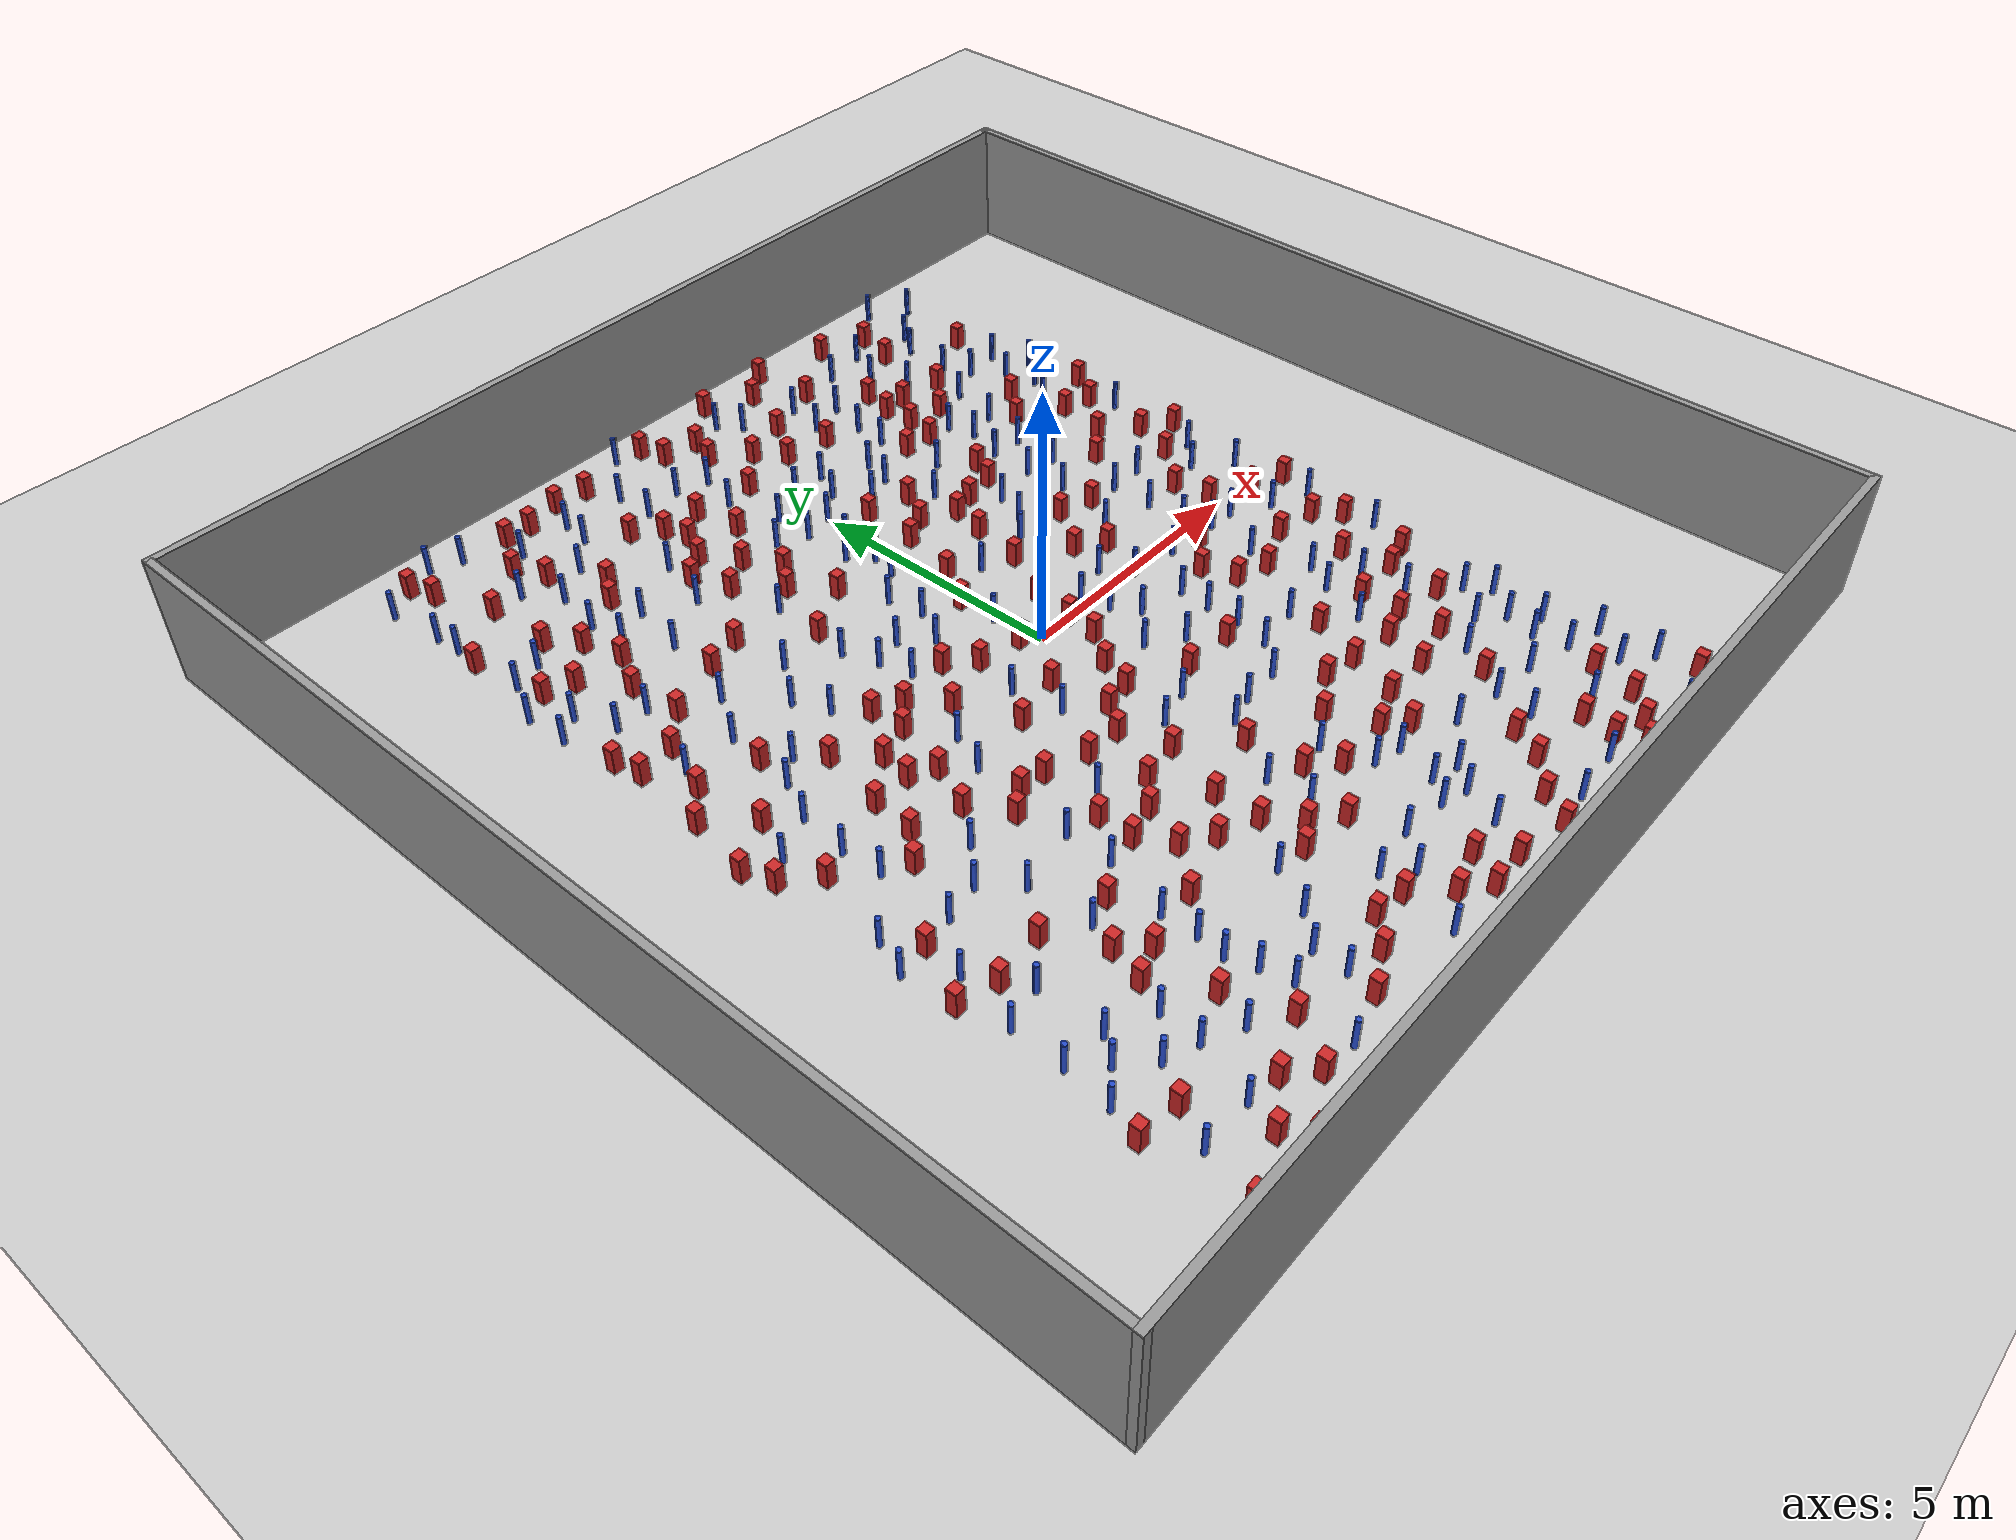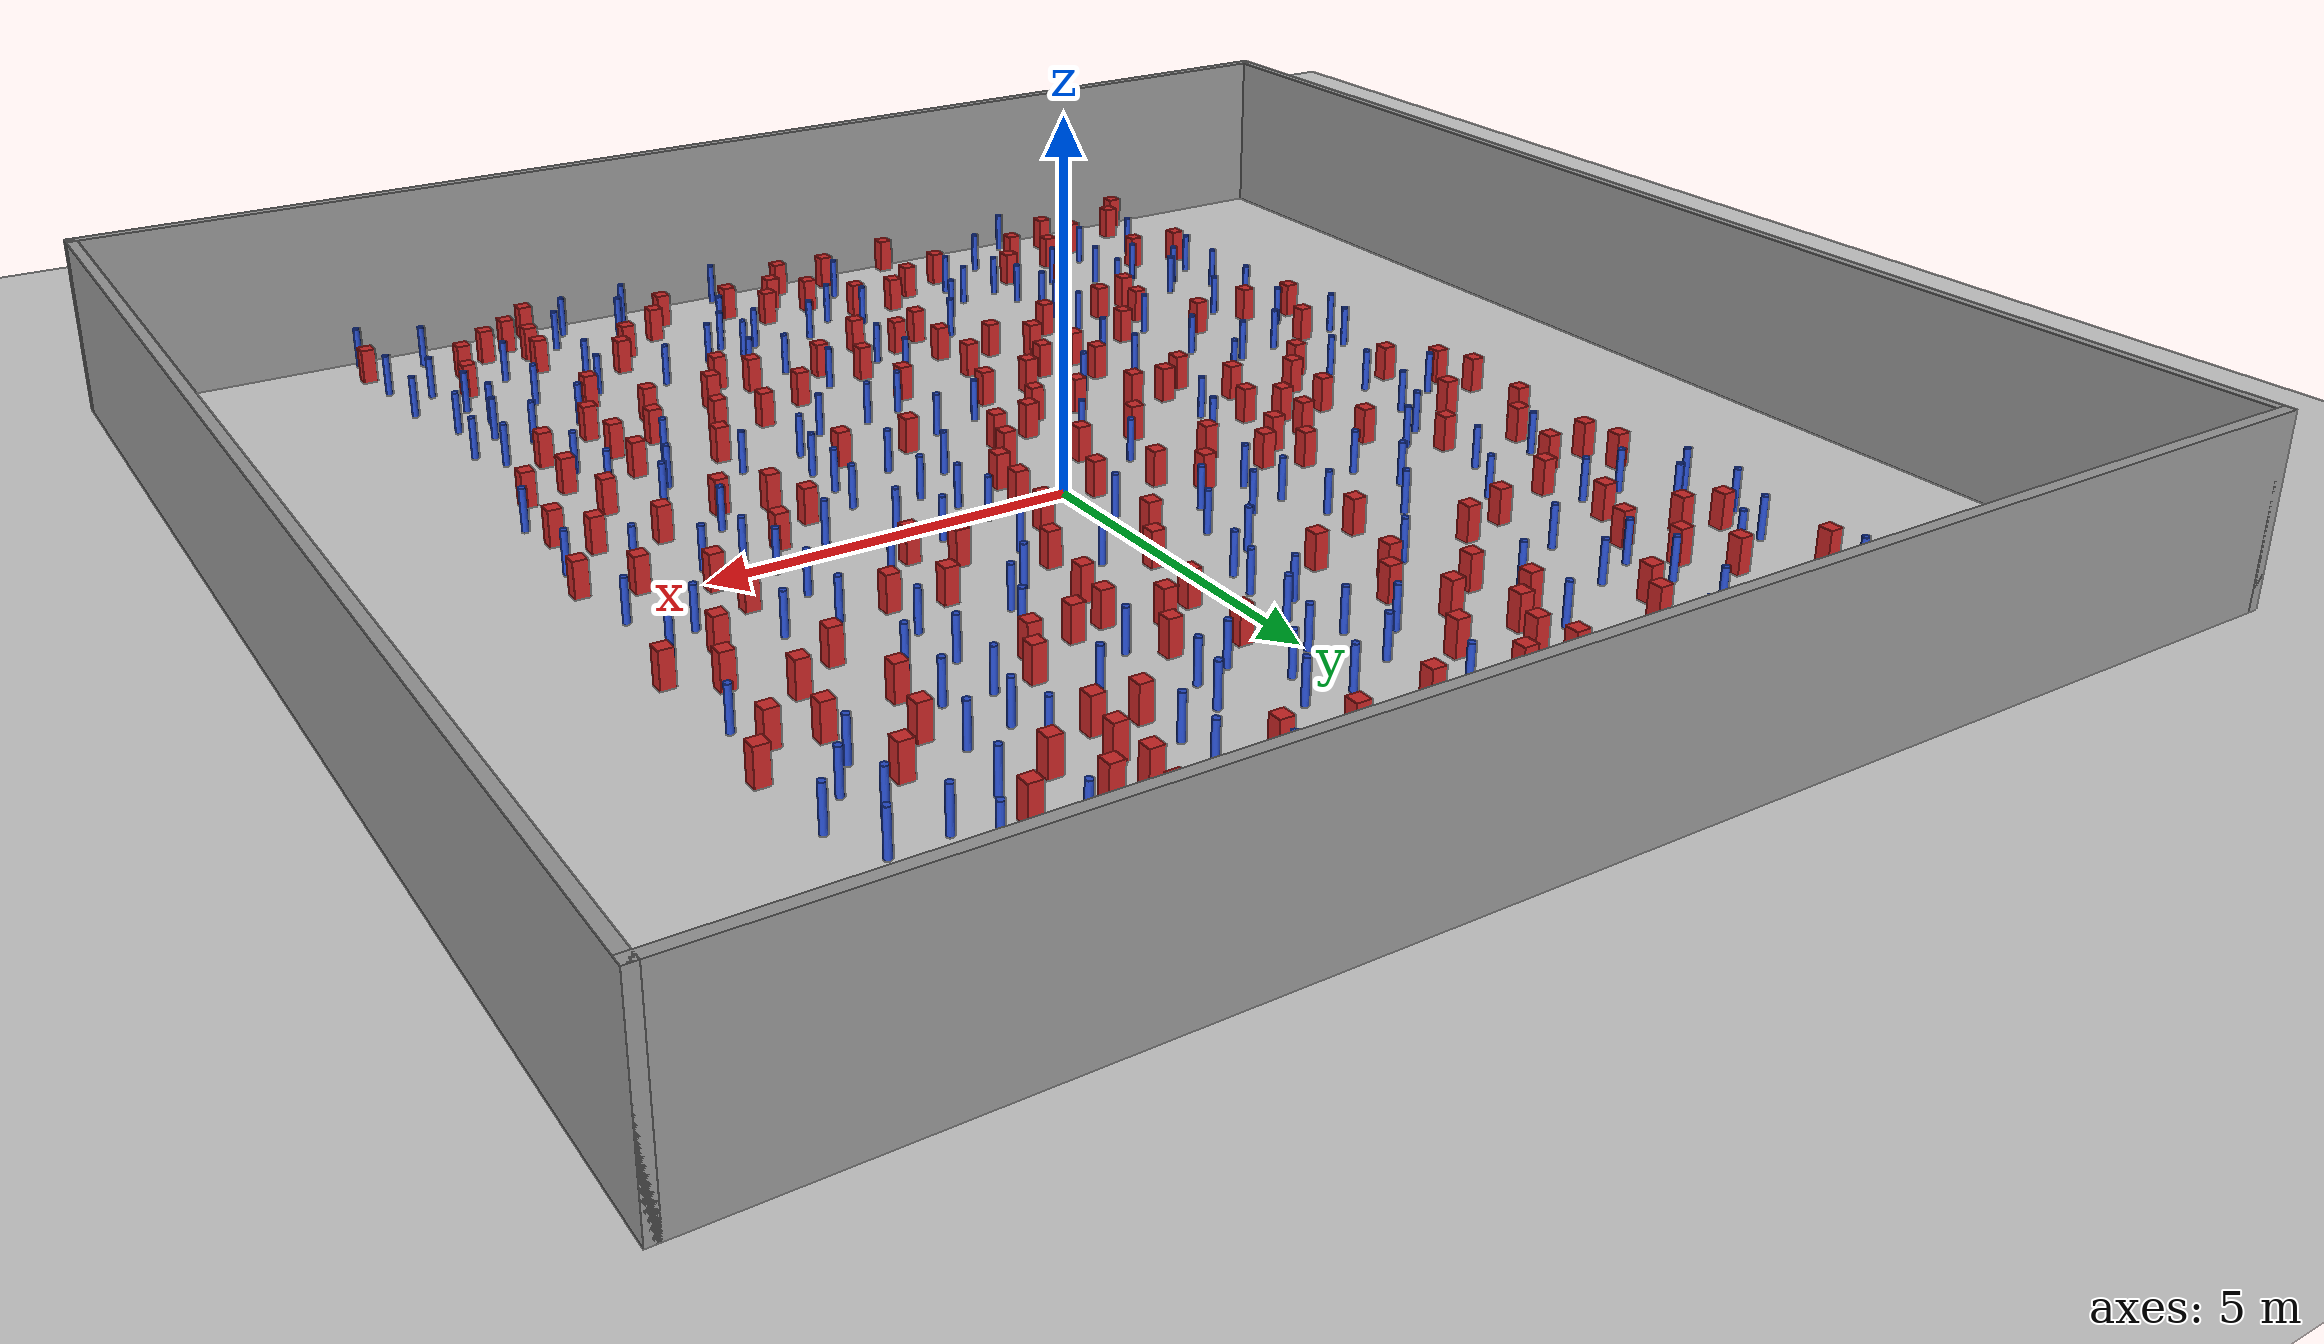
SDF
<sdf version="1.6">
 <world name="default">
  <light name="sun" type="directional">
   <pose>0 0 1000 0 -0 0</pose>
   <diffuse>0.8 0.8 0.8 1</diffuse>
   <specular>0.1 0.1 0.1 1</specular>
   <attenuation>
    <range>1000</range>
    <constant>0.9</constant>
    <linear>0.01</linear>
    <quadratic>0.001</quadratic>
   </attenuation>
   <direction>-0.5 0.5 -1</direction>
  </light>
  <model name="ground_plane">
   <static>1</static>
   <link name="link">
    <collision name="collision">
     <geometry><plane><normal>0 0 1</normal><size>100 100</size></plane></geometry>
     <surface><friction><ode><mu>100</mu><mu2>50</mu2></ode></friction></surface>
    </collision>
    <visual name="visual">
     <cast_shadows>0</cast_shadows>
     <geometry><plane><normal>0 0 1</normal><size>100 100</size></plane></geometry>
     <material>
      <ambient>1.0 1.0 1.0 1.0</ambient>
      <diffuse>0.8 0.8 0.8 1.0</diffuse>
      <specular>0.01 0.01 0.01 1.000000</specular>
     </material>
    </visual>
   </link>
  </model>
  <gravity>0 0 -9.8</gravity>
  <magnetic_field>6e-06 2.3e-05 -4.2e-05</magnetic_field>
  <atmosphere type="adiabatic"/>
  <physics name="default_physics" default="0" type="ode">
   <max_step_size>0.001</max_step_size>
   <real_time_factor>1</real_time_factor>
   <real_time_update_rate>1000</real_time_update_rate>
  </physics>
  <scene><ambient>0.4 0.4 0.4 1</ambient><background>0.7 0.7 0.7 1</background><shadows>1</shadows></scene>
  <spherical_coordinates>
   <surface_model>EARTH_WGS84</surface_model>
   <latitude_deg>0</latitude_deg>
   <longitude_deg>0</longitude_deg>
   <elevation>0</elevation>
   <heading_deg>0</heading_deg>
  </spherical_coordinates>
  <plugin name="gazebo_occupancy_map" filename="libgazebo_2Dmap_plugin.so">
   <map_resolution>0.05</map_resolution>
   <map_topic>generated_map</map_topic>
   <map_height>0.01</map_height>
   <map_size_x>50</map_size_x>
   <map_size_y>50</map_size_y>
  </plugin>
  <model name="NamedLocations">
   <static>true</static>
   <link name="DefaultStart"><pose>8.5 0 0 0 0 3.14</pose></link>
  </model>
  <model name="20x20_walls">
   <pose>0.044518 0.176112 0 0 -0 0</pose>
   <link name="Wall_1">
    <collision name="Wall_1_Collision">
     <geometry><box><size>20 0.15 2.5</size></box></geometry>
     <pose>0 0 1.25 0 -0 0</pose>
    </collision>
    <visual name="Wall_1_Visual">
     <pose>0 0 1.25 0 -0 0</pose>
     <geometry><box><size>20 0.15 2.5</size></box></geometry>
     <material>
      <script><uri>file://media/materials/scripts/gazebo.material</uri><name>Gazebo/Grey</name></script>
      <ambient>0.976471 0.992157 1 1</ambient>
     </material>
     <meta><layer>0</layer></meta>
    </visual>
    <pose>0 9.925 0 0 -0 0</pose>
   </link>
   <link name="Wall_3">
    <collision name="Wall_3_Collision">
     <geometry><box><size>20 0.15 2.5</size></box></geometry>
     <pose>0 0 1.25 0 -0 0</pose>
    </collision>
    <visual name="Wall_3_Visual">
     <pose>0 0 1.25 0 -0 0</pose>
     <geometry><box><size>20 0.15 2.5</size></box></geometry>
     <material>
      <script><uri>file://media/materials/scripts/gazebo.material</uri><name>Gazebo/Grey</name></script>
      <ambient>0.976471 0.992157 1 1</ambient>
     </material>
     <meta><layer>0</layer></meta>
    </visual>
    <pose>9.925 0 0 0 0 -1.5708</pose>
   </link>
   <link name="Wall_4">
    <collision name="Wall_4_Collision">
     <geometry><box><size>20 0.15 2.5</size></box></geometry>
     <pose>0 0 1.25 0 -0 0</pose>
    </collision>
    <visual name="Wall_4_Visual">
     <pose>0 0 1.25 0 -0 0</pose>
     <geometry><box><size>20 0.15 2.5</size></box></geometry>
     <material>
      <script><uri>file://media/materials/scripts/gazebo.material</uri><name>Gazebo/Grey</name></script>
      <ambient>0.976471 0.992157 1 1</ambient>
     </material>
     <meta><layer>0</layer></meta>
    </visual>
    <pose>0 -9.925 0 0 -0 3.14159</pose>
   </link>
   <link name="Wall_5">
    <collision name="Wall_5_Collision">
     <geometry><box><size>20 0.15 2.5</size></box></geometry>
     <pose>0 0 1.25 0 -0 0</pose>
    </collision>
    <visual name="Wall_5_Visual">
     <pose>0 0 1.25 0 -0 0</pose>
     <geometry><box><size>20 0.15 2.5</size></box></geometry>
     <material>
      <script><uri>file://media/materials/scripts/gazebo.material</uri><name>Gazebo/Grey</name></script>
      <ambient>0.976471 0.992157 1 1</ambient>
     </material>
     <meta><layer>0</layer></meta>
    </visual>
    <pose>-9.925 0 0 0 -0 1.5708</pose>
   </link>
   <static>1</static>
  </model>
  <model name="square_post_obstacle0">
   <static>true</static>
   <pose>-6.76671333463 -7.36442165139 1.91545236811e-07 -7.35059704564e-06 1.12565212e-07 2.39332434364e-05</pose>
   <link name="link">
    <pose>0 0 0.25 0 -0 0</pose>
    <inertial>
     <mass>100</mass>
     <inertia>
      <ixx>0.166667</ixx>
      <ixy>0</ixy>
      <ixz>0</ixz>
      <iyy>0.166667</iyy>
      <iyz>0</iyz>
      <izz>0.166667</izz>
     </inertia>
    </inertial>
    <collision name="collision"><geometry><box><size>.2 .2 .5</size></box></geometry></collision>
    <visual name="visual">
     <geometry><box><size>.2 .2 .5</size></box></geometry>
     <material>
      <script><name>Gazebo/Red</name><uri>file://media/materials/scripts/gazebo.material</uri></script>
     </material>
    </visual>
   </link>
  </model>
  <model name="square_post_obstacle1">
   <static>true</static>
   <pose>0.463909834269 3.49342118369 1.91545236811e-07 -7.35059704564e-06 1.12565212e-07 2.39332434364e-05</pose>
   <link name="link">
    <pose>0 0 0.25 0 -0 0</pose>
    <inertial>
     <mass>100</mass>
     <inertia>
      <ixx>0.166667</ixx>
      <ixy>0</ixy>
      <ixz>0</ixz>
      <iyy>0.166667</iyy>
      <iyz>0</iyz>
      <izz>0.166667</izz>
     </inertia>
    </inertial>
    <collision name="collision"><geometry><box><size>.2 .2 .5</size></box></geometry></collision>
    <visual name="visual">
     <geometry><box><size>.2 .2 .5</size></box></geometry>
     <material>
      <script><name>Gazebo/Red</name><uri>file://media/materials/scripts/gazebo.material</uri></script>
     </material>
    </visual>
   </link>
  </model>
  <model name="pole_obstacle0">
   <static>true</static>
   <pose>-4.36487225935 -7.36357228489 7.38925637345e-09 -8.47170692796e-08 1.24976764786e-08 -1.74513093032e-07</pose>
   <link name="link">
    <pose>0 0 0.3 0 -0 0</pose>
    <inertial>
     <mass>1</mass>
     <inertia><ixx>0.145833</ixx><ixy>0</ixy><ixz>0</ixz><iyy>0.145833</iyy><iyz>0</iyz><izz>0.125</izz></inertia>
    </inertial>
    <collision name="collision">
     <geometry><cylinder><radius>0.05</radius><length>.6</length></cylinder></geometry>
    </collision>
    <visual name="visual">
     <geometry><cylinder><radius>0.05</radius><length>.6</length></cylinder></geometry>
     <material>
      <script><name>Gazebo/Blue</name><uri>file://media/materials/scripts/gazebo.material</uri></script>
     </material>
    </visual>
   </link>
  </model>
  <model name="square_post_obstacle2">
   <static>true</static>
   <pose>-2.59575525079 4.89425721059 1.91545236811e-07 -7.35059704564e-06 1.12565212e-07 2.39332434364e-05</pose>
   <link name="link">
    <pose>0 0 0.25 0 -0 0</pose>
    <inertial>
     <mass>100</mass>
     <inertia>
      <ixx>0.166667</ixx>
      <ixy>0</ixy>
      <ixz>0</ixz>
      <iyy>0.166667</iyy>
      <iyz>0</iyz>
      <izz>0.166667</izz>
     </inertia>
    </inertial>
    <collision name="collision"><geometry><box><size>.2 .2 .5</size></box></geometry></collision>
    <visual name="visual">
     <geometry><box><size>.2 .2 .5</size></box></geometry>
     <material>
      <script><name>Gazebo/Red</name><uri>file://media/materials/scripts/gazebo.material</uri></script>
     </material>
    </visual>
   </link>
  </model>
  <model name="pole_obstacle1">
   <static>true</static>
   <pose>-4.19937679218 4.57244880064 7.38925637345e-09 -8.47170692796e-08 1.24976764786e-08 -1.74513093032e-07</pose>
   <link name="link">
    <pose>0 0 0.3 0 -0 0</pose>
    <inertial>
     <mass>1</mass>
     <inertia><ixx>0.145833</ixx><ixy>0</ixy><ixz>0</ixz><iyy>0.145833</iyy><iyz>0</iyz><izz>0.125</izz></inertia>
    </inertial>
    <collision name="collision">
     <geometry><cylinder><radius>0.05</radius><length>.6</length></cylinder></geometry>
    </collision>
    <visual name="visual">
     <geometry><cylinder><radius>0.05</radius><length>.6</length></cylinder></geometry>
     <material>
      <script><name>Gazebo/Blue</name><uri>file://media/materials/scripts/gazebo.material</uri></script>
     </material>
    </visual>
   </link>
  </model>
  <model name="square_post_obstacle3">
   <static>true</static>
   <pose>3.17757316821 -0.992732343111 1.91545236811e-07 -7.35059704564e-06 1.12565212e-07 2.39332434364e-05</pose>
   <link name="link">
    <pose>0 0 0.25 0 -0 0</pose>
    <inertial>
     <mass>100</mass>
     <inertia>
      <ixx>0.166667</ixx>
      <ixy>0</ixy>
      <ixz>0</ixz>
      <iyy>0.166667</iyy>
      <iyz>0</iyz>
      <izz>0.166667</izz>
     </inertia>
    </inertial>
    <collision name="collision"><geometry><box><size>.2 .2 .5</size></box></geometry></collision>
    <visual name="visual">
     <geometry><box><size>.2 .2 .5</size></box></geometry>
     <material>
      <script><name>Gazebo/Red</name><uri>file://media/materials/scripts/gazebo.material</uri></script>
     </material>
    </visual>
   </link>
  </model>
  <model name="pole_obstacle2">
   <static>true</static>
   <pose>5.58116646436 -6.90500801666 7.38925637345e-09 -8.47170692796e-08 1.24976764786e-08 -1.74513093032e-07</pose>
   <link name="link">
    <pose>0 0 0.3 0 -0 0</pose>
    <inertial>
     <mass>1</mass>
     <inertia><ixx>0.145833</ixx><ixy>0</ixy><ixz>0</ixz><iyy>0.145833</iyy><iyz>0</iyz><izz>0.125</izz></inertia>
    </inertial>
    <collision name="collision">
     <geometry><cylinder><radius>0.05</radius><length>.6</length></cylinder></geometry>
    </collision>
    <visual name="visual">
     <geometry><cylinder><radius>0.05</radius><length>.6</length></cylinder></geometry>
     <material>
      <script><name>Gazebo/Blue</name><uri>file://media/materials/scripts/gazebo.material</uri></script>
     </material>
    </visual>
   </link>
  </model>
  <model name="pole_obstacle3">
   <static>true</static>
   <pose>-3.22854497881 -3.2241212112 7.38925637345e-09 -8.47170692798e-08 1.24976764939e-08 -1.74513093025e-07</pose>
   <link name="link">
    <pose>0 0 0.3 0 -0 0</pose>
    <inertial>
     <mass>1</mass>
     <inertia><ixx>0.145833</ixx><ixy>0</ixy><ixz>0</ixz><iyy>0.145833</iyy><iyz>0</iyz><izz>0.125</izz></inertia>
    </inertial>
    <collision name="collision">
     <geometry><cylinder><radius>0.05</radius><length>.6</length></cylinder></geometry>
    </collision>
    <visual name="visual">
     <geometry><cylinder><radius>0.05</radius><length>.6</length></cylinder></geometry>
     <material>
      <script><name>Gazebo/Blue</name><uri>file://media/materials/scripts/gazebo.material</uri></script>
     </material>
    </visual>
   </link>
  </model>
  <model name="square_post_obstacle4">
   <static>true</static>
   <pose>0.838831545188 9.4305301284 1.91545236811e-07 -7.35059704564e-06 1.12565212e-07 2.39332434364e-05</pose>
   <link name="link">
    <pose>0 0 0.25 0 -0 0</pose>
    <inertial>
     <mass>100</mass>
     <inertia>
      <ixx>0.166667</ixx>
      <ixy>0</ixy>
      <ixz>0</ixz>
      <iyy>0.166667</iyy>
      <iyz>0</iyz>
      <izz>0.166667</izz>
     </inertia>
    </inertial>
    <collision name="collision"><geometry><box><size>.2 .2 .5</size></box></geometry></collision>
    <visual name="visual">
     <geometry><box><size>.2 .2 .5</size></box></geometry>
     <material>
      <script><name>Gazebo/Red</name><uri>file://media/materials/scripts/gazebo.material</uri></script>
     </material>
    </visual>
   </link>
  </model>
  <model name="square_post_obstacle5">
   <static>true</static>
   <pose>-5.23088363915 -9.11303730283 1.91545236811e-07 -7.35059704564e-06 1.12565212e-07 2.39332434364e-05</pose>
   <link name="link">
    <pose>0 0 0.25 0 -0 0</pose>
    <inertial>
     <mass>100</mass>
     <inertia>
      <ixx>0.166667</ixx>
      <ixy>0</ixy>
      <ixz>0</ixz>
      <iyy>0.166667</iyy>
      <iyz>0</iyz>
      <izz>0.166667</izz>
     </inertia>
    </inertial>
    <collision name="collision"><geometry><box><size>.2 .2 .5</size></box></geometry></collision>
    <visual name="visual">
     <geometry><box><size>.2 .2 .5</size></box></geometry>
     <material>
      <script><name>Gazebo/Red</name><uri>file://media/materials/scripts/gazebo.material</uri></script>
     </material>
    </visual>
   </link>
  </model>
  <model name="square_post_obstacle6">
   <static>true</static>
   <pose>-0.0670003100005 8.64714407239 1.91545236811e-07 -7.35059704564e-06 1.12565212e-07 2.39332434364e-05</pose>
   <link name="link">
    <pose>0 0 0.25 0 -0 0</pose>
    <inertial>
     <mass>100</mass>
     <inertia>
      <ixx>0.166667</ixx>
      <ixy>0</ixy>
      <ixz>0</ixz>
      <iyy>0.166667</iyy>
      <iyz>0</iyz>
      <izz>0.166667</izz>
     </inertia>
    </inertial>
    <collision name="collision"><geometry><box><size>.2 .2 .5</size></box></geometry></collision>
    <visual name="visual">
     <geometry><box><size>.2 .2 .5</size></box></geometry>
     <material>
      <script><name>Gazebo/Red</name><uri>file://media/materials/scripts/gazebo.material</uri></script>
     </material>
    </visual>
   </link>
  </model>
  <model name="pole_obstacle4">
   <static>true</static>
   <pose>4.11311792491 0.900247781949 7.38925637345e-09 -8.47170692799e-08 1.24976765038e-08 -1.74513093018e-07</pose>
   <link name="link">
    <pose>0 0 0.3 0 -0 0</pose>
    <inertial>
     <mass>1</mass>
     <inertia><ixx>0.145833</ixx><ixy>0</ixy><ixz>0</ixz><iyy>0.145833</iyy><iyz>0</iyz><izz>0.125</izz></inertia>
    </inertial>
    <collision name="collision">
     <geometry><cylinder><radius>0.05</radius><length>.6</length></cylinder></geometry>
    </collision>
    <visual name="visual">
     <geometry><cylinder><radius>0.05</radius><length>.6</length></cylinder></geometry>
     <material>
      <script><name>Gazebo/Blue</name><uri>file://media/materials/scripts/gazebo.material</uri></script>
     </material>
    </visual>
   </link>
  </model>
  <model name="pole_obstacle5">
   <static>true</static>
   <pose>-0.245421872697 -5.62670158152 7.38925637345e-09 -8.47170692799e-08 1.2497676507e-08 -1.74513093018e-07</pose>
   <link name="link">
    <pose>0 0 0.3 0 -0 0</pose>
    <inertial>
     <mass>1</mass>
     <inertia><ixx>0.145833</ixx><ixy>0</ixy><ixz>0</ixz><iyy>0.145833</iyy><iyz>0</iyz><izz>0.125</izz></inertia>
    </inertial>
    <collision name="collision">
     <geometry><cylinder><radius>0.05</radius><length>.6</length></cylinder></geometry>
    </collision>
    <visual name="visual">
     <geometry><cylinder><radius>0.05</radius><length>.6</length></cylinder></geometry>
     <material>
      <script><name>Gazebo/Blue</name><uri>file://media/materials/scripts/gazebo.material</uri></script>
     </material>
    </visual>
   </link>
  </model>
  <model name="square_post_obstacle7">
   <static>true</static>
   <pose>-3.00368671841 -5.3784053675 1.91545236811e-07 -7.35059704564e-06 1.12565212e-07 2.39332434364e-05</pose>
   <link name="link">
    <pose>0 0 0.25 0 -0 0</pose>
    <inertial>
     <mass>100</mass>
     <inertia>
      <ixx>0.166667</ixx>
      <ixy>0</ixy>
      <ixz>0</ixz>
      <iyy>0.166667</iyy>
      <iyz>0</iyz>
      <izz>0.166667</izz>
     </inertia>
    </inertial>
    <collision name="collision"><geometry><box><size>.2 .2 .5</size></box></geometry></collision>
    <visual name="visual">
     <geometry><box><size>.2 .2 .5</size></box></geometry>
     <material>
      <script><name>Gazebo/Red</name><uri>file://media/materials/scripts/gazebo.material</uri></script>
     </material>
    </visual>
   </link>
  </model>
  <model name="square_post_obstacle8">
   <static>true</static>
   <pose>-2.85117813778 5.63529117119 1.91545236811e-07 -7.35059704564e-06 1.12565212e-07 2.39332434364e-05</pose>
   <link name="link">
    <pose>0 0 0.25 0 -0 0</pose>
    <inertial>
     <mass>100</mass>
     <inertia>
      <ixx>0.166667</ixx>
      <ixy>0</ixy>
      <ixz>0</ixz>
      <iyy>0.166667</iyy>
      <iyz>0</iyz>
      <izz>0.166667</izz>
     </inertia>
    </inertial>
    <collision name="collision"><geometry><box><size>.2 .2 .5</size></box></geometry></collision>
    <visual name="visual">
     <geometry><box><size>.2 .2 .5</size></box></geometry>
     <material>
      <script><name>Gazebo/Red</name><uri>file://media/materials/scripts/gazebo.material</uri></script>
     </material>
    </visual>
   </link>
  </model>
  <model name="pole_obstacle6">
   <static>true</static>
   <pose>-6.42297541409 4.46587026032 7.38925637345e-09 -8.47170692796e-08 1.24976764786e-08 -1.74513093032e-07</pose>
   <link name="link">
    <pose>0 0 0.3 0 -0 0</pose>
    <inertial>
     <mass>1</mass>
     <inertia><ixx>0.145833</ixx><ixy>0</ixy><ixz>0</ixz><iyy>0.145833</iyy><iyz>0</iyz><izz>0.125</izz></inertia>
    </inertial>
    <collision name="collision">
     <geometry><cylinder><radius>0.05</radius><length>.6</length></cylinder></geometry>
    </collision>
    <visual name="visual">
     <geometry><cylinder><radius>0.05</radius><length>.6</length></cylinder></geometry>
     <material>
      <script><name>Gazebo/Blue</name><uri>file://media/materials/scripts/gazebo.material</uri></script>
     </material>
    </visual>
   </link>
  </model>
  <model name="pole_obstacle7">
   <static>true</static>
   <pose>5.17682240041 -5.33551856168 7.38925637345e-09 -8.47170692796e-08 1.24976764786e-08 -1.74513093032e-07</pose>
   <link name="link">
    <pose>0 0 0.3 0 -0 0</pose>
    <inertial>
     <mass>1</mass>
     <inertia><ixx>0.145833</ixx><ixy>0</ixy><ixz>0</ixz><iyy>0.145833</iyy><iyz>0</iyz><izz>0.125</izz></inertia>
    </inertial>
    <collision name="collision">
     <geometry><cylinder><radius>0.05</radius><length>.6</length></cylinder></geometry>
    </collision>
    <visual name="visual">
     <geometry><cylinder><radius>0.05</radius><length>.6</length></cylinder></geometry>
     <material>
      <script><name>Gazebo/Blue</name><uri>file://media/materials/scripts/gazebo.material</uri></script>
     </material>
    </visual>
   </link>
  </model>
  <model name="square_post_obstacle9">
   <static>true</static>
   <pose>-6.21314475476 -3.11580923219 1.91545236811e-07 -7.35059704564e-06 1.12565212e-07 2.39332434364e-05</pose>
   <link name="link">
    <pose>0 0 0.25 0 -0 0</pose>
    <inertial>
     <mass>100</mass>
     <inertia>
      <ixx>0.166667</ixx>
      <ixy>0</ixy>
      <ixz>0</ixz>
      <iyy>0.166667</iyy>
      <iyz>0</iyz>
      <izz>0.166667</izz>
     </inertia>
    </inertial>
    <collision name="collision"><geometry><box><size>.2 .2 .5</size></box></geometry></collision>
    <visual name="visual">
     <geometry><box><size>.2 .2 .5</size></box></geometry>
     <material>
      <script><name>Gazebo/Red</name><uri>file://media/materials/scripts/gazebo.material</uri></script>
     </material>
    </visual>
   </link>
  </model>
  <model name="square_post_obstacle10">
   <static>true</static>
   <pose>-0.647487318946 -1.97284515534 1.91545236811e-07 -7.35059704564e-06 1.12565212e-07 2.39332434364e-05</pose>
   <link name="link">
    <pose>0 0 0.25 0 -0 0</pose>
    <inertial>
     <mass>100</mass>
     <inertia>
      <ixx>0.166667</ixx>
      <ixy>0</ixy>
      <ixz>0</ixz>
      <iyy>0.166667</iyy>
      <iyz>0</iyz>
      <izz>0.166667</izz>
     </inertia>
    </inertial>
    <collision name="collision"><geometry><box><size>.2 .2 .5</size></box></geometry></collision>
    <visual name="visual">
     <geometry><box><size>.2 .2 .5</size></box></geometry>
     <material>
      <script><name>Gazebo/Red</name><uri>file://media/materials/scripts/gazebo.material</uri></script>
     </material>
    </visual>
   </link>
  </model>
  <model name="square_post_obstacle11">
   <static>true</static>
   <pose>-1.18005048999 -6.15033566923 1.91545236811e-07 -7.35059704564e-06 1.12565212e-07 2.39332434364e-05</pose>
   <link name="link">
    <pose>0 0 0.25 0 -0 0</pose>
    <inertial>
     <mass>100</mass>
     <inertia>
      <ixx>0.166667</ixx>
      <ixy>0</ixy>
      <ixz>0</ixz>
      <iyy>0.166667</iyy>
      <iyz>0</iyz>
      <izz>0.166667</izz>
     </inertia>
    </inertial>
    <collision name="collision"><geometry><box><size>.2 .2 .5</size></box></geometry></collision>
    <visual name="visual">
     <geometry><box><size>.2 .2 .5</size></box></geometry>
     <material>
      <script><name>Gazebo/Red</name><uri>file://media/materials/scripts/gazebo.material</uri></script>
     </material>
    </visual>
   </link>
  </model>
  <model name="square_post_obstacle12">
   <static>true</static>
   <pose>4.85128423616 0.870556990266 1.91545236811e-07 -7.35059704564e-06 1.12565212e-07 2.39332434364e-05</pose>
   <link name="link">
    <pose>0 0 0.25 0 -0 0</pose>
    <inertial>
     <mass>100</mass>
     <inertia>
      <ixx>0.166667</ixx>
      <ixy>0</ixy>
      <ixz>0</ixz>
      <iyy>0.166667</iyy>
      <iyz>0</iyz>
      <izz>0.166667</izz>
     </inertia>
    </inertial>
    <collision name="collision"><geometry><box><size>.2 .2 .5</size></box></geometry></collision>
    <visual name="visual">
     <geometry><box><size>.2 .2 .5</size></box></geometry>
     <material>
      <script><name>Gazebo/Red</name><uri>file://media/materials/scripts/gazebo.material</uri></script>
     </material>
    </visual>
   </link>
  </model>
  <model name="square_post_obstacle13">
   <static>true</static>
   <pose>4.42640117851 3.71198191929 1.91545236811e-07 -7.35059704564e-06 1.12565212e-07 2.39332434364e-05</pose>
   <link name="link">
    <pose>0 0 0.25 0 -0 0</pose>
    <inertial>
     <mass>100</mass>
     <inertia>
      <ixx>0.166667</ixx>
      <ixy>0</ixy>
      <ixz>0</ixz>
      <iyy>0.166667</iyy>
      <iyz>0</iyz>
      <izz>0.166667</izz>
     </inertia>
    </inertial>
    <collision name="collision"><geometry><box><size>.2 .2 .5</size></box></geometry></collision>
    <visual name="visual">
     <geometry><box><size>.2 .2 .5</size></box></geometry>
     <material>
      <script><name>Gazebo/Red</name><uri>file://media/materials/scripts/gazebo.material</uri></script>
     </material>
    </visual>
   </link>
  </model>
  <model name="pole_obstacle8">
   <static>true</static>
   <pose>5.28850879259 6.38729113192 7.38925637345e-09 -8.47170692796e-08 1.24976764786e-08 -1.74513093032e-07</pose>
   <link name="link">
    <pose>0 0 0.3 0 -0 0</pose>
    <inertial>
     <mass>1</mass>
     <inertia><ixx>0.145833</ixx><ixy>0</ixy><ixz>0</ixz><iyy>0.145833</iyy><iyz>0</iyz><izz>0.125</izz></inertia>
    </inertial>
    <collision name="collision">
     <geometry><cylinder><radius>0.05</radius><length>.6</length></cylinder></geometry>
    </collision>
    <visual name="visual">
     <geometry><cylinder><radius>0.05</radius><length>.6</length></cylinder></geometry>
     <material>
      <script><name>Gazebo/Blue</name><uri>file://media/materials/scripts/gazebo.material</uri></script>
     </material>
    </visual>
   </link>
  </model>
  <model name="square_post_obstacle14">
   <static>true</static>
   <pose>-5.18274120243 -1.91572686425 1.91545236811e-07 -7.35059704564e-06 1.12565212e-07 2.39332434364e-05</pose>
   <link name="link">
    <pose>0 0 0.25 0 -0 0</pose>
    <inertial>
     <mass>100</mass>
     <inertia>
      <ixx>0.166667</ixx>
      <ixy>0</ixy>
      <ixz>0</ixz>
      <iyy>0.166667</iyy>
      <iyz>0</iyz>
      <izz>0.166667</izz>
     </inertia>
    </inertial>
    <collision name="collision"><geometry><box><size>.2 .2 .5</size></box></geometry></collision>
    <visual name="visual">
     <geometry><box><size>.2 .2 .5</size></box></geometry>
     <material>
      <script><name>Gazebo/Red</name><uri>file://media/materials/scripts/gazebo.material</uri></script>
     </material>
    </visual>
   </link>
  </model>
  <model name="square_post_obstacle15">
   <static>true</static>
   <pose>-4.73293438158 -5.81196238681 1.91545236811e-07 -7.35059704564e-06 1.12565212e-07 2.39332434364e-05</pose>
   <link name="link">
    <pose>0 0 0.25 0 -0 0</pose>
    <inertial>
     <mass>100</mass>
     <inertia>
      <ixx>0.166667</ixx>
      <ixy>0</ixy>
      <ixz>0</ixz>
      <iyy>0.166667</iyy>
      <iyz>0</iyz>
      <izz>0.166667</izz>
     </inertia>
    </inertial>
    <collision name="collision"><geometry><box><size>.2 .2 .5</size></box></geometry></collision>
    <visual name="visual">
     <geometry><box><size>.2 .2 .5</size></box></geometry>
     <material>
      <script><name>Gazebo/Red</name><uri>file://media/materials/scripts/gazebo.material</uri></script>
     </material>
    </visual>
   </link>
  </model>
  <model name="square_post_obstacle16">
   <static>true</static>
   <pose>2.46480486465 5.48030747569 1.91545236811e-07 -7.35059704564e-06 1.12565212e-07 2.39332434364e-05</pose>
   <link name="link">
    <pose>0 0 0.25 0 -0 0</pose>
    <inertial>
     <mass>100</mass>
     <inertia>
      <ixx>0.166667</ixx>
      <ixy>0</ixy>
      <ixz>0</ixz>
      <iyy>0.166667</iyy>
      <iyz>0</iyz>
      <izz>0.166667</izz>
     </inertia>
    </inertial>
    <collision name="collision"><geometry><box><size>.2 .2 .5</size></box></geometry></collision>
    <visual name="visual">
     <geometry><box><size>.2 .2 .5</size></box></geometry>
     <material>
      <script><name>Gazebo/Red</name><uri>file://media/materials/scripts/gazebo.material</uri></script>
     </material>
    </visual>
   </link>
  </model>
  <model name="pole_obstacle9">
   <static>true</static>
   <pose>5.81578536251 -7.72304774756 7.38925637345e-09 -8.47170692796e-08 1.24976764786e-08 -1.74513093032e-07</pose>
   <link name="link">
    <pose>0 0 0.3 0 -0 0</pose>
    <inertial>
     <mass>1</mass>
     <inertia><ixx>0.145833</ixx><ixy>0</ixy><ixz>0</ixz><iyy>0.145833</iyy><iyz>0</iyz><izz>0.125</izz></inertia>
    </inertial>
    <collision name="collision">
     <geometry><cylinder><radius>0.05</radius><length>.6</length></cylinder></geometry>
    </collision>
    <visual name="visual">
     <geometry><cylinder><radius>0.05</radius><length>.6</length></cylinder></geometry>
     <material>
      <script><name>Gazebo/Blue</name><uri>file://media/materials/scripts/gazebo.material</uri></script>
     </material>
    </visual>
   </link>
  </model>
  <model name="square_post_obstacle17">
   <static>true</static>
   <pose>-1.71797052306 -2.42439164931 1.91545236811e-07 -7.35059704564e-06 1.12565212e-07 2.39332434364e-05</pose>
   <link name="link">
    <pose>0 0 0.25 0 -0 0</pose>
    <inertial>
     <mass>100</mass>
     <inertia>
      <ixx>0.166667</ixx>
      <ixy>0</ixy>
      <ixz>0</ixz>
      <iyy>0.166667</iyy>
      <iyz>0</iyz>
      <izz>0.166667</izz>
     </inertia>
    </inertial>
    <collision name="collision"><geometry><box><size>.2 .2 .5</size></box></geometry></collision>
    <visual name="visual">
     <geometry><box><size>.2 .2 .5</size></box></geometry>
     <material>
      <script><name>Gazebo/Red</name><uri>file://media/materials/scripts/gazebo.material</uri></script>
     </material>
    </visual>
   </link>
  </model>
  <model name="square_post_obstacle18">
   <static>true</static>
   <pose>4.64170518958 2.58827040064 1.91545236811e-07 -7.35059704564e-06 1.12565212e-07 2.39332434364e-05</pose>
   <link name="link">
    <pose>0 0 0.25 0 -0 0</pose>
    <inertial>
     <mass>100</mass>
     <inertia>
      <ixx>0.166667</ixx>
      <ixy>0</ixy>
      <ixz>0</ixz>
      <iyy>0.166667</iyy>
      <iyz>0</iyz>
      <izz>0.166667</izz>
     </inertia>
    </inertial>
    <collision name="collision"><geometry><box><size>.2 .2 .5</size></box></geometry></collision>
    <visual name="visual">
     <geometry><box><size>.2 .2 .5</size></box></geometry>
     <material>
      <script><name>Gazebo/Red</name><uri>file://media/materials/scripts/gazebo.material</uri></script>
     </material>
    </visual>
   </link>
  </model>
  <model name="pole_obstacle10">
   <static>true</static>
   <pose>-3.33697013683 7.99932537133 7.38925637345e-09 -8.47170692799e-08 1.24976765031e-08 -1.7451309302e-07</pose>
   <link name="link">
    <pose>0 0 0.3 0 -0 0</pose>
    <inertial>
     <mass>1</mass>
     <inertia><ixx>0.145833</ixx><ixy>0</ixy><ixz>0</ixz><iyy>0.145833</iyy><iyz>0</iyz><izz>0.125</izz></inertia>
    </inertial>
    <collision name="collision">
     <geometry><cylinder><radius>0.05</radius><length>.6</length></cylinder></geometry>
    </collision>
    <visual name="visual">
     <geometry><cylinder><radius>0.05</radius><length>.6</length></cylinder></geometry>
     <material>
      <script><name>Gazebo/Blue</name><uri>file://media/materials/scripts/gazebo.material</uri></script>
     </material>
    </visual>
   </link>
  </model>
  <model name="square_post_obstacle19">
   <static>true</static>
   <pose>-0.374803447816 -9.28745587737 1.91545236811e-07 -7.35059704564e-06 1.12565212e-07 2.39332434364e-05</pose>
   <link name="link">
    <pose>0 0 0.25 0 -0 0</pose>
    <inertial>
     <mass>100</mass>
     <inertia>
      <ixx>0.166667</ixx>
      <ixy>0</ixy>
      <ixz>0</ixz>
      <iyy>0.166667</iyy>
      <iyz>0</iyz>
      <izz>0.166667</izz>
     </inertia>
    </inertial>
    <collision name="collision"><geometry><box><size>.2 .2 .5</size></box></geometry></collision>
    <visual name="visual">
     <geometry><box><size>.2 .2 .5</size></box></geometry>
     <material>
      <script><name>Gazebo/Red</name><uri>file://media/materials/scripts/gazebo.material</uri></script>
     </material>
    </visual>
   </link>
  </model>
  <model name="pole_obstacle11">
   <static>true</static>
   <pose>1.64120078932 5.71035406838 7.38925637345e-09 -8.47170692799e-08 1.24976765033e-08 -1.74513093018e-07</pose>
   <link name="link">
    <pose>0 0 0.3 0 -0 0</pose>
    <inertial>
     <mass>1</mass>
     <inertia><ixx>0.145833</ixx><ixy>0</ixy><ixz>0</ixz><iyy>0.145833</iyy><iyz>0</iyz><izz>0.125</izz></inertia>
    </inertial>
    <collision name="collision">
     <geometry><cylinder><radius>0.05</radius><length>.6</length></cylinder></geometry>
    </collision>
    <visual name="visual">
     <geometry><cylinder><radius>0.05</radius><length>.6</length></cylinder></geometry>
     <material>
      <script><name>Gazebo/Blue</name><uri>file://media/materials/scripts/gazebo.material</uri></script>
     </material>
    </visual>
   </link>
  </model>
  <model name="square_post_obstacle20">
   <static>true</static>
   <pose>0.128614525104 -4.13212072945 1.91545236811e-07 -7.35059704564e-06 1.12565212e-07 2.39332434364e-05</pose>
   <link name="link">
    <pose>0 0 0.25 0 -0 0</pose>
    <inertial>
     <mass>100</mass>
     <inertia>
      <ixx>0.166667</ixx>
      <ixy>0</ixy>
      <ixz>0</ixz>
      <iyy>0.166667</iyy>
      <iyz>0</iyz>
      <izz>0.166667</izz>
     </inertia>
    </inertial>
    <collision name="collision"><geometry><box><size>.2 .2 .5</size></box></geometry></collision>
    <visual name="visual">
     <geometry><box><size>.2 .2 .5</size></box></geometry>
     <material>
      <script><name>Gazebo/Red</name><uri>file://media/materials/scripts/gazebo.material</uri></script>
     </material>
    </visual>
   </link>
  </model>
  <model name="pole_obstacle12">
   <static>true</static>
   <pose>3.67191027739 -7.25729127321 7.38925637345e-09 -8.47170692798e-08 1.24976765033e-08 -1.74513093019e-07</pose>
   <link name="link">
    <pose>0 0 0.3 0 -0 0</pose>
    <inertial>
     <mass>1</mass>
     <inertia><ixx>0.145833</ixx><ixy>0</ixy><ixz>0</ixz><iyy>0.145833</iyy><iyz>0</iyz><izz>0.125</izz></inertia>
    </inertial>
    <collision name="collision">
     <geometry><cylinder><radius>0.05</radius><length>.6</length></cylinder></geometry>
    </collision>
    <visual name="visual">
     <geometry><cylinder><radius>0.05</radius><length>.6</length></cylinder></geometry>
     <material>
      <script><name>Gazebo/Blue</name><uri>file://media/materials/scripts/gazebo.material</uri></script>
     </material>
    </visual>
   </link>
  </model>
  <model name="square_post_obstacle21">
   <static>true</static>
   <pose>-3.50732691726 -0.857823967843 1.91545236811e-07 -7.35059704564e-06 1.12565212e-07 2.39332434364e-05</pose>
   <link name="link">
    <pose>0 0 0.25 0 -0 0</pose>
    <inertial>
     <mass>100</mass>
     <inertia>
      <ixx>0.166667</ixx>
      <ixy>0</ixy>
      <ixz>0</ixz>
      <iyy>0.166667</iyy>
      <iyz>0</iyz>
      <izz>0.166667</izz>
     </inertia>
    </inertial>
    <collision name="collision"><geometry><box><size>.2 .2 .5</size></box></geometry></collision>
    <visual name="visual">
     <geometry><box><size>.2 .2 .5</size></box></geometry>
     <material>
      <script><name>Gazebo/Red</name><uri>file://media/materials/scripts/gazebo.material</uri></script>
     </material>
    </visual>
   </link>
  </model>
  <model name="pole_obstacle13">
   <static>true</static>
   <pose>-5.12154698466 9.1769198991 7.38925637345e-09 -8.471706928e-08 1.24976765081e-08 -1.74513093015e-07</pose>
   <link name="link">
    <pose>0 0 0.3 0 -0 0</pose>
    <inertial>
     <mass>1</mass>
     <inertia><ixx>0.145833</ixx><ixy>0</ixy><ixz>0</ixz><iyy>0.145833</iyy><iyz>0</iyz><izz>0.125</izz></inertia>
    </inertial>
    <collision name="collision">
     <geometry><cylinder><radius>0.05</radius><length>.6</length></cylinder></geometry>
    </collision>
    <visual name="visual">
     <geometry><cylinder><radius>0.05</radius><length>.6</length></cylinder></geometry>
     <material>
      <script><name>Gazebo/Blue</name><uri>file://media/materials/scripts/gazebo.material</uri></script>
     </material>
    </visual>
   </link>
  </model>
  <model name="square_post_obstacle22">
   <static>true</static>
   <pose>2.95675925891 4.12485396174 1.91545236811e-07 -7.35059704564e-06 1.12565212e-07 2.39332434364e-05</pose>
   <link name="link">
    <pose>0 0 0.25 0 -0 0</pose>
    <inertial>
     <mass>100</mass>
     <inertia>
      <ixx>0.166667</ixx>
      <ixy>0</ixy>
      <ixz>0</ixz>
      <iyy>0.166667</iyy>
      <iyz>0</iyz>
      <izz>0.166667</izz>
     </inertia>
    </inertial>
    <collision name="collision"><geometry><box><size>.2 .2 .5</size></box></geometry></collision>
    <visual name="visual">
     <geometry><box><size>.2 .2 .5</size></box></geometry>
     <material>
      <script><name>Gazebo/Red</name><uri>file://media/materials/scripts/gazebo.material</uri></script>
     </material>
    </visual>
   </link>
  </model>
  <model name="pole_obstacle14">
   <static>true</static>
   <pose>-0.6309486153 4.05573531689 7.38925637345e-09 -8.471706928e-08 1.24976765086e-08 -1.74513093015e-07</pose>
   <link name="link">
    <pose>0 0 0.3 0 -0 0</pose>
    <inertial>
     <mass>1</mass>
     <inertia><ixx>0.145833</ixx><ixy>0</ixy><ixz>0</ixz><iyy>0.145833</iyy><iyz>0</iyz><izz>0.125</izz></inertia>
    </inertial>
    <collision name="collision">
     <geometry><cylinder><radius>0.05</radius><length>.6</length></cylinder></geometry>
    </collision>
    <visual name="visual">
     <geometry><cylinder><radius>0.05</radius><length>.6</length></cylinder></geometry>
     <material>
      <script><name>Gazebo/Blue</name><uri>file://media/materials/scripts/gazebo.material</uri></script>
     </material>
    </visual>
   </link>
  </model>
  <model name="pole_obstacle15">
   <static>true</static>
   <pose>6.1654872875 8.98993450808 7.38925637345e-09 -8.471706928e-08 1.24976765081e-08 -1.74513093015e-07</pose>
   <link name="link">
    <pose>0 0 0.3 0 -0 0</pose>
    <inertial>
     <mass>1</mass>
     <inertia><ixx>0.145833</ixx><ixy>0</ixy><ixz>0</ixz><iyy>0.145833</iyy><iyz>0</iyz><izz>0.125</izz></inertia>
    </inertial>
    <collision name="collision">
     <geometry><cylinder><radius>0.05</radius><length>.6</length></cylinder></geometry>
    </collision>
    <visual name="visual">
     <geometry><cylinder><radius>0.05</radius><length>.6</length></cylinder></geometry>
     <material>
      <script><name>Gazebo/Blue</name><uri>file://media/materials/scripts/gazebo.material</uri></script>
     </material>
    </visual>
   </link>
  </model>
  <model name="pole_obstacle16">
   <static>true</static>
   <pose>-3.65384700779 -8.64325858429 7.38925637345e-09 -8.47170692793e-08 1.24976764408e-08 -1.74513093041e-07</pose>
   <link name="link">
    <pose>0 0 0.3 0 -0 0</pose>
    <inertial>
     <mass>1</mass>
     <inertia><ixx>0.145833</ixx><ixy>0</ixy><ixz>0</ixz><iyy>0.145833</iyy><iyz>0</iyz><izz>0.125</izz></inertia>
    </inertial>
    <collision name="collision">
     <geometry><cylinder><radius>0.05</radius><length>.6</length></cylinder></geometry>
    </collision>
    <visual name="visual">
     <geometry><cylinder><radius>0.05</radius><length>.6</length></cylinder></geometry>
     <material>
      <script><name>Gazebo/Blue</name><uri>file://media/materials/scripts/gazebo.material</uri></script>
     </material>
    </visual>
   </link>
  </model>
  <model name="square_post_obstacle23">
   <static>true</static>
   <pose>-3.84272966479 6.70948858629 1.91545236811e-07 -7.35059704564e-06 1.12565212e-07 2.39332434364e-05</pose>
   <link name="link">
    <pose>0 0 0.25 0 -0 0</pose>
    <inertial>
     <mass>100</mass>
     <inertia>
      <ixx>0.166667</ixx>
      <ixy>0</ixy>
      <ixz>0</ixz>
      <iyy>0.166667</iyy>
      <iyz>0</iyz>
      <izz>0.166667</izz>
     </inertia>
    </inertial>
    <collision name="collision"><geometry><box><size>.2 .2 .5</size></box></geometry></collision>
    <visual name="visual">
     <geometry><box><size>.2 .2 .5</size></box></geometry>
     <material>
      <script><name>Gazebo/Red</name><uri>file://media/materials/scripts/gazebo.material</uri></script>
     </material>
    </visual>
   </link>
  </model>
  <model name="pole_obstacle17">
   <static>true</static>
   <pose>-4.62779772236 6.93861745635 7.38925637345e-09 -8.47170692796e-08 1.24976764786e-08 -1.74513093032e-07</pose>
   <link name="link">
    <pose>0 0 0.3 0 -0 0</pose>
    <inertial>
     <mass>1</mass>
     <inertia><ixx>0.145833</ixx><ixy>0</ixy><ixz>0</ixz><iyy>0.145833</iyy><iyz>0</iyz><izz>0.125</izz></inertia>
    </inertial>
    <collision name="collision">
     <geometry><cylinder><radius>0.05</radius><length>.6</length></cylinder></geometry>
    </collision>
    <visual name="visual">
     <geometry><cylinder><radius>0.05</radius><length>.6</length></cylinder></geometry>
     <material>
      <script><name>Gazebo/Blue</name><uri>file://media/materials/scripts/gazebo.material</uri></script>
     </material>
    </visual>
   </link>
  </model>
  <model name="square_post_obstacle24">
   <static>true</static>
   <pose>-4.74259793612 -1.42740261297 1.91545236811e-07 -7.35059704564e-06 1.12565212e-07 2.39332434364e-05</pose>
   <link name="link">
    <pose>0 0 0.25 0 -0 0</pose>
    <inertial>
     <mass>100</mass>
     <inertia>
      <ixx>0.166667</ixx>
      <ixy>0</ixy>
      <ixz>0</ixz>
      <iyy>0.166667</iyy>
      <iyz>0</iyz>
      <izz>0.166667</izz>
     </inertia>
    </inertial>
    <collision name="collision"><geometry><box><size>.2 .2 .5</size></box></geometry></collision>
    <visual name="visual">
     <geometry><box><size>.2 .2 .5</size></box></geometry>
     <material>
      <script><name>Gazebo/Red</name><uri>file://media/materials/scripts/gazebo.material</uri></script>
     </material>
    </visual>
   </link>
  </model>
  <model name="square_post_obstacle25">
   <static>true</static>
   <pose>-0.086212886297 -1.87562634025 1.91545236811e-07 -7.35059704564e-06 1.12565212e-07 2.39332434364e-05</pose>
   <link name="link">
    <pose>0 0 0.25 0 -0 0</pose>
    <inertial>
     <mass>100</mass>
     <inertia>
      <ixx>0.166667</ixx>
      <ixy>0</ixy>
      <ixz>0</ixz>
      <iyy>0.166667</iyy>
      <iyz>0</iyz>
      <izz>0.166667</izz>
     </inertia>
    </inertial>
    <collision name="collision"><geometry><box><size>.2 .2 .5</size></box></geometry></collision>
    <visual name="visual">
     <geometry><box><size>.2 .2 .5</size></box></geometry>
     <material>
      <script><name>Gazebo/Red</name><uri>file://media/materials/scripts/gazebo.material</uri></script>
     </material>
    </visual>
   </link>
  </model>
  <model name="square_post_obstacle26">
   <static>true</static>
   <pose>2.49713794785 8.27305381589 1.91545236811e-07 -7.35059704564e-06 1.12565212e-07 2.39332434364e-05</pose>
   <link name="link">
    <pose>0 0 0.25 0 -0 0</pose>
    <inertial>
     <mass>100</mass>
     <inertia>
      <ixx>0.166667</ixx>
      <ixy>0</ixy>
      <ixz>0</ixz>
      <iyy>0.166667</iyy>
      <iyz>0</iyz>
      <izz>0.166667</izz>
     </inertia>
    </inertial>
    <collision name="collision"><geometry><box><size>.2 .2 .5</size></box></geometry></collision>
    <visual name="visual">
     <geometry><box><size>.2 .2 .5</size></box></geometry>
     <material>
      <script><name>Gazebo/Red</name><uri>file://media/materials/scripts/gazebo.material</uri></script>
     </material>
    </visual>
   </link>
  </model>
  <model name="square_post_obstacle27">
   <static>true</static>
   <pose>-6.89402320296 -9.49622652182 1.91545236811e-07 -7.35059704564e-06 1.12565212e-07 2.39332434364e-05</pose>
   <link name="link">
    <pose>0 0 0.25 0 -0 0</pose>
    <inertial>
     <mass>100</mass>
     <inertia>
      <ixx>0.166667</ixx>
      <ixy>0</ixy>
      <ixz>0</ixz>
      <iyy>0.166667</iyy>
      <iyz>0</iyz>
      <izz>0.166667</izz>
     </inertia>
    </inertial>
    <collision name="collision"><geometry><box><size>.2 .2 .5</size></box></geometry></collision>
    <visual name="visual">
     <geometry><box><size>.2 .2 .5</size></box></geometry>
     <material>
      <script><name>Gazebo/Red</name><uri>file://media/materials/scripts/gazebo.material</uri></script>
     </material>
    </visual>
   </link>
  </model>
  <model name="pole_obstacle18">
   <static>true</static>
   <pose>-6.05022570618 2.16506669402 7.38925637345e-09 -8.47170692798e-08 1.24976764937e-08 -1.74513093023e-07</pose>
   <link name="link">
    <pose>0 0 0.3 0 -0 0</pose>
    <inertial>
     <mass>1</mass>
     <inertia><ixx>0.145833</ixx><ixy>0</ixy><ixz>0</ixz><iyy>0.145833</iyy><iyz>0</iyz><izz>0.125</izz></inertia>
    </inertial>
    <collision name="collision">
     <geometry><cylinder><radius>0.05</radius><length>.6</length></cylinder></geometry>
    </collision>
    <visual name="visual">
     <geometry><cylinder><radius>0.05</radius><length>.6</length></cylinder></geometry>
     <material>
      <script><name>Gazebo/Blue</name><uri>file://media/materials/scripts/gazebo.material</uri></script>
     </material>
    </visual>
   </link>
  </model>
  <model name="square_post_obstacle28">
   <static>true</static>
   <pose>4.00852546184 -1.83447669162 1.91545236811e-07 -7.35059704564e-06 1.12565212e-07 2.39332434364e-05</pose>
   <link name="link">
    <pose>0 0 0.25 0 -0 0</pose>
    <inertial>
     <mass>100</mass>
     <inertia>
      <ixx>0.166667</ixx>
      <ixy>0</ixy>
      <ixz>0</ixz>
      <iyy>0.166667</iyy>
      <iyz>0</iyz>
      <izz>0.166667</izz>
     </inertia>
    </inertial>
    <collision name="collision"><geometry><box><size>.2 .2 .5</size></box></geometry></collision>
    <visual name="visual">
     <geometry><box><size>.2 .2 .5</size></box></geometry>
     <material>
      <script><name>Gazebo/Red</name><uri>file://media/materials/scripts/gazebo.material</uri></script>
     </material>
    </visual>
   </link>
  </model>
  <model name="pole_obstacle19">
   <static>true</static>
   <pose>6.20375633269 0.463276716114 7.38925637345e-09 -8.47170692799e-08 1.24976765124e-08 -1.74513093015e-07</pose>
   <link name="link">
    <pose>0 0 0.3 0 -0 0</pose>
    <inertial>
     <mass>1</mass>
     <inertia><ixx>0.145833</ixx><ixy>0</ixy><ixz>0</ixz><iyy>0.145833</iyy><iyz>0</iyz><izz>0.125</izz></inertia>
    </inertial>
    <collision name="collision">
     <geometry><cylinder><radius>0.05</radius><length>.6</length></cylinder></geometry>
    </collision>
    <visual name="visual">
     <geometry><cylinder><radius>0.05</radius><length>.6</length></cylinder></geometry>
     <material>
      <script><name>Gazebo/Blue</name><uri>file://media/materials/scripts/gazebo.material</uri></script>
     </material>
    </visual>
   </link>
  </model>
  <model name="square_post_obstacle29">
   <static>true</static>
   <pose>4.49870740609 6.58374090806 1.91545236811e-07 -7.35059704564e-06 1.12565212e-07 2.39332434364e-05</pose>
   <link name="link">
    <pose>0 0 0.25 0 -0 0</pose>
    <inertial>
     <mass>100</mass>
     <inertia>
      <ixx>0.166667</ixx>
      <ixy>0</ixy>
      <ixz>0</ixz>
      <iyy>0.166667</iyy>
      <iyz>0</iyz>
      <izz>0.166667</izz>
     </inertia>
    </inertial>
    <collision name="collision"><geometry><box><size>.2 .2 .5</size></box></geometry></collision>
    <visual name="visual">
     <geometry><box><size>.2 .2 .5</size></box></geometry>
     <material>
      <script><name>Gazebo/Red</name><uri>file://media/materials/scripts/gazebo.material</uri></script>
     </material>
    </visual>
   </link>
  </model>
  <model name="square_post_obstacle30">
   <static>true</static>
   <pose>3.2776188841 -3.42509509215 1.91545236811e-07 -7.35059704564e-06 1.12565212e-07 2.39332434364e-05</pose>
   <link name="link">
    <pose>0 0 0.25 0 -0 0</pose>
    <inertial>
     <mass>100</mass>
     <inertia>
      <ixx>0.166667</ixx>
      <ixy>0</ixy>
      <ixz>0</ixz>
      <iyy>0.166667</iyy>
      <iyz>0</iyz>
      <izz>0.166667</izz>
     </inertia>
    </inertial>
    <collision name="collision"><geometry><box><size>.2 .2 .5</size></box></geometry></collision>
    <visual name="visual">
     <geometry><box><size>.2 .2 .5</size></box></geometry>
     <material>
      <script><name>Gazebo/Red</name><uri>file://media/materials/scripts/gazebo.material</uri></script>
     </material>
    </visual>
   </link>
  </model>
  <model name="pole_obstacle20">
   <static>true</static>
   <pose>1.76927743961 4.12315953788 7.38925637345e-09 -8.47170692799e-08 1.24976765033e-08 -1.74513093018e-07</pose>
   <link name="link">
    <pose>0 0 0.3 0 -0 0</pose>
    <inertial>
     <mass>1</mass>
     <inertia><ixx>0.145833</ixx><ixy>0</ixy><ixz>0</ixz><iyy>0.145833</iyy><iyz>0</iyz><izz>0.125</izz></inertia>
    </inertial>
    <collision name="collision">
     <geometry><cylinder><radius>0.05</radius><length>.6</length></cylinder></geometry>
    </collision>
    <visual name="visual">
     <geometry><cylinder><radius>0.05</radius><length>.6</length></cylinder></geometry>
     <material>
      <script><name>Gazebo/Blue</name><uri>file://media/materials/scripts/gazebo.material</uri></script>
     </material>
    </visual>
   </link>
  </model>
  <model name="pole_obstacle21">
   <static>true</static>
   <pose>1.87104269473 -6.96091129743 7.38925637345e-09 -8.47170692799e-08 1.24976765033e-08 -1.74513093018e-07</pose>
   <link name="link">
    <pose>0 0 0.3 0 -0 0</pose>
    <inertial>
     <mass>1</mass>
     <inertia><ixx>0.145833</ixx><ixy>0</ixy><ixz>0</ixz><iyy>0.145833</iyy><iyz>0</iyz><izz>0.125</izz></inertia>
    </inertial>
    <collision name="collision">
     <geometry><cylinder><radius>0.05</radius><length>.6</length></cylinder></geometry>
    </collision>
    <visual name="visual">
     <geometry><cylinder><radius>0.05</radius><length>.6</length></cylinder></geometry>
     <material>
      <script><name>Gazebo/Blue</name><uri>file://media/materials/scripts/gazebo.material</uri></script>
     </material>
    </visual>
   </link>
  </model>
  <model name="square_post_obstacle31">
   <static>true</static>
   <pose>-5.17602710416 1.40825064368 1.91545236811e-07 -7.35059704564e-06 1.12565212e-07 2.39332434364e-05</pose>
   <link name="link">
    <pose>0 0 0.25 0 -0 0</pose>
    <inertial>
     <mass>100</mass>
     <inertia>
      <ixx>0.166667</ixx>
      <ixy>0</ixy>
      <ixz>0</ixz>
      <iyy>0.166667</iyy>
      <iyz>0</iyz>
      <izz>0.166667</izz>
     </inertia>
    </inertial>
    <collision name="collision"><geometry><box><size>.2 .2 .5</size></box></geometry></collision>
    <visual name="visual">
     <geometry><box><size>.2 .2 .5</size></box></geometry>
     <material>
      <script><name>Gazebo/Red</name><uri>file://media/materials/scripts/gazebo.material</uri></script>
     </material>
    </visual>
   </link>
  </model>
  <model name="pole_obstacle22">
   <static>true</static>
   <pose>-4.65389492948 5.37923687234 7.38925637345e-09 -8.47170692796e-08 1.24976764786e-08 -1.74513093032e-07</pose>
   <link name="link">
    <pose>0 0 0.3 0 -0 0</pose>
    <inertial>
     <mass>1</mass>
     <inertia><ixx>0.145833</ixx><ixy>0</ixy><ixz>0</ixz><iyy>0.145833</iyy><iyz>0</iyz><izz>0.125</izz></inertia>
    </inertial>
    <collision name="collision">
     <geometry><cylinder><radius>0.05</radius><length>.6</length></cylinder></geometry>
    </collision>
    <visual name="visual">
     <geometry><cylinder><radius>0.05</radius><length>.6</length></cylinder></geometry>
     <material>
      <script><name>Gazebo/Blue</name><uri>file://media/materials/scripts/gazebo.material</uri></script>
     </material>
    </visual>
   </link>
  </model>
  <model name="pole_obstacle23">
   <static>true</static>
   <pose>6.11243076244 1.51513492665 7.38925637345e-09 -8.471706928e-08 1.24976765134e-08 -1.74513093015e-07</pose>
   <link name="link">
    <pose>0 0 0.3 0 -0 0</pose>
    <inertial>
     <mass>1</mass>
     <inertia><ixx>0.145833</ixx><ixy>0</ixy><ixz>0</ixz><iyy>0.145833</iyy><iyz>0</iyz><izz>0.125</izz></inertia>
    </inertial>
    <collision name="collision">
     <geometry><cylinder><radius>0.05</radius><length>.6</length></cylinder></geometry>
    </collision>
    <visual name="visual">
     <geometry><cylinder><radius>0.05</radius><length>.6</length></cylinder></geometry>
     <material>
      <script><name>Gazebo/Blue</name><uri>file://media/materials/scripts/gazebo.material</uri></script>
     </material>
    </visual>
   </link>
  </model>
  <model name="pole_obstacle24">
   <static>true</static>
   <pose>-4.32802515514 -2.26667749467 7.38925637345e-09 -8.47170692798e-08 1.24976764937e-08 -1.74513093023e-07</pose>
   <link name="link">
    <pose>0 0 0.3 0 -0 0</pose>
    <inertial>
     <mass>1</mass>
     <inertia><ixx>0.145833</ixx><ixy>0</ixy><ixz>0</ixz><iyy>0.145833</iyy><iyz>0</iyz><izz>0.125</izz></inertia>
    </inertial>
    <collision name="collision">
     <geometry><cylinder><radius>0.05</radius><length>.6</length></cylinder></geometry>
    </collision>
    <visual name="visual">
     <geometry><cylinder><radius>0.05</radius><length>.6</length></cylinder></geometry>
     <material>
      <script><name>Gazebo/Blue</name><uri>file://media/materials/scripts/gazebo.material</uri></script>
     </material>
    </visual>
   </link>
  </model>
  <model name="pole_obstacle25">
   <static>true</static>
   <pose>-1.16329254823 -1.415198224 7.38925637345e-09 -8.471706928e-08 1.24976765079e-08 -1.74513093017e-07</pose>
   <link name="link">
    <pose>0 0 0.3 0 -0 0</pose>
    <inertial>
     <mass>1</mass>
     <inertia><ixx>0.145833</ixx><ixy>0</ixy><ixz>0</ixz><iyy>0.145833</iyy><iyz>0</iyz><izz>0.125</izz></inertia>
    </inertial>
    <collision name="collision">
     <geometry><cylinder><radius>0.05</radius><length>.6</length></cylinder></geometry>
    </collision>
    <visual name="visual">
     <geometry><cylinder><radius>0.05</radius><length>.6</length></cylinder></geometry>
     <material>
      <script><name>Gazebo/Blue</name><uri>file://media/materials/scripts/gazebo.material</uri></script>
     </material>
    </visual>
   </link>
  </model>
  <model name="pole_obstacle26">
   <static>true</static>
   <pose>-0.00314724878151 5.15009257863 7.38925637345e-09 -8.471706928e-08 1.24976765086e-08 -1.74513093017e-07</pose>
   <link name="link">
    <pose>0 0 0.3 0 -0 0</pose>
    <inertial>
     <mass>1</mass>
     <inertia><ixx>0.145833</ixx><ixy>0</ixy><ixz>0</ixz><iyy>0.145833</iyy><iyz>0</iyz><izz>0.125</izz></inertia>
    </inertial>
    <collision name="collision">
     <geometry><cylinder><radius>0.05</radius><length>.6</length></cylinder></geometry>
    </collision>
    <visual name="visual">
     <geometry><cylinder><radius>0.05</radius><length>.6</length></cylinder></geometry>
     <material>
      <script><name>Gazebo/Blue</name><uri>file://media/materials/scripts/gazebo.material</uri></script>
     </material>
    </visual>
   </link>
  </model>
  <model name="pole_obstacle27">
   <static>true</static>
   <pose>-5.74672465251 -4.76837645769 7.38925637345e-09 -8.47170692796e-08 1.24976764786e-08 -1.74513093032e-07</pose>
   <link name="link">
    <pose>0 0 0.3 0 -0 0</pose>
    <inertial>
     <mass>1</mass>
     <inertia><ixx>0.145833</ixx><ixy>0</ixy><ixz>0</ixz><iyy>0.145833</iyy><iyz>0</iyz><izz>0.125</izz></inertia>
    </inertial>
    <collision name="collision">
     <geometry><cylinder><radius>0.05</radius><length>.6</length></cylinder></geometry>
    </collision>
    <visual name="visual">
     <geometry><cylinder><radius>0.05</radius><length>.6</length></cylinder></geometry>
     <material>
      <script><name>Gazebo/Blue</name><uri>file://media/materials/scripts/gazebo.material</uri></script>
     </material>
    </visual>
   </link>
  </model>
  <model name="square_post_obstacle32">
   <static>true</static>
   <pose>-3.43588751057 -2.40915940986 1.91545236811e-07 -7.35059704564e-06 1.12565212e-07 2.39332434364e-05</pose>
   <link name="link">
    <pose>0 0 0.25 0 -0 0</pose>
    <inertial>
     <mass>100</mass>
     <inertia>
      <ixx>0.166667</ixx>
      <ixy>0</ixy>
      <ixz>0</ixz>
      <iyy>0.166667</iyy>
      <iyz>0</iyz>
      <izz>0.166667</izz>
     </inertia>
    </inertial>
    <collision name="collision"><geometry><box><size>.2 .2 .5</size></box></geometry></collision>
    <visual name="visual">
     <geometry><box><size>.2 .2 .5</size></box></geometry>
     <material>
      <script><name>Gazebo/Red</name><uri>file://media/materials/scripts/gazebo.material</uri></script>
     </material>
    </visual>
   </link>
  </model>
  <model name="square_post_obstacle33">
   <static>true</static>
   <pose>3.53055788666 -5.28912433252 1.91545236811e-07 -7.35059704564e-06 1.12565212e-07 2.39332434364e-05</pose>
   <link name="link">
    <pose>0 0 0.25 0 -0 0</pose>
    <inertial>
     <mass>100</mass>
     <inertia>
      <ixx>0.166667</ixx>
      <ixy>0</ixy>
      <ixz>0</ixz>
      <iyy>0.166667</iyy>
      <iyz>0</iyz>
      <izz>0.166667</izz>
     </inertia>
    </inertial>
    <collision name="collision"><geometry><box><size>.2 .2 .5</size></box></geometry></collision>
    <visual name="visual">
     <geometry><box><size>.2 .2 .5</size></box></geometry>
     <material>
      <script><name>Gazebo/Red</name><uri>file://media/materials/scripts/gazebo.material</uri></script>
     </material>
    </visual>
   </link>
  </model>
  <model name="pole_obstacle28">
   <static>true</static>
   <pose>4.87357572066 -0.389008435116 7.38925637345e-09 -8.47170692798e-08 1.24976765003e-08 -1.7451309302e-07</pose>
   <link name="link">
    <pose>0 0 0.3 0 -0 0</pose>
    <inertial>
     <mass>1</mass>
     <inertia><ixx>0.145833</ixx><ixy>0</ixy><ixz>0</ixz><iyy>0.145833</iyy><iyz>0</iyz><izz>0.125</izz></inertia>
    </inertial>
    <collision name="collision">
     <geometry><cylinder><radius>0.05</radius><length>.6</length></cylinder></geometry>
    </collision>
    <visual name="visual">
     <geometry><cylinder><radius>0.05</radius><length>.6</length></cylinder></geometry>
     <material>
      <script><name>Gazebo/Blue</name><uri>file://media/materials/scripts/gazebo.material</uri></script>
     </material>
    </visual>
   </link>
  </model>
  <model name="pole_obstacle29">
   <static>true</static>
   <pose>-1.7302621097 -6.05017245019 7.38925637345e-09 -8.47170692799e-08 1.24976765033e-08 -1.74513093018e-07</pose>
   <link name="link">
    <pose>0 0 0.3 0 -0 0</pose>
    <inertial>
     <mass>1</mass>
     <inertia><ixx>0.145833</ixx><ixy>0</ixy><ixz>0</ixz><iyy>0.145833</iyy><iyz>0</iyz><izz>0.125</izz></inertia>
    </inertial>
    <collision name="collision">
     <geometry><cylinder><radius>0.05</radius><length>.6</length></cylinder></geometry>
    </collision>
    <visual name="visual">
     <geometry><cylinder><radius>0.05</radius><length>.6</length></cylinder></geometry>
     <material>
      <script><name>Gazebo/Blue</name><uri>file://media/materials/scripts/gazebo.material</uri></script>
     </material>
    </visual>
   </link>
  </model>
  <model name="square_post_obstacle34">
   <static>true</static>
   <pose>-6.08547360905 8.63801015328 1.91545236811e-07 -7.35059704564e-06 1.12565212e-07 2.39332434364e-05</pose>
   <link name="link">
    <pose>0 0 0.25 0 -0 0</pose>
    <inertial>
     <mass>100</mass>
     <inertia>
      <ixx>0.166667</ixx>
      <ixy>0</ixy>
      <ixz>0</ixz>
      <iyy>0.166667</iyy>
      <iyz>0</iyz>
      <izz>0.166667</izz>
     </inertia>
    </inertial>
    <collision name="collision"><geometry><box><size>.2 .2 .5</size></box></geometry></collision>
    <visual name="visual">
     <geometry><box><size>.2 .2 .5</size></box></geometry>
     <material>
      <script><name>Gazebo/Red</name><uri>file://media/materials/scripts/gazebo.material</uri></script>
     </material>
    </visual>
   </link>
  </model>
  <model name="pole_obstacle30">
   <static>true</static>
   <pose>-6.35883680301 -0.332967924212 7.38925637345e-09 -8.47170692798e-08 1.24976765003e-08 -1.7451309302e-07</pose>
   <link name="link">
    <pose>0 0 0.3 0 -0 0</pose>
    <inertial>
     <mass>1</mass>
     <inertia><ixx>0.145833</ixx><ixy>0</ixy><ixz>0</ixz><iyy>0.145833</iyy><iyz>0</iyz><izz>0.125</izz></inertia>
    </inertial>
    <collision name="collision">
     <geometry><cylinder><radius>0.05</radius><length>.6</length></cylinder></geometry>
    </collision>
    <visual name="visual">
     <geometry><cylinder><radius>0.05</radius><length>.6</length></cylinder></geometry>
     <material>
      <script><name>Gazebo/Blue</name><uri>file://media/materials/scripts/gazebo.material</uri></script>
     </material>
    </visual>
   </link>
  </model>
  <model name="pole_obstacle31">
   <static>true</static>
   <pose>-1.35423960804 -0.498178328608 7.38925637345e-09 -8.47170692799e-08 1.24976765044e-08 -1.74513093018e-07</pose>
   <link name="link">
    <pose>0 0 0.3 0 -0 0</pose>
    <inertial>
     <mass>1</mass>
     <inertia><ixx>0.145833</ixx><ixy>0</ixy><ixz>0</ixz><iyy>0.145833</iyy><iyz>0</iyz><izz>0.125</izz></inertia>
    </inertial>
    <collision name="collision">
     <geometry><cylinder><radius>0.05</radius><length>.6</length></cylinder></geometry>
    </collision>
    <visual name="visual">
     <geometry><cylinder><radius>0.05</radius><length>.6</length></cylinder></geometry>
     <material>
      <script><name>Gazebo/Blue</name><uri>file://media/materials/scripts/gazebo.material</uri></script>
     </material>
    </visual>
   </link>
  </model>
  <model name="pole_obstacle32">
   <static>true</static>
   <pose>-1.29136101766 7.83882580298 7.38925637345e-09 -8.47170692799e-08 1.24976765033e-08 -1.74513093018e-07</pose>
   <link name="link">
    <pose>0 0 0.3 0 -0 0</pose>
    <inertial>
     <mass>1</mass>
     <inertia><ixx>0.145833</ixx><ixy>0</ixy><ixz>0</ixz><iyy>0.145833</iyy><iyz>0</iyz><izz>0.125</izz></inertia>
    </inertial>
    <collision name="collision">
     <geometry><cylinder><radius>0.05</radius><length>.6</length></cylinder></geometry>
    </collision>
    <visual name="visual">
     <geometry><cylinder><radius>0.05</radius><length>.6</length></cylinder></geometry>
     <material>
      <script><name>Gazebo/Blue</name><uri>file://media/materials/scripts/gazebo.material</uri></script>
     </material>
    </visual>
   </link>
  </model>
  <model name="pole_obstacle33">
   <static>true</static>
   <pose>3.30640051247 8.38095119301 7.38925637345e-09 -8.47170692793e-08 1.24976764408e-08 -1.74513093041e-07</pose>
   <link name="link">
    <pose>0 0 0.3 0 -0 0</pose>
    <inertial>
     <mass>1</mass>
     <inertia><ixx>0.145833</ixx><ixy>0</ixy><ixz>0</ixz><iyy>0.145833</iyy><iyz>0</iyz><izz>0.125</izz></inertia>
    </inertial>
    <collision name="collision">
     <geometry><cylinder><radius>0.05</radius><length>.6</length></cylinder></geometry>
    </collision>
    <visual name="visual">
     <geometry><cylinder><radius>0.05</radius><length>.6</length></cylinder></geometry>
     <material>
      <script><name>Gazebo/Blue</name><uri>file://media/materials/scripts/gazebo.material</uri></script>
     </material>
    </visual>
   </link>
  </model>
  <model name="square_post_obstacle35">
   <static>true</static>
   <pose>5.99735087613 -3.34948601137 1.91545236811e-07 -7.35059704564e-06 1.12565212e-07 2.39332434364e-05</pose>
   <link name="link">
    <pose>0 0 0.25 0 -0 0</pose>
    <inertial>
     <mass>100</mass>
     <inertia>
      <ixx>0.166667</ixx>
      <ixy>0</ixy>
      <ixz>0</ixz>
      <iyy>0.166667</iyy>
      <iyz>0</iyz>
      <izz>0.166667</izz>
     </inertia>
    </inertial>
    <collision name="collision"><geometry><box><size>.2 .2 .5</size></box></geometry></collision>
    <visual name="visual">
     <geometry><box><size>.2 .2 .5</size></box></geometry>
     <material>
      <script><name>Gazebo/Red</name><uri>file://media/materials/scripts/gazebo.material</uri></script>
     </material>
    </visual>
   </link>
  </model>
  <model name="pole_obstacle34">
   <static>true</static>
   <pose>0.803339244444 6.14618215434 7.38925637345e-09 -8.471706928e-08 1.24976765086e-08 -1.74513093015e-07</pose>
   <link name="link">
    <pose>0 0 0.3 0 -0 0</pose>
    <inertial>
     <mass>1</mass>
     <inertia><ixx>0.145833</ixx><ixy>0</ixy><ixz>0</ixz><iyy>0.145833</iyy><iyz>0</iyz><izz>0.125</izz></inertia>
    </inertial>
    <collision name="collision">
     <geometry><cylinder><radius>0.05</radius><length>.6</length></cylinder></geometry>
    </collision>
    <visual name="visual">
     <geometry><cylinder><radius>0.05</radius><length>.6</length></cylinder></geometry>
     <material>
      <script><name>Gazebo/Blue</name><uri>file://media/materials/scripts/gazebo.material</uri></script>
     </material>
    </visual>
   </link>
  </model>
  <model name="pole_obstacle35">
   <static>true</static>
   <pose>-2.39613981912 3.91076213373 7.38925637345e-09 -8.47170692798e-08 1.24976764939e-08 -1.74513093025e-07</pose>
   <link name="link">
    <pose>0 0 0.3 0 -0 0</pose>
    <inertial>
     <mass>1</mass>
     <inertia><ixx>0.145833</ixx><ixy>0</ixy><ixz>0</ixz><iyy>0.145833</iyy><iyz>0</iyz><izz>0.125</izz></inertia>
    </inertial>
    <collision name="collision">
     <geometry><cylinder><radius>0.05</radius><length>.6</length></cylinder></geometry>
    </collision>
    <visual name="visual">
     <geometry><cylinder><radius>0.05</radius><length>.6</length></cylinder></geometry>
     <material>
      <script><name>Gazebo/Blue</name><uri>file://media/materials/scripts/gazebo.material</uri></script>
     </material>
    </visual>
   </link>
  </model>
  <model name="pole_obstacle36">
   <static>true</static>
   <pose>-1.06009149952 -8.64865831625 7.38925637345e-09 -8.47170692798e-08 1.24976764881e-08 -1.74513093027e-07</pose>
   <link name="link">
    <pose>0 0 0.3 0 -0 0</pose>
    <inertial>
     <mass>1</mass>
     <inertia><ixx>0.145833</ixx><ixy>0</ixy><ixz>0</ixz><iyy>0.145833</iyy><iyz>0</iyz><izz>0.125</izz></inertia>
    </inertial>
    <collision name="collision">
     <geometry><cylinder><radius>0.05</radius><length>.6</length></cylinder></geometry>
    </collision>
    <visual name="visual">
     <geometry><cylinder><radius>0.05</radius><length>.6</length></cylinder></geometry>
     <material>
      <script><name>Gazebo/Blue</name><uri>file://media/materials/scripts/gazebo.material</uri></script>
     </material>
    </visual>
   </link>
  </model>
  <model name="square_post_obstacle36">
   <static>true</static>
   <pose>2.34214126111 9.46609434131 1.91545236811e-07 -7.35059704564e-06 1.12565212e-07 2.39332434364e-05</pose>
   <link name="link">
    <pose>0 0 0.25 0 -0 0</pose>
    <inertial>
     <mass>100</mass>
     <inertia>
      <ixx>0.166667</ixx>
      <ixy>0</ixy>
      <ixz>0</ixz>
      <iyy>0.166667</iyy>
      <iyz>0</iyz>
      <izz>0.166667</izz>
     </inertia>
    </inertial>
    <collision name="collision"><geometry><box><size>.2 .2 .5</size></box></geometry></collision>
    <visual name="visual">
     <geometry><box><size>.2 .2 .5</size></box></geometry>
     <material>
      <script><name>Gazebo/Red</name><uri>file://media/materials/scripts/gazebo.material</uri></script>
     </material>
    </visual>
   </link>
  </model>
  <model name="square_post_obstacle37">
   <static>true</static>
   <pose>-4.32683516421 -8.59443291819 1.91545236811e-07 -7.35059704564e-06 1.12565212e-07 2.39332434364e-05</pose>
   <link name="link">
    <pose>0 0 0.25 0 -0 0</pose>
    <inertial>
     <mass>100</mass>
     <inertia>
      <ixx>0.166667</ixx>
      <ixy>0</ixy>
      <ixz>0</ixz>
      <iyy>0.166667</iyy>
      <iyz>0</iyz>
      <izz>0.166667</izz>
     </inertia>
    </inertial>
    <collision name="collision"><geometry><box><size>.2 .2 .5</size></box></geometry></collision>
    <visual name="visual">
     <geometry><box><size>.2 .2 .5</size></box></geometry>
     <material>
      <script><name>Gazebo/Red</name><uri>file://media/materials/scripts/gazebo.material</uri></script>
     </material>
    </visual>
   </link>
  </model>
  <model name="pole_obstacle37">
   <static>true</static>
   <pose>1.36823733643 -6.81389044042 7.38925637345e-09 -8.47170692799e-08 1.24976765033e-08 -1.74513093018e-07</pose>
   <link name="link">
    <pose>0 0 0.3 0 -0 0</pose>
    <inertial>
     <mass>1</mass>
     <inertia><ixx>0.145833</ixx><ixy>0</ixy><ixz>0</ixz><iyy>0.145833</iyy><iyz>0</iyz><izz>0.125</izz></inertia>
    </inertial>
    <collision name="collision">
     <geometry><cylinder><radius>0.05</radius><length>.6</length></cylinder></geometry>
    </collision>
    <visual name="visual">
     <geometry><cylinder><radius>0.05</radius><length>.6</length></cylinder></geometry>
     <material>
      <script><name>Gazebo/Blue</name><uri>file://media/materials/scripts/gazebo.material</uri></script>
     </material>
    </visual>
   </link>
  </model>
  <model name="pole_obstacle38">
   <static>true</static>
   <pose>-6.5599274437 5.75432917314 7.38925637345e-09 -8.47170692796e-08 1.24976764786e-08 -1.74513093032e-07</pose>
   <link name="link">
    <pose>0 0 0.3 0 -0 0</pose>
    <inertial>
     <mass>1</mass>
     <inertia><ixx>0.145833</ixx><ixy>0</ixy><ixz>0</ixz><iyy>0.145833</iyy><iyz>0</iyz><izz>0.125</izz></inertia>
    </inertial>
    <collision name="collision">
     <geometry><cylinder><radius>0.05</radius><length>.6</length></cylinder></geometry>
    </collision>
    <visual name="visual">
     <geometry><cylinder><radius>0.05</radius><length>.6</length></cylinder></geometry>
     <material>
      <script><name>Gazebo/Blue</name><uri>file://media/materials/scripts/gazebo.material</uri></script>
     </material>
    </visual>
   </link>
  </model>
  <model name="square_post_obstacle38">
   <static>true</static>
   <pose>0.769466218042 0.731452612336 1.91545236811e-07 -7.35059704564e-06 1.12565212e-07 2.39332434364e-05</pose>
   <link name="link">
    <pose>0 0 0.25 0 -0 0</pose>
    <inertial>
     <mass>100</mass>
     <inertia>
      <ixx>0.166667</ixx>
      <ixy>0</ixy>
      <ixz>0</ixz>
      <iyy>0.166667</iyy>
      <iyz>0</iyz>
      <izz>0.166667</izz>
     </inertia>
    </inertial>
    <collision name="collision"><geometry><box><size>.2 .2 .5</size></box></geometry></collision>
    <visual name="visual">
     <geometry><box><size>.2 .2 .5</size></box></geometry>
     <material>
      <script><name>Gazebo/Red</name><uri>file://media/materials/scripts/gazebo.material</uri></script>
     </material>
    </visual>
   </link>
  </model>
  <model name="square_post_obstacle39">
   <static>true</static>
   <pose>2.08297527546 3.52736369122 1.91545236811e-07 -7.35059704564e-06 1.12565212e-07 2.39332434364e-05</pose>
   <link name="link">
    <pose>0 0 0.25 0 -0 0</pose>
    <inertial>
     <mass>100</mass>
     <inertia>
      <ixx>0.166667</ixx>
      <ixy>0</ixy>
      <ixz>0</ixz>
      <iyy>0.166667</iyy>
      <iyz>0</iyz>
      <izz>0.166667</izz>
     </inertia>
    </inertial>
    <collision name="collision"><geometry><box><size>.2 .2 .5</size></box></geometry></collision>
    <visual name="visual">
     <geometry><box><size>.2 .2 .5</size></box></geometry>
     <material>
      <script><name>Gazebo/Red</name><uri>file://media/materials/scripts/gazebo.material</uri></script>
     </material>
    </visual>
   </link>
  </model>
  <model name="pole_obstacle39">
   <static>true</static>
   <pose>1.36050679124 -0.379077380872 7.38925637345e-09 -8.47170692799e-08 1.24976765065e-08 -1.74513093017e-07</pose>
   <link name="link">
    <pose>0 0 0.3 0 -0 0</pose>
    <inertial>
     <mass>1</mass>
     <inertia><ixx>0.145833</ixx><ixy>0</ixy><ixz>0</ixz><iyy>0.145833</iyy><iyz>0</iyz><izz>0.125</izz></inertia>
    </inertial>
    <collision name="collision">
     <geometry><cylinder><radius>0.05</radius><length>.6</length></cylinder></geometry>
    </collision>
    <visual name="visual">
     <geometry><cylinder><radius>0.05</radius><length>.6</length></cylinder></geometry>
     <material>
      <script><name>Gazebo/Blue</name><uri>file://media/materials/scripts/gazebo.material</uri></script>
     </material>
    </visual>
   </link>
  </model>
  <model name="pole_obstacle40">
   <static>true</static>
   <pose>3.81581579694 7.78515670681 7.38925637345e-09 -8.47170692798e-08 1.24976765033e-08 -1.74513093019e-07</pose>
   <link name="link">
    <pose>0 0 0.3 0 -0 0</pose>
    <inertial>
     <mass>1</mass>
     <inertia><ixx>0.145833</ixx><ixy>0</ixy><ixz>0</ixz><iyy>0.145833</iyy><iyz>0</iyz><izz>0.125</izz></inertia>
    </inertial>
    <collision name="collision">
     <geometry><cylinder><radius>0.05</radius><length>.6</length></cylinder></geometry>
    </collision>
    <visual name="visual">
     <geometry><cylinder><radius>0.05</radius><length>.6</length></cylinder></geometry>
     <material>
      <script><name>Gazebo/Blue</name><uri>file://media/materials/scripts/gazebo.material</uri></script>
     </material>
    </visual>
   </link>
  </model>
  <model name="pole_obstacle41">
   <static>true</static>
   <pose>0.941815118839 8.4446619741 7.38925637345e-09 -8.47170692797e-08 1.249767648e-08 -1.74513093032e-07</pose>
   <link name="link">
    <pose>0 0 0.3 0 -0 0</pose>
    <inertial>
     <mass>1</mass>
     <inertia><ixx>0.145833</ixx><ixy>0</ixy><ixz>0</ixz><iyy>0.145833</iyy><iyz>0</iyz><izz>0.125</izz></inertia>
    </inertial>
    <collision name="collision">
     <geometry><cylinder><radius>0.05</radius><length>.6</length></cylinder></geometry>
    </collision>
    <visual name="visual">
     <geometry><cylinder><radius>0.05</radius><length>.6</length></cylinder></geometry>
     <material>
      <script><name>Gazebo/Blue</name><uri>file://media/materials/scripts/gazebo.material</uri></script>
     </material>
    </visual>
   </link>
  </model>
  <model name="pole_obstacle42">
   <static>true</static>
   <pose>5.99914364373 6.43813180377 7.38925637345e-09 -8.47170692796e-08 1.24976764786e-08 -1.74513093032e-07</pose>
   <link name="link">
    <pose>0 0 0.3 0 -0 0</pose>
    <inertial>
     <mass>1</mass>
     <inertia><ixx>0.145833</ixx><ixy>0</ixy><ixz>0</ixz><iyy>0.145833</iyy><iyz>0</iyz><izz>0.125</izz></inertia>
    </inertial>
    <collision name="collision">
     <geometry><cylinder><radius>0.05</radius><length>.6</length></cylinder></geometry>
    </collision>
    <visual name="visual">
     <geometry><cylinder><radius>0.05</radius><length>.6</length></cylinder></geometry>
     <material>
      <script><name>Gazebo/Blue</name><uri>file://media/materials/scripts/gazebo.material</uri></script>
     </material>
    </visual>
   </link>
  </model>
  <model name="pole_obstacle43">
   <static>true</static>
   <pose>1.56838696874 -1.871948679 7.38925637345e-09 -8.471706928e-08 1.24976765079e-08 -1.74513093017e-07</pose>
   <link name="link">
    <pose>0 0 0.3 0 -0 0</pose>
    <inertial>
     <mass>1</mass>
     <inertia><ixx>0.145833</ixx><ixy>0</ixy><ixz>0</ixz><iyy>0.145833</iyy><iyz>0</iyz><izz>0.125</izz></inertia>
    </inertial>
    <collision name="collision">
     <geometry><cylinder><radius>0.05</radius><length>.6</length></cylinder></geometry>
    </collision>
    <visual name="visual">
     <geometry><cylinder><radius>0.05</radius><length>.6</length></cylinder></geometry>
     <material>
      <script><name>Gazebo/Blue</name><uri>file://media/materials/scripts/gazebo.material</uri></script>
     </material>
    </visual>
   </link>
  </model>
  <model name="square_post_obstacle40">
   <static>true</static>
   <pose>-3.79360473793 -7.794541156 1.91545236811e-07 -7.35059704564e-06 1.12565212e-07 2.39332434364e-05</pose>
   <link name="link">
    <pose>0 0 0.25 0 -0 0</pose>
    <inertial>
     <mass>100</mass>
     <inertia>
      <ixx>0.166667</ixx>
      <ixy>0</ixy>
      <ixz>0</ixz>
      <iyy>0.166667</iyy>
      <iyz>0</iyz>
      <izz>0.166667</izz>
     </inertia>
    </inertial>
    <collision name="collision"><geometry><box><size>.2 .2 .5</size></box></geometry></collision>
    <visual name="visual">
     <geometry><box><size>.2 .2 .5</size></box></geometry>
     <material>
      <script><name>Gazebo/Red</name><uri>file://media/materials/scripts/gazebo.material</uri></script>
     </material>
    </visual>
   </link>
  </model>
  <model name="square_post_obstacle41">
   <static>true</static>
   <pose>0.240563237475 -5.1569229616 1.91545236811e-07 -7.35059704564e-06 1.12565212e-07 2.39332434364e-05</pose>
   <link name="link">
    <pose>0 0 0.25 0 -0 0</pose>
    <inertial>
     <mass>100</mass>
     <inertia>
      <ixx>0.166667</ixx>
      <ixy>0</ixy>
      <ixz>0</ixz>
      <iyy>0.166667</iyy>
      <iyz>0</iyz>
      <izz>0.166667</izz>
     </inertia>
    </inertial>
    <collision name="collision"><geometry><box><size>.2 .2 .5</size></box></geometry></collision>
    <visual name="visual">
     <geometry><box><size>.2 .2 .5</size></box></geometry>
     <material>
      <script><name>Gazebo/Red</name><uri>file://media/materials/scripts/gazebo.material</uri></script>
     </material>
    </visual>
   </link>
  </model>
  <model name="pole_obstacle44">
   <static>true</static>
   <pose>3.5659598498 5.41044736293 7.38925637345e-09 -8.47170692798e-08 1.24976765033e-08 -1.74513093019e-07</pose>
   <link name="link">
    <pose>0 0 0.3 0 -0 0</pose>
    <inertial>
     <mass>1</mass>
     <inertia><ixx>0.145833</ixx><ixy>0</ixy><ixz>0</ixz><iyy>0.145833</iyy><iyz>0</iyz><izz>0.125</izz></inertia>
    </inertial>
    <collision name="collision">
     <geometry><cylinder><radius>0.05</radius><length>.6</length></cylinder></geometry>
    </collision>
    <visual name="visual">
     <geometry><cylinder><radius>0.05</radius><length>.6</length></cylinder></geometry>
     <material>
      <script><name>Gazebo/Blue</name><uri>file://media/materials/scripts/gazebo.material</uri></script>
     </material>
    </visual>
   </link>
  </model>
  <model name="pole_obstacle45">
   <static>true</static>
   <pose>4.12362382645 7.05300713527 7.38925637345e-09 -8.47170692796e-08 1.24976764786e-08 -1.74513093032e-07</pose>
   <link name="link">
    <pose>0 0 0.3 0 -0 0</pose>
    <inertial>
     <mass>1</mass>
     <inertia><ixx>0.145833</ixx><ixy>0</ixy><ixz>0</ixz><iyy>0.145833</iyy><iyz>0</iyz><izz>0.125</izz></inertia>
    </inertial>
    <collision name="collision">
     <geometry><cylinder><radius>0.05</radius><length>.6</length></cylinder></geometry>
    </collision>
    <visual name="visual">
     <geometry><cylinder><radius>0.05</radius><length>.6</length></cylinder></geometry>
     <material>
      <script><name>Gazebo/Blue</name><uri>file://media/materials/scripts/gazebo.material</uri></script>
     </material>
    </visual>
   </link>
  </model>
  <model name="square_post_obstacle42">
   <static>true</static>
   <pose>-1.82140552525 -1.13301786784 1.91545236811e-07 -7.35059704564e-06 1.12565212e-07 2.39332434364e-05</pose>
   <link name="link">
    <pose>0 0 0.25 0 -0 0</pose>
    <inertial>
     <mass>100</mass>
     <inertia>
      <ixx>0.166667</ixx>
      <ixy>0</ixy>
      <ixz>0</ixz>
      <iyy>0.166667</iyy>
      <iyz>0</iyz>
      <izz>0.166667</izz>
     </inertia>
    </inertial>
    <collision name="collision"><geometry><box><size>.2 .2 .5</size></box></geometry></collision>
    <visual name="visual">
     <geometry><box><size>.2 .2 .5</size></box></geometry>
     <material>
      <script><name>Gazebo/Red</name><uri>file://media/materials/scripts/gazebo.material</uri></script>
     </material>
    </visual>
   </link>
  </model>
  <model name="square_post_obstacle43">
   <static>true</static>
   <pose>-1.94631033463 5.3121222031 1.91545236811e-07 -7.35059704564e-06 1.12565212e-07 2.39332434364e-05</pose>
   <link name="link">
    <pose>0 0 0.25 0 -0 0</pose>
    <inertial>
     <mass>100</mass>
     <inertia>
      <ixx>0.166667</ixx>
      <ixy>0</ixy>
      <ixz>0</ixz>
      <iyy>0.166667</iyy>
      <iyz>0</iyz>
      <izz>0.166667</izz>
     </inertia>
    </inertial>
    <collision name="collision"><geometry><box><size>.2 .2 .5</size></box></geometry></collision>
    <visual name="visual">
     <geometry><box><size>.2 .2 .5</size></box></geometry>
     <material>
      <script><name>Gazebo/Red</name><uri>file://media/materials/scripts/gazebo.material</uri></script>
     </material>
    </visual>
   </link>
  </model>
  <model name="square_post_obstacle44">
   <static>true</static>
   <pose>-5.20450427669 5.69777726759 1.91545236811e-07 -7.35059704564e-06 1.12565212e-07 2.39332434364e-05</pose>
   <link name="link">
    <pose>0 0 0.25 0 -0 0</pose>
    <inertial>
     <mass>100</mass>
     <inertia>
      <ixx>0.166667</ixx>
      <ixy>0</ixy>
      <ixz>0</ixz>
      <iyy>0.166667</iyy>
      <iyz>0</iyz>
      <izz>0.166667</izz>
     </inertia>
    </inertial>
    <collision name="collision"><geometry><box><size>.2 .2 .5</size></box></geometry></collision>
    <visual name="visual">
     <geometry><box><size>.2 .2 .5</size></box></geometry>
     <material>
      <script><name>Gazebo/Red</name><uri>file://media/materials/scripts/gazebo.material</uri></script>
     </material>
    </visual>
   </link>
  </model>
  <model name="square_post_obstacle45">
   <static>true</static>
   <pose>2.16445532617 -8.32171729761 1.91545236811e-07 -7.35059704564e-06 1.12565212e-07 2.39332434364e-05</pose>
   <link name="link">
    <pose>0 0 0.25 0 -0 0</pose>
    <inertial>
     <mass>100</mass>
     <inertia>
      <ixx>0.166667</ixx>
      <ixy>0</ixy>
      <ixz>0</ixz>
      <iyy>0.166667</iyy>
      <iyz>0</iyz>
      <izz>0.166667</izz>
     </inertia>
    </inertial>
    <collision name="collision"><geometry><box><size>.2 .2 .5</size></box></geometry></collision>
    <visual name="visual">
     <geometry><box><size>.2 .2 .5</size></box></geometry>
     <material>
      <script><name>Gazebo/Red</name><uri>file://media/materials/scripts/gazebo.material</uri></script>
     </material>
    </visual>
   </link>
  </model>
  <model name="square_post_obstacle46">
   <static>true</static>
   <pose>4.41838966597 -3.54032860259 1.91545236811e-07 -7.35059704564e-06 1.12565212e-07 2.39332434364e-05</pose>
   <link name="link">
    <pose>0 0 0.25 0 -0 0</pose>
    <inertial>
     <mass>100</mass>
     <inertia>
      <ixx>0.166667</ixx>
      <ixy>0</ixy>
      <ixz>0</ixz>
      <iyy>0.166667</iyy>
      <iyz>0</iyz>
      <izz>0.166667</izz>
     </inertia>
    </inertial>
    <collision name="collision"><geometry><box><size>.2 .2 .5</size></box></geometry></collision>
    <visual name="visual">
     <geometry><box><size>.2 .2 .5</size></box></geometry>
     <material>
      <script><name>Gazebo/Red</name><uri>file://media/materials/scripts/gazebo.material</uri></script>
     </material>
    </visual>
   </link>
  </model>
  <model name="square_post_obstacle47">
   <static>true</static>
   <pose>6.43437921488 2.0991957555 1.91545236811e-07 -7.35059704564e-06 1.12565212e-07 2.39332434364e-05</pose>
   <link name="link">
    <pose>0 0 0.25 0 -0 0</pose>
    <inertial>
     <mass>100</mass>
     <inertia>
      <ixx>0.166667</ixx>
      <ixy>0</ixy>
      <ixz>0</ixz>
      <iyy>0.166667</iyy>
      <iyz>0</iyz>
      <izz>0.166667</izz>
     </inertia>
    </inertial>
    <collision name="collision"><geometry><box><size>.2 .2 .5</size></box></geometry></collision>
    <visual name="visual">
     <geometry><box><size>.2 .2 .5</size></box></geometry>
     <material>
      <script><name>Gazebo/Red</name><uri>file://media/materials/scripts/gazebo.material</uri></script>
     </material>
    </visual>
   </link>
  </model>
  <model name="square_post_obstacle48">
   <static>true</static>
   <pose>3.47751038495 1.74975684667 1.91545236811e-07 -7.35059704564e-06 1.12565212e-07 2.39332434364e-05</pose>
   <link name="link">
    <pose>0 0 0.25 0 -0 0</pose>
    <inertial>
     <mass>100</mass>
     <inertia>
      <ixx>0.166667</ixx>
      <ixy>0</ixy>
      <ixz>0</ixz>
      <iyy>0.166667</iyy>
      <iyz>0</iyz>
      <izz>0.166667</izz>
     </inertia>
    </inertial>
    <collision name="collision"><geometry><box><size>.2 .2 .5</size></box></geometry></collision>
    <visual name="visual">
     <geometry><box><size>.2 .2 .5</size></box></geometry>
     <material>
      <script><name>Gazebo/Red</name><uri>file://media/materials/scripts/gazebo.material</uri></script>
     </material>
    </visual>
   </link>
  </model>
  <model name="pole_obstacle46">
   <static>true</static>
   <pose>1.00060790037 -3.54906741801 7.38925637345e-09 -8.471706928e-08 1.2497676505e-08 -1.74513093017e-07</pose>
   <link name="link">
    <pose>0 0 0.3 0 -0 0</pose>
    <inertial>
     <mass>1</mass>
     <inertia><ixx>0.145833</ixx><ixy>0</ixy><ixz>0</ixz><iyy>0.145833</iyy><iyz>0</iyz><izz>0.125</izz></inertia>
    </inertial>
    <collision name="collision">
     <geometry><cylinder><radius>0.05</radius><length>.6</length></cylinder></geometry>
    </collision>
    <visual name="visual">
     <geometry><cylinder><radius>0.05</radius><length>.6</length></cylinder></geometry>
     <material>
      <script><name>Gazebo/Blue</name><uri>file://media/materials/scripts/gazebo.material</uri></script>
     </material>
    </visual>
   </link>
  </model>
  <model name="pole_obstacle47">
   <static>true</static>
   <pose>-2.0612578263 7.71829305685 7.38925637345e-09 -8.47170692798e-08 1.24976765033e-08 -1.74513093019e-07</pose>
   <link name="link">
    <pose>0 0 0.3 0 -0 0</pose>
    <inertial>
     <mass>1</mass>
     <inertia><ixx>0.145833</ixx><ixy>0</ixy><ixz>0</ixz><iyy>0.145833</iyy><iyz>0</iyz><izz>0.125</izz></inertia>
    </inertial>
    <collision name="collision">
     <geometry><cylinder><radius>0.05</radius><length>.6</length></cylinder></geometry>
    </collision>
    <visual name="visual">
     <geometry><cylinder><radius>0.05</radius><length>.6</length></cylinder></geometry>
     <material>
      <script><name>Gazebo/Blue</name><uri>file://media/materials/scripts/gazebo.material</uri></script>
     </material>
    </visual>
   </link>
  </model>
  <model name="pole_obstacle48">
   <static>true</static>
   <pose>1.20997205393 -8.01390607306 7.38925637345e-09 -8.47170692794e-08 1.24976764551e-08 -1.74513093044e-07</pose>
   <link name="link">
    <pose>0 0 0.3 0 -0 0</pose>
    <inertial>
     <mass>1</mass>
     <inertia><ixx>0.145833</ixx><ixy>0</ixy><ixz>0</ixz><iyy>0.145833</iyy><iyz>0</iyz><izz>0.125</izz></inertia>
    </inertial>
    <collision name="collision">
     <geometry><cylinder><radius>0.05</radius><length>.6</length></cylinder></geometry>
    </collision>
    <visual name="visual">
     <geometry><cylinder><radius>0.05</radius><length>.6</length></cylinder></geometry>
     <material>
      <script><name>Gazebo/Blue</name><uri>file://media/materials/scripts/gazebo.material</uri></script>
     </material>
    </visual>
   </link>
  </model>
  <model name="pole_obstacle49">
   <static>true</static>
   <pose>3.29734122619 -0.266128705085 7.38925637345e-09 -8.47170692793e-08 1.24976764479e-08 -1.74513093039e-07</pose>
   <link name="link">
    <pose>0 0 0.3 0 -0 0</pose>
    <inertial>
     <mass>1</mass>
     <inertia><ixx>0.145833</ixx><ixy>0</ixy><ixz>0</ixz><iyy>0.145833</iyy><iyz>0</iyz><izz>0.125</izz></inertia>
    </inertial>
    <collision name="collision">
     <geometry><cylinder><radius>0.05</radius><length>.6</length></cylinder></geometry>
    </collision>
    <visual name="visual">
     <geometry><cylinder><radius>0.05</radius><length>.6</length></cylinder></geometry>
     <material>
      <script><name>Gazebo/Blue</name><uri>file://media/materials/scripts/gazebo.material</uri></script>
     </material>
    </visual>
   </link>
  </model>
  <model name="pole_obstacle50">
   <static>true</static>
   <pose>-0.30817134673 3.63582544085 7.38925637345e-09 -8.471706928e-08 1.24976765084e-08 -1.74513093017e-07</pose>
   <link name="link">
    <pose>0 0 0.3 0 -0 0</pose>
    <inertial>
     <mass>1</mass>
     <inertia><ixx>0.145833</ixx><ixy>0</ixy><ixz>0</ixz><iyy>0.145833</iyy><iyz>0</iyz><izz>0.125</izz></inertia>
    </inertial>
    <collision name="collision">
     <geometry><cylinder><radius>0.05</radius><length>.6</length></cylinder></geometry>
    </collision>
    <visual name="visual">
     <geometry><cylinder><radius>0.05</radius><length>.6</length></cylinder></geometry>
     <material>
      <script><name>Gazebo/Blue</name><uri>file://media/materials/scripts/gazebo.material</uri></script>
     </material>
    </visual>
   </link>
  </model>
  <model name="square_post_obstacle49">
   <static>true</static>
   <pose>-2.07915912199 -8.07841403277 1.91545236811e-07 -7.35059704564e-06 1.12565212e-07 2.39332434364e-05</pose>
   <link name="link">
    <pose>0 0 0.25 0 -0 0</pose>
    <inertial>
     <mass>100</mass>
     <inertia>
      <ixx>0.166667</ixx>
      <ixy>0</ixy>
      <ixz>0</ixz>
      <iyy>0.166667</iyy>
      <iyz>0</iyz>
      <izz>0.166667</izz>
     </inertia>
    </inertial>
    <collision name="collision"><geometry><box><size>.2 .2 .5</size></box></geometry></collision>
    <visual name="visual">
     <geometry><box><size>.2 .2 .5</size></box></geometry>
     <material>
      <script><name>Gazebo/Red</name><uri>file://media/materials/scripts/gazebo.material</uri></script>
     </material>
    </visual>
   </link>
  </model>
  <model name="square_post_obstacle50">
   <static>true</static>
   <pose>3.14828291518 6.02991113108 1.91545236811e-07 -7.35059704564e-06 1.12565212e-07 2.39332434364e-05</pose>
   <link name="link">
    <pose>0 0 0.25 0 -0 0</pose>
    <inertial>
     <mass>100</mass>
     <inertia>
      <ixx>0.166667</ixx>
      <ixy>0</ixy>
      <ixz>0</ixz>
      <iyy>0.166667</iyy>
      <iyz>0</iyz>
      <izz>0.166667</izz>
     </inertia>
    </inertial>
    <collision name="collision"><geometry><box><size>.2 .2 .5</size></box></geometry></collision>
    <visual name="visual">
     <geometry><box><size>.2 .2 .5</size></box></geometry>
     <material>
      <script><name>Gazebo/Red</name><uri>file://media/materials/scripts/gazebo.material</uri></script>
     </material>
    </visual>
   </link>
  </model>
  <model name="square_post_obstacle51">
   <static>true</static>
   <pose>0.395598050557 7.55262319142 1.91545236811e-07 -7.35059704564e-06 1.12565212e-07 2.39332434364e-05</pose>
   <link name="link">
    <pose>0 0 0.25 0 -0 0</pose>
    <inertial>
     <mass>100</mass>
     <inertia>
      <ixx>0.166667</ixx>
      <ixy>0</ixy>
      <ixz>0</ixz>
      <iyy>0.166667</iyy>
      <iyz>0</iyz>
      <izz>0.166667</izz>
     </inertia>
    </inertial>
    <collision name="collision"><geometry><box><size>.2 .2 .5</size></box></geometry></collision>
    <visual name="visual">
     <geometry><box><size>.2 .2 .5</size></box></geometry>
     <material>
      <script><name>Gazebo/Red</name><uri>file://media/materials/scripts/gazebo.material</uri></script>
     </material>
    </visual>
   </link>
  </model>
  <model name="square_post_obstacle52">
   <static>true</static>
   <pose>6.44831381062 4.52177181962 1.91545236811e-07 -7.35059704564e-06 1.12565212e-07 2.39332434364e-05</pose>
   <link name="link">
    <pose>0 0 0.25 0 -0 0</pose>
    <inertial>
     <mass>100</mass>
     <inertia>
      <ixx>0.166667</ixx>
      <ixy>0</ixy>
      <ixz>0</ixz>
      <iyy>0.166667</iyy>
      <iyz>0</iyz>
      <izz>0.166667</izz>
     </inertia>
    </inertial>
    <collision name="collision"><geometry><box><size>.2 .2 .5</size></box></geometry></collision>
    <visual name="visual">
     <geometry><box><size>.2 .2 .5</size></box></geometry>
     <material>
      <script><name>Gazebo/Red</name><uri>file://media/materials/scripts/gazebo.material</uri></script>
     </material>
    </visual>
   </link>
  </model>
  <model name="square_post_obstacle53">
   <static>true</static>
   <pose>-5.649411428 7.54837377091 1.91545236811e-07 -7.35059704564e-06 1.12565212e-07 2.39332434364e-05</pose>
   <link name="link">
    <pose>0 0 0.25 0 -0 0</pose>
    <inertial>
     <mass>100</mass>
     <inertia>
      <ixx>0.166667</ixx>
      <ixy>0</ixy>
      <ixz>0</ixz>
      <iyy>0.166667</iyy>
      <iyz>0</iyz>
      <izz>0.166667</izz>
     </inertia>
    </inertial>
    <collision name="collision"><geometry><box><size>.2 .2 .5</size></box></geometry></collision>
    <visual name="visual">
     <geometry><box><size>.2 .2 .5</size></box></geometry>
     <material>
      <script><name>Gazebo/Red</name><uri>file://media/materials/scripts/gazebo.material</uri></script>
     </material>
    </visual>
   </link>
  </model>
  <model name="pole_obstacle51">
   <static>true</static>
   <pose>4.65511370809 -6.67889860376 7.38925637345e-09 -8.47170692796e-08 1.24976764786e-08 -1.74513093032e-07</pose>
   <link name="link">
    <pose>0 0 0.3 0 -0 0</pose>
    <inertial>
     <mass>1</mass>
     <inertia><ixx>0.145833</ixx><ixy>0</ixy><ixz>0</ixz><iyy>0.145833</iyy><iyz>0</iyz><izz>0.125</izz></inertia>
    </inertial>
    <collision name="collision">
     <geometry><cylinder><radius>0.05</radius><length>.6</length></cylinder></geometry>
    </collision>
    <visual name="visual">
     <geometry><cylinder><radius>0.05</radius><length>.6</length></cylinder></geometry>
     <material>
      <script><name>Gazebo/Blue</name><uri>file://media/materials/scripts/gazebo.material</uri></script>
     </material>
    </visual>
   </link>
  </model>
  <model name="square_post_obstacle54">
   <static>true</static>
   <pose>-1.34369992556 6.10237967423 1.91545236811e-07 -7.35059704564e-06 1.12565212e-07 2.39332434364e-05</pose>
   <link name="link">
    <pose>0 0 0.25 0 -0 0</pose>
    <inertial>
     <mass>100</mass>
     <inertia>
      <ixx>0.166667</ixx>
      <ixy>0</ixy>
      <ixz>0</ixz>
      <iyy>0.166667</iyy>
      <iyz>0</iyz>
      <izz>0.166667</izz>
     </inertia>
    </inertial>
    <collision name="collision"><geometry><box><size>.2 .2 .5</size></box></geometry></collision>
    <visual name="visual">
     <geometry><box><size>.2 .2 .5</size></box></geometry>
     <material>
      <script><name>Gazebo/Red</name><uri>file://media/materials/scripts/gazebo.material</uri></script>
     </material>
    </visual>
   </link>
  </model>
  <model name="square_post_obstacle55">
   <static>true</static>
   <pose>-4.26743266888 9.01434277642 1.91545236811e-07 -7.35059704564e-06 1.12565212e-07 2.39332434364e-05</pose>
   <link name="link">
    <pose>0 0 0.25 0 -0 0</pose>
    <inertial>
     <mass>100</mass>
     <inertia>
      <ixx>0.166667</ixx>
      <ixy>0</ixy>
      <ixz>0</ixz>
      <iyy>0.166667</iyy>
      <iyz>0</iyz>
      <izz>0.166667</izz>
     </inertia>
    </inertial>
    <collision name="collision"><geometry><box><size>.2 .2 .5</size></box></geometry></collision>
    <visual name="visual">
     <geometry><box><size>.2 .2 .5</size></box></geometry>
     <material>
      <script><name>Gazebo/Red</name><uri>file://media/materials/scripts/gazebo.material</uri></script>
     </material>
    </visual>
   </link>
  </model>
  <model name="pole_obstacle52">
   <static>true</static>
   <pose>1.61405642815 -6.07192503614 7.38925637345e-09 -8.47170692799e-08 1.24976765033e-08 -1.74513093018e-07</pose>
   <link name="link">
    <pose>0 0 0.3 0 -0 0</pose>
    <inertial>
     <mass>1</mass>
     <inertia><ixx>0.145833</ixx><ixy>0</ixy><ixz>0</ixz><iyy>0.145833</iyy><iyz>0</iyz><izz>0.125</izz></inertia>
    </inertial>
    <collision name="collision">
     <geometry><cylinder><radius>0.05</radius><length>.6</length></cylinder></geometry>
    </collision>
    <visual name="visual">
     <geometry><cylinder><radius>0.05</radius><length>.6</length></cylinder></geometry>
     <material>
      <script><name>Gazebo/Blue</name><uri>file://media/materials/scripts/gazebo.material</uri></script>
     </material>
    </visual>
   </link>
  </model>
  <model name="square_post_obstacle56">
   <static>true</static>
   <pose>-2.26100982355 7.02769687597 1.91545236811e-07 -7.35059704564e-06 1.12565212e-07 2.39332434364e-05</pose>
   <link name="link">
    <pose>0 0 0.25 0 -0 0</pose>
    <inertial>
     <mass>100</mass>
     <inertia>
      <ixx>0.166667</ixx>
      <ixy>0</ixy>
      <ixz>0</ixz>
      <iyy>0.166667</iyy>
      <iyz>0</iyz>
      <izz>0.166667</izz>
     </inertia>
    </inertial>
    <collision name="collision"><geometry><box><size>.2 .2 .5</size></box></geometry></collision>
    <visual name="visual">
     <geometry><box><size>.2 .2 .5</size></box></geometry>
     <material>
      <script><name>Gazebo/Red</name><uri>file://media/materials/scripts/gazebo.material</uri></script>
     </material>
    </visual>
   </link>
  </model>
  <model name="pole_obstacle53">
   <static>true</static>
   <pose>2.49972387664 3.10083860365 7.38925637345e-09 -8.47170692798e-08 1.24976764939e-08 -1.74513093025e-07</pose>
   <link name="link">
    <pose>0 0 0.3 0 -0 0</pose>
    <inertial>
     <mass>1</mass>
     <inertia><ixx>0.145833</ixx><ixy>0</ixy><ixz>0</ixz><iyy>0.145833</iyy><iyz>0</iyz><izz>0.125</izz></inertia>
    </inertial>
    <collision name="collision">
     <geometry><cylinder><radius>0.05</radius><length>.6</length></cylinder></geometry>
    </collision>
    <visual name="visual">
     <geometry><cylinder><radius>0.05</radius><length>.6</length></cylinder></geometry>
     <material>
      <script><name>Gazebo/Blue</name><uri>file://media/materials/scripts/gazebo.material</uri></script>
     </material>
    </visual>
   </link>
  </model>
  <model name="square_post_obstacle57">
   <static>true</static>
   <pose>4.51955316403 8.04438053174 1.91545236811e-07 -7.35059704564e-06 1.12565212e-07 2.39332434364e-05</pose>
   <link name="link">
    <pose>0 0 0.25 0 -0 0</pose>
    <inertial>
     <mass>100</mass>
     <inertia>
      <ixx>0.166667</ixx>
      <ixy>0</ixy>
      <ixz>0</ixz>
      <iyy>0.166667</iyy>
      <iyz>0</iyz>
      <izz>0.166667</izz>
     </inertia>
    </inertial>
    <collision name="collision"><geometry><box><size>.2 .2 .5</size></box></geometry></collision>
    <visual name="visual">
     <geometry><box><size>.2 .2 .5</size></box></geometry>
     <material>
      <script><name>Gazebo/Red</name><uri>file://media/materials/scripts/gazebo.material</uri></script>
     </material>
    </visual>
   </link>
  </model>
  <model name="pole_obstacle54">
   <static>true</static>
   <pose>-3.43110741692 -6.91244644693 7.38925637345e-09 -8.47170692798e-08 1.24976765033e-08 -1.74513093019e-07</pose>
   <link name="link">
    <pose>0 0 0.3 0 -0 0</pose>
    <inertial>
     <mass>1</mass>
     <inertia><ixx>0.145833</ixx><ixy>0</ixy><ixz>0</ixz><iyy>0.145833</iyy><iyz>0</iyz><izz>0.125</izz></inertia>
    </inertial>
    <collision name="collision">
     <geometry><cylinder><radius>0.05</radius><length>.6</length></cylinder></geometry>
    </collision>
    <visual name="visual">
     <geometry><cylinder><radius>0.05</radius><length>.6</length></cylinder></geometry>
     <material>
      <script><name>Gazebo/Blue</name><uri>file://media/materials/scripts/gazebo.material</uri></script>
     </material>
    </visual>
   </link>
  </model>
  <model name="pole_obstacle55">
   <static>true</static>
   <pose>4.23992459268 -2.92920533797 7.38925637345e-09 -8.47170692798e-08 1.24976764937e-08 -1.74513093023e-07</pose>
   <link name="link">
    <pose>0 0 0.3 0 -0 0</pose>
    <inertial>
     <mass>1</mass>
     <inertia><ixx>0.145833</ixx><ixy>0</ixy><ixz>0</ixz><iyy>0.145833</iyy><iyz>0</iyz><izz>0.125</izz></inertia>
    </inertial>
    <collision name="collision">
     <geometry><cylinder><radius>0.05</radius><length>.6</length></cylinder></geometry>
    </collision>
    <visual name="visual">
     <geometry><cylinder><radius>0.05</radius><length>.6</length></cylinder></geometry>
     <material>
      <script><name>Gazebo/Blue</name><uri>file://media/materials/scripts/gazebo.material</uri></script>
     </material>
    </visual>
   </link>
  </model>
  <model name="square_post_obstacle58">
   <static>true</static>
   <pose>-3.85292107735 -4.50054488396 1.91545236811e-07 -7.35059704564e-06 1.12565212e-07 2.39332434364e-05</pose>
   <link name="link">
    <pose>0 0 0.25 0 -0 0</pose>
    <inertial>
     <mass>100</mass>
     <inertia>
      <ixx>0.166667</ixx>
      <ixy>0</ixy>
      <ixz>0</ixz>
      <iyy>0.166667</iyy>
      <iyz>0</iyz>
      <izz>0.166667</izz>
     </inertia>
    </inertial>
    <collision name="collision"><geometry><box><size>.2 .2 .5</size></box></geometry></collision>
    <visual name="visual">
     <geometry><box><size>.2 .2 .5</size></box></geometry>
     <material>
      <script><name>Gazebo/Red</name><uri>file://media/materials/scripts/gazebo.material</uri></script>
     </material>
    </visual>
   </link>
  </model>
  <model name="square_post_obstacle59">
   <static>true</static>
   <pose>-6.73991651625 1.13253951802 1.91545236811e-07 -7.35059704564e-06 1.12565212e-07 2.39332434364e-05</pose>
   <link name="link">
    <pose>0 0 0.25 0 -0 0</pose>
    <inertial>
     <mass>100</mass>
     <inertia>
      <ixx>0.166667</ixx>
      <ixy>0</ixy>
      <ixz>0</ixz>
      <iyy>0.166667</iyy>
      <iyz>0</iyz>
      <izz>0.166667</izz>
     </inertia>
    </inertial>
    <collision name="collision"><geometry><box><size>.2 .2 .5</size></box></geometry></collision>
    <visual name="visual">
     <geometry><box><size>.2 .2 .5</size></box></geometry>
     <material>
      <script><name>Gazebo/Red</name><uri>file://media/materials/scripts/gazebo.material</uri></script>
     </material>
    </visual>
   </link>
  </model>
  <model name="square_post_obstacle60">
   <static>true</static>
   <pose>-4.17612816288 3.63277578221 1.91545236811e-07 -7.35059704564e-06 1.12565212e-07 2.39332434364e-05</pose>
   <link name="link">
    <pose>0 0 0.25 0 -0 0</pose>
    <inertial>
     <mass>100</mass>
     <inertia>
      <ixx>0.166667</ixx>
      <ixy>0</ixy>
      <ixz>0</ixz>
      <iyy>0.166667</iyy>
      <iyz>0</iyz>
      <izz>0.166667</izz>
     </inertia>
    </inertial>
    <collision name="collision"><geometry><box><size>.2 .2 .5</size></box></geometry></collision>
    <visual name="visual">
     <geometry><box><size>.2 .2 .5</size></box></geometry>
     <material>
      <script><name>Gazebo/Red</name><uri>file://media/materials/scripts/gazebo.material</uri></script>
     </material>
    </visual>
   </link>
  </model>
  <model name="pole_obstacle56">
   <static>true</static>
   <pose>5.09615905347 -4.00248910302 7.38925637345e-09 -8.47170692796e-08 1.24976764791e-08 -1.74513093031e-07</pose>
   <link name="link">
    <pose>0 0 0.3 0 -0 0</pose>
    <inertial>
     <mass>1</mass>
     <inertia><ixx>0.145833</ixx><ixy>0</ixy><ixz>0</ixz><iyy>0.145833</iyy><iyz>0</iyz><izz>0.125</izz></inertia>
    </inertial>
    <collision name="collision">
     <geometry><cylinder><radius>0.05</radius><length>.6</length></cylinder></geometry>
    </collision>
    <visual name="visual">
     <geometry><cylinder><radius>0.05</radius><length>.6</length></cylinder></geometry>
     <material>
      <script><name>Gazebo/Blue</name><uri>file://media/materials/scripts/gazebo.material</uri></script>
     </material>
    </visual>
   </link>
  </model>
  <model name="pole_obstacle57">
   <static>true</static>
   <pose>-5.60784473028 -1.63386733325 7.38925637345e-09 -8.471706928e-08 1.24976765134e-08 -1.74513093015e-07</pose>
   <link name="link">
    <pose>0 0 0.3 0 -0 0</pose>
    <inertial>
     <mass>1</mass>
     <inertia><ixx>0.145833</ixx><ixy>0</ixy><ixz>0</ixz><iyy>0.145833</iyy><iyz>0</iyz><izz>0.125</izz></inertia>
    </inertial>
    <collision name="collision">
     <geometry><cylinder><radius>0.05</radius><length>.6</length></cylinder></geometry>
    </collision>
    <visual name="visual">
     <geometry><cylinder><radius>0.05</radius><length>.6</length></cylinder></geometry>
     <material>
      <script><name>Gazebo/Blue</name><uri>file://media/materials/scripts/gazebo.material</uri></script>
     </material>
    </visual>
   </link>
  </model>
  <model name="square_post_obstacle61">
   <static>true</static>
   <pose>5.34747033582 -7.50090982426 1.91545236811e-07 -7.35059704564e-06 1.12565212e-07 2.39332434364e-05</pose>
   <link name="link">
    <pose>0 0 0.25 0 -0 0</pose>
    <inertial>
     <mass>100</mass>
     <inertia>
      <ixx>0.166667</ixx>
      <ixy>0</ixy>
      <ixz>0</ixz>
      <iyy>0.166667</iyy>
      <iyz>0</iyz>
      <izz>0.166667</izz>
     </inertia>
    </inertial>
    <collision name="collision"><geometry><box><size>.2 .2 .5</size></box></geometry></collision>
    <visual name="visual">
     <geometry><box><size>.2 .2 .5</size></box></geometry>
     <material>
      <script><name>Gazebo/Red</name><uri>file://media/materials/scripts/gazebo.material</uri></script>
     </material>
    </visual>
   </link>
  </model>
  <model name="pole_obstacle58">
   <static>true</static>
   <pose>2.77067635116 -6.4252747511 7.38925637345e-09 -8.47170692798e-08 1.24976765033e-08 -1.74513093019e-07</pose>
   <link name="link">
    <pose>0 0 0.3 0 -0 0</pose>
    <inertial>
     <mass>1</mass>
     <inertia><ixx>0.145833</ixx><ixy>0</ixy><ixz>0</ixz><iyy>0.145833</iyy><iyz>0</iyz><izz>0.125</izz></inertia>
    </inertial>
    <collision name="collision">
     <geometry><cylinder><radius>0.05</radius><length>.6</length></cylinder></geometry>
    </collision>
    <visual name="visual">
     <geometry><cylinder><radius>0.05</radius><length>.6</length></cylinder></geometry>
     <material>
      <script><name>Gazebo/Blue</name><uri>file://media/materials/scripts/gazebo.material</uri></script>
     </material>
    </visual>
   </link>
  </model>
  <model name="pole_obstacle59">
   <static>true</static>
   <pose>-6.30751083923 -8.08951508925 7.38925637345e-09 -8.471706928e-08 1.24976765081e-08 -1.74513093015e-07</pose>
   <link name="link">
    <pose>0 0 0.3 0 -0 0</pose>
    <inertial>
     <mass>1</mass>
     <inertia><ixx>0.145833</ixx><ixy>0</ixy><ixz>0</ixz><iyy>0.145833</iyy><iyz>0</iyz><izz>0.125</izz></inertia>
    </inertial>
    <collision name="collision">
     <geometry><cylinder><radius>0.05</radius><length>.6</length></cylinder></geometry>
    </collision>
    <visual name="visual">
     <geometry><cylinder><radius>0.05</radius><length>.6</length></cylinder></geometry>
     <material>
      <script><name>Gazebo/Blue</name><uri>file://media/materials/scripts/gazebo.material</uri></script>
     </material>
    </visual>
   </link>
  </model>
  <model name="pole_obstacle60">
   <static>true</static>
   <pose>2.32214573465 -2.96264212233 7.38925637345e-09 -8.47170692798e-08 1.24976764939e-08 -1.74513093025e-07</pose>
   <link name="link">
    <pose>0 0 0.3 0 -0 0</pose>
    <inertial>
     <mass>1</mass>
     <inertia><ixx>0.145833</ixx><ixy>0</ixy><ixz>0</ixz><iyy>0.145833</iyy><iyz>0</iyz><izz>0.125</izz></inertia>
    </inertial>
    <collision name="collision">
     <geometry><cylinder><radius>0.05</radius><length>.6</length></cylinder></geometry>
    </collision>
    <visual name="visual">
     <geometry><cylinder><radius>0.05</radius><length>.6</length></cylinder></geometry>
     <material>
      <script><name>Gazebo/Blue</name><uri>file://media/materials/scripts/gazebo.material</uri></script>
     </material>
    </visual>
   </link>
  </model>
  <model name="square_post_obstacle62">
   <static>true</static>
   <pose>-3.95068067496 -0.612505758694 1.91545236811e-07 -7.35059704564e-06 1.12565212e-07 2.39332434364e-05</pose>
   <link name="link">
    <pose>0 0 0.25 0 -0 0</pose>
    <inertial>
     <mass>100</mass>
     <inertia>
      <ixx>0.166667</ixx>
      <ixy>0</ixy>
      <ixz>0</ixz>
      <iyy>0.166667</iyy>
      <iyz>0</iyz>
      <izz>0.166667</izz>
     </inertia>
    </inertial>
    <collision name="collision"><geometry><box><size>.2 .2 .5</size></box></geometry></collision>
    <visual name="visual">
     <geometry><box><size>.2 .2 .5</size></box></geometry>
     <material>
      <script><name>Gazebo/Red</name><uri>file://media/materials/scripts/gazebo.material</uri></script>
     </material>
    </visual>
   </link>
  </model>
  <model name="square_post_obstacle63">
   <static>true</static>
   <pose>5.28149180903 3.07424055475 1.91545236811e-07 -7.35059704564e-06 1.12565212e-07 2.39332434364e-05</pose>
   <link name="link">
    <pose>0 0 0.25 0 -0 0</pose>
    <inertial>
     <mass>100</mass>
     <inertia>
      <ixx>0.166667</ixx>
      <ixy>0</ixy>
      <ixz>0</ixz>
      <iyy>0.166667</iyy>
      <iyz>0</iyz>
      <izz>0.166667</izz>
     </inertia>
    </inertial>
    <collision name="collision"><geometry><box><size>.2 .2 .5</size></box></geometry></collision>
    <visual name="visual">
     <geometry><box><size>.2 .2 .5</size></box></geometry>
     <material>
      <script><name>Gazebo/Red</name><uri>file://media/materials/scripts/gazebo.material</uri></script>
     </material>
    </visual>
   </link>
  </model>
  <model name="pole_obstacle61">
   <static>true</static>
   <pose>-0.608076688992 5.79210786569 7.38925637345e-09 -8.471706928e-08 1.24976765086e-08 -1.74513093015e-07</pose>
   <link name="link">
    <pose>0 0 0.3 0 -0 0</pose>
    <inertial>
     <mass>1</mass>
     <inertia><ixx>0.145833</ixx><ixy>0</ixy><ixz>0</ixz><iyy>0.145833</iyy><iyz>0</iyz><izz>0.125</izz></inertia>
    </inertial>
    <collision name="collision">
     <geometry><cylinder><radius>0.05</radius><length>.6</length></cylinder></geometry>
    </collision>
    <visual name="visual">
     <geometry><cylinder><radius>0.05</radius><length>.6</length></cylinder></geometry>
     <material>
      <script><name>Gazebo/Blue</name><uri>file://media/materials/scripts/gazebo.material</uri></script>
     </material>
    </visual>
   </link>
  </model>
  <model name="pole_obstacle62">
   <static>true</static>
   <pose>-6.47931020482 -4.93916479977 7.38925637345e-09 -8.47170692796e-08 1.24976764786e-08 -1.74513093032e-07</pose>
   <link name="link">
    <pose>0 0 0.3 0 -0 0</pose>
    <inertial>
     <mass>1</mass>
     <inertia><ixx>0.145833</ixx><ixy>0</ixy><ixz>0</ixz><iyy>0.145833</iyy><iyz>0</iyz><izz>0.125</izz></inertia>
    </inertial>
    <collision name="collision">
     <geometry><cylinder><radius>0.05</radius><length>.6</length></cylinder></geometry>
    </collision>
    <visual name="visual">
     <geometry><cylinder><radius>0.05</radius><length>.6</length></cylinder></geometry>
     <material>
      <script><name>Gazebo/Blue</name><uri>file://media/materials/scripts/gazebo.material</uri></script>
     </material>
    </visual>
   </link>
  </model>
  <model name="square_post_obstacle64">
   <static>true</static>
   <pose>0.126312547041 -1.2643421122 1.91545236811e-07 -7.35059704564e-06 1.12565212e-07 2.39332434364e-05</pose>
   <link name="link">
    <pose>0 0 0.25 0 -0 0</pose>
    <inertial>
     <mass>100</mass>
     <inertia>
      <ixx>0.166667</ixx>
      <ixy>0</ixy>
      <ixz>0</ixz>
      <iyy>0.166667</iyy>
      <iyz>0</iyz>
      <izz>0.166667</izz>
     </inertia>
    </inertial>
    <collision name="collision"><geometry><box><size>.2 .2 .5</size></box></geometry></collision>
    <visual name="visual">
     <geometry><box><size>.2 .2 .5</size></box></geometry>
     <material>
      <script><name>Gazebo/Red</name><uri>file://media/materials/scripts/gazebo.material</uri></script>
     </material>
    </visual>
   </link>
  </model>
  <model name="square_post_obstacle65">
   <static>true</static>
   <pose>3.77294712902 9.14436820304 1.91545236811e-07 -7.35059704564e-06 1.12565212e-07 2.39332434364e-05</pose>
   <link name="link">
    <pose>0 0 0.25 0 -0 0</pose>
    <inertial>
     <mass>100</mass>
     <inertia>
      <ixx>0.166667</ixx>
      <ixy>0</ixy>
      <ixz>0</ixz>
      <iyy>0.166667</iyy>
      <iyz>0</iyz>
      <izz>0.166667</izz>
     </inertia>
    </inertial>
    <collision name="collision"><geometry><box><size>.2 .2 .5</size></box></geometry></collision>
    <visual name="visual">
     <geometry><box><size>.2 .2 .5</size></box></geometry>
     <material>
      <script><name>Gazebo/Red</name><uri>file://media/materials/scripts/gazebo.material</uri></script>
     </material>
    </visual>
   </link>
  </model>
  <model name="pole_obstacle63">
   <static>true</static>
   <pose>-4.57205452292 2.99045766039 7.38925637345e-09 -8.47170692798e-08 1.24976764937e-08 -1.74513093023e-07</pose>
   <link name="link">
    <pose>0 0 0.3 0 -0 0</pose>
    <inertial>
     <mass>1</mass>
     <inertia><ixx>0.145833</ixx><ixy>0</ixy><ixz>0</ixz><iyy>0.145833</iyy><iyz>0</iyz><izz>0.125</izz></inertia>
    </inertial>
    <collision name="collision">
     <geometry><cylinder><radius>0.05</radius><length>.6</length></cylinder></geometry>
    </collision>
    <visual name="visual">
     <geometry><cylinder><radius>0.05</radius><length>.6</length></cylinder></geometry>
     <material>
      <script><name>Gazebo/Blue</name><uri>file://media/materials/scripts/gazebo.material</uri></script>
     </material>
    </visual>
   </link>
  </model>
  <model name="square_post_obstacle66">
   <static>true</static>
   <pose>4.43077203972 -4.28993269873 1.91545236811e-07 -7.35059704564e-06 1.12565212e-07 2.39332434364e-05</pose>
   <link name="link">
    <pose>0 0 0.25 0 -0 0</pose>
    <inertial>
     <mass>100</mass>
     <inertia>
      <ixx>0.166667</ixx>
      <ixy>0</ixy>
      <ixz>0</ixz>
      <iyy>0.166667</iyy>
      <iyz>0</iyz>
      <izz>0.166667</izz>
     </inertia>
    </inertial>
    <collision name="collision"><geometry><box><size>.2 .2 .5</size></box></geometry></collision>
    <visual name="visual">
     <geometry><box><size>.2 .2 .5</size></box></geometry>
     <material>
      <script><name>Gazebo/Red</name><uri>file://media/materials/scripts/gazebo.material</uri></script>
     </material>
    </visual>
   </link>
  </model>
  <model name="pole_obstacle64">
   <static>true</static>
   <pose>-5.05421728066 7.59828432886 7.38925637345e-09 -8.47170692796e-08 1.24976764786e-08 -1.74513093032e-07</pose>
   <link name="link">
    <pose>0 0 0.3 0 -0 0</pose>
    <inertial>
     <mass>1</mass>
     <inertia><ixx>0.145833</ixx><ixy>0</ixy><ixz>0</ixz><iyy>0.145833</iyy><iyz>0</iyz><izz>0.125</izz></inertia>
    </inertial>
    <collision name="collision">
     <geometry><cylinder><radius>0.05</radius><length>.6</length></cylinder></geometry>
    </collision>
    <visual name="visual">
     <geometry><cylinder><radius>0.05</radius><length>.6</length></cylinder></geometry>
     <material>
      <script><name>Gazebo/Blue</name><uri>file://media/materials/scripts/gazebo.material</uri></script>
     </material>
    </visual>
   </link>
  </model>
  <model name="square_post_obstacle67">
   <static>true</static>
   <pose>0.58167557484 -0.661156891549 1.91545236811e-07 -7.35059704564e-06 1.12565212e-07 2.39332434364e-05</pose>
   <link name="link">
    <pose>0 0 0.25 0 -0 0</pose>
    <inertial>
     <mass>100</mass>
     <inertia>
      <ixx>0.166667</ixx>
      <ixy>0</ixy>
      <ixz>0</ixz>
      <iyy>0.166667</iyy>
      <iyz>0</iyz>
      <izz>0.166667</izz>
     </inertia>
    </inertial>
    <collision name="collision"><geometry><box><size>.2 .2 .5</size></box></geometry></collision>
    <visual name="visual">
     <geometry><box><size>.2 .2 .5</size></box></geometry>
     <material>
      <script><name>Gazebo/Red</name><uri>file://media/materials/scripts/gazebo.material</uri></script>
     </material>
    </visual>
   </link>
  </model>
  <model name="pole_obstacle65">
   <static>true</static>
   <pose>5.87332342258 5.18392865016 7.38925637345e-09 -8.47170692796e-08 1.24976764786e-08 -1.74513093032e-07</pose>
   <link name="link">
    <pose>0 0 0.3 0 -0 0</pose>
    <inertial>
     <mass>1</mass>
     <inertia><ixx>0.145833</ixx><ixy>0</ixy><ixz>0</ixz><iyy>0.145833</iyy><iyz>0</iyz><izz>0.125</izz></inertia>
    </inertial>
    <collision name="collision">
     <geometry><cylinder><radius>0.05</radius><length>.6</length></cylinder></geometry>
    </collision>
    <visual name="visual">
     <geometry><cylinder><radius>0.05</radius><length>.6</length></cylinder></geometry>
     <material>
      <script><name>Gazebo/Blue</name><uri>file://media/materials/scripts/gazebo.material</uri></script>
     </material>
    </visual>
   </link>
  </model>
  <model name="square_post_obstacle68">
   <static>true</static>
   <pose>5.74025711703 -0.251943109401 1.91545236811e-07 -7.35059704564e-06 1.12565212e-07 2.39332434364e-05</pose>
   <link name="link">
    <pose>0 0 0.25 0 -0 0</pose>
    <inertial>
     <mass>100</mass>
     <inertia>
      <ixx>0.166667</ixx>
      <ixy>0</ixy>
      <ixz>0</ixz>
      <iyy>0.166667</iyy>
      <iyz>0</iyz>
      <izz>0.166667</izz>
     </inertia>
    </inertial>
    <collision name="collision"><geometry><box><size>.2 .2 .5</size></box></geometry></collision>
    <visual name="visual">
     <geometry><box><size>.2 .2 .5</size></box></geometry>
     <material>
      <script><name>Gazebo/Red</name><uri>file://media/materials/scripts/gazebo.material</uri></script>
     </material>
    </visual>
   </link>
  </model>
  <model name="pole_obstacle66">
   <static>true</static>
   <pose>4.51611593924 -2.4207088653 7.38925637345e-09 -8.47170692798e-08 1.24976764937e-08 -1.74513093023e-07</pose>
   <link name="link">
    <pose>0 0 0.3 0 -0 0</pose>
    <inertial>
     <mass>1</mass>
     <inertia><ixx>0.145833</ixx><ixy>0</ixy><ixz>0</ixz><iyy>0.145833</iyy><iyz>0</iyz><izz>0.125</izz></inertia>
    </inertial>
    <collision name="collision">
     <geometry><cylinder><radius>0.05</radius><length>.6</length></cylinder></geometry>
    </collision>
    <visual name="visual">
     <geometry><cylinder><radius>0.05</radius><length>.6</length></cylinder></geometry>
     <material>
      <script><name>Gazebo/Blue</name><uri>file://media/materials/scripts/gazebo.material</uri></script>
     </material>
    </visual>
   </link>
  </model>
  <model name="square_post_obstacle69">
   <static>true</static>
   <pose>3.25578893181 7.28776778159 1.91545236811e-07 -7.35059704564e-06 1.12565212e-07 2.39332434364e-05</pose>
   <link name="link">
    <pose>0 0 0.25 0 -0 0</pose>
    <inertial>
     <mass>100</mass>
     <inertia>
      <ixx>0.166667</ixx>
      <ixy>0</ixy>
      <ixz>0</ixz>
      <iyy>0.166667</iyy>
      <iyz>0</iyz>
      <izz>0.166667</izz>
     </inertia>
    </inertial>
    <collision name="collision"><geometry><box><size>.2 .2 .5</size></box></geometry></collision>
    <visual name="visual">
     <geometry><box><size>.2 .2 .5</size></box></geometry>
     <material>
      <script><name>Gazebo/Red</name><uri>file://media/materials/scripts/gazebo.material</uri></script>
     </material>
    </visual>
   </link>
  </model>
  <model name="square_post_obstacle70">
   <static>true</static>
   <pose>-2.78222985498 -8.42560607912 1.91545236811e-07 -7.35059704564e-06 1.12565212e-07 2.39332434364e-05</pose>
   <link name="link">
    <pose>0 0 0.25 0 -0 0</pose>
    <inertial>
     <mass>100</mass>
     <inertia>
      <ixx>0.166667</ixx>
      <ixy>0</ixy>
      <ixz>0</ixz>
      <iyy>0.166667</iyy>
      <iyz>0</iyz>
      <izz>0.166667</izz>
     </inertia>
    </inertial>
    <collision name="collision"><geometry><box><size>.2 .2 .5</size></box></geometry></collision>
    <visual name="visual">
     <geometry><box><size>.2 .2 .5</size></box></geometry>
     <material>
      <script><name>Gazebo/Red</name><uri>file://media/materials/scripts/gazebo.material</uri></script>
     </material>
    </visual>
   </link>
  </model>
  <model name="pole_obstacle67">
   <static>true</static>
   <pose>3.7478950699 -6.58423467968 7.38925637345e-09 -8.47170692798e-08 1.24976765033e-08 -1.74513093019e-07</pose>
   <link name="link">
    <pose>0 0 0.3 0 -0 0</pose>
    <inertial>
     <mass>1</mass>
     <inertia><ixx>0.145833</ixx><ixy>0</ixy><ixz>0</ixz><iyy>0.145833</iyy><iyz>0</iyz><izz>0.125</izz></inertia>
    </inertial>
    <collision name="collision">
     <geometry><cylinder><radius>0.05</radius><length>.6</length></cylinder></geometry>
    </collision>
    <visual name="visual">
     <geometry><cylinder><radius>0.05</radius><length>.6</length></cylinder></geometry>
     <material>
      <script><name>Gazebo/Blue</name><uri>file://media/materials/scripts/gazebo.material</uri></script>
     </material>
    </visual>
   </link>
  </model>
  <model name="square_post_obstacle71">
   <static>true</static>
   <pose>6.12546511379 -2.04625613774 1.91545236811e-07 -7.35059704564e-06 1.12565212e-07 2.39332434364e-05</pose>
   <link name="link">
    <pose>0 0 0.25 0 -0 0</pose>
    <inertial>
     <mass>100</mass>
     <inertia>
      <ixx>0.166667</ixx>
      <ixy>0</ixy>
      <ixz>0</ixz>
      <iyy>0.166667</iyy>
      <iyz>0</iyz>
      <izz>0.166667</izz>
     </inertia>
    </inertial>
    <collision name="collision"><geometry><box><size>.2 .2 .5</size></box></geometry></collision>
    <visual name="visual">
     <geometry><box><size>.2 .2 .5</size></box></geometry>
     <material>
      <script><name>Gazebo/Red</name><uri>file://media/materials/scripts/gazebo.material</uri></script>
     </material>
    </visual>
   </link>
  </model>
  <model name="pole_obstacle68">
   <static>true</static>
   <pose>-4.76935735511 1.10728999465 7.38925637345e-09 -8.471706928e-08 1.24976765134e-08 -1.74513093015e-07</pose>
   <link name="link">
    <pose>0 0 0.3 0 -0 0</pose>
    <inertial>
     <mass>1</mass>
     <inertia><ixx>0.145833</ixx><ixy>0</ixy><ixz>0</ixz><iyy>0.145833</iyy><iyz>0</iyz><izz>0.125</izz></inertia>
    </inertial>
    <collision name="collision">
     <geometry><cylinder><radius>0.05</radius><length>.6</length></cylinder></geometry>
    </collision>
    <visual name="visual">
     <geometry><cylinder><radius>0.05</radius><length>.6</length></cylinder></geometry>
     <material>
      <script><name>Gazebo/Blue</name><uri>file://media/materials/scripts/gazebo.material</uri></script>
     </material>
    </visual>
   </link>
  </model>
  <model name="square_post_obstacle72">
   <static>true</static>
   <pose>4.12764143469 -7.93884715635 1.91545236811e-07 -7.35059704564e-06 1.12565212e-07 2.39332434364e-05</pose>
   <link name="link">
    <pose>0 0 0.25 0 -0 0</pose>
    <inertial>
     <mass>100</mass>
     <inertia>
      <ixx>0.166667</ixx>
      <ixy>0</ixy>
      <ixz>0</ixz>
      <iyy>0.166667</iyy>
      <iyz>0</iyz>
      <izz>0.166667</izz>
     </inertia>
    </inertial>
    <collision name="collision"><geometry><box><size>.2 .2 .5</size></box></geometry></collision>
    <visual name="visual">
     <geometry><box><size>.2 .2 .5</size></box></geometry>
     <material>
      <script><name>Gazebo/Red</name><uri>file://media/materials/scripts/gazebo.material</uri></script>
     </material>
    </visual>
   </link>
  </model>
  <model name="square_post_obstacle73">
   <static>true</static>
   <pose>-2.26619205276 -0.0246965889448 1.91545236811e-07 -7.35059704564e-06 1.12565212e-07 2.39332434364e-05</pose>
   <link name="link">
    <pose>0 0 0.25 0 -0 0</pose>
    <inertial>
     <mass>100</mass>
     <inertia>
      <ixx>0.166667</ixx>
      <ixy>0</ixy>
      <ixz>0</ixz>
      <iyy>0.166667</iyy>
      <iyz>0</iyz>
      <izz>0.166667</izz>
     </inertia>
    </inertial>
    <collision name="collision"><geometry><box><size>.2 .2 .5</size></box></geometry></collision>
    <visual name="visual">
     <geometry><box><size>.2 .2 .5</size></box></geometry>
     <material>
      <script><name>Gazebo/Red</name><uri>file://media/materials/scripts/gazebo.material</uri></script>
     </material>
    </visual>
   </link>
  </model>
  <model name="square_post_obstacle74">
   <static>true</static>
   <pose>-0.232203839314 1.64290250572 1.91545236811e-07 -7.35059704564e-06 1.12565212e-07 2.39332434364e-05</pose>
   <link name="link">
    <pose>0 0 0.25 0 -0 0</pose>
    <inertial>
     <mass>100</mass>
     <inertia>
      <ixx>0.166667</ixx>
      <ixy>0</ixy>
      <ixz>0</ixz>
      <iyy>0.166667</iyy>
      <iyz>0</iyz>
      <izz>0.166667</izz>
     </inertia>
    </inertial>
    <collision name="collision"><geometry><box><size>.2 .2 .5</size></box></geometry></collision>
    <visual name="visual">
     <geometry><box><size>.2 .2 .5</size></box></geometry>
     <material>
      <script><name>Gazebo/Red</name><uri>file://media/materials/scripts/gazebo.material</uri></script>
     </material>
    </visual>
   </link>
  </model>
  <model name="square_post_obstacle75">
   <static>true</static>
   <pose>-1.52117082725 6.99808493489 1.91545236811e-07 -7.35059704564e-06 1.12565212e-07 2.39332434364e-05</pose>
   <link name="link">
    <pose>0 0 0.25 0 -0 0</pose>
    <inertial>
     <mass>100</mass>
     <inertia>
      <ixx>0.166667</ixx>
      <ixy>0</ixy>
      <ixz>0</ixz>
      <iyy>0.166667</iyy>
      <iyz>0</iyz>
      <izz>0.166667</izz>
     </inertia>
    </inertial>
    <collision name="collision"><geometry><box><size>.2 .2 .5</size></box></geometry></collision>
    <visual name="visual">
     <geometry><box><size>.2 .2 .5</size></box></geometry>
     <material>
      <script><name>Gazebo/Red</name><uri>file://media/materials/scripts/gazebo.material</uri></script>
     </material>
    </visual>
   </link>
  </model>
  <model name="pole_obstacle69">
   <static>true</static>
   <pose>-5.34729037057 -8.08957492752 7.38925637345e-09 -8.471706928e-08 1.24976765081e-08 -1.74513093015e-07</pose>
   <link name="link">
    <pose>0 0 0.3 0 -0 0</pose>
    <inertial>
     <mass>1</mass>
     <inertia><ixx>0.145833</ixx><ixy>0</ixy><ixz>0</ixz><iyy>0.145833</iyy><iyz>0</iyz><izz>0.125</izz></inertia>
    </inertial>
    <collision name="collision">
     <geometry><cylinder><radius>0.05</radius><length>.6</length></cylinder></geometry>
    </collision>
    <visual name="visual">
     <geometry><cylinder><radius>0.05</radius><length>.6</length></cylinder></geometry>
     <material>
      <script><name>Gazebo/Blue</name><uri>file://media/materials/scripts/gazebo.material</uri></script>
     </material>
    </visual>
   </link>
  </model>
  <model name="pole_obstacle70">
   <static>true</static>
   <pose>-6.06637980943 -6.36417697773 7.38925637345e-09 -8.47170692796e-08 1.24976764786e-08 -1.74513093032e-07</pose>
   <link name="link">
    <pose>0 0 0.3 0 -0 0</pose>
    <inertial>
     <mass>1</mass>
     <inertia><ixx>0.145833</ixx><ixy>0</ixy><ixz>0</ixz><iyy>0.145833</iyy><iyz>0</iyz><izz>0.125</izz></inertia>
    </inertial>
    <collision name="collision">
     <geometry><cylinder><radius>0.05</radius><length>.6</length></cylinder></geometry>
    </collision>
    <visual name="visual">
     <geometry><cylinder><radius>0.05</radius><length>.6</length></cylinder></geometry>
     <material>
      <script><name>Gazebo/Blue</name><uri>file://media/materials/scripts/gazebo.material</uri></script>
     </material>
    </visual>
   </link>
  </model>
  <model name="pole_obstacle71">
   <static>true</static>
   <pose>-2.73981493945 -0.557301866071 7.38925637345e-09 -8.471706928e-08 1.24976765177e-08 -1.74513093012e-07</pose>
   <link name="link">
    <pose>0 0 0.3 0 -0 0</pose>
    <inertial>
     <mass>1</mass>
     <inertia><ixx>0.145833</ixx><ixy>0</ixy><ixz>0</ixz><iyy>0.145833</iyy><iyz>0</iyz><izz>0.125</izz></inertia>
    </inertial>
    <collision name="collision">
     <geometry><cylinder><radius>0.05</radius><length>.6</length></cylinder></geometry>
    </collision>
    <visual name="visual">
     <geometry><cylinder><radius>0.05</radius><length>.6</length></cylinder></geometry>
     <material>
      <script><name>Gazebo/Blue</name><uri>file://media/materials/scripts/gazebo.material</uri></script>
     </material>
    </visual>
   </link>
  </model>
  <model name="square_post_obstacle76">
   <static>true</static>
   <pose>-0.969463690988 -7.73070870616 1.91545236811e-07 -7.35059704564e-06 1.12565212e-07 2.39332434364e-05</pose>
   <link name="link">
    <pose>0 0 0.25 0 -0 0</pose>
    <inertial>
     <mass>100</mass>
     <inertia>
      <ixx>0.166667</ixx>
      <ixy>0</ixy>
      <ixz>0</ixz>
      <iyy>0.166667</iyy>
      <iyz>0</iyz>
      <izz>0.166667</izz>
     </inertia>
    </inertial>
    <collision name="collision"><geometry><box><size>.2 .2 .5</size></box></geometry></collision>
    <visual name="visual">
     <geometry><box><size>.2 .2 .5</size></box></geometry>
     <material>
      <script><name>Gazebo/Red</name><uri>file://media/materials/scripts/gazebo.material</uri></script>
     </material>
    </visual>
   </link>
  </model>
  <model name="pole_obstacle72">
   <static>true</static>
   <pose>6.04989582428 -5.19460261238 7.38925637345e-09 -8.47170692796e-08 1.24976764786e-08 -1.74513093032e-07</pose>
   <link name="link">
    <pose>0 0 0.3 0 -0 0</pose>
    <inertial>
     <mass>1</mass>
     <inertia><ixx>0.145833</ixx><ixy>0</ixy><ixz>0</ixz><iyy>0.145833</iyy><iyz>0</iyz><izz>0.125</izz></inertia>
    </inertial>
    <collision name="collision">
     <geometry><cylinder><radius>0.05</radius><length>.6</length></cylinder></geometry>
    </collision>
    <visual name="visual">
     <geometry><cylinder><radius>0.05</radius><length>.6</length></cylinder></geometry>
     <material>
      <script><name>Gazebo/Blue</name><uri>file://media/materials/scripts/gazebo.material</uri></script>
     </material>
    </visual>
   </link>
  </model>
  <model name="pole_obstacle73">
   <static>true</static>
   <pose>-2.18673247515 -2.97332954531 7.38925637345e-09 -8.47170692798e-08 1.24976764939e-08 -1.74513093025e-07</pose>
   <link name="link">
    <pose>0 0 0.3 0 -0 0</pose>
    <inertial>
     <mass>1</mass>
     <inertia><ixx>0.145833</ixx><ixy>0</ixy><ixz>0</ixz><iyy>0.145833</iyy><iyz>0</iyz><izz>0.125</izz></inertia>
    </inertial>
    <collision name="collision">
     <geometry><cylinder><radius>0.05</radius><length>.6</length></cylinder></geometry>
    </collision>
    <visual name="visual">
     <geometry><cylinder><radius>0.05</radius><length>.6</length></cylinder></geometry>
     <material>
      <script><name>Gazebo/Blue</name><uri>file://media/materials/scripts/gazebo.material</uri></script>
     </material>
    </visual>
   </link>
  </model>
  <model name="pole_obstacle74">
   <static>true</static>
   <pose>-6.63972280259 7.23884683641 7.38925637345e-09 -8.47170692796e-08 1.24976764786e-08 -1.74513093032e-07</pose>
   <link name="link">
    <pose>0 0 0.3 0 -0 0</pose>
    <inertial>
     <mass>1</mass>
     <inertia><ixx>0.145833</ixx><ixy>0</ixy><ixz>0</ixz><iyy>0.145833</iyy><iyz>0</iyz><izz>0.125</izz></inertia>
    </inertial>
    <collision name="collision">
     <geometry><cylinder><radius>0.05</radius><length>.6</length></cylinder></geometry>
    </collision>
    <visual name="visual">
     <geometry><cylinder><radius>0.05</radius><length>.6</length></cylinder></geometry>
     <material>
      <script><name>Gazebo/Blue</name><uri>file://media/materials/scripts/gazebo.material</uri></script>
     </material>
    </visual>
   </link>
  </model>
  <model name="pole_obstacle75">
   <static>true</static>
   <pose>-2.17178786832 -6.80553382906 7.38925637345e-09 -8.47170692798e-08 1.24976765033e-08 -1.74513093019e-07</pose>
   <link name="link">
    <pose>0 0 0.3 0 -0 0</pose>
    <inertial>
     <mass>1</mass>
     <inertia><ixx>0.145833</ixx><ixy>0</ixy><ixz>0</ixz><iyy>0.145833</iyy><iyz>0</iyz><izz>0.125</izz></inertia>
    </inertial>
    <collision name="collision">
     <geometry><cylinder><radius>0.05</radius><length>.6</length></cylinder></geometry>
    </collision>
    <visual name="visual">
     <geometry><cylinder><radius>0.05</radius><length>.6</length></cylinder></geometry>
     <material>
      <script><name>Gazebo/Blue</name><uri>file://media/materials/scripts/gazebo.material</uri></script>
     </material>
    </visual>
   </link>
  </model>
  <model name="pole_obstacle76">
   <static>true</static>
   <pose>-6.26260807968 -3.81264938386 7.38925637345e-09 -8.47170692798e-08 1.24976764937e-08 -1.74513093023e-07</pose>
   <link name="link">
    <pose>0 0 0.3 0 -0 0</pose>
    <inertial>
     <mass>1</mass>
     <inertia><ixx>0.145833</ixx><ixy>0</ixy><ixz>0</ixz><iyy>0.145833</iyy><iyz>0</iyz><izz>0.125</izz></inertia>
    </inertial>
    <collision name="collision">
     <geometry><cylinder><radius>0.05</radius><length>.6</length></cylinder></geometry>
    </collision>
    <visual name="visual">
     <geometry><cylinder><radius>0.05</radius><length>.6</length></cylinder></geometry>
     <material>
      <script><name>Gazebo/Blue</name><uri>file://media/materials/scripts/gazebo.material</uri></script>
     </material>
    </visual>
   </link>
  </model>
  <model name="pole_obstacle77">
   <static>true</static>
   <pose>-0.245551037954 4.4329295722 7.38925637345e-09 -8.47170692799e-08 1.2497676507e-08 -1.74513093018e-07</pose>
   <link name="link">
    <pose>0 0 0.3 0 -0 0</pose>
    <inertial>
     <mass>1</mass>
     <inertia><ixx>0.145833</ixx><ixy>0</ixy><ixz>0</ixz><iyy>0.145833</iyy><iyz>0</iyz><izz>0.125</izz></inertia>
    </inertial>
    <collision name="collision">
     <geometry><cylinder><radius>0.05</radius><length>.6</length></cylinder></geometry>
    </collision>
    <visual name="visual">
     <geometry><cylinder><radius>0.05</radius><length>.6</length></cylinder></geometry>
     <material>
      <script><name>Gazebo/Blue</name><uri>file://media/materials/scripts/gazebo.material</uri></script>
     </material>
    </visual>
   </link>
  </model>
  <model name="pole_obstacle78">
   <static>true</static>
   <pose>-0.615470836959 5.01504123626 7.38925637345e-09 -8.471706928e-08 1.24976765086e-08 -1.74513093015e-07</pose>
   <link name="link">
    <pose>0 0 0.3 0 -0 0</pose>
    <inertial>
     <mass>1</mass>
     <inertia><ixx>0.145833</ixx><ixy>0</ixy><ixz>0</ixz><iyy>0.145833</iyy><iyz>0</iyz><izz>0.125</izz></inertia>
    </inertial>
    <collision name="collision">
     <geometry><cylinder><radius>0.05</radius><length>.6</length></cylinder></geometry>
    </collision>
    <visual name="visual">
     <geometry><cylinder><radius>0.05</radius><length>.6</length></cylinder></geometry>
     <material>
      <script><name>Gazebo/Blue</name><uri>file://media/materials/scripts/gazebo.material</uri></script>
     </material>
    </visual>
   </link>
  </model>
  <model name="square_post_obstacle77">
   <static>true</static>
   <pose>4.94504913133 -1.44988358491 1.91545236811e-07 -7.35059704564e-06 1.12565212e-07 2.39332434364e-05</pose>
   <link name="link">
    <pose>0 0 0.25 0 -0 0</pose>
    <inertial>
     <mass>100</mass>
     <inertia>
      <ixx>0.166667</ixx>
      <ixy>0</ixy>
      <ixz>0</ixz>
      <iyy>0.166667</iyy>
      <iyz>0</iyz>
      <izz>0.166667</izz>
     </inertia>
    </inertial>
    <collision name="collision"><geometry><box><size>.2 .2 .5</size></box></geometry></collision>
    <visual name="visual">
     <geometry><box><size>.2 .2 .5</size></box></geometry>
     <material>
      <script><name>Gazebo/Red</name><uri>file://media/materials/scripts/gazebo.material</uri></script>
     </material>
    </visual>
   </link>
  </model>
  <model name="pole_obstacle79">
   <static>true</static>
   <pose>-2.10921225694 8.48121805027 7.38925637345e-09 -8.47170692793e-08 1.24976764408e-08 -1.74513093041e-07</pose>
   <link name="link">
    <pose>0 0 0.3 0 -0 0</pose>
    <inertial>
     <mass>1</mass>
     <inertia><ixx>0.145833</ixx><ixy>0</ixy><ixz>0</ixz><iyy>0.145833</iyy><iyz>0</iyz><izz>0.125</izz></inertia>
    </inertial>
    <collision name="collision">
     <geometry><cylinder><radius>0.05</radius><length>.6</length></cylinder></geometry>
    </collision>
    <visual name="visual">
     <geometry><cylinder><radius>0.05</radius><length>.6</length></cylinder></geometry>
     <material>
      <script><name>Gazebo/Blue</name><uri>file://media/materials/scripts/gazebo.material</uri></script>
     </material>
    </visual>
   </link>
  </model>
  <model name="square_post_obstacle78">
   <static>true</static>
   <pose>1.27041013032 1.71934110343 1.91545236811e-07 -7.35059704564e-06 1.12565212e-07 2.39332434364e-05</pose>
   <link name="link">
    <pose>0 0 0.25 0 -0 0</pose>
    <inertial>
     <mass>100</mass>
     <inertia>
      <ixx>0.166667</ixx>
      <ixy>0</ixy>
      <ixz>0</ixz>
      <iyy>0.166667</iyy>
      <iyz>0</iyz>
      <izz>0.166667</izz>
     </inertia>
    </inertial>
    <collision name="collision"><geometry><box><size>.2 .2 .5</size></box></geometry></collision>
    <visual name="visual">
     <geometry><box><size>.2 .2 .5</size></box></geometry>
     <material>
      <script><name>Gazebo/Red</name><uri>file://media/materials/scripts/gazebo.material</uri></script>
     </material>
    </visual>
   </link>
  </model>
  <model name="square_post_obstacle79">
   <static>true</static>
   <pose>-5.62260687982 6.25186452101 1.91545236811e-07 -7.35059704564e-06 1.12565212e-07 2.39332434364e-05</pose>
   <link name="link">
    <pose>0 0 0.25 0 -0 0</pose>
    <inertial>
     <mass>100</mass>
     <inertia>
      <ixx>0.166667</ixx>
      <ixy>0</ixy>
      <ixz>0</ixz>
      <iyy>0.166667</iyy>
      <iyz>0</iyz>
      <izz>0.166667</izz>
     </inertia>
    </inertial>
    <collision name="collision"><geometry><box><size>.2 .2 .5</size></box></geometry></collision>
    <visual name="visual">
     <geometry><box><size>.2 .2 .5</size></box></geometry>
     <material>
      <script><name>Gazebo/Red</name><uri>file://media/materials/scripts/gazebo.material</uri></script>
     </material>
    </visual>
   </link>
  </model>
  <model name="pole_obstacle80">
   <static>true</static>
   <pose>1.37296198952 1.1908845068 7.38925637345e-09 -8.471706928e-08 1.24976765079e-08 -1.74513093017e-07</pose>
   <link name="link">
    <pose>0 0 0.3 0 -0 0</pose>
    <inertial>
     <mass>1</mass>
     <inertia><ixx>0.145833</ixx><ixy>0</ixy><ixz>0</ixz><iyy>0.145833</iyy><iyz>0</iyz><izz>0.125</izz></inertia>
    </inertial>
    <collision name="collision">
     <geometry><cylinder><radius>0.05</radius><length>.6</length></cylinder></geometry>
    </collision>
    <visual name="visual">
     <geometry><cylinder><radius>0.05</radius><length>.6</length></cylinder></geometry>
     <material>
      <script><name>Gazebo/Blue</name><uri>file://media/materials/scripts/gazebo.material</uri></script>
     </material>
    </visual>
   </link>
  </model>
  <model name="pole_obstacle81">
   <static>true</static>
   <pose>6.32546712629 -9.49495715269 7.38925637345e-09 -8.471706928e-08 1.24976765081e-08 -1.74513093015e-07</pose>
   <link name="link">
    <pose>0 0 0.3 0 -0 0</pose>
    <inertial>
     <mass>1</mass>
     <inertia><ixx>0.145833</ixx><ixy>0</ixy><ixz>0</ixz><iyy>0.145833</iyy><iyz>0</iyz><izz>0.125</izz></inertia>
    </inertial>
    <collision name="collision">
     <geometry><cylinder><radius>0.05</radius><length>.6</length></cylinder></geometry>
    </collision>
    <visual name="visual">
     <geometry><cylinder><radius>0.05</radius><length>.6</length></cylinder></geometry>
     <material>
      <script><name>Gazebo/Blue</name><uri>file://media/materials/scripts/gazebo.material</uri></script>
     </material>
    </visual>
   </link>
  </model>
  <model name="pole_obstacle82">
   <static>true</static>
   <pose>-2.68429456614 -7.90415686494 7.38925637345e-09 -8.47170692798e-08 1.24976765033e-08 -1.74513093019e-07</pose>
   <link name="link">
    <pose>0 0 0.3 0 -0 0</pose>
    <inertial>
     <mass>1</mass>
     <inertia><ixx>0.145833</ixx><ixy>0</ixy><ixz>0</ixz><iyy>0.145833</iyy><iyz>0</iyz><izz>0.125</izz></inertia>
    </inertial>
    <collision name="collision">
     <geometry><cylinder><radius>0.05</radius><length>.6</length></cylinder></geometry>
    </collision>
    <visual name="visual">
     <geometry><cylinder><radius>0.05</radius><length>.6</length></cylinder></geometry>
     <material>
      <script><name>Gazebo/Blue</name><uri>file://media/materials/scripts/gazebo.material</uri></script>
     </material>
    </visual>
   </link>
  </model>
  <model name="pole_obstacle83">
   <static>true</static>
   <pose>-3.23226059575 -4.08240542573 7.38925637345e-09 -8.47170692798e-08 1.24976765033e-08 -1.74513093019e-07</pose>
   <link name="link">
    <pose>0 0 0.3 0 -0 0</pose>
    <inertial>
     <mass>1</mass>
     <inertia><ixx>0.145833</ixx><ixy>0</ixy><ixz>0</ixz><iyy>0.145833</iyy><iyz>0</iyz><izz>0.125</izz></inertia>
    </inertial>
    <collision name="collision">
     <geometry><cylinder><radius>0.05</radius><length>.6</length></cylinder></geometry>
    </collision>
    <visual name="visual">
     <geometry><cylinder><radius>0.05</radius><length>.6</length></cylinder></geometry>
     <material>
      <script><name>Gazebo/Blue</name><uri>file://media/materials/scripts/gazebo.material</uri></script>
     </material>
    </visual>
   </link>
  </model>
  <model name="pole_obstacle84">
   <static>true</static>
   <pose>3.45701429548 3.28425855211 7.38925637345e-09 -8.47170692798e-08 1.24976764939e-08 -1.74513093025e-07</pose>
   <link name="link">
    <pose>0 0 0.3 0 -0 0</pose>
    <inertial>
     <mass>1</mass>
     <inertia><ixx>0.145833</ixx><ixy>0</ixy><ixz>0</ixz><iyy>0.145833</iyy><iyz>0</iyz><izz>0.125</izz></inertia>
    </inertial>
    <collision name="collision">
     <geometry><cylinder><radius>0.05</radius><length>.6</length></cylinder></geometry>
    </collision>
    <visual name="visual">
     <geometry><cylinder><radius>0.05</radius><length>.6</length></cylinder></geometry>
     <material>
      <script><name>Gazebo/Blue</name><uri>file://media/materials/scripts/gazebo.material</uri></script>
     </material>
    </visual>
   </link>
  </model>
  <model name="pole_obstacle85">
   <static>true</static>
   <pose>4.39669901683 -5.6426793888 7.38925637345e-09 -8.47170692796e-08 1.24976764786e-08 -1.74513093032e-07</pose>
   <link name="link">
    <pose>0 0 0.3 0 -0 0</pose>
    <inertial>
     <mass>1</mass>
     <inertia><ixx>0.145833</ixx><ixy>0</ixy><ixz>0</ixz><iyy>0.145833</iyy><iyz>0</iyz><izz>0.125</izz></inertia>
    </inertial>
    <collision name="collision">
     <geometry><cylinder><radius>0.05</radius><length>.6</length></cylinder></geometry>
    </collision>
    <visual name="visual">
     <geometry><cylinder><radius>0.05</radius><length>.6</length></cylinder></geometry>
     <material>
      <script><name>Gazebo/Blue</name><uri>file://media/materials/scripts/gazebo.material</uri></script>
     </material>
    </visual>
   </link>
  </model>
  <model name="square_post_obstacle80">
   <static>true</static>
   <pose>6.39786199909 -0.50927467891 1.91545236811e-07 -7.35059704564e-06 1.12565212e-07 2.39332434364e-05</pose>
   <link name="link">
    <pose>0 0 0.25 0 -0 0</pose>
    <inertial>
     <mass>100</mass>
     <inertia>
      <ixx>0.166667</ixx>
      <ixy>0</ixy>
      <ixz>0</ixz>
      <iyy>0.166667</iyy>
      <iyz>0</iyz>
      <izz>0.166667</izz>
     </inertia>
    </inertial>
    <collision name="collision"><geometry><box><size>.2 .2 .5</size></box></geometry></collision>
    <visual name="visual">
     <geometry><box><size>.2 .2 .5</size></box></geometry>
     <material>
      <script><name>Gazebo/Red</name><uri>file://media/materials/scripts/gazebo.material</uri></script>
     </material>
    </visual>
   </link>
  </model>
  <model name="pole_obstacle86">
   <static>true</static>
   <pose>-4.99949107294 -7.05038070719 7.38925637345e-09 -8.47170692796e-08 1.24976764786e-08 -1.74513093032e-07</pose>
   <link name="link">
    <pose>0 0 0.3 0 -0 0</pose>
    <inertial>
     <mass>1</mass>
     <inertia><ixx>0.145833</ixx><ixy>0</ixy><ixz>0</ixz><iyy>0.145833</iyy><iyz>0</iyz><izz>0.125</izz></inertia>
    </inertial>
    <collision name="collision">
     <geometry><cylinder><radius>0.05</radius><length>.6</length></cylinder></geometry>
    </collision>
    <visual name="visual">
     <geometry><cylinder><radius>0.05</radius><length>.6</length></cylinder></geometry>
     <material>
      <script><name>Gazebo/Blue</name><uri>file://media/materials/scripts/gazebo.material</uri></script>
     </material>
    </visual>
   </link>
  </model>
  <model name="pole_obstacle87">
   <static>true</static>
   <pose>-6.50937850169 -5.90196650714 7.38925637345e-09 -8.47170692796e-08 1.24976764786e-08 -1.74513093032e-07</pose>
   <link name="link">
    <pose>0 0 0.3 0 -0 0</pose>
    <inertial>
     <mass>1</mass>
     <inertia><ixx>0.145833</ixx><ixy>0</ixy><ixz>0</ixz><iyy>0.145833</iyy><iyz>0</iyz><izz>0.125</izz></inertia>
    </inertial>
    <collision name="collision">
     <geometry><cylinder><radius>0.05</radius><length>.6</length></cylinder></geometry>
    </collision>
    <visual name="visual">
     <geometry><cylinder><radius>0.05</radius><length>.6</length></cylinder></geometry>
     <material>
      <script><name>Gazebo/Blue</name><uri>file://media/materials/scripts/gazebo.material</uri></script>
     </material>
    </visual>
   </link>
  </model>
  <model name="square_post_obstacle81">
   <static>true</static>
   <pose>4.63355549708 4.59677811266 1.91545236811e-07 -7.35059704564e-06 1.12565212e-07 2.39332434364e-05</pose>
   <link name="link">
    <pose>0 0 0.25 0 -0 0</pose>
    <inertial>
     <mass>100</mass>
     <inertia>
      <ixx>0.166667</ixx>
      <ixy>0</ixy>
      <ixz>0</ixz>
      <iyy>0.166667</iyy>
      <iyz>0</iyz>
      <izz>0.166667</izz>
     </inertia>
    </inertial>
    <collision name="collision"><geometry><box><size>.2 .2 .5</size></box></geometry></collision>
    <visual name="visual">
     <geometry><box><size>.2 .2 .5</size></box></geometry>
     <material>
      <script><name>Gazebo/Red</name><uri>file://media/materials/scripts/gazebo.material</uri></script>
     </material>
    </visual>
   </link>
  </model>
  <model name="pole_obstacle88">
   <static>true</static>
   <pose>5.50503893143 -9.05986063166 7.38925637345e-09 -8.471706928e-08 1.24976765081e-08 -1.74513093015e-07</pose>
   <link name="link">
    <pose>0 0 0.3 0 -0 0</pose>
    <inertial>
     <mass>1</mass>
     <inertia><ixx>0.145833</ixx><ixy>0</ixy><ixz>0</ixz><iyy>0.145833</iyy><iyz>0</iyz><izz>0.125</izz></inertia>
    </inertial>
    <collision name="collision">
     <geometry><cylinder><radius>0.05</radius><length>.6</length></cylinder></geometry>
    </collision>
    <visual name="visual">
     <geometry><cylinder><radius>0.05</radius><length>.6</length></cylinder></geometry>
     <material>
      <script><name>Gazebo/Blue</name><uri>file://media/materials/scripts/gazebo.material</uri></script>
     </material>
    </visual>
   </link>
  </model>
  <model name="pole_obstacle89">
   <static>true</static>
   <pose>1.99102480122 8.12549361786 7.38925637345e-09 -8.47170692798e-08 1.24976764928e-08 -1.74513093023e-07</pose>
   <link name="link">
    <pose>0 0 0.3 0 -0 0</pose>
    <inertial>
     <mass>1</mass>
     <inertia><ixx>0.145833</ixx><ixy>0</ixy><ixz>0</ixz><iyy>0.145833</iyy><iyz>0</iyz><izz>0.125</izz></inertia>
    </inertial>
    <collision name="collision">
     <geometry><cylinder><radius>0.05</radius><length>.6</length></cylinder></geometry>
    </collision>
    <visual name="visual">
     <geometry><cylinder><radius>0.05</radius><length>.6</length></cylinder></geometry>
     <material>
      <script><name>Gazebo/Blue</name><uri>file://media/materials/scripts/gazebo.material</uri></script>
     </material>
    </visual>
   </link>
  </model>
  <model name="square_post_obstacle82">
   <static>true</static>
   <pose>2.2329230916 -4.25549795087 1.91545236811e-07 -7.35059704564e-06 1.12565212e-07 2.39332434364e-05</pose>
   <link name="link">
    <pose>0 0 0.25 0 -0 0</pose>
    <inertial>
     <mass>100</mass>
     <inertia>
      <ixx>0.166667</ixx>
      <ixy>0</ixy>
      <ixz>0</ixz>
      <iyy>0.166667</iyy>
      <iyz>0</iyz>
      <izz>0.166667</izz>
     </inertia>
    </inertial>
    <collision name="collision"><geometry><box><size>.2 .2 .5</size></box></geometry></collision>
    <visual name="visual">
     <geometry><box><size>.2 .2 .5</size></box></geometry>
     <material>
      <script><name>Gazebo/Red</name><uri>file://media/materials/scripts/gazebo.material</uri></script>
     </material>
    </visual>
   </link>
  </model>
  <model name="pole_obstacle90">
   <static>true</static>
   <pose>-5.73791890071 -5.96985570575 7.38925637345e-09 -8.47170692796e-08 1.24976764786e-08 -1.74513093032e-07</pose>
   <link name="link">
    <pose>0 0 0.3 0 -0 0</pose>
    <inertial>
     <mass>1</mass>
     <inertia><ixx>0.145833</ixx><ixy>0</ixy><ixz>0</ixz><iyy>0.145833</iyy><iyz>0</iyz><izz>0.125</izz></inertia>
    </inertial>
    <collision name="collision">
     <geometry><cylinder><radius>0.05</radius><length>.6</length></cylinder></geometry>
    </collision>
    <visual name="visual">
     <geometry><cylinder><radius>0.05</radius><length>.6</length></cylinder></geometry>
     <material>
      <script><name>Gazebo/Blue</name><uri>file://media/materials/scripts/gazebo.material</uri></script>
     </material>
    </visual>
   </link>
  </model>
  <model name="pole_obstacle91">
   <static>true</static>
   <pose>-6.80543661352 8.81340913702 7.38925637345e-09 -8.471706928e-08 1.24976765081e-08 -1.74513093015e-07</pose>
   <link name="link">
    <pose>0 0 0.3 0 -0 0</pose>
    <inertial>
     <mass>1</mass>
     <inertia><ixx>0.145833</ixx><ixy>0</ixy><ixz>0</ixz><iyy>0.145833</iyy><iyz>0</iyz><izz>0.125</izz></inertia>
    </inertial>
    <collision name="collision">
     <geometry><cylinder><radius>0.05</radius><length>.6</length></cylinder></geometry>
    </collision>
    <visual name="visual">
     <geometry><cylinder><radius>0.05</radius><length>.6</length></cylinder></geometry>
     <material>
      <script><name>Gazebo/Blue</name><uri>file://media/materials/scripts/gazebo.material</uri></script>
     </material>
    </visual>
   </link>
  </model>
  <model name="pole_obstacle92">
   <static>true</static>
   <pose>5.07251637455 7.86931434658 7.38925637345e-09 -8.47170692796e-08 1.24976764786e-08 -1.74513093032e-07</pose>
   <link name="link">
    <pose>0 0 0.3 0 -0 0</pose>
    <inertial>
     <mass>1</mass>
     <inertia><ixx>0.145833</ixx><ixy>0</ixy><ixz>0</ixz><iyy>0.145833</iyy><iyz>0</iyz><izz>0.125</izz></inertia>
    </inertial>
    <collision name="collision">
     <geometry><cylinder><radius>0.05</radius><length>.6</length></cylinder></geometry>
    </collision>
    <visual name="visual">
     <geometry><cylinder><radius>0.05</radius><length>.6</length></cylinder></geometry>
     <material>
      <script><name>Gazebo/Blue</name><uri>file://media/materials/scripts/gazebo.material</uri></script>
     </material>
    </visual>
   </link>
  </model>
  <model name="pole_obstacle93">
   <static>true</static>
   <pose>5.66138880275 5.756640712 7.38925637345e-09 -8.47170692796e-08 1.24976764786e-08 -1.74513093032e-07</pose>
   <link name="link">
    <pose>0 0 0.3 0 -0 0</pose>
    <inertial>
     <mass>1</mass>
     <inertia><ixx>0.145833</ixx><ixy>0</ixy><ixz>0</ixz><iyy>0.145833</iyy><iyz>0</iyz><izz>0.125</izz></inertia>
    </inertial>
    <collision name="collision">
     <geometry><cylinder><radius>0.05</radius><length>.6</length></cylinder></geometry>
    </collision>
    <visual name="visual">
     <geometry><cylinder><radius>0.05</radius><length>.6</length></cylinder></geometry>
     <material>
      <script><name>Gazebo/Blue</name><uri>file://media/materials/scripts/gazebo.material</uri></script>
     </material>
    </visual>
   </link>
  </model>
  <model name="pole_obstacle94">
   <static>true</static>
   <pose>-3.54417104302 -5.26296033128 7.38925637345e-09 -8.47170692794e-08 1.24976764468e-08 -1.7451309304e-07</pose>
   <link name="link">
    <pose>0 0 0.3 0 -0 0</pose>
    <inertial>
     <mass>1</mass>
     <inertia><ixx>0.145833</ixx><ixy>0</ixy><ixz>0</ixz><iyy>0.145833</iyy><iyz>0</iyz><izz>0.125</izz></inertia>
    </inertial>
    <collision name="collision">
     <geometry><cylinder><radius>0.05</radius><length>.6</length></cylinder></geometry>
    </collision>
    <visual name="visual">
     <geometry><cylinder><radius>0.05</radius><length>.6</length></cylinder></geometry>
     <material>
      <script><name>Gazebo/Blue</name><uri>file://media/materials/scripts/gazebo.material</uri></script>
     </material>
    </visual>
   </link>
  </model>
  <model name="square_post_obstacle83">
   <static>true</static>
   <pose>-3.76320044509 8.98286353952 1.91545236811e-07 -7.35059704564e-06 1.12565212e-07 2.39332434364e-05</pose>
   <link name="link">
    <pose>0 0 0.25 0 -0 0</pose>
    <inertial>
     <mass>100</mass>
     <inertia>
      <ixx>0.166667</ixx>
      <ixy>0</ixy>
      <ixz>0</ixz>
      <iyy>0.166667</iyy>
      <iyz>0</iyz>
      <izz>0.166667</izz>
     </inertia>
    </inertial>
    <collision name="collision"><geometry><box><size>.2 .2 .5</size></box></geometry></collision>
    <visual name="visual">
     <geometry><box><size>.2 .2 .5</size></box></geometry>
     <material>
      <script><name>Gazebo/Red</name><uri>file://media/materials/scripts/gazebo.material</uri></script>
     </material>
    </visual>
   </link>
  </model>
  <model name="pole_obstacle95">
   <static>true</static>
   <pose>1.88029694942 7.36072586278 7.38925637345e-09 -8.47170692799e-08 1.24976765033e-08 -1.74513093018e-07</pose>
   <link name="link">
    <pose>0 0 0.3 0 -0 0</pose>
    <inertial>
     <mass>1</mass>
     <inertia><ixx>0.145833</ixx><ixy>0</ixy><ixz>0</ixz><iyy>0.145833</iyy><iyz>0</iyz><izz>0.125</izz></inertia>
    </inertial>
    <collision name="collision">
     <geometry><cylinder><radius>0.05</radius><length>.6</length></cylinder></geometry>
    </collision>
    <visual name="visual">
     <geometry><cylinder><radius>0.05</radius><length>.6</length></cylinder></geometry>
     <material>
      <script><name>Gazebo/Blue</name><uri>file://media/materials/scripts/gazebo.material</uri></script>
     </material>
    </visual>
   </link>
  </model>
  <model name="pole_obstacle96">
   <static>true</static>
   <pose>4.17869636455 8.53342953225 7.38925637345e-09 -8.471706928e-08 1.24976765081e-08 -1.74513093015e-07</pose>
   <link name="link">
    <pose>0 0 0.3 0 -0 0</pose>
    <inertial>
     <mass>1</mass>
     <inertia><ixx>0.145833</ixx><ixy>0</ixy><ixz>0</ixz><iyy>0.145833</iyy><iyz>0</iyz><izz>0.125</izz></inertia>
    </inertial>
    <collision name="collision">
     <geometry><cylinder><radius>0.05</radius><length>.6</length></cylinder></geometry>
    </collision>
    <visual name="visual">
     <geometry><cylinder><radius>0.05</radius><length>.6</length></cylinder></geometry>
     <material>
      <script><name>Gazebo/Blue</name><uri>file://media/materials/scripts/gazebo.material</uri></script>
     </material>
    </visual>
   </link>
  </model>
  <model name="square_post_obstacle84">
   <static>true</static>
   <pose>5.20859626616 -2.60363302183 1.91545236811e-07 -7.35059704564e-06 1.12565212e-07 2.39332434364e-05</pose>
   <link name="link">
    <pose>0 0 0.25 0 -0 0</pose>
    <inertial>
     <mass>100</mass>
     <inertia>
      <ixx>0.166667</ixx>
      <ixy>0</ixy>
      <ixz>0</ixz>
      <iyy>0.166667</iyy>
      <iyz>0</iyz>
      <izz>0.166667</izz>
     </inertia>
    </inertial>
    <collision name="collision"><geometry><box><size>.2 .2 .5</size></box></geometry></collision>
    <visual name="visual">
     <geometry><box><size>.2 .2 .5</size></box></geometry>
     <material>
      <script><name>Gazebo/Red</name><uri>file://media/materials/scripts/gazebo.material</uri></script>
     </material>
    </visual>
   </link>
  </model>
  <model name="square_post_obstacle85">
   <static>true</static>
   <pose>-6.60383035595 2.57100134681 1.91545236811e-07 -7.35059704564e-06 1.12565212e-07 2.39332434364e-05</pose>
   <link name="link">
    <pose>0 0 0.25 0 -0 0</pose>
    <inertial>
     <mass>100</mass>
     <inertia>
      <ixx>0.166667</ixx>
      <ixy>0</ixy>
      <ixz>0</ixz>
      <iyy>0.166667</iyy>
      <iyz>0</iyz>
      <izz>0.166667</izz>
     </inertia>
    </inertial>
    <collision name="collision"><geometry><box><size>.2 .2 .5</size></box></geometry></collision>
    <visual name="visual">
     <geometry><box><size>.2 .2 .5</size></box></geometry>
     <material>
      <script><name>Gazebo/Red</name><uri>file://media/materials/scripts/gazebo.material</uri></script>
     </material>
    </visual>
   </link>
  </model>
  <model name="square_post_obstacle86">
   <static>true</static>
   <pose>5.17518690599 5.20205577149 1.91545236811e-07 -7.35059704564e-06 1.12565212e-07 2.39332434364e-05</pose>
   <link name="link">
    <pose>0 0 0.25 0 -0 0</pose>
    <inertial>
     <mass>100</mass>
     <inertia>
      <ixx>0.166667</ixx>
      <ixy>0</ixy>
      <ixz>0</ixz>
      <iyy>0.166667</iyy>
      <iyz>0</iyz>
      <izz>0.166667</izz>
     </inertia>
    </inertial>
    <collision name="collision"><geometry><box><size>.2 .2 .5</size></box></geometry></collision>
    <visual name="visual">
     <geometry><box><size>.2 .2 .5</size></box></geometry>
     <material>
      <script><name>Gazebo/Red</name><uri>file://media/materials/scripts/gazebo.material</uri></script>
     </material>
    </visual>
   </link>
  </model>
  <model name="square_post_obstacle87">
   <static>true</static>
   <pose>1.35202105723 4.40023427131 1.91545236811e-07 -7.35059704564e-06 1.12565212e-07 2.39332434364e-05</pose>
   <link name="link">
    <pose>0 0 0.25 0 -0 0</pose>
    <inertial>
     <mass>100</mass>
     <inertia>
      <ixx>0.166667</ixx>
      <ixy>0</ixy>
      <ixz>0</ixz>
      <iyy>0.166667</iyy>
      <iyz>0</iyz>
      <izz>0.166667</izz>
     </inertia>
    </inertial>
    <collision name="collision"><geometry><box><size>.2 .2 .5</size></box></geometry></collision>
    <visual name="visual">
     <geometry><box><size>.2 .2 .5</size></box></geometry>
     <material>
      <script><name>Gazebo/Red</name><uri>file://media/materials/scripts/gazebo.material</uri></script>
     </material>
    </visual>
   </link>
  </model>
  <model name="pole_obstacle97">
   <static>true</static>
   <pose>-5.22630114224 0.75034782489 7.38925637345e-09 -8.47170692799e-08 1.24976765038e-08 -1.74513093018e-07</pose>
   <link name="link">
    <pose>0 0 0.3 0 -0 0</pose>
    <inertial>
     <mass>1</mass>
     <inertia><ixx>0.145833</ixx><ixy>0</ixy><ixz>0</ixz><iyy>0.145833</iyy><iyz>0</iyz><izz>0.125</izz></inertia>
    </inertial>
    <collision name="collision">
     <geometry><cylinder><radius>0.05</radius><length>.6</length></cylinder></geometry>
    </collision>
    <visual name="visual">
     <geometry><cylinder><radius>0.05</radius><length>.6</length></cylinder></geometry>
     <material>
      <script><name>Gazebo/Blue</name><uri>file://media/materials/scripts/gazebo.material</uri></script>
     </material>
    </visual>
   </link>
  </model>
  <model name="pole_obstacle98">
   <static>true</static>
   <pose>3.21463210178 -2.85027011725 7.38925637345e-09 -8.47170692798e-08 1.24976764939e-08 -1.74513093025e-07</pose>
   <link name="link">
    <pose>0 0 0.3 0 -0 0</pose>
    <inertial>
     <mass>1</mass>
     <inertia><ixx>0.145833</ixx><ixy>0</ixy><ixz>0</ixz><iyy>0.145833</iyy><iyz>0</iyz><izz>0.125</izz></inertia>
    </inertial>
    <collision name="collision">
     <geometry><cylinder><radius>0.05</radius><length>.6</length></cylinder></geometry>
    </collision>
    <visual name="visual">
     <geometry><cylinder><radius>0.05</radius><length>.6</length></cylinder></geometry>
     <material>
      <script><name>Gazebo/Blue</name><uri>file://media/materials/scripts/gazebo.material</uri></script>
     </material>
    </visual>
   </link>
  </model>
  <model name="pole_obstacle99">
   <static>true</static>
   <pose>0.728118337144 2.02762595886 7.38925637345e-09 -8.47170692799e-08 1.24976765e-08 -1.7451309302e-07</pose>
   <link name="link">
    <pose>0 0 0.3 0 -0 0</pose>
    <inertial>
     <mass>1</mass>
     <inertia><ixx>0.145833</ixx><ixy>0</ixy><ixz>0</ixz><iyy>0.145833</iyy><iyz>0</iyz><izz>0.125</izz></inertia>
    </inertial>
    <collision name="collision">
     <geometry><cylinder><radius>0.05</radius><length>.6</length></cylinder></geometry>
    </collision>
    <visual name="visual">
     <geometry><cylinder><radius>0.05</radius><length>.6</length></cylinder></geometry>
     <material>
      <script><name>Gazebo/Blue</name><uri>file://media/materials/scripts/gazebo.material</uri></script>
     </material>
    </visual>
   </link>
  </model>
  <model name="pole_obstacle100">
   <static>true</static>
   <pose>-1.3965002214 9.44811167518 7.38925637345e-09 -8.47170692798e-08 1.24976764881e-08 -1.74513093027e-07</pose>
   <link name="link">
    <pose>0 0 0.3 0 -0 0</pose>
    <inertial>
     <mass>1</mass>
     <inertia><ixx>0.145833</ixx><ixy>0</ixy><ixz>0</ixz><iyy>0.145833</iyy><iyz>0</iyz><izz>0.125</izz></inertia>
    </inertial>
    <collision name="collision">
     <geometry><cylinder><radius>0.05</radius><length>.6</length></cylinder></geometry>
    </collision>
    <visual name="visual">
     <geometry><cylinder><radius>0.05</radius><length>.6</length></cylinder></geometry>
     <material>
      <script><name>Gazebo/Blue</name><uri>file://media/materials/scripts/gazebo.material</uri></script>
     </material>
    </visual>
   </link>
  </model>
  <model name="square_post_obstacle88">
   <static>true</static>
   <pose>3.62369598327 6.68792584651 1.91545236811e-07 -7.35059704564e-06 1.12565212e-07 2.39332434364e-05</pose>
   <link name="link">
    <pose>0 0 0.25 0 -0 0</pose>
    <inertial>
     <mass>100</mass>
     <inertia>
      <ixx>0.166667</ixx>
      <ixy>0</ixy>
      <ixz>0</ixz>
      <iyy>0.166667</iyy>
      <iyz>0</iyz>
      <izz>0.166667</izz>
     </inertia>
    </inertial>
    <collision name="collision"><geometry><box><size>.2 .2 .5</size></box></geometry></collision>
    <visual name="visual">
     <geometry><box><size>.2 .2 .5</size></box></geometry>
     <material>
      <script><name>Gazebo/Red</name><uri>file://media/materials/scripts/gazebo.material</uri></script>
     </material>
    </visual>
   </link>
  </model>
  <model name="pole_obstacle101">
   <static>true</static>
   <pose>-0.434758342722 3.12755812158 7.38925637345e-09 -8.471706928e-08 1.24976765084e-08 -1.74513093017e-07</pose>
   <link name="link">
    <pose>0 0 0.3 0 -0 0</pose>
    <inertial>
     <mass>1</mass>
     <inertia><ixx>0.145833</ixx><ixy>0</ixy><ixz>0</ixz><iyy>0.145833</iyy><iyz>0</iyz><izz>0.125</izz></inertia>
    </inertial>
    <collision name="collision">
     <geometry><cylinder><radius>0.05</radius><length>.6</length></cylinder></geometry>
    </collision>
    <visual name="visual">
     <geometry><cylinder><radius>0.05</radius><length>.6</length></cylinder></geometry>
     <material>
      <script><name>Gazebo/Blue</name><uri>file://media/materials/scripts/gazebo.material</uri></script>
     </material>
    </visual>
   </link>
  </model>
  <model name="square_post_obstacle89">
   <static>true</static>
   <pose>-4.42486283952 0.624780986139 1.91545236811e-07 -7.35059704564e-06 1.12565212e-07 2.39332434364e-05</pose>
   <link name="link">
    <pose>0 0 0.25 0 -0 0</pose>
    <inertial>
     <mass>100</mass>
     <inertia>
      <ixx>0.166667</ixx>
      <ixy>0</ixy>
      <ixz>0</ixz>
      <iyy>0.166667</iyy>
      <iyz>0</iyz>
      <izz>0.166667</izz>
     </inertia>
    </inertial>
    <collision name="collision"><geometry><box><size>.2 .2 .5</size></box></geometry></collision>
    <visual name="visual">
     <geometry><box><size>.2 .2 .5</size></box></geometry>
     <material>
      <script><name>Gazebo/Red</name><uri>file://media/materials/scripts/gazebo.material</uri></script>
     </material>
    </visual>
   </link>
  </model>
  <model name="square_post_obstacle90">
   <static>true</static>
   <pose>-6.01070426775 -4.32413386013 1.91545236811e-07 -7.35059704564e-06 1.12565212e-07 2.39332434364e-05</pose>
   <link name="link">
    <pose>0 0 0.25 0 -0 0</pose>
    <inertial>
     <mass>100</mass>
     <inertia>
      <ixx>0.166667</ixx>
      <ixy>0</ixy>
      <ixz>0</ixz>
      <iyy>0.166667</iyy>
      <iyz>0</iyz>
      <izz>0.166667</izz>
     </inertia>
    </inertial>
    <collision name="collision"><geometry><box><size>.2 .2 .5</size></box></geometry></collision>
    <visual name="visual">
     <geometry><box><size>.2 .2 .5</size></box></geometry>
     <material>
      <script><name>Gazebo/Red</name><uri>file://media/materials/scripts/gazebo.material</uri></script>
     </material>
    </visual>
   </link>
  </model>
  <model name="pole_obstacle102">
   <static>true</static>
   <pose>3.49086313598 2.46137022069 7.38925637345e-09 -8.47170692798e-08 1.24976764939e-08 -1.74513093025e-07</pose>
   <link name="link">
    <pose>0 0 0.3 0 -0 0</pose>
    <inertial>
     <mass>1</mass>
     <inertia><ixx>0.145833</ixx><ixy>0</ixy><ixz>0</ixz><iyy>0.145833</iyy><iyz>0</iyz><izz>0.125</izz></inertia>
    </inertial>
    <collision name="collision">
     <geometry><cylinder><radius>0.05</radius><length>.6</length></cylinder></geometry>
    </collision>
    <visual name="visual">
     <geometry><cylinder><radius>0.05</radius><length>.6</length></cylinder></geometry>
     <material>
      <script><name>Gazebo/Blue</name><uri>file://media/materials/scripts/gazebo.material</uri></script>
     </material>
    </visual>
   </link>
  </model>
  <model name="square_post_obstacle91">
   <static>true</static>
   <pose>-0.227013342698 8.11978466571 1.91545236811e-07 -7.35059704564e-06 1.12565212e-07 2.39332434364e-05</pose>
   <link name="link">
    <pose>0 0 0.25 0 -0 0</pose>
    <inertial>
     <mass>100</mass>
     <inertia>
      <ixx>0.166667</ixx>
      <ixy>0</ixy>
      <ixz>0</ixz>
      <iyy>0.166667</iyy>
      <iyz>0</iyz>
      <izz>0.166667</izz>
     </inertia>
    </inertial>
    <collision name="collision"><geometry><box><size>.2 .2 .5</size></box></geometry></collision>
    <visual name="visual">
     <geometry><box><size>.2 .2 .5</size></box></geometry>
     <material>
      <script><name>Gazebo/Red</name><uri>file://media/materials/scripts/gazebo.material</uri></script>
     </material>
    </visual>
   </link>
  </model>
  <model name="pole_obstacle103">
   <static>true</static>
   <pose>2.38419229638 -0.122399489346 7.38925637345e-09 -8.471706928e-08 1.2497676511e-08 -1.74513093016e-07</pose>
   <link name="link">
    <pose>0 0 0.3 0 -0 0</pose>
    <inertial>
     <mass>1</mass>
     <inertia><ixx>0.145833</ixx><ixy>0</ixy><ixz>0</ixz><iyy>0.145833</iyy><iyz>0</iyz><izz>0.125</izz></inertia>
    </inertial>
    <collision name="collision">
     <geometry><cylinder><radius>0.05</radius><length>.6</length></cylinder></geometry>
    </collision>
    <visual name="visual">
     <geometry><cylinder><radius>0.05</radius><length>.6</length></cylinder></geometry>
     <material>
      <script><name>Gazebo/Blue</name><uri>file://media/materials/scripts/gazebo.material</uri></script>
     </material>
    </visual>
   </link>
  </model>
  <model name="pole_obstacle104">
   <static>true</static>
   <pose>6.31962184033 5.71522740162 7.38925637345e-09 -8.47170692796e-08 1.24976764786e-08 -1.74513093032e-07</pose>
   <link name="link">
    <pose>0 0 0.3 0 -0 0</pose>
    <inertial>
     <mass>1</mass>
     <inertia><ixx>0.145833</ixx><ixy>0</ixy><ixz>0</ixz><iyy>0.145833</iyy><iyz>0</iyz><izz>0.125</izz></inertia>
    </inertial>
    <collision name="collision">
     <geometry><cylinder><radius>0.05</radius><length>.6</length></cylinder></geometry>
    </collision>
    <visual name="visual">
     <geometry><cylinder><radius>0.05</radius><length>.6</length></cylinder></geometry>
     <material>
      <script><name>Gazebo/Blue</name><uri>file://media/materials/scripts/gazebo.material</uri></script>
     </material>
    </visual>
   </link>
  </model>
  <model name="square_post_obstacle92">
   <static>true</static>
   <pose>-2.03351375526 -3.87457362817 1.91545236811e-07 -7.35059704564e-06 1.12565212e-07 2.39332434364e-05</pose>
   <link name="link">
    <pose>0 0 0.25 0 -0 0</pose>
    <inertial>
     <mass>100</mass>
     <inertia>
      <ixx>0.166667</ixx>
      <ixy>0</ixy>
      <ixz>0</ixz>
      <iyy>0.166667</iyy>
      <iyz>0</iyz>
      <izz>0.166667</izz>
     </inertia>
    </inertial>
    <collision name="collision"><geometry><box><size>.2 .2 .5</size></box></geometry></collision>
    <visual name="visual">
     <geometry><box><size>.2 .2 .5</size></box></geometry>
     <material>
      <script><name>Gazebo/Red</name><uri>file://media/materials/scripts/gazebo.material</uri></script>
     </material>
    </visual>
   </link>
  </model>
  <model name="square_post_obstacle93">
   <static>true</static>
   <pose>-0.355991902372 0.198015686612 1.91545236811e-07 -7.35059704564e-06 1.12565212e-07 2.39332434364e-05</pose>
   <link name="link">
    <pose>0 0 0.25 0 -0 0</pose>
    <inertial>
     <mass>100</mass>
     <inertia>
      <ixx>0.166667</ixx>
      <ixy>0</ixy>
      <ixz>0</ixz>
      <iyy>0.166667</iyy>
      <iyz>0</iyz>
      <izz>0.166667</izz>
     </inertia>
    </inertial>
    <collision name="collision"><geometry><box><size>.2 .2 .5</size></box></geometry></collision>
    <visual name="visual">
     <geometry><box><size>.2 .2 .5</size></box></geometry>
     <material>
      <script><name>Gazebo/Red</name><uri>file://media/materials/scripts/gazebo.material</uri></script>
     </material>
    </visual>
   </link>
  </model>
  <model name="pole_obstacle105">
   <static>true</static>
   <pose>-6.56524706427 -2.53116209684 7.38925637345e-09 -8.47170692798e-08 1.24976764937e-08 -1.74513093023e-07</pose>
   <link name="link">
    <pose>0 0 0.3 0 -0 0</pose>
    <inertial>
     <mass>1</mass>
     <inertia><ixx>0.145833</ixx><ixy>0</ixy><ixz>0</ixz><iyy>0.145833</iyy><iyz>0</iyz><izz>0.125</izz></inertia>
    </inertial>
    <collision name="collision">
     <geometry><cylinder><radius>0.05</radius><length>.6</length></cylinder></geometry>
    </collision>
    <visual name="visual">
     <geometry><cylinder><radius>0.05</radius><length>.6</length></cylinder></geometry>
     <material>
      <script><name>Gazebo/Blue</name><uri>file://media/materials/scripts/gazebo.material</uri></script>
     </material>
    </visual>
   </link>
  </model>
  <model name="pole_obstacle106">
   <static>true</static>
   <pose>-6.1307519302 3.73252260814 7.38925637345e-09 -8.47170692798e-08 1.24976764937e-08 -1.74513093023e-07</pose>
   <link name="link">
    <pose>0 0 0.3 0 -0 0</pose>
    <inertial>
     <mass>1</mass>
     <inertia><ixx>0.145833</ixx><ixy>0</ixy><ixz>0</ixz><iyy>0.145833</iyy><iyz>0</iyz><izz>0.125</izz></inertia>
    </inertial>
    <collision name="collision">
     <geometry><cylinder><radius>0.05</radius><length>.6</length></cylinder></geometry>
    </collision>
    <visual name="visual">
     <geometry><cylinder><radius>0.05</radius><length>.6</length></cylinder></geometry>
     <material>
      <script><name>Gazebo/Blue</name><uri>file://media/materials/scripts/gazebo.material</uri></script>
     </material>
    </visual>
   </link>
  </model>
  <model name="square_post_obstacle94">
   <static>true</static>
   <pose>-0.351096433382 6.85449015297 1.91545236811e-07 -7.35059704564e-06 1.12565212e-07 2.39332434364e-05</pose>
   <link name="link">
    <pose>0 0 0.25 0 -0 0</pose>
    <inertial>
     <mass>100</mass>
     <inertia>
      <ixx>0.166667</ixx>
      <ixy>0</ixy>
      <ixz>0</ixz>
      <iyy>0.166667</iyy>
      <iyz>0</iyz>
      <izz>0.166667</izz>
     </inertia>
    </inertial>
    <collision name="collision"><geometry><box><size>.2 .2 .5</size></box></geometry></collision>
    <visual name="visual">
     <geometry><box><size>.2 .2 .5</size></box></geometry>
     <material>
      <script><name>Gazebo/Red</name><uri>file://media/materials/scripts/gazebo.material</uri></script>
     </material>
    </visual>
   </link>
  </model>
  <model name="pole_obstacle107">
   <static>true</static>
   <pose>-5.08717280827 2.14712405167 7.38925637345e-09 -8.47170692798e-08 1.24976764937e-08 -1.74513093023e-07</pose>
   <link name="link">
    <pose>0 0 0.3 0 -0 0</pose>
    <inertial>
     <mass>1</mass>
     <inertia><ixx>0.145833</ixx><ixy>0</ixy><ixz>0</ixz><iyy>0.145833</iyy><iyz>0</iyz><izz>0.125</izz></inertia>
    </inertial>
    <collision name="collision">
     <geometry><cylinder><radius>0.05</radius><length>.6</length></cylinder></geometry>
    </collision>
    <visual name="visual">
     <geometry><cylinder><radius>0.05</radius><length>.6</length></cylinder></geometry>
     <material>
      <script><name>Gazebo/Blue</name><uri>file://media/materials/scripts/gazebo.material</uri></script>
     </material>
    </visual>
   </link>
  </model>
  <model name="square_post_obstacle95">
   <static>true</static>
   <pose>6.03540232982 3.88899969015 1.91545236811e-07 -7.35059704564e-06 1.12565212e-07 2.39332434364e-05</pose>
   <link name="link">
    <pose>0 0 0.25 0 -0 0</pose>
    <inertial>
     <mass>100</mass>
     <inertia>
      <ixx>0.166667</ixx>
      <ixy>0</ixy>
      <ixz>0</ixz>
      <iyy>0.166667</iyy>
      <iyz>0</iyz>
      <izz>0.166667</izz>
     </inertia>
    </inertial>
    <collision name="collision"><geometry><box><size>.2 .2 .5</size></box></geometry></collision>
    <visual name="visual">
     <geometry><box><size>.2 .2 .5</size></box></geometry>
     <material>
      <script><name>Gazebo/Red</name><uri>file://media/materials/scripts/gazebo.material</uri></script>
     </material>
    </visual>
   </link>
  </model>
  <model name="pole_obstacle108">
   <static>true</static>
   <pose>-1.1553570726 5.28086694591 7.38925637345e-09 -8.47170692799e-08 1.24976765033e-08 -1.74513093018e-07</pose>
   <link name="link">
    <pose>0 0 0.3 0 -0 0</pose>
    <inertial>
     <mass>1</mass>
     <inertia><ixx>0.145833</ixx><ixy>0</ixy><ixz>0</ixz><iyy>0.145833</iyy><iyz>0</iyz><izz>0.125</izz></inertia>
    </inertial>
    <collision name="collision">
     <geometry><cylinder><radius>0.05</radius><length>.6</length></cylinder></geometry>
    </collision>
    <visual name="visual">
     <geometry><cylinder><radius>0.05</radius><length>.6</length></cylinder></geometry>
     <material>
      <script><name>Gazebo/Blue</name><uri>file://media/materials/scripts/gazebo.material</uri></script>
     </material>
    </visual>
   </link>
  </model>
  <model name="square_post_obstacle96">
   <static>true</static>
   <pose>4.06630741562 -8.52020843506 1.91545236811e-07 -7.35059704564e-06 1.12565212e-07 2.39332434364e-05</pose>
   <link name="link">
    <pose>0 0 0.25 0 -0 0</pose>
    <inertial>
     <mass>100</mass>
     <inertia>
      <ixx>0.166667</ixx>
      <ixy>0</ixy>
      <ixz>0</ixz>
      <iyy>0.166667</iyy>
      <iyz>0</iyz>
      <izz>0.166667</izz>
     </inertia>
    </inertial>
    <collision name="collision"><geometry><box><size>.2 .2 .5</size></box></geometry></collision>
    <visual name="visual">
     <geometry><box><size>.2 .2 .5</size></box></geometry>
     <material>
      <script><name>Gazebo/Red</name><uri>file://media/materials/scripts/gazebo.material</uri></script>
     </material>
    </visual>
   </link>
  </model>
  <model name="pole_obstacle109">
   <static>true</static>
   <pose>0.822252012917 -5.07539163171 7.38925637345e-09 -8.471706928e-08 1.24976765086e-08 -1.74513093015e-07</pose>
   <link name="link">
    <pose>0 0 0.3 0 -0 0</pose>
    <inertial>
     <mass>1</mass>
     <inertia><ixx>0.145833</ixx><ixy>0</ixy><ixz>0</ixz><iyy>0.145833</iyy><iyz>0</iyz><izz>0.125</izz></inertia>
    </inertial>
    <collision name="collision">
     <geometry><cylinder><radius>0.05</radius><length>.6</length></cylinder></geometry>
    </collision>
    <visual name="visual">
     <geometry><cylinder><radius>0.05</radius><length>.6</length></cylinder></geometry>
     <material>
      <script><name>Gazebo/Blue</name><uri>file://media/materials/scripts/gazebo.material</uri></script>
     </material>
    </visual>
   </link>
  </model>
  <model name="square_post_obstacle97">
   <static>true</static>
   <pose>-1.19835819833 0.331020461687 1.91545236811e-07 -7.35059704564e-06 1.12565212e-07 2.39332434364e-05</pose>
   <link name="link">
    <pose>0 0 0.25 0 -0 0</pose>
    <inertial>
     <mass>100</mass>
     <inertia>
      <ixx>0.166667</ixx>
      <ixy>0</ixy>
      <ixz>0</ixz>
      <iyy>0.166667</iyy>
      <iyz>0</iyz>
      <izz>0.166667</izz>
     </inertia>
    </inertial>
    <collision name="collision"><geometry><box><size>.2 .2 .5</size></box></geometry></collision>
    <visual name="visual">
     <geometry><box><size>.2 .2 .5</size></box></geometry>
     <material>
      <script><name>Gazebo/Red</name><uri>file://media/materials/scripts/gazebo.material</uri></script>
     </material>
    </visual>
   </link>
  </model>
  <model name="square_post_obstacle98">
   <static>true</static>
   <pose>-0.422253860799 -8.31969578706 1.91545236811e-07 -7.35059704564e-06 1.12565212e-07 2.39332434364e-05</pose>
   <link name="link">
    <pose>0 0 0.25 0 -0 0</pose>
    <inertial>
     <mass>100</mass>
     <inertia>
      <ixx>0.166667</ixx>
      <ixy>0</ixy>
      <ixz>0</ixz>
      <iyy>0.166667</iyy>
      <iyz>0</iyz>
      <izz>0.166667</izz>
     </inertia>
    </inertial>
    <collision name="collision"><geometry><box><size>.2 .2 .5</size></box></geometry></collision>
    <visual name="visual">
     <geometry><box><size>.2 .2 .5</size></box></geometry>
     <material>
      <script><name>Gazebo/Red</name><uri>file://media/materials/scripts/gazebo.material</uri></script>
     </material>
    </visual>
   </link>
  </model>
  <model name="pole_obstacle110">
   <static>true</static>
   <pose>-5.5392635396 3.70245841746 7.38925637345e-09 -8.47170692798e-08 1.24976764937e-08 -1.74513093023e-07</pose>
   <link name="link">
    <pose>0 0 0.3 0 -0 0</pose>
    <inertial>
     <mass>1</mass>
     <inertia><ixx>0.145833</ixx><ixy>0</ixy><ixz>0</ixz><iyy>0.145833</iyy><iyz>0</iyz><izz>0.125</izz></inertia>
    </inertial>
    <collision name="collision">
     <geometry><cylinder><radius>0.05</radius><length>.6</length></cylinder></geometry>
    </collision>
    <visual name="visual">
     <geometry><cylinder><radius>0.05</radius><length>.6</length></cylinder></geometry>
     <material>
      <script><name>Gazebo/Blue</name><uri>file://media/materials/scripts/gazebo.material</uri></script>
     </material>
    </visual>
   </link>
  </model>
  <model name="pole_obstacle111">
   <static>true</static>
   <pose>-3.27678230397 8.57176367591 7.38925637345e-09 -8.47170692799e-08 1.24976765012e-08 -1.74513093021e-07</pose>
   <link name="link">
    <pose>0 0 0.3 0 -0 0</pose>
    <inertial>
     <mass>1</mass>
     <inertia><ixx>0.145833</ixx><ixy>0</ixy><ixz>0</ixz><iyy>0.145833</iyy><iyz>0</iyz><izz>0.125</izz></inertia>
    </inertial>
    <collision name="collision">
     <geometry><cylinder><radius>0.05</radius><length>.6</length></cylinder></geometry>
    </collision>
    <visual name="visual">
     <geometry><cylinder><radius>0.05</radius><length>.6</length></cylinder></geometry>
     <material>
      <script><name>Gazebo/Blue</name><uri>file://media/materials/scripts/gazebo.material</uri></script>
     </material>
    </visual>
   </link>
  </model>
  <model name="pole_obstacle112">
   <static>true</static>
   <pose>3.69015923442 4.85860702765 7.38925637345e-09 -8.47170692798e-08 1.24976765033e-08 -1.74513093019e-07</pose>
   <link name="link">
    <pose>0 0 0.3 0 -0 0</pose>
    <inertial>
     <mass>1</mass>
     <inertia><ixx>0.145833</ixx><ixy>0</ixy><ixz>0</ixz><iyy>0.145833</iyy><iyz>0</iyz><izz>0.125</izz></inertia>
    </inertial>
    <collision name="collision">
     <geometry><cylinder><radius>0.05</radius><length>.6</length></cylinder></geometry>
    </collision>
    <visual name="visual">
     <geometry><cylinder><radius>0.05</radius><length>.6</length></cylinder></geometry>
     <material>
      <script><name>Gazebo/Blue</name><uri>file://media/materials/scripts/gazebo.material</uri></script>
     </material>
    </visual>
   </link>
  </model>
  <model name="square_post_obstacle99">
   <static>true</static>
   <pose>0.371428055004 -8.10973355037 1.91545236811e-07 -7.35059704564e-06 1.12565212e-07 2.39332434364e-05</pose>
   <link name="link">
    <pose>0 0 0.25 0 -0 0</pose>
    <inertial>
     <mass>100</mass>
     <inertia>
      <ixx>0.166667</ixx>
      <ixy>0</ixy>
      <ixz>0</ixz>
      <iyy>0.166667</iyy>
      <iyz>0</iyz>
      <izz>0.166667</izz>
     </inertia>
    </inertial>
    <collision name="collision"><geometry><box><size>.2 .2 .5</size></box></geometry></collision>
    <visual name="visual">
     <geometry><box><size>.2 .2 .5</size></box></geometry>
     <material>
      <script><name>Gazebo/Red</name><uri>file://media/materials/scripts/gazebo.material</uri></script>
     </material>
    </visual>
   </link>
  </model>
  <model name="pole_obstacle113">
   <static>true</static>
   <pose>6.25933875689 3.42101485677 7.38925637345e-09 -8.47170692798e-08 1.24976764937e-08 -1.74513093023e-07</pose>
   <link name="link">
    <pose>0 0 0.3 0 -0 0</pose>
    <inertial>
     <mass>1</mass>
     <inertia><ixx>0.145833</ixx><ixy>0</ixy><ixz>0</ixz><iyy>0.145833</iyy><iyz>0</iyz><izz>0.125</izz></inertia>
    </inertial>
    <collision name="collision">
     <geometry><cylinder><radius>0.05</radius><length>.6</length></cylinder></geometry>
    </collision>
    <visual name="visual">
     <geometry><cylinder><radius>0.05</radius><length>.6</length></cylinder></geometry>
     <material>
      <script><name>Gazebo/Blue</name><uri>file://media/materials/scripts/gazebo.material</uri></script>
     </material>
    </visual>
   </link>
  </model>
  <model name="square_post_obstacle100">
   <static>true</static>
   <pose>-2.50012235484 -2.16924471913 1.91545236811e-07 -7.35059704564e-06 1.12565212e-07 2.39332434364e-05</pose>
   <link name="link">
    <pose>0 0 0.25 0 -0 0</pose>
    <inertial>
     <mass>100</mass>
     <inertia>
      <ixx>0.166667</ixx>
      <ixy>0</ixy>
      <ixz>0</ixz>
      <iyy>0.166667</iyy>
      <iyz>0</iyz>
      <izz>0.166667</izz>
     </inertia>
    </inertial>
    <collision name="collision"><geometry><box><size>.2 .2 .5</size></box></geometry></collision>
    <visual name="visual">
     <geometry><box><size>.2 .2 .5</size></box></geometry>
     <material>
      <script><name>Gazebo/Red</name><uri>file://media/materials/scripts/gazebo.material</uri></script>
     </material>
    </visual>
   </link>
  </model>
  <model name="square_post_obstacle101">
   <static>true</static>
   <pose>-3.49303474325 3.82187697024 1.91545236811e-07 -7.35059704564e-06 1.12565212e-07 2.39332434364e-05</pose>
   <link name="link">
    <pose>0 0 0.25 0 -0 0</pose>
    <inertial>
     <mass>100</mass>
     <inertia>
      <ixx>0.166667</ixx>
      <ixy>0</ixy>
      <ixz>0</ixz>
      <iyy>0.166667</iyy>
      <iyz>0</iyz>
      <izz>0.166667</izz>
     </inertia>
    </inertial>
    <collision name="collision"><geometry><box><size>.2 .2 .5</size></box></geometry></collision>
    <visual name="visual">
     <geometry><box><size>.2 .2 .5</size></box></geometry>
     <material>
      <script><name>Gazebo/Red</name><uri>file://media/materials/scripts/gazebo.material</uri></script>
     </material>
    </visual>
   </link>
  </model>
  <model name="pole_obstacle114">
   <static>true</static>
   <pose>1.00159224929 4.99490499071 7.38925637345e-09 -8.47170692799e-08 1.24976765021e-08 -1.74513093019e-07</pose>
   <link name="link">
    <pose>0 0 0.3 0 -0 0</pose>
    <inertial>
     <mass>1</mass>
     <inertia><ixx>0.145833</ixx><ixy>0</ixy><ixz>0</ixz><iyy>0.145833</iyy><iyz>0</iyz><izz>0.125</izz></inertia>
    </inertial>
    <collision name="collision">
     <geometry><cylinder><radius>0.05</radius><length>.6</length></cylinder></geometry>
    </collision>
    <visual name="visual">
     <geometry><cylinder><radius>0.05</radius><length>.6</length></cylinder></geometry>
     <material>
      <script><name>Gazebo/Blue</name><uri>file://media/materials/scripts/gazebo.material</uri></script>
     </material>
    </visual>
   </link>
  </model>
  <model name="pole_obstacle115">
   <static>true</static>
   <pose>-4.77469274781 6.03304051025 7.38925637345e-09 -8.47170692796e-08 1.24976764786e-08 -1.74513093032e-07</pose>
   <link name="link">
    <pose>0 0 0.3 0 -0 0</pose>
    <inertial>
     <mass>1</mass>
     <inertia><ixx>0.145833</ixx><ixy>0</ixy><ixz>0</ixz><iyy>0.145833</iyy><iyz>0</iyz><izz>0.125</izz></inertia>
    </inertial>
    <collision name="collision">
     <geometry><cylinder><radius>0.05</radius><length>.6</length></cylinder></geometry>
    </collision>
    <visual name="visual">
     <geometry><cylinder><radius>0.05</radius><length>.6</length></cylinder></geometry>
     <material>
      <script><name>Gazebo/Blue</name><uri>file://media/materials/scripts/gazebo.material</uri></script>
     </material>
    </visual>
   </link>
  </model>
  <model name="square_post_obstacle102">
   <static>true</static>
   <pose>0.991768432737 -2.3771882432 1.91545236811e-07 -7.35059704564e-06 1.12565212e-07 2.39332434364e-05</pose>
   <link name="link">
    <pose>0 0 0.25 0 -0 0</pose>
    <inertial>
     <mass>100</mass>
     <inertia>
      <ixx>0.166667</ixx>
      <ixy>0</ixy>
      <ixz>0</ixz>
      <iyy>0.166667</iyy>
      <iyz>0</iyz>
      <izz>0.166667</izz>
     </inertia>
    </inertial>
    <collision name="collision"><geometry><box><size>.2 .2 .5</size></box></geometry></collision>
    <visual name="visual">
     <geometry><box><size>.2 .2 .5</size></box></geometry>
     <material>
      <script><name>Gazebo/Red</name><uri>file://media/materials/scripts/gazebo.material</uri></script>
     </material>
    </visual>
   </link>
  </model>
  <model name="pole_obstacle116">
   <static>true</static>
   <pose>3.12870632285 1.1459800808 7.38925637345e-09 -8.471706928e-08 1.24976765152e-08 -1.74513093012e-07</pose>
   <link name="link">
    <pose>0 0 0.3 0 -0 0</pose>
    <inertial>
     <mass>1</mass>
     <inertia><ixx>0.145833</ixx><ixy>0</ixy><ixz>0</ixz><iyy>0.145833</iyy><iyz>0</iyz><izz>0.125</izz></inertia>
    </inertial>
    <collision name="collision">
     <geometry><cylinder><radius>0.05</radius><length>.6</length></cylinder></geometry>
    </collision>
    <visual name="visual">
     <geometry><cylinder><radius>0.05</radius><length>.6</length></cylinder></geometry>
     <material>
      <script><name>Gazebo/Blue</name><uri>file://media/materials/scripts/gazebo.material</uri></script>
     </material>
    </visual>
   </link>
  </model>
  <model name="pole_obstacle117">
   <static>true</static>
   <pose>2.27341174924 -9.32356402539 7.38925637345e-09 -8.47170692793e-08 1.24976764408e-08 -1.74513093041e-07</pose>
   <link name="link">
    <pose>0 0 0.3 0 -0 0</pose>
    <inertial>
     <mass>1</mass>
     <inertia><ixx>0.145833</ixx><ixy>0</ixy><ixz>0</ixz><iyy>0.145833</iyy><iyz>0</iyz><izz>0.125</izz></inertia>
    </inertial>
    <collision name="collision">
     <geometry><cylinder><radius>0.05</radius><length>.6</length></cylinder></geometry>
    </collision>
    <visual name="visual">
     <geometry><cylinder><radius>0.05</radius><length>.6</length></cylinder></geometry>
     <material>
      <script><name>Gazebo/Blue</name><uri>file://media/materials/scripts/gazebo.material</uri></script>
     </material>
    </visual>
   </link>
  </model>
  <model name="pole_obstacle118">
   <static>true</static>
   <pose>-5.56625554063 0.0372700426891 7.38925637345e-09 -8.471706928e-08 1.24976765155e-08 -1.74513093014e-07</pose>
   <link name="link">
    <pose>0 0 0.3 0 -0 0</pose>
    <inertial>
     <mass>1</mass>
     <inertia><ixx>0.145833</ixx><ixy>0</ixy><ixz>0</ixz><iyy>0.145833</iyy><iyz>0</iyz><izz>0.125</izz></inertia>
    </inertial>
    <collision name="collision">
     <geometry><cylinder><radius>0.05</radius><length>.6</length></cylinder></geometry>
    </collision>
    <visual name="visual">
     <geometry><cylinder><radius>0.05</radius><length>.6</length></cylinder></geometry>
     <material>
      <script><name>Gazebo/Blue</name><uri>file://media/materials/scripts/gazebo.material</uri></script>
     </material>
    </visual>
   </link>
  </model>
  <model name="square_post_obstacle103">
   <static>true</static>
   <pose>-0.756568824874 -3.33943078981 1.91545236811e-07 -7.35059704564e-06 1.12565212e-07 2.39332434364e-05</pose>
   <link name="link">
    <pose>0 0 0.25 0 -0 0</pose>
    <inertial>
     <mass>100</mass>
     <inertia>
      <ixx>0.166667</ixx>
      <ixy>0</ixy>
      <ixz>0</ixz>
      <iyy>0.166667</iyy>
      <iyz>0</iyz>
      <izz>0.166667</izz>
     </inertia>
    </inertial>
    <collision name="collision"><geometry><box><size>.2 .2 .5</size></box></geometry></collision>
    <visual name="visual">
     <geometry><box><size>.2 .2 .5</size></box></geometry>
     <material>
      <script><name>Gazebo/Red</name><uri>file://media/materials/scripts/gazebo.material</uri></script>
     </material>
    </visual>
   </link>
  </model>
  <model name="square_post_obstacle104">
   <static>true</static>
   <pose>-2.37551149837 5.98932020288 1.91545236811e-07 -7.35059704564e-06 1.12565212e-07 2.39332434364e-05</pose>
   <link name="link">
    <pose>0 0 0.25 0 -0 0</pose>
    <inertial>
     <mass>100</mass>
     <inertia>
      <ixx>0.166667</ixx>
      <ixy>0</ixy>
      <ixz>0</ixz>
      <iyy>0.166667</iyy>
      <iyz>0</iyz>
      <izz>0.166667</izz>
     </inertia>
    </inertial>
    <collision name="collision"><geometry><box><size>.2 .2 .5</size></box></geometry></collision>
    <visual name="visual">
     <geometry><box><size>.2 .2 .5</size></box></geometry>
     <material>
      <script><name>Gazebo/Red</name><uri>file://media/materials/scripts/gazebo.material</uri></script>
     </material>
    </visual>
   </link>
  </model>
  <model name="square_post_obstacle105">
   <static>true</static>
   <pose>-2.99747389848 -2.11217186506 1.91545236811e-07 -7.35059704564e-06 1.12565212e-07 2.39332434364e-05</pose>
   <link name="link">
    <pose>0 0 0.25 0 -0 0</pose>
    <inertial>
     <mass>100</mass>
     <inertia>
      <ixx>0.166667</ixx>
      <ixy>0</ixy>
      <ixz>0</ixz>
      <iyy>0.166667</iyy>
      <iyz>0</iyz>
      <izz>0.166667</izz>
     </inertia>
    </inertial>
    <collision name="collision"><geometry><box><size>.2 .2 .5</size></box></geometry></collision>
    <visual name="visual">
     <geometry><box><size>.2 .2 .5</size></box></geometry>
     <material>
      <script><name>Gazebo/Red</name><uri>file://media/materials/scripts/gazebo.material</uri></script>
     </material>
    </visual>
   </link>
  </model>
  <model name="square_post_obstacle106">
   <static>true</static>
   <pose>1.81607225525 -8.85521936287 1.91545236811e-07 -7.35059704564e-06 1.12565212e-07 2.39332434364e-05</pose>
   <link name="link">
    <pose>0 0 0.25 0 -0 0</pose>
    <inertial>
     <mass>100</mass>
     <inertia>
      <ixx>0.166667</ixx>
      <ixy>0</ixy>
      <ixz>0</ixz>
      <iyy>0.166667</iyy>
      <iyz>0</iyz>
      <izz>0.166667</izz>
     </inertia>
    </inertial>
    <collision name="collision"><geometry><box><size>.2 .2 .5</size></box></geometry></collision>
    <visual name="visual">
     <geometry><box><size>.2 .2 .5</size></box></geometry>
     <material>
      <script><name>Gazebo/Red</name><uri>file://media/materials/scripts/gazebo.material</uri></script>
     </material>
    </visual>
   </link>
  </model>
  <model name="square_post_obstacle107">
   <static>true</static>
   <pose>-0.812183213032 -0.887658676757 1.91545236811e-07 -7.35059704564e-06 1.12565212e-07 2.39332434364e-05</pose>
   <link name="link">
    <pose>0 0 0.25 0 -0 0</pose>
    <inertial>
     <mass>100</mass>
     <inertia>
      <ixx>0.166667</ixx>
      <ixy>0</ixy>
      <ixz>0</ixz>
      <iyy>0.166667</iyy>
      <iyz>0</iyz>
      <izz>0.166667</izz>
     </inertia>
    </inertial>
    <collision name="collision"><geometry><box><size>.2 .2 .5</size></box></geometry></collision>
    <visual name="visual">
     <geometry><box><size>.2 .2 .5</size></box></geometry>
     <material>
      <script><name>Gazebo/Red</name><uri>file://media/materials/scripts/gazebo.material</uri></script>
     </material>
    </visual>
   </link>
  </model>
  <model name="pole_obstacle119">
   <static>true</static>
   <pose>-0.993205984511 2.64767409479 7.38925637345e-09 -8.47170692799e-08 1.24976765063e-08 -1.74513093018e-07</pose>
   <link name="link">
    <pose>0 0 0.3 0 -0 0</pose>
    <inertial>
     <mass>1</mass>
     <inertia><ixx>0.145833</ixx><ixy>0</ixy><ixz>0</ixz><iyy>0.145833</iyy><iyz>0</iyz><izz>0.125</izz></inertia>
    </inertial>
    <collision name="collision">
     <geometry><cylinder><radius>0.05</radius><length>.6</length></cylinder></geometry>
    </collision>
    <visual name="visual">
     <geometry><cylinder><radius>0.05</radius><length>.6</length></cylinder></geometry>
     <material>
      <script><name>Gazebo/Blue</name><uri>file://media/materials/scripts/gazebo.material</uri></script>
     </material>
    </visual>
   </link>
  </model>
  <model name="square_post_obstacle108">
   <static>true</static>
   <pose>4.70273877223 8.82447235563 1.91545236811e-07 -7.35059704564e-06 1.12565212e-07 2.39332434364e-05</pose>
   <link name="link">
    <pose>0 0 0.25 0 -0 0</pose>
    <inertial>
     <mass>100</mass>
     <inertia>
      <ixx>0.166667</ixx>
      <ixy>0</ixy>
      <ixz>0</ixz>
      <iyy>0.166667</iyy>
      <iyz>0</iyz>
      <izz>0.166667</izz>
     </inertia>
    </inertial>
    <collision name="collision"><geometry><box><size>.2 .2 .5</size></box></geometry></collision>
    <visual name="visual">
     <geometry><box><size>.2 .2 .5</size></box></geometry>
     <material>
      <script><name>Gazebo/Red</name><uri>file://media/materials/scripts/gazebo.material</uri></script>
     </material>
    </visual>
   </link>
  </model>
  <model name="square_post_obstacle109">
   <static>true</static>
   <pose>-4.13237268256 -5.58434631646 1.91545236811e-07 -7.35059704564e-06 1.12565212e-07 2.39332434364e-05</pose>
   <link name="link">
    <pose>0 0 0.25 0 -0 0</pose>
    <inertial>
     <mass>100</mass>
     <inertia>
      <ixx>0.166667</ixx>
      <ixy>0</ixy>
      <ixz>0</ixz>
      <iyy>0.166667</iyy>
      <iyz>0</iyz>
      <izz>0.166667</izz>
     </inertia>
    </inertial>
    <collision name="collision"><geometry><box><size>.2 .2 .5</size></box></geometry></collision>
    <visual name="visual">
     <geometry><box><size>.2 .2 .5</size></box></geometry>
     <material>
      <script><name>Gazebo/Red</name><uri>file://media/materials/scripts/gazebo.material</uri></script>
     </material>
    </visual>
   </link>
  </model>
  <model name="square_post_obstacle110">
   <static>true</static>
   <pose>-1.67150105064 0.760639121602 1.91545236811e-07 -7.35059704564e-06 1.12565212e-07 2.39332434364e-05</pose>
   <link name="link">
    <pose>0 0 0.25 0 -0 0</pose>
    <inertial>
     <mass>100</mass>
     <inertia>
      <ixx>0.166667</ixx>
      <ixy>0</ixy>
      <ixz>0</ixz>
      <iyy>0.166667</iyy>
      <iyz>0</iyz>
      <izz>0.166667</izz>
     </inertia>
    </inertial>
    <collision name="collision"><geometry><box><size>.2 .2 .5</size></box></geometry></collision>
    <visual name="visual">
     <geometry><box><size>.2 .2 .5</size></box></geometry>
     <material>
      <script><name>Gazebo/Red</name><uri>file://media/materials/scripts/gazebo.material</uri></script>
     </material>
    </visual>
   </link>
  </model>
  <model name="square_post_obstacle111">
   <static>true</static>
   <pose>0.792365545154 7.01137770511 1.91545236811e-07 -7.35059704564e-06 1.12565212e-07 2.39332434364e-05</pose>
   <link name="link">
    <pose>0 0 0.25 0 -0 0</pose>
    <inertial>
     <mass>100</mass>
     <inertia>
      <ixx>0.166667</ixx>
      <ixy>0</ixy>
      <ixz>0</ixz>
      <iyy>0.166667</iyy>
      <iyz>0</iyz>
      <izz>0.166667</izz>
     </inertia>
    </inertial>
    <collision name="collision"><geometry><box><size>.2 .2 .5</size></box></geometry></collision>
    <visual name="visual">
     <geometry><box><size>.2 .2 .5</size></box></geometry>
     <material>
      <script><name>Gazebo/Red</name><uri>file://media/materials/scripts/gazebo.material</uri></script>
     </material>
    </visual>
   </link>
  </model>
  <model name="pole_obstacle120">
   <static>true</static>
   <pose>-0.428505825554 -7.63675978329 7.38925637345e-09 -8.471706928e-08 1.24976765079e-08 -1.74513093015e-07</pose>
   <link name="link">
    <pose>0 0 0.3 0 -0 0</pose>
    <inertial>
     <mass>1</mass>
     <inertia><ixx>0.145833</ixx><ixy>0</ixy><ixz>0</ixz><iyy>0.145833</iyy><iyz>0</iyz><izz>0.125</izz></inertia>
    </inertial>
    <collision name="collision">
     <geometry><cylinder><radius>0.05</radius><length>.6</length></cylinder></geometry>
    </collision>
    <visual name="visual">
     <geometry><cylinder><radius>0.05</radius><length>.6</length></cylinder></geometry>
     <material>
      <script><name>Gazebo/Blue</name><uri>file://media/materials/scripts/gazebo.material</uri></script>
     </material>
    </visual>
   </link>
  </model>
  <model name="square_post_obstacle112">
   <static>true</static>
   <pose>-2.43023422149 2.90336328362 1.91545236811e-07 -7.35059704564e-06 1.12565212e-07 2.39332434364e-05</pose>
   <link name="link">
    <pose>0 0 0.25 0 -0 0</pose>
    <inertial>
     <mass>100</mass>
     <inertia>
      <ixx>0.166667</ixx>
      <ixy>0</ixy>
      <ixz>0</ixz>
      <iyy>0.166667</iyy>
      <iyz>0</iyz>
      <izz>0.166667</izz>
     </inertia>
    </inertial>
    <collision name="collision"><geometry><box><size>.2 .2 .5</size></box></geometry></collision>
    <visual name="visual">
     <geometry><box><size>.2 .2 .5</size></box></geometry>
     <material>
      <script><name>Gazebo/Red</name><uri>file://media/materials/scripts/gazebo.material</uri></script>
     </material>
    </visual>
   </link>
  </model>
  <model name="pole_obstacle121">
   <static>true</static>
   <pose>1.10925168895 -5.9317399072 7.38925637345e-09 -8.47170692799e-08 1.24976765033e-08 -1.74513093018e-07</pose>
   <link name="link">
    <pose>0 0 0.3 0 -0 0</pose>
    <inertial>
     <mass>1</mass>
     <inertia><ixx>0.145833</ixx><ixy>0</ixy><ixz>0</ixz><iyy>0.145833</iyy><iyz>0</iyz><izz>0.125</izz></inertia>
    </inertial>
    <collision name="collision">
     <geometry><cylinder><radius>0.05</radius><length>.6</length></cylinder></geometry>
    </collision>
    <visual name="visual">
     <geometry><cylinder><radius>0.05</radius><length>.6</length></cylinder></geometry>
     <material>
      <script><name>Gazebo/Blue</name><uri>file://media/materials/scripts/gazebo.material</uri></script>
     </material>
    </visual>
   </link>
  </model>
  <model name="pole_obstacle122">
   <static>true</static>
   <pose>4.81335820865 1.73557116808 7.38925637345e-09 -8.471706928e-08 1.24976765134e-08 -1.74513093015e-07</pose>
   <link name="link">
    <pose>0 0 0.3 0 -0 0</pose>
    <inertial>
     <mass>1</mass>
     <inertia><ixx>0.145833</ixx><ixy>0</ixy><ixz>0</ixz><iyy>0.145833</iyy><iyz>0</iyz><izz>0.125</izz></inertia>
    </inertial>
    <collision name="collision">
     <geometry><cylinder><radius>0.05</radius><length>.6</length></cylinder></geometry>
    </collision>
    <visual name="visual">
     <geometry><cylinder><radius>0.05</radius><length>.6</length></cylinder></geometry>
     <material>
      <script><name>Gazebo/Blue</name><uri>file://media/materials/scripts/gazebo.material</uri></script>
     </material>
    </visual>
   </link>
  </model>
  <model name="pole_obstacle123">
   <static>true</static>
   <pose>-3.52945708191 -5.90692218039 7.38925637345e-09 -8.47170692798e-08 1.24976765033e-08 -1.74513093019e-07</pose>
   <link name="link">
    <pose>0 0 0.3 0 -0 0</pose>
    <inertial>
     <mass>1</mass>
     <inertia><ixx>0.145833</ixx><ixy>0</ixy><ixz>0</ixz><iyy>0.145833</iyy><iyz>0</iyz><izz>0.125</izz></inertia>
    </inertial>
    <collision name="collision">
     <geometry><cylinder><radius>0.05</radius><length>.6</length></cylinder></geometry>
    </collision>
    <visual name="visual">
     <geometry><cylinder><radius>0.05</radius><length>.6</length></cylinder></geometry>
     <material>
      <script><name>Gazebo/Blue</name><uri>file://media/materials/scripts/gazebo.material</uri></script>
     </material>
    </visual>
   </link>
  </model>
  <model name="pole_obstacle124">
   <static>true</static>
   <pose>-2.85721504192 6.24876067325 7.38925637345e-09 -8.47170692798e-08 1.24976765033e-08 -1.74513093019e-07</pose>
   <link name="link">
    <pose>0 0 0.3 0 -0 0</pose>
    <inertial>
     <mass>1</mass>
     <inertia><ixx>0.145833</ixx><ixy>0</ixy><ixz>0</ixz><iyy>0.145833</iyy><iyz>0</iyz><izz>0.125</izz></inertia>
    </inertial>
    <collision name="collision">
     <geometry><cylinder><radius>0.05</radius><length>.6</length></cylinder></geometry>
    </collision>
    <visual name="visual">
     <geometry><cylinder><radius>0.05</radius><length>.6</length></cylinder></geometry>
     <material>
      <script><name>Gazebo/Blue</name><uri>file://media/materials/scripts/gazebo.material</uri></script>
     </material>
    </visual>
   </link>
  </model>
  <model name="pole_obstacle125">
   <static>true</static>
   <pose>-3.34923636319 2.78712911026 7.38925637345e-09 -8.47170692798e-08 1.24976764939e-08 -1.74513093025e-07</pose>
   <link name="link">
    <pose>0 0 0.3 0 -0 0</pose>
    <inertial>
     <mass>1</mass>
     <inertia><ixx>0.145833</ixx><ixy>0</ixy><ixz>0</ixz><iyy>0.145833</iyy><iyz>0</iyz><izz>0.125</izz></inertia>
    </inertial>
    <collision name="collision">
     <geometry><cylinder><radius>0.05</radius><length>.6</length></cylinder></geometry>
    </collision>
    <visual name="visual">
     <geometry><cylinder><radius>0.05</radius><length>.6</length></cylinder></geometry>
     <material>
      <script><name>Gazebo/Blue</name><uri>file://media/materials/scripts/gazebo.material</uri></script>
     </material>
    </visual>
   </link>
  </model>
  <model name="pole_obstacle126">
   <static>true</static>
   <pose>-3.15098827732 5.1698936235 7.38925637345e-09 -8.47170692798e-08 1.24976765033e-08 -1.74513093019e-07</pose>
   <link name="link">
    <pose>0 0 0.3 0 -0 0</pose>
    <inertial>
     <mass>1</mass>
     <inertia><ixx>0.145833</ixx><ixy>0</ixy><ixz>0</ixz><iyy>0.145833</iyy><iyz>0</iyz><izz>0.125</izz></inertia>
    </inertial>
    <collision name="collision">
     <geometry><cylinder><radius>0.05</radius><length>.6</length></cylinder></geometry>
    </collision>
    <visual name="visual">
     <geometry><cylinder><radius>0.05</radius><length>.6</length></cylinder></geometry>
     <material>
      <script><name>Gazebo/Blue</name><uri>file://media/materials/scripts/gazebo.material</uri></script>
     </material>
    </visual>
   </link>
  </model>
  <model name="pole_obstacle127">
   <static>true</static>
   <pose>0.166805112163 6.17388702242 7.38925637345e-09 -8.471706928e-08 1.24976765036e-08 -1.74513093019e-07</pose>
   <link name="link">
    <pose>0 0 0.3 0 -0 0</pose>
    <inertial>
     <mass>1</mass>
     <inertia><ixx>0.145833</ixx><ixy>0</ixy><ixz>0</ixz><iyy>0.145833</iyy><iyz>0</iyz><izz>0.125</izz></inertia>
    </inertial>
    <collision name="collision">
     <geometry><cylinder><radius>0.05</radius><length>.6</length></cylinder></geometry>
    </collision>
    <visual name="visual">
     <geometry><cylinder><radius>0.05</radius><length>.6</length></cylinder></geometry>
     <material>
      <script><name>Gazebo/Blue</name><uri>file://media/materials/scripts/gazebo.material</uri></script>
     </material>
    </visual>
   </link>
  </model>
  <model name="square_post_obstacle113">
   <static>true</static>
   <pose>-6.77096901745 -0.62651866775 1.91545236811e-07 -7.35059704564e-06 1.12565212e-07 2.39332434364e-05</pose>
   <link name="link">
    <pose>0 0 0.25 0 -0 0</pose>
    <inertial>
     <mass>100</mass>
     <inertia>
      <ixx>0.166667</ixx>
      <ixy>0</ixy>
      <ixz>0</ixz>
      <iyy>0.166667</iyy>
      <iyz>0</iyz>
      <izz>0.166667</izz>
     </inertia>
    </inertial>
    <collision name="collision"><geometry><box><size>.2 .2 .5</size></box></geometry></collision>
    <visual name="visual">
     <geometry><box><size>.2 .2 .5</size></box></geometry>
     <material>
      <script><name>Gazebo/Red</name><uri>file://media/materials/scripts/gazebo.material</uri></script>
     </material>
    </visual>
   </link>
  </model>
  <model name="pole_obstacle128">
   <static>true</static>
   <pose>-6.68076812294 7.74662865052 7.38925637345e-09 -8.47170692796e-08 1.24976764786e-08 -1.74513093032e-07</pose>
   <link name="link">
    <pose>0 0 0.3 0 -0 0</pose>
    <inertial>
     <mass>1</mass>
     <inertia><ixx>0.145833</ixx><ixy>0</ixy><ixz>0</ixz><iyy>0.145833</iyy><iyz>0</iyz><izz>0.125</izz></inertia>
    </inertial>
    <collision name="collision">
     <geometry><cylinder><radius>0.05</radius><length>.6</length></cylinder></geometry>
    </collision>
    <visual name="visual">
     <geometry><cylinder><radius>0.05</radius><length>.6</length></cylinder></geometry>
     <material>
      <script><name>Gazebo/Blue</name><uri>file://media/materials/scripts/gazebo.material</uri></script>
     </material>
    </visual>
   </link>
  </model>
  <model name="pole_obstacle129">
   <static>true</static>
   <pose>-2.27558066869 1.62840047031 7.38925637345e-09 -8.471706928e-08 1.24976765152e-08 -1.74513093012e-07</pose>
   <link name="link">
    <pose>0 0 0.3 0 -0 0</pose>
    <inertial>
     <mass>1</mass>
     <inertia><ixx>0.145833</ixx><ixy>0</ixy><ixz>0</ixz><iyy>0.145833</iyy><iyz>0</iyz><izz>0.125</izz></inertia>
    </inertial>
    <collision name="collision">
     <geometry><cylinder><radius>0.05</radius><length>.6</length></cylinder></geometry>
    </collision>
    <visual name="visual">
     <geometry><cylinder><radius>0.05</radius><length>.6</length></cylinder></geometry>
     <material>
      <script><name>Gazebo/Blue</name><uri>file://media/materials/scripts/gazebo.material</uri></script>
     </material>
    </visual>
   </link>
  </model>
  <model name="square_post_obstacle114">
   <static>true</static>
   <pose>-3.8724064125 -0.0258737165335 1.91545236811e-07 -7.35059704564e-06 1.12565212e-07 2.39332434364e-05</pose>
   <link name="link">
    <pose>0 0 0.25 0 -0 0</pose>
    <inertial>
     <mass>100</mass>
     <inertia>
      <ixx>0.166667</ixx>
      <ixy>0</ixy>
      <ixz>0</ixz>
      <iyy>0.166667</iyy>
      <iyz>0</iyz>
      <izz>0.166667</izz>
     </inertia>
    </inertial>
    <collision name="collision"><geometry><box><size>.2 .2 .5</size></box></geometry></collision>
    <visual name="visual">
     <geometry><box><size>.2 .2 .5</size></box></geometry>
     <material>
      <script><name>Gazebo/Red</name><uri>file://media/materials/scripts/gazebo.material</uri></script>
     </material>
    </visual>
   </link>
  </model>
  <model name="pole_obstacle130">
   <static>true</static>
   <pose>4.15730157851 0.154536090212 7.38925637345e-09 -8.47170692801e-08 1.24976765186e-08 -1.74513093012e-07</pose>
   <link name="link">
    <pose>0 0 0.3 0 -0 0</pose>
    <inertial>
     <mass>1</mass>
     <inertia><ixx>0.145833</ixx><ixy>0</ixy><ixz>0</ixz><iyy>0.145833</iyy><iyz>0</iyz><izz>0.125</izz></inertia>
    </inertial>
    <collision name="collision">
     <geometry><cylinder><radius>0.05</radius><length>.6</length></cylinder></geometry>
    </collision>
    <visual name="visual">
     <geometry><cylinder><radius>0.05</radius><length>.6</length></cylinder></geometry>
     <material>
      <script><name>Gazebo/Blue</name><uri>file://media/materials/scripts/gazebo.material</uri></script>
     </material>
    </visual>
   </link>
  </model>
  <model name="pole_obstacle131">
   <static>true</static>
   <pose>3.59179983587 -8.67993259181 7.38925637345e-09 -8.47170692793e-08 1.24976764408e-08 -1.74513093041e-07</pose>
   <link name="link">
    <pose>0 0 0.3 0 -0 0</pose>
    <inertial>
     <mass>1</mass>
     <inertia><ixx>0.145833</ixx><ixy>0</ixy><ixz>0</ixz><iyy>0.145833</iyy><iyz>0</iyz><izz>0.125</izz></inertia>
    </inertial>
    <collision name="collision">
     <geometry><cylinder><radius>0.05</radius><length>.6</length></cylinder></geometry>
    </collision>
    <visual name="visual">
     <geometry><cylinder><radius>0.05</radius><length>.6</length></cylinder></geometry>
     <material>
      <script><name>Gazebo/Blue</name><uri>file://media/materials/scripts/gazebo.material</uri></script>
     </material>
    </visual>
   </link>
  </model>
  <model name="pole_obstacle132">
   <static>true</static>
   <pose>0.140154581477 -7.09949954068 7.38925637345e-09 -8.471706928e-08 1.24976765036e-08 -1.74513093019e-07</pose>
   <link name="link">
    <pose>0 0 0.3 0 -0 0</pose>
    <inertial>
     <mass>1</mass>
     <inertia><ixx>0.145833</ixx><ixy>0</ixy><ixz>0</ixz><iyy>0.145833</iyy><iyz>0</iyz><izz>0.125</izz></inertia>
    </inertial>
    <collision name="collision">
     <geometry><cylinder><radius>0.05</radius><length>.6</length></cylinder></geometry>
    </collision>
    <visual name="visual">
     <geometry><cylinder><radius>0.05</radius><length>.6</length></cylinder></geometry>
     <material>
      <script><name>Gazebo/Blue</name><uri>file://media/materials/scripts/gazebo.material</uri></script>
     </material>
    </visual>
   </link>
  </model>
  <model name="pole_obstacle133">
   <static>true</static>
   <pose>3.28522788337 -9.21168829783 7.38925637345e-09 -8.47170692793e-08 1.24976764408e-08 -1.74513093041e-07</pose>
   <link name="link">
    <pose>0 0 0.3 0 -0 0</pose>
    <inertial>
     <mass>1</mass>
     <inertia><ixx>0.145833</ixx><ixy>0</ixy><ixz>0</ixz><iyy>0.145833</iyy><iyz>0</iyz><izz>0.125</izz></inertia>
    </inertial>
    <collision name="collision">
     <geometry><cylinder><radius>0.05</radius><length>.6</length></cylinder></geometry>
    </collision>
    <visual name="visual">
     <geometry><cylinder><radius>0.05</radius><length>.6</length></cylinder></geometry>
     <material>
      <script><name>Gazebo/Blue</name><uri>file://media/materials/scripts/gazebo.material</uri></script>
     </material>
    </visual>
   </link>
  </model>
  <model name="square_post_obstacle115">
   <static>true</static>
   <pose>-0.711161647151 -5.87512863862 1.91545236811e-07 -7.35059704564e-06 1.12565212e-07 2.39332434364e-05</pose>
   <link name="link">
    <pose>0 0 0.25 0 -0 0</pose>
    <inertial>
     <mass>100</mass>
     <inertia>
      <ixx>0.166667</ixx>
      <ixy>0</ixy>
      <ixz>0</ixz>
      <iyy>0.166667</iyy>
      <iyz>0</iyz>
      <izz>0.166667</izz>
     </inertia>
    </inertial>
    <collision name="collision"><geometry><box><size>.2 .2 .5</size></box></geometry></collision>
    <visual name="visual">
     <geometry><box><size>.2 .2 .5</size></box></geometry>
     <material>
      <script><name>Gazebo/Red</name><uri>file://media/materials/scripts/gazebo.material</uri></script>
     </material>
    </visual>
   </link>
  </model>
  <model name="pole_obstacle134">
   <static>true</static>
   <pose>-4.40989298185 -3.45798034174 7.38925637345e-09 -8.47170692798e-08 1.24976764937e-08 -1.74513093023e-07</pose>
   <link name="link">
    <pose>0 0 0.3 0 -0 0</pose>
    <inertial>
     <mass>1</mass>
     <inertia><ixx>0.145833</ixx><ixy>0</ixy><ixz>0</ixz><iyy>0.145833</iyy><iyz>0</iyz><izz>0.125</izz></inertia>
    </inertial>
    <collision name="collision">
     <geometry><cylinder><radius>0.05</radius><length>.6</length></cylinder></geometry>
    </collision>
    <visual name="visual">
     <geometry><cylinder><radius>0.05</radius><length>.6</length></cylinder></geometry>
     <material>
      <script><name>Gazebo/Blue</name><uri>file://media/materials/scripts/gazebo.material</uri></script>
     </material>
    </visual>
   </link>
  </model>
  <model name="pole_obstacle135">
   <static>true</static>
   <pose>5.37744079043 8.31585437256 7.38925637345e-09 -8.471706928e-08 1.24976765081e-08 -1.74513093015e-07</pose>
   <link name="link">
    <pose>0 0 0.3 0 -0 0</pose>
    <inertial>
     <mass>1</mass>
     <inertia><ixx>0.145833</ixx><ixy>0</ixy><ixz>0</ixz><iyy>0.145833</iyy><iyz>0</iyz><izz>0.125</izz></inertia>
    </inertial>
    <collision name="collision">
     <geometry><cylinder><radius>0.05</radius><length>.6</length></cylinder></geometry>
    </collision>
    <visual name="visual">
     <geometry><cylinder><radius>0.05</radius><length>.6</length></cylinder></geometry>
     <material>
      <script><name>Gazebo/Blue</name><uri>file://media/materials/scripts/gazebo.material</uri></script>
     </material>
    </visual>
   </link>
  </model>
  <model name="square_post_obstacle116">
   <static>true</static>
   <pose>-3.20778884974 0.18609494792 1.91545236811e-07 -7.35059704564e-06 1.12565212e-07 2.39332434364e-05</pose>
   <link name="link">
    <pose>0 0 0.25 0 -0 0</pose>
    <inertial>
     <mass>100</mass>
     <inertia>
      <ixx>0.166667</ixx>
      <ixy>0</ixy>
      <ixz>0</ixz>
      <iyy>0.166667</iyy>
      <iyz>0</iyz>
      <izz>0.166667</izz>
     </inertia>
    </inertial>
    <collision name="collision"><geometry><box><size>.2 .2 .5</size></box></geometry></collision>
    <visual name="visual">
     <geometry><box><size>.2 .2 .5</size></box></geometry>
     <material>
      <script><name>Gazebo/Red</name><uri>file://media/materials/scripts/gazebo.material</uri></script>
     </material>
    </visual>
   </link>
  </model>
  <model name="square_post_obstacle117">
   <static>true</static>
   <pose>-6.71191002705 -4.13513495221 1.91545236811e-07 -7.35059704564e-06 1.12565212e-07 2.39332434364e-05</pose>
   <link name="link">
    <pose>0 0 0.25 0 -0 0</pose>
    <inertial>
     <mass>100</mass>
     <inertia>
      <ixx>0.166667</ixx>
      <ixy>0</ixy>
      <ixz>0</ixz>
      <iyy>0.166667</iyy>
      <iyz>0</iyz>
      <izz>0.166667</izz>
     </inertia>
    </inertial>
    <collision name="collision"><geometry><box><size>.2 .2 .5</size></box></geometry></collision>
    <visual name="visual">
     <geometry><box><size>.2 .2 .5</size></box></geometry>
     <material>
      <script><name>Gazebo/Red</name><uri>file://media/materials/scripts/gazebo.material</uri></script>
     </material>
    </visual>
   </link>
  </model>
  <model name="pole_obstacle136">
   <static>true</static>
   <pose>3.48284960505 4.14823346513 7.38925637345e-09 -8.47170692798e-08 1.24976765033e-08 -1.74513093019e-07</pose>
   <link name="link">
    <pose>0 0 0.3 0 -0 0</pose>
    <inertial>
     <mass>1</mass>
     <inertia><ixx>0.145833</ixx><ixy>0</ixy><ixz>0</ixz><iyy>0.145833</iyy><iyz>0</iyz><izz>0.125</izz></inertia>
    </inertial>
    <collision name="collision">
     <geometry><cylinder><radius>0.05</radius><length>.6</length></cylinder></geometry>
    </collision>
    <visual name="visual">
     <geometry><cylinder><radius>0.05</radius><length>.6</length></cylinder></geometry>
     <material>
      <script><name>Gazebo/Blue</name><uri>file://media/materials/scripts/gazebo.material</uri></script>
     </material>
    </visual>
   </link>
  </model>
  <model name="square_post_obstacle118">
   <static>true</static>
   <pose>-6.70752519223 3.09785944278 1.91545236811e-07 -7.35059704564e-06 1.12565212e-07 2.39332434364e-05</pose>
   <link name="link">
    <pose>0 0 0.25 0 -0 0</pose>
    <inertial>
     <mass>100</mass>
     <inertia>
      <ixx>0.166667</ixx>
      <ixy>0</ixy>
      <ixz>0</ixz>
      <iyy>0.166667</iyy>
      <iyz>0</iyz>
      <izz>0.166667</izz>
     </inertia>
    </inertial>
    <collision name="collision"><geometry><box><size>.2 .2 .5</size></box></geometry></collision>
    <visual name="visual">
     <geometry><box><size>.2 .2 .5</size></box></geometry>
     <material>
      <script><name>Gazebo/Red</name><uri>file://media/materials/scripts/gazebo.material</uri></script>
     </material>
    </visual>
   </link>
  </model>
  <model name="pole_obstacle137">
   <static>true</static>
   <pose>-4.90807056404 -2.85562108474 7.38925637345e-09 -8.47170692798e-08 1.24976764937e-08 -1.74513093023e-07</pose>
   <link name="link">
    <pose>0 0 0.3 0 -0 0</pose>
    <inertial>
     <mass>1</mass>
     <inertia><ixx>0.145833</ixx><ixy>0</ixy><ixz>0</ixz><iyy>0.145833</iyy><iyz>0</iyz><izz>0.125</izz></inertia>
    </inertial>
    <collision name="collision">
     <geometry><cylinder><radius>0.05</radius><length>.6</length></cylinder></geometry>
    </collision>
    <visual name="visual">
     <geometry><cylinder><radius>0.05</radius><length>.6</length></cylinder></geometry>
     <material>
      <script><name>Gazebo/Blue</name><uri>file://media/materials/scripts/gazebo.material</uri></script>
     </material>
    </visual>
   </link>
  </model>
  <model name="pole_obstacle138">
   <static>true</static>
   <pose>4.5229988788 6.00658941064 7.38925637345e-09 -8.47170692796e-08 1.24976764786e-08 -1.74513093032e-07</pose>
   <link name="link">
    <pose>0 0 0.3 0 -0 0</pose>
    <inertial>
     <mass>1</mass>
     <inertia><ixx>0.145833</ixx><ixy>0</ixy><ixz>0</ixz><iyy>0.145833</iyy><iyz>0</iyz><izz>0.125</izz></inertia>
    </inertial>
    <collision name="collision">
     <geometry><cylinder><radius>0.05</radius><length>.6</length></cylinder></geometry>
    </collision>
    <visual name="visual">
     <geometry><cylinder><radius>0.05</radius><length>.6</length></cylinder></geometry>
     <material>
      <script><name>Gazebo/Blue</name><uri>file://media/materials/scripts/gazebo.material</uri></script>
     </material>
    </visual>
   </link>
  </model>
  <model name="square_post_obstacle119">
   <static>true</static>
   <pose>-1.12274351604 -5.29267696609 1.91545236811e-07 -7.35059704564e-06 1.12565212e-07 2.39332434364e-05</pose>
   <link name="link">
    <pose>0 0 0.25 0 -0 0</pose>
    <inertial>
     <mass>100</mass>
     <inertia>
      <ixx>0.166667</ixx>
      <ixy>0</ixy>
      <ixz>0</ixz>
      <iyy>0.166667</iyy>
      <iyz>0</iyz>
      <izz>0.166667</izz>
     </inertia>
    </inertial>
    <collision name="collision"><geometry><box><size>.2 .2 .5</size></box></geometry></collision>
    <visual name="visual">
     <geometry><box><size>.2 .2 .5</size></box></geometry>
     <material>
      <script><name>Gazebo/Red</name><uri>file://media/materials/scripts/gazebo.material</uri></script>
     </material>
    </visual>
   </link>
  </model>
  <model name="square_post_obstacle120">
   <static>true</static>
   <pose>1.3107776813 7.85189310081 1.91545236811e-07 -7.35059704564e-06 1.12565212e-07 2.39332434364e-05</pose>
   <link name="link">
    <pose>0 0 0.25 0 -0 0</pose>
    <inertial>
     <mass>100</mass>
     <inertia>
      <ixx>0.166667</ixx>
      <ixy>0</ixy>
      <ixz>0</ixz>
      <iyy>0.166667</iyy>
      <iyz>0</iyz>
      <izz>0.166667</izz>
     </inertia>
    </inertial>
    <collision name="collision"><geometry><box><size>.2 .2 .5</size></box></geometry></collision>
    <visual name="visual">
     <geometry><box><size>.2 .2 .5</size></box></geometry>
     <material>
      <script><name>Gazebo/Red</name><uri>file://media/materials/scripts/gazebo.material</uri></script>
     </material>
    </visual>
   </link>
  </model>
  <model name="square_post_obstacle121">
   <static>true</static>
   <pose>2.19581400358 -5.91708203789 1.91545236811e-07 -7.35059704564e-06 1.12565212e-07 2.39332434364e-05</pose>
   <link name="link">
    <pose>0 0 0.25 0 -0 0</pose>
    <inertial>
     <mass>100</mass>
     <inertia>
      <ixx>0.166667</ixx>
      <ixy>0</ixy>
      <ixz>0</ixz>
      <iyy>0.166667</iyy>
      <iyz>0</iyz>
      <izz>0.166667</izz>
     </inertia>
    </inertial>
    <collision name="collision"><geometry><box><size>.2 .2 .5</size></box></geometry></collision>
    <visual name="visual">
     <geometry><box><size>.2 .2 .5</size></box></geometry>
     <material>
      <script><name>Gazebo/Red</name><uri>file://media/materials/scripts/gazebo.material</uri></script>
     </material>
    </visual>
   </link>
  </model>
  <model name="square_post_obstacle122">
   <static>true</static>
   <pose>-1.58700233289 4.62899842589 1.91545236811e-07 -7.35059704564e-06 1.12565212e-07 2.39332434364e-05</pose>
   <link name="link">
    <pose>0 0 0.25 0 -0 0</pose>
    <inertial>
     <mass>100</mass>
     <inertia>
      <ixx>0.166667</ixx>
      <ixy>0</ixy>
      <ixz>0</ixz>
      <iyy>0.166667</iyy>
      <iyz>0</iyz>
      <izz>0.166667</izz>
     </inertia>
    </inertial>
    <collision name="collision"><geometry><box><size>.2 .2 .5</size></box></geometry></collision>
    <visual name="visual">
     <geometry><box><size>.2 .2 .5</size></box></geometry>
     <material>
      <script><name>Gazebo/Red</name><uri>file://media/materials/scripts/gazebo.material</uri></script>
     </material>
    </visual>
   </link>
  </model>
  <model name="pole_obstacle139">
   <static>true</static>
   <pose>-1.23360119294 1.30831827169 7.38925637345e-09 -8.471706928e-08 1.24976765079e-08 -1.74513093017e-07</pose>
   <link name="link">
    <pose>0 0 0.3 0 -0 0</pose>
    <inertial>
     <mass>1</mass>
     <inertia><ixx>0.145833</ixx><ixy>0</ixy><ixz>0</ixz><iyy>0.145833</iyy><iyz>0</iyz><izz>0.125</izz></inertia>
    </inertial>
    <collision name="collision">
     <geometry><cylinder><radius>0.05</radius><length>.6</length></cylinder></geometry>
    </collision>
    <visual name="visual">
     <geometry><cylinder><radius>0.05</radius><length>.6</length></cylinder></geometry>
     <material>
      <script><name>Gazebo/Blue</name><uri>file://media/materials/scripts/gazebo.material</uri></script>
     </material>
    </visual>
   </link>
  </model>
  <model name="square_post_obstacle123">
   <static>true</static>
   <pose>-4.78441876031 -8.18471164831 1.91545236811e-07 -7.35059704564e-06 1.12565212e-07 2.39332434364e-05</pose>
   <link name="link">
    <pose>0 0 0.25 0 -0 0</pose>
    <inertial>
     <mass>100</mass>
     <inertia>
      <ixx>0.166667</ixx>
      <ixy>0</ixy>
      <ixz>0</ixz>
      <iyy>0.166667</iyy>
      <iyz>0</iyz>
      <izz>0.166667</izz>
     </inertia>
    </inertial>
    <collision name="collision"><geometry><box><size>.2 .2 .5</size></box></geometry></collision>
    <visual name="visual">
     <geometry><box><size>.2 .2 .5</size></box></geometry>
     <material>
      <script><name>Gazebo/Red</name><uri>file://media/materials/scripts/gazebo.material</uri></script>
     </material>
    </visual>
   </link>
  </model>
  <model name="square_post_obstacle124">
   <static>true</static>
   <pose>-3.24586749834 0.849571605337 1.91545236811e-07 -7.35059704564e-06 1.12565212e-07 2.39332434364e-05</pose>
   <link name="link">
    <pose>0 0 0.25 0 -0 0</pose>
    <inertial>
     <mass>100</mass>
     <inertia>
      <ixx>0.166667</ixx>
      <ixy>0</ixy>
      <ixz>0</ixz>
      <iyy>0.166667</iyy>
      <iyz>0</iyz>
      <izz>0.166667</izz>
     </inertia>
    </inertial>
    <collision name="collision"><geometry><box><size>.2 .2 .5</size></box></geometry></collision>
    <visual name="visual">
     <geometry><box><size>.2 .2 .5</size></box></geometry>
     <material>
      <script><name>Gazebo/Red</name><uri>file://media/materials/scripts/gazebo.material</uri></script>
     </material>
    </visual>
   </link>
  </model>
  <model name="square_post_obstacle125">
   <static>true</static>
   <pose>-6.52817794964 -9.04445052767 1.91545236811e-07 -7.35059704564e-06 1.12565212e-07 2.39332434364e-05</pose>
   <link name="link">
    <pose>0 0 0.25 0 -0 0</pose>
    <inertial>
     <mass>100</mass>
     <inertia>
      <ixx>0.166667</ixx>
      <ixy>0</ixy>
      <ixz>0</ixz>
      <iyy>0.166667</iyy>
      <iyz>0</iyz>
      <izz>0.166667</izz>
     </inertia>
    </inertial>
    <collision name="collision"><geometry><box><size>.2 .2 .5</size></box></geometry></collision>
    <visual name="visual">
     <geometry><box><size>.2 .2 .5</size></box></geometry>
     <material>
      <script><name>Gazebo/Red</name><uri>file://media/materials/scripts/gazebo.material</uri></script>
     </material>
    </visual>
   </link>
  </model>
  <model name="pole_obstacle140">
   <static>true</static>
   <pose>5.60692441553 1.04753797821 7.38925637345e-09 -8.47170692801e-08 1.24976765139e-08 -1.74513093014e-07</pose>
   <link name="link">
    <pose>0 0 0.3 0 -0 0</pose>
    <inertial>
     <mass>1</mass>
     <inertia><ixx>0.145833</ixx><ixy>0</ixy><ixz>0</ixz><iyy>0.145833</iyy><iyz>0</iyz><izz>0.125</izz></inertia>
    </inertial>
    <collision name="collision">
     <geometry><cylinder><radius>0.05</radius><length>.6</length></cylinder></geometry>
    </collision>
    <visual name="visual">
     <geometry><cylinder><radius>0.05</radius><length>.6</length></cylinder></geometry>
     <material>
      <script><name>Gazebo/Blue</name><uri>file://media/materials/scripts/gazebo.material</uri></script>
     </material>
    </visual>
   </link>
  </model>
  <model name="pole_obstacle141">
   <static>true</static>
   <pose>1.50383730809 -7.34526910906 7.38925637345e-09 -8.47170692799e-08 1.24976765033e-08 -1.74513093018e-07</pose>
   <link name="link">
    <pose>0 0 0.3 0 -0 0</pose>
    <inertial>
     <mass>1</mass>
     <inertia><ixx>0.145833</ixx><ixy>0</ixy><ixz>0</ixz><iyy>0.145833</iyy><iyz>0</iyz><izz>0.125</izz></inertia>
    </inertial>
    <collision name="collision">
     <geometry><cylinder><radius>0.05</radius><length>.6</length></cylinder></geometry>
    </collision>
    <visual name="visual">
     <geometry><cylinder><radius>0.05</radius><length>.6</length></cylinder></geometry>
     <material>
      <script><name>Gazebo/Blue</name><uri>file://media/materials/scripts/gazebo.material</uri></script>
     </material>
    </visual>
   </link>
  </model>
  <model name="square_post_obstacle126">
   <static>true</static>
   <pose>-4.1809994354 -6.75600551637 1.91545236811e-07 -7.35059704564e-06 1.12565212e-07 2.39332434364e-05</pose>
   <link name="link">
    <pose>0 0 0.25 0 -0 0</pose>
    <inertial>
     <mass>100</mass>
     <inertia>
      <ixx>0.166667</ixx>
      <ixy>0</ixy>
      <ixz>0</ixz>
      <iyy>0.166667</iyy>
      <iyz>0</iyz>
      <izz>0.166667</izz>
     </inertia>
    </inertial>
    <collision name="collision"><geometry><box><size>.2 .2 .5</size></box></geometry></collision>
    <visual name="visual">
     <geometry><box><size>.2 .2 .5</size></box></geometry>
     <material>
      <script><name>Gazebo/Red</name><uri>file://media/materials/scripts/gazebo.material</uri></script>
     </material>
    </visual>
   </link>
  </model>
  <model name="square_post_obstacle127">
   <static>true</static>
   <pose>2.65721495717 0.718231095662 1.91545236811e-07 -7.35059704564e-06 1.12565212e-07 2.39332434364e-05</pose>
   <link name="link">
    <pose>0 0 0.25 0 -0 0</pose>
    <inertial>
     <mass>100</mass>
     <inertia>
      <ixx>0.166667</ixx>
      <ixy>0</ixy>
      <ixz>0</ixz>
      <iyy>0.166667</iyy>
      <iyz>0</iyz>
      <izz>0.166667</izz>
     </inertia>
    </inertial>
    <collision name="collision"><geometry><box><size>.2 .2 .5</size></box></geometry></collision>
    <visual name="visual">
     <geometry><box><size>.2 .2 .5</size></box></geometry>
     <material>
      <script><name>Gazebo/Red</name><uri>file://media/materials/scripts/gazebo.material</uri></script>
     </material>
    </visual>
   </link>
  </model>
  <model name="square_post_obstacle128">
   <static>true</static>
   <pose>0.209009174162 2.3724821208 1.91545236811e-07 -7.35059704564e-06 1.12565212e-07 2.39332434364e-05</pose>
   <link name="link">
    <pose>0 0 0.25 0 -0 0</pose>
    <inertial>
     <mass>100</mass>
     <inertia>
      <ixx>0.166667</ixx>
      <ixy>0</ixy>
      <ixz>0</ixz>
      <iyy>0.166667</iyy>
      <iyz>0</iyz>
      <izz>0.166667</izz>
     </inertia>
    </inertial>
    <collision name="collision"><geometry><box><size>.2 .2 .5</size></box></geometry></collision>
    <visual name="visual">
     <geometry><box><size>.2 .2 .5</size></box></geometry>
     <material>
      <script><name>Gazebo/Red</name><uri>file://media/materials/scripts/gazebo.material</uri></script>
     </material>
    </visual>
   </link>
  </model>
  <model name="square_post_obstacle129">
   <static>true</static>
   <pose>2.18158028757 1.098842467 1.91545236811e-07 -7.35059704564e-06 1.12565212e-07 2.39332434364e-05</pose>
   <link name="link">
    <pose>0 0 0.25 0 -0 0</pose>
    <inertial>
     <mass>100</mass>
     <inertia>
      <ixx>0.166667</ixx>
      <ixy>0</ixy>
      <ixz>0</ixz>
      <iyy>0.166667</iyy>
      <iyz>0</iyz>
      <izz>0.166667</izz>
     </inertia>
    </inertial>
    <collision name="collision"><geometry><box><size>.2 .2 .5</size></box></geometry></collision>
    <visual name="visual">
     <geometry><box><size>.2 .2 .5</size></box></geometry>
     <material>
      <script><name>Gazebo/Red</name><uri>file://media/materials/scripts/gazebo.material</uri></script>
     </material>
    </visual>
   </link>
  </model>
  <model name="pole_obstacle142">
   <static>true</static>
   <pose>-0.869587750022 1.96926957475 7.38925637345e-09 -8.47170692799e-08 1.24976765066e-08 -1.74513093016e-07</pose>
   <link name="link">
    <pose>0 0 0.3 0 -0 0</pose>
    <inertial>
     <mass>1</mass>
     <inertia><ixx>0.145833</ixx><ixy>0</ixy><ixz>0</ixz><iyy>0.145833</iyy><iyz>0</iyz><izz>0.125</izz></inertia>
    </inertial>
    <collision name="collision">
     <geometry><cylinder><radius>0.05</radius><length>.6</length></cylinder></geometry>
    </collision>
    <visual name="visual">
     <geometry><cylinder><radius>0.05</radius><length>.6</length></cylinder></geometry>
     <material>
      <script><name>Gazebo/Blue</name><uri>file://media/materials/scripts/gazebo.material</uri></script>
     </material>
    </visual>
   </link>
  </model>
  <model name="square_post_obstacle130">
   <static>true</static>
   <pose>-6.06814301344 0.411994665905 1.91545236811e-07 -7.35059704564e-06 1.12565212e-07 2.39332434364e-05</pose>
   <link name="link">
    <pose>0 0 0.25 0 -0 0</pose>
    <inertial>
     <mass>100</mass>
     <inertia>
      <ixx>0.166667</ixx>
      <ixy>0</ixy>
      <ixz>0</ixz>
      <iyy>0.166667</iyy>
      <iyz>0</iyz>
      <izz>0.166667</izz>
     </inertia>
    </inertial>
    <collision name="collision"><geometry><box><size>.2 .2 .5</size></box></geometry></collision>
    <visual name="visual">
     <geometry><box><size>.2 .2 .5</size></box></geometry>
     <material>
      <script><name>Gazebo/Red</name><uri>file://media/materials/scripts/gazebo.material</uri></script>
     </material>
    </visual>
   </link>
  </model>
  <model name="square_post_obstacle131">
   <static>true</static>
   <pose>-0.751566842856 8.76969732846 1.91545236811e-07 -7.35059704564e-06 1.12565212e-07 2.39332434364e-05</pose>
   <link name="link">
    <pose>0 0 0.25 0 -0 0</pose>
    <inertial>
     <mass>100</mass>
     <inertia>
      <ixx>0.166667</ixx>
      <ixy>0</ixy>
      <ixz>0</ixz>
      <iyy>0.166667</iyy>
      <iyz>0</iyz>
      <izz>0.166667</izz>
     </inertia>
    </inertial>
    <collision name="collision"><geometry><box><size>.2 .2 .5</size></box></geometry></collision>
    <visual name="visual">
     <geometry><box><size>.2 .2 .5</size></box></geometry>
     <material>
      <script><name>Gazebo/Red</name><uri>file://media/materials/scripts/gazebo.material</uri></script>
     </material>
    </visual>
   </link>
  </model>
  <model name="square_post_obstacle132">
   <static>true</static>
   <pose>0.663776499198 -0.0467178070828 1.91545236811e-07 -7.35059704564e-06 1.12565212e-07 2.39332434364e-05</pose>
   <link name="link">
    <pose>0 0 0.25 0 -0 0</pose>
    <inertial>
     <mass>100</mass>
     <inertia>
      <ixx>0.166667</ixx>
      <ixy>0</ixy>
      <ixz>0</ixz>
      <iyy>0.166667</iyy>
      <iyz>0</iyz>
      <izz>0.166667</izz>
     </inertia>
    </inertial>
    <collision name="collision"><geometry><box><size>.2 .2 .5</size></box></geometry></collision>
    <visual name="visual">
     <geometry><box><size>.2 .2 .5</size></box></geometry>
     <material>
      <script><name>Gazebo/Red</name><uri>file://media/materials/scripts/gazebo.material</uri></script>
     </material>
    </visual>
   </link>
  </model>
  <model name="pole_obstacle143">
   <static>true</static>
   <pose>6.25336285344 -7.10867460861 7.38925637345e-09 -8.47170692796e-08 1.24976764786e-08 -1.74513093032e-07</pose>
   <link name="link">
    <pose>0 0 0.3 0 -0 0</pose>
    <inertial>
     <mass>1</mass>
     <inertia><ixx>0.145833</ixx><ixy>0</ixy><ixz>0</ixz><iyy>0.145833</iyy><iyz>0</iyz><izz>0.125</izz></inertia>
    </inertial>
    <collision name="collision">
     <geometry><cylinder><radius>0.05</radius><length>.6</length></cylinder></geometry>
    </collision>
    <visual name="visual">
     <geometry><cylinder><radius>0.05</radius><length>.6</length></cylinder></geometry>
     <material>
      <script><name>Gazebo/Blue</name><uri>file://media/materials/scripts/gazebo.material</uri></script>
     </material>
    </visual>
   </link>
  </model>
  <model name="square_post_obstacle133">
   <static>true</static>
   <pose>-1.96142270488 4.16506050493 1.91545236811e-07 -7.35059704564e-06 1.12565212e-07 2.39332434364e-05</pose>
   <link name="link">
    <pose>0 0 0.25 0 -0 0</pose>
    <inertial>
     <mass>100</mass>
     <inertia>
      <ixx>0.166667</ixx>
      <ixy>0</ixy>
      <ixz>0</ixz>
      <iyy>0.166667</iyy>
      <iyz>0</iyz>
      <izz>0.166667</izz>
     </inertia>
    </inertial>
    <collision name="collision"><geometry><box><size>.2 .2 .5</size></box></geometry></collision>
    <visual name="visual">
     <geometry><box><size>.2 .2 .5</size></box></geometry>
     <material>
      <script><name>Gazebo/Red</name><uri>file://media/materials/scripts/gazebo.material</uri></script>
     </material>
    </visual>
   </link>
  </model>
  <model name="pole_obstacle144">
   <static>true</static>
   <pose>-3.61500781977 1.41958046419 7.38925637345e-09 -8.471706928e-08 1.24976765152e-08 -1.74513093012e-07</pose>
   <link name="link">
    <pose>0 0 0.3 0 -0 0</pose>
    <inertial>
     <mass>1</mass>
     <inertia><ixx>0.145833</ixx><ixy>0</ixy><ixz>0</ixz><iyy>0.145833</iyy><iyz>0</iyz><izz>0.125</izz></inertia>
    </inertial>
    <collision name="collision">
     <geometry><cylinder><radius>0.05</radius><length>.6</length></cylinder></geometry>
    </collision>
    <visual name="visual">
     <geometry><cylinder><radius>0.05</radius><length>.6</length></cylinder></geometry>
     <material>
      <script><name>Gazebo/Blue</name><uri>file://media/materials/scripts/gazebo.material</uri></script>
     </material>
    </visual>
   </link>
  </model>
  <model name="square_post_obstacle134">
   <static>true</static>
   <pose>1.4633358679 -4.71006735573 1.91545236811e-07 -7.35059704564e-06 1.12565212e-07 2.39332434364e-05</pose>
   <link name="link">
    <pose>0 0 0.25 0 -0 0</pose>
    <inertial>
     <mass>100</mass>
     <inertia>
      <ixx>0.166667</ixx>
      <ixy>0</ixy>
      <ixz>0</ixz>
      <iyy>0.166667</iyy>
      <iyz>0</iyz>
      <izz>0.166667</izz>
     </inertia>
    </inertial>
    <collision name="collision"><geometry><box><size>.2 .2 .5</size></box></geometry></collision>
    <visual name="visual">
     <geometry><box><size>.2 .2 .5</size></box></geometry>
     <material>
      <script><name>Gazebo/Red</name><uri>file://media/materials/scripts/gazebo.material</uri></script>
     </material>
    </visual>
   </link>
  </model>
  <model name="square_post_obstacle135">
   <static>true</static>
   <pose>5.89407367276 2.49040648923 1.91545236811e-07 -7.35059704564e-06 1.12565212e-07 2.39332434364e-05</pose>
   <link name="link">
    <pose>0 0 0.25 0 -0 0</pose>
    <inertial>
     <mass>100</mass>
     <inertia>
      <ixx>0.166667</ixx>
      <ixy>0</ixy>
      <ixz>0</ixz>
      <iyy>0.166667</iyy>
      <iyz>0</iyz>
      <izz>0.166667</izz>
     </inertia>
    </inertial>
    <collision name="collision"><geometry><box><size>.2 .2 .5</size></box></geometry></collision>
    <visual name="visual">
     <geometry><box><size>.2 .2 .5</size></box></geometry>
     <material>
      <script><name>Gazebo/Red</name><uri>file://media/materials/scripts/gazebo.material</uri></script>
     </material>
    </visual>
   </link>
  </model>
  <model name="pole_obstacle145">
   <static>true</static>
   <pose>-3.9258891956 7.38931489499 7.38925637345e-09 -8.47170692798e-08 1.24976765033e-08 -1.74513093019e-07</pose>
   <link name="link">
    <pose>0 0 0.3 0 -0 0</pose>
    <inertial>
     <mass>1</mass>
     <inertia><ixx>0.145833</ixx><ixy>0</ixy><ixz>0</ixz><iyy>0.145833</iyy><iyz>0</iyz><izz>0.125</izz></inertia>
    </inertial>
    <collision name="collision">
     <geometry><cylinder><radius>0.05</radius><length>.6</length></cylinder></geometry>
    </collision>
    <visual name="visual">
     <geometry><cylinder><radius>0.05</radius><length>.6</length></cylinder></geometry>
     <material>
      <script><name>Gazebo/Blue</name><uri>file://media/materials/scripts/gazebo.material</uri></script>
     </material>
    </visual>
   </link>
  </model>
  <model name="square_post_obstacle136">
   <static>true</static>
   <pose>3.81821326336 -0.47520743652 1.91545236811e-07 -7.35059704564e-06 1.12565212e-07 2.39332434364e-05</pose>
   <link name="link">
    <pose>0 0 0.25 0 -0 0</pose>
    <inertial>
     <mass>100</mass>
     <inertia>
      <ixx>0.166667</ixx>
      <ixy>0</ixy>
      <ixz>0</ixz>
      <iyy>0.166667</iyy>
      <iyz>0</iyz>
      <izz>0.166667</izz>
     </inertia>
    </inertial>
    <collision name="collision"><geometry><box><size>.2 .2 .5</size></box></geometry></collision>
    <visual name="visual">
     <geometry><box><size>.2 .2 .5</size></box></geometry>
     <material>
      <script><name>Gazebo/Red</name><uri>file://media/materials/scripts/gazebo.material</uri></script>
     </material>
    </visual>
   </link>
  </model>
  <model name="pole_obstacle146">
   <static>true</static>
   <pose>-0.311515397742 -4.85490187688 7.38925637345e-09 -8.471706928e-08 1.24976765079e-08 -1.74513093015e-07</pose>
   <link name="link">
    <pose>0 0 0.3 0 -0 0</pose>
    <inertial>
     <mass>1</mass>
     <inertia><ixx>0.145833</ixx><ixy>0</ixy><ixz>0</ixz><iyy>0.145833</iyy><iyz>0</iyz><izz>0.125</izz></inertia>
    </inertial>
    <collision name="collision">
     <geometry><cylinder><radius>0.05</radius><length>.6</length></cylinder></geometry>
    </collision>
    <visual name="visual">
     <geometry><cylinder><radius>0.05</radius><length>.6</length></cylinder></geometry>
     <material>
      <script><name>Gazebo/Blue</name><uri>file://media/materials/scripts/gazebo.material</uri></script>
     </material>
    </visual>
   </link>
  </model>
  <model name="pole_obstacle147">
   <static>true</static>
   <pose>1.22609296107 0.16071369431 7.38925637345e-09 -8.471706928e-08 1.24976765118e-08 -1.74513093013e-07</pose>
   <link name="link">
    <pose>0 0 0.3 0 -0 0</pose>
    <inertial>
     <mass>1</mass>
     <inertia><ixx>0.145833</ixx><ixy>0</ixy><ixz>0</ixz><iyy>0.145833</iyy><iyz>0</iyz><izz>0.125</izz></inertia>
    </inertial>
    <collision name="collision">
     <geometry><cylinder><radius>0.05</radius><length>.6</length></cylinder></geometry>
    </collision>
    <visual name="visual">
     <geometry><cylinder><radius>0.05</radius><length>.6</length></cylinder></geometry>
     <material>
      <script><name>Gazebo/Blue</name><uri>file://media/materials/scripts/gazebo.material</uri></script>
     </material>
    </visual>
   </link>
  </model>
  <model name="pole_obstacle148">
   <static>true</static>
   <pose>-4.32429262683 8.49989443466 7.38925637345e-09 -8.471706928e-08 1.24976765081e-08 -1.74513093015e-07</pose>
   <link name="link">
    <pose>0 0 0.3 0 -0 0</pose>
    <inertial>
     <mass>1</mass>
     <inertia><ixx>0.145833</ixx><ixy>0</ixy><ixz>0</ixz><iyy>0.145833</iyy><iyz>0</iyz><izz>0.125</izz></inertia>
    </inertial>
    <collision name="collision">
     <geometry><cylinder><radius>0.05</radius><length>.6</length></cylinder></geometry>
    </collision>
    <visual name="visual">
     <geometry><cylinder><radius>0.05</radius><length>.6</length></cylinder></geometry>
     <material>
      <script><name>Gazebo/Blue</name><uri>file://media/materials/scripts/gazebo.material</uri></script>
     </material>
    </visual>
   </link>
  </model>
  <model name="square_post_obstacle137">
   <static>true</static>
   <pose>-5.27629412856 3.2334624756 1.91545236811e-07 -7.35059704564e-06 1.12565212e-07 2.39332434364e-05</pose>
   <link name="link">
    <pose>0 0 0.25 0 -0 0</pose>
    <inertial>
     <mass>100</mass>
     <inertia>
      <ixx>0.166667</ixx>
      <ixy>0</ixy>
      <ixz>0</ixz>
      <iyy>0.166667</iyy>
      <iyz>0</iyz>
      <izz>0.166667</izz>
     </inertia>
    </inertial>
    <collision name="collision"><geometry><box><size>.2 .2 .5</size></box></geometry></collision>
    <visual name="visual">
     <geometry><box><size>.2 .2 .5</size></box></geometry>
     <material>
      <script><name>Gazebo/Red</name><uri>file://media/materials/scripts/gazebo.material</uri></script>
     </material>
    </visual>
   </link>
  </model>
  <model name="square_post_obstacle138">
   <static>true</static>
   <pose>-2.38912309943 -9.49390183607 1.91545236811e-07 -7.35059704564e-06 1.12565212e-07 2.39332434364e-05</pose>
   <link name="link">
    <pose>0 0 0.25 0 -0 0</pose>
    <inertial>
     <mass>100</mass>
     <inertia>
      <ixx>0.166667</ixx>
      <ixy>0</ixy>
      <ixz>0</ixz>
      <iyy>0.166667</iyy>
      <iyz>0</iyz>
      <izz>0.166667</izz>
     </inertia>
    </inertial>
    <collision name="collision"><geometry><box><size>.2 .2 .5</size></box></geometry></collision>
    <visual name="visual">
     <geometry><box><size>.2 .2 .5</size></box></geometry>
     <material>
      <script><name>Gazebo/Red</name><uri>file://media/materials/scripts/gazebo.material</uri></script>
     </material>
    </visual>
   </link>
  </model>
  <model name="square_post_obstacle139">
   <static>true</static>
   <pose>-2.35473990087 -4.67794066846 1.91545236811e-07 -7.35059704564e-06 1.12565212e-07 2.39332434364e-05</pose>
   <link name="link">
    <pose>0 0 0.25 0 -0 0</pose>
    <inertial>
     <mass>100</mass>
     <inertia>
      <ixx>0.166667</ixx>
      <ixy>0</ixy>
      <ixz>0</ixz>
      <iyy>0.166667</iyy>
      <iyz>0</iyz>
      <izz>0.166667</izz>
     </inertia>
    </inertial>
    <collision name="collision"><geometry><box><size>.2 .2 .5</size></box></geometry></collision>
    <visual name="visual">
     <geometry><box><size>.2 .2 .5</size></box></geometry>
     <material>
      <script><name>Gazebo/Red</name><uri>file://media/materials/scripts/gazebo.material</uri></script>
     </material>
    </visual>
   </link>
  </model>
  <model name="square_post_obstacle140">
   <static>true</static>
   <pose>-2.75185578342 0.598091898373 1.91545236811e-07 -7.35059704564e-06 1.12565212e-07 2.39332434364e-05</pose>
   <link name="link">
    <pose>0 0 0.25 0 -0 0</pose>
    <inertial>
     <mass>100</mass>
     <inertia>
      <ixx>0.166667</ixx>
      <ixy>0</ixy>
      <ixz>0</ixz>
      <iyy>0.166667</iyy>
      <iyz>0</iyz>
      <izz>0.166667</izz>
     </inertia>
    </inertial>
    <collision name="collision"><geometry><box><size>.2 .2 .5</size></box></geometry></collision>
    <visual name="visual">
     <geometry><box><size>.2 .2 .5</size></box></geometry>
     <material>
      <script><name>Gazebo/Red</name><uri>file://media/materials/scripts/gazebo.material</uri></script>
     </material>
    </visual>
   </link>
  </model>
  <model name="pole_obstacle149">
   <static>true</static>
   <pose>-3.58723326148 -6.40971630041 7.38925637345e-09 -8.47170692794e-08 1.24976764468e-08 -1.7451309304e-07</pose>
   <link name="link">
    <pose>0 0 0.3 0 -0 0</pose>
    <inertial>
     <mass>1</mass>
     <inertia><ixx>0.145833</ixx><ixy>0</ixy><ixz>0</ixz><iyy>0.145833</iyy><iyz>0</iyz><izz>0.125</izz></inertia>
    </inertial>
    <collision name="collision">
     <geometry><cylinder><radius>0.05</radius><length>.6</length></cylinder></geometry>
    </collision>
    <visual name="visual">
     <geometry><cylinder><radius>0.05</radius><length>.6</length></cylinder></geometry>
     <material>
      <script><name>Gazebo/Blue</name><uri>file://media/materials/scripts/gazebo.material</uri></script>
     </material>
    </visual>
   </link>
  </model>
  <model name="pole_obstacle150">
   <static>true</static>
   <pose>-4.5538658867 -9.38922065877 7.38925637345e-09 -8.471706928e-08 1.24976765081e-08 -1.74513093015e-07</pose>
   <link name="link">
    <pose>0 0 0.3 0 -0 0</pose>
    <inertial>
     <mass>1</mass>
     <inertia><ixx>0.145833</ixx><ixy>0</ixy><ixz>0</ixz><iyy>0.145833</iyy><iyz>0</iyz><izz>0.125</izz></inertia>
    </inertial>
    <collision name="collision">
     <geometry><cylinder><radius>0.05</radius><length>.6</length></cylinder></geometry>
    </collision>
    <visual name="visual">
     <geometry><cylinder><radius>0.05</radius><length>.6</length></cylinder></geometry>
     <material>
      <script><name>Gazebo/Blue</name><uri>file://media/materials/scripts/gazebo.material</uri></script>
     </material>
    </visual>
   </link>
  </model>
  <model name="pole_obstacle151">
   <static>true</static>
   <pose>-4.00423228848 5.64011504495 7.38925637345e-09 -8.47170692795e-08 1.24976764731e-08 -1.74513093035e-07</pose>
   <link name="link">
    <pose>0 0 0.3 0 -0 0</pose>
    <inertial>
     <mass>1</mass>
     <inertia><ixx>0.145833</ixx><ixy>0</ixy><ixz>0</ixz><iyy>0.145833</iyy><iyz>0</iyz><izz>0.125</izz></inertia>
    </inertial>
    <collision name="collision">
     <geometry><cylinder><radius>0.05</radius><length>.6</length></cylinder></geometry>
    </collision>
    <visual name="visual">
     <geometry><cylinder><radius>0.05</radius><length>.6</length></cylinder></geometry>
     <material>
      <script><name>Gazebo/Blue</name><uri>file://media/materials/scripts/gazebo.material</uri></script>
     </material>
    </visual>
   </link>
  </model>
  <model name="square_post_obstacle141">
   <static>true</static>
   <pose>-4.47786223226 7.57734943873 1.91545236811e-07 -7.35059704564e-06 1.12565212e-07 2.39332434364e-05</pose>
   <link name="link">
    <pose>0 0 0.25 0 -0 0</pose>
    <inertial>
     <mass>100</mass>
     <inertia>
      <ixx>0.166667</ixx>
      <ixy>0</ixy>
      <ixz>0</ixz>
      <iyy>0.166667</iyy>
      <iyz>0</iyz>
      <izz>0.166667</izz>
     </inertia>
    </inertial>
    <collision name="collision"><geometry><box><size>.2 .2 .5</size></box></geometry></collision>
    <visual name="visual">
     <geometry><box><size>.2 .2 .5</size></box></geometry>
     <material>
      <script><name>Gazebo/Red</name><uri>file://media/materials/scripts/gazebo.material</uri></script>
     </material>
    </visual>
   </link>
  </model>
  <model name="pole_obstacle152">
   <static>true</static>
   <pose>-6.00643785955 5.92220396773 7.38925637345e-09 -8.47170692796e-08 1.24976764786e-08 -1.74513093032e-07</pose>
   <link name="link">
    <pose>0 0 0.3 0 -0 0</pose>
    <inertial>
     <mass>1</mass>
     <inertia><ixx>0.145833</ixx><ixy>0</ixy><ixz>0</ixz><iyy>0.145833</iyy><iyz>0</iyz><izz>0.125</izz></inertia>
    </inertial>
    <collision name="collision">
     <geometry><cylinder><radius>0.05</radius><length>.6</length></cylinder></geometry>
    </collision>
    <visual name="visual">
     <geometry><cylinder><radius>0.05</radius><length>.6</length></cylinder></geometry>
     <material>
      <script><name>Gazebo/Blue</name><uri>file://media/materials/scripts/gazebo.material</uri></script>
     </material>
    </visual>
   </link>
  </model>
  <model name="pole_obstacle153">
   <static>true</static>
   <pose>2.2831176879 2.49677284236 7.38925637345e-09 -8.47170692798e-08 1.24976764939e-08 -1.74513093025e-07</pose>
   <link name="link">
    <pose>0 0 0.3 0 -0 0</pose>
    <inertial>
     <mass>1</mass>
     <inertia><ixx>0.145833</ixx><ixy>0</ixy><ixz>0</ixz><iyy>0.145833</iyy><iyz>0</iyz><izz>0.125</izz></inertia>
    </inertial>
    <collision name="collision">
     <geometry><cylinder><radius>0.05</radius><length>.6</length></cylinder></geometry>
    </collision>
    <visual name="visual">
     <geometry><cylinder><radius>0.05</radius><length>.6</length></cylinder></geometry>
     <material>
      <script><name>Gazebo/Blue</name><uri>file://media/materials/scripts/gazebo.material</uri></script>
     </material>
    </visual>
   </link>
  </model>
  <model name="square_post_obstacle142">
   <static>true</static>
   <pose>-3.86069716783 -1.67816767756 1.91545236811e-07 -7.35059704564e-06 1.12565212e-07 2.39332434364e-05</pose>
   <link name="link">
    <pose>0 0 0.25 0 -0 0</pose>
    <inertial>
     <mass>100</mass>
     <inertia>
      <ixx>0.166667</ixx>
      <ixy>0</ixy>
      <ixz>0</ixz>
      <iyy>0.166667</iyy>
      <iyz>0</iyz>
      <izz>0.166667</izz>
     </inertia>
    </inertial>
    <collision name="collision"><geometry><box><size>.2 .2 .5</size></box></geometry></collision>
    <visual name="visual">
     <geometry><box><size>.2 .2 .5</size></box></geometry>
     <material>
      <script><name>Gazebo/Red</name><uri>file://media/materials/scripts/gazebo.material</uri></script>
     </material>
    </visual>
   </link>
  </model>
  <model name="square_post_obstacle143">
   <static>true</static>
   <pose>4.97231283679 0.160284402083 1.91545236811e-07 -7.35059704564e-06 1.12565212e-07 2.39332434364e-05</pose>
   <link name="link">
    <pose>0 0 0.25 0 -0 0</pose>
    <inertial>
     <mass>100</mass>
     <inertia>
      <ixx>0.166667</ixx>
      <ixy>0</ixy>
      <ixz>0</ixz>
      <iyy>0.166667</iyy>
      <iyz>0</iyz>
      <izz>0.166667</izz>
     </inertia>
    </inertial>
    <collision name="collision"><geometry><box><size>.2 .2 .5</size></box></geometry></collision>
    <visual name="visual">
     <geometry><box><size>.2 .2 .5</size></box></geometry>
     <material>
      <script><name>Gazebo/Red</name><uri>file://media/materials/scripts/gazebo.material</uri></script>
     </material>
    </visual>
   </link>
  </model>
  <model name="pole_obstacle154">
   <static>true</static>
   <pose>4.32623315689 5.03975872655 7.38925637345e-09 -8.47170692796e-08 1.24976764786e-08 -1.74513093032e-07</pose>
   <link name="link">
    <pose>0 0 0.3 0 -0 0</pose>
    <inertial>
     <mass>1</mass>
     <inertia><ixx>0.145833</ixx><ixy>0</ixy><ixz>0</ixz><iyy>0.145833</iyy><iyz>0</iyz><izz>0.125</izz></inertia>
    </inertial>
    <collision name="collision">
     <geometry><cylinder><radius>0.05</radius><length>.6</length></cylinder></geometry>
    </collision>
    <visual name="visual">
     <geometry><cylinder><radius>0.05</radius><length>.6</length></cylinder></geometry>
     <material>
      <script><name>Gazebo/Blue</name><uri>file://media/materials/scripts/gazebo.material</uri></script>
     </material>
    </visual>
   </link>
  </model>
  <model name="square_post_obstacle144">
   <static>true</static>
   <pose>-6.2225508885 1.68611967142 1.91545236811e-07 -7.35059704564e-06 1.12565212e-07 2.39332434364e-05</pose>
   <link name="link">
    <pose>0 0 0.25 0 -0 0</pose>
    <inertial>
     <mass>100</mass>
     <inertia>
      <ixx>0.166667</ixx>
      <ixy>0</ixy>
      <ixz>0</ixz>
      <iyy>0.166667</iyy>
      <iyz>0</iyz>
      <izz>0.166667</izz>
     </inertia>
    </inertial>
    <collision name="collision"><geometry><box><size>.2 .2 .5</size></box></geometry></collision>
    <visual name="visual">
     <geometry><box><size>.2 .2 .5</size></box></geometry>
     <material>
      <script><name>Gazebo/Red</name><uri>file://media/materials/scripts/gazebo.material</uri></script>
     </material>
    </visual>
   </link>
  </model>
  <model name="pole_obstacle155">
   <static>true</static>
   <pose>4.04632437212 3.17565505135 7.38925637345e-09 -8.47170692799e-08 1.24976765e-08 -1.7451309302e-07</pose>
   <link name="link">
    <pose>0 0 0.3 0 -0 0</pose>
    <inertial>
     <mass>1</mass>
     <inertia><ixx>0.145833</ixx><ixy>0</ixy><ixz>0</ixz><iyy>0.145833</iyy><iyz>0</iyz><izz>0.125</izz></inertia>
    </inertial>
    <collision name="collision">
     <geometry><cylinder><radius>0.05</radius><length>.6</length></cylinder></geometry>
    </collision>
    <visual name="visual">
     <geometry><cylinder><radius>0.05</radius><length>.6</length></cylinder></geometry>
     <material>
      <script><name>Gazebo/Blue</name><uri>file://media/materials/scripts/gazebo.material</uri></script>
     </material>
    </visual>
   </link>
  </model>
  <model name="square_post_obstacle145">
   <static>true</static>
   <pose>-4.55300717162 -5.1637642066 1.91545236811e-07 -7.35059704564e-06 1.12565212e-07 2.39332434364e-05</pose>
   <link name="link">
    <pose>0 0 0.25 0 -0 0</pose>
    <inertial>
     <mass>100</mass>
     <inertia>
      <ixx>0.166667</ixx>
      <ixy>0</ixy>
      <ixz>0</ixz>
      <iyy>0.166667</iyy>
      <iyz>0</iyz>
      <izz>0.166667</izz>
     </inertia>
    </inertial>
    <collision name="collision"><geometry><box><size>.2 .2 .5</size></box></geometry></collision>
    <visual name="visual">
     <geometry><box><size>.2 .2 .5</size></box></geometry>
     <material>
      <script><name>Gazebo/Red</name><uri>file://media/materials/scripts/gazebo.material</uri></script>
     </material>
    </visual>
   </link>
  </model>
  <model name="square_post_obstacle146">
   <static>true</static>
   <pose>-1.1639151391 -9.22687914759 1.91545236811e-07 -7.35059704564e-06 1.12565212e-07 2.39332434364e-05</pose>
   <link name="link">
    <pose>0 0 0.25 0 -0 0</pose>
    <inertial>
     <mass>100</mass>
     <inertia>
      <ixx>0.166667</ixx>
      <ixy>0</ixy>
      <ixz>0</ixz>
      <iyy>0.166667</iyy>
      <iyz>0</iyz>
      <izz>0.166667</izz>
     </inertia>
    </inertial>
    <collision name="collision"><geometry><box><size>.2 .2 .5</size></box></geometry></collision>
    <visual name="visual">
     <geometry><box><size>.2 .2 .5</size></box></geometry>
     <material>
      <script><name>Gazebo/Red</name><uri>file://media/materials/scripts/gazebo.material</uri></script>
     </material>
    </visual>
   </link>
  </model>
  <model name="pole_obstacle156">
   <static>true</static>
   <pose>-3.04466185681 -1.26559410753 7.38925637345e-09 -8.47170692796e-08 1.24976764713e-08 -1.74513093037e-07</pose>
   <link name="link">
    <pose>0 0 0.3 0 -0 0</pose>
    <inertial>
     <mass>1</mass>
     <inertia><ixx>0.145833</ixx><ixy>0</ixy><ixz>0</ixz><iyy>0.145833</iyy><iyz>0</iyz><izz>0.125</izz></inertia>
    </inertial>
    <collision name="collision">
     <geometry><cylinder><radius>0.05</radius><length>.6</length></cylinder></geometry>
    </collision>
    <visual name="visual">
     <geometry><cylinder><radius>0.05</radius><length>.6</length></cylinder></geometry>
     <material>
      <script><name>Gazebo/Blue</name><uri>file://media/materials/scripts/gazebo.material</uri></script>
     </material>
    </visual>
   </link>
  </model>
  <model name="square_post_obstacle147">
   <static>true</static>
   <pose>-6.96954587821 -0.0895995581269 1.91545236811e-07 -7.35059704564e-06 1.12565212e-07 2.39332434364e-05</pose>
   <link name="link">
    <pose>0 0 0.25 0 -0 0</pose>
    <inertial>
     <mass>100</mass>
     <inertia>
      <ixx>0.166667</ixx>
      <ixy>0</ixy>
      <ixz>0</ixz>
      <iyy>0.166667</iyy>
      <iyz>0</iyz>
      <izz>0.166667</izz>
     </inertia>
    </inertial>
    <collision name="collision"><geometry><box><size>.2 .2 .5</size></box></geometry></collision>
    <visual name="visual">
     <geometry><box><size>.2 .2 .5</size></box></geometry>
     <material>
      <script><name>Gazebo/Red</name><uri>file://media/materials/scripts/gazebo.material</uri></script>
     </material>
    </visual>
   </link>
  </model>
  <model name="square_post_obstacle148">
   <static>true</static>
   <pose>-2.67841815693 -3.40083355895 1.91545236811e-07 -7.35059704564e-06 1.12565212e-07 2.39332434364e-05</pose>
   <link name="link">
    <pose>0 0 0.25 0 -0 0</pose>
    <inertial>
     <mass>100</mass>
     <inertia>
      <ixx>0.166667</ixx>
      <ixy>0</ixy>
      <ixz>0</ixz>
      <iyy>0.166667</iyy>
      <iyz>0</iyz>
      <izz>0.166667</izz>
     </inertia>
    </inertial>
    <collision name="collision"><geometry><box><size>.2 .2 .5</size></box></geometry></collision>
    <visual name="visual">
     <geometry><box><size>.2 .2 .5</size></box></geometry>
     <material>
      <script><name>Gazebo/Red</name><uri>file://media/materials/scripts/gazebo.material</uri></script>
     </material>
    </visual>
   </link>
  </model>
  <model name="square_post_obstacle149">
   <static>true</static>
   <pose>3.39007895652 -1.6310419844 1.91545236811e-07 -7.35059704564e-06 1.12565212e-07 2.39332434364e-05</pose>
   <link name="link">
    <pose>0 0 0.25 0 -0 0</pose>
    <inertial>
     <mass>100</mass>
     <inertia>
      <ixx>0.166667</ixx>
      <ixy>0</ixy>
      <ixz>0</ixz>
      <iyy>0.166667</iyy>
      <iyz>0</iyz>
      <izz>0.166667</izz>
     </inertia>
    </inertial>
    <collision name="collision"><geometry><box><size>.2 .2 .5</size></box></geometry></collision>
    <visual name="visual">
     <geometry><box><size>.2 .2 .5</size></box></geometry>
     <material>
      <script><name>Gazebo/Red</name><uri>file://media/materials/scripts/gazebo.material</uri></script>
     </material>
    </visual>
   </link>
  </model>
  <model name="square_post_obstacle150">
   <static>true</static>
   <pose>-5.04904254309 -4.21358980495 1.91545236811e-07 -7.35059704564e-06 1.12565212e-07 2.39332434364e-05</pose>
   <link name="link">
    <pose>0 0 0.25 0 -0 0</pose>
    <inertial>
     <mass>100</mass>
     <inertia>
      <ixx>0.166667</ixx>
      <ixy>0</ixy>
      <ixz>0</ixz>
      <iyy>0.166667</iyy>
      <iyz>0</iyz>
      <izz>0.166667</izz>
     </inertia>
    </inertial>
    <collision name="collision"><geometry><box><size>.2 .2 .5</size></box></geometry></collision>
    <visual name="visual">
     <geometry><box><size>.2 .2 .5</size></box></geometry>
     <material>
      <script><name>Gazebo/Red</name><uri>file://media/materials/scripts/gazebo.material</uri></script>
     </material>
    </visual>
   </link>
  </model>
  <model name="square_post_obstacle151">
   <static>true</static>
   <pose>3.03325420936 5.42050849066 1.91545236811e-07 -7.35059704564e-06 1.12565212e-07 2.39332434364e-05</pose>
   <link name="link">
    <pose>0 0 0.25 0 -0 0</pose>
    <inertial>
     <mass>100</mass>
     <inertia>
      <ixx>0.166667</ixx>
      <ixy>0</ixy>
      <ixz>0</ixz>
      <iyy>0.166667</iyy>
      <iyz>0</iyz>
      <izz>0.166667</izz>
     </inertia>
    </inertial>
    <collision name="collision"><geometry><box><size>.2 .2 .5</size></box></geometry></collision>
    <visual name="visual">
     <geometry><box><size>.2 .2 .5</size></box></geometry>
     <material>
      <script><name>Gazebo/Red</name><uri>file://media/materials/scripts/gazebo.material</uri></script>
     </material>
    </visual>
   </link>
  </model>
  <model name="pole_obstacle157">
   <static>true</static>
   <pose>4.69871820493 -7.80396606182 7.38925637345e-09 -8.47170692796e-08 1.24976764786e-08 -1.74513093032e-07</pose>
   <link name="link">
    <pose>0 0 0.3 0 -0 0</pose>
    <inertial>
     <mass>1</mass>
     <inertia><ixx>0.145833</ixx><ixy>0</ixy><ixz>0</ixz><iyy>0.145833</iyy><iyz>0</iyz><izz>0.125</izz></inertia>
    </inertial>
    <collision name="collision">
     <geometry><cylinder><radius>0.05</radius><length>.6</length></cylinder></geometry>
    </collision>
    <visual name="visual">
     <geometry><cylinder><radius>0.05</radius><length>.6</length></cylinder></geometry>
     <material>
      <script><name>Gazebo/Blue</name><uri>file://media/materials/scripts/gazebo.material</uri></script>
     </material>
    </visual>
   </link>
  </model>
  <model name="pole_obstacle158">
   <static>true</static>
   <pose>-5.68198583063 9.38596606903 7.38925637345e-09 -8.471706928e-08 1.24976765081e-08 -1.74513093015e-07</pose>
   <link name="link">
    <pose>0 0 0.3 0 -0 0</pose>
    <inertial>
     <mass>1</mass>
     <inertia><ixx>0.145833</ixx><ixy>0</ixy><ixz>0</ixz><iyy>0.145833</iyy><iyz>0</iyz><izz>0.125</izz></inertia>
    </inertial>
    <collision name="collision">
     <geometry><cylinder><radius>0.05</radius><length>.6</length></cylinder></geometry>
    </collision>
    <visual name="visual">
     <geometry><cylinder><radius>0.05</radius><length>.6</length></cylinder></geometry>
     <material>
      <script><name>Gazebo/Blue</name><uri>file://media/materials/scripts/gazebo.material</uri></script>
     </material>
    </visual>
   </link>
  </model>
  <model name="pole_obstacle159">
   <static>true</static>
   <pose>6.31490951135 -1.12787084136 7.38925637345e-09 -8.471706928e-08 1.24976765134e-08 -1.74513093015e-07</pose>
   <link name="link">
    <pose>0 0 0.3 0 -0 0</pose>
    <inertial>
     <mass>1</mass>
     <inertia><ixx>0.145833</ixx><ixy>0</ixy><ixz>0</ixz><iyy>0.145833</iyy><iyz>0</iyz><izz>0.125</izz></inertia>
    </inertial>
    <collision name="collision">
     <geometry><cylinder><radius>0.05</radius><length>.6</length></cylinder></geometry>
    </collision>
    <visual name="visual">
     <geometry><cylinder><radius>0.05</radius><length>.6</length></cylinder></geometry>
     <material>
      <script><name>Gazebo/Blue</name><uri>file://media/materials/scripts/gazebo.material</uri></script>
     </material>
    </visual>
   </link>
  </model>
  <model name="square_post_obstacle152">
   <static>true</static>
   <pose>-4.66687303242 -0.616819148171 1.91545236811e-07 -7.35059704564e-06 1.12565212e-07 2.39332434364e-05</pose>
   <link name="link">
    <pose>0 0 0.25 0 -0 0</pose>
    <inertial>
     <mass>100</mass>
     <inertia>
      <ixx>0.166667</ixx>
      <ixy>0</ixy>
      <ixz>0</ixz>
      <iyy>0.166667</iyy>
      <iyz>0</iyz>
      <izz>0.166667</izz>
     </inertia>
    </inertial>
    <collision name="collision"><geometry><box><size>.2 .2 .5</size></box></geometry></collision>
    <visual name="visual">
     <geometry><box><size>.2 .2 .5</size></box></geometry>
     <material>
      <script><name>Gazebo/Red</name><uri>file://media/materials/scripts/gazebo.material</uri></script>
     </material>
    </visual>
   </link>
  </model>
  <model name="square_post_obstacle153">
   <static>true</static>
   <pose>3.12435649427 6.65355140513 1.91545236811e-07 -7.35059704564e-06 1.12565212e-07 2.39332434364e-05</pose>
   <link name="link">
    <pose>0 0 0.25 0 -0 0</pose>
    <inertial>
     <mass>100</mass>
     <inertia>
      <ixx>0.166667</ixx>
      <ixy>0</ixy>
      <ixz>0</ixz>
      <iyy>0.166667</iyy>
      <iyz>0</iyz>
      <izz>0.166667</izz>
     </inertia>
    </inertial>
    <collision name="collision"><geometry><box><size>.2 .2 .5</size></box></geometry></collision>
    <visual name="visual">
     <geometry><box><size>.2 .2 .5</size></box></geometry>
     <material>
      <script><name>Gazebo/Red</name><uri>file://media/materials/scripts/gazebo.material</uri></script>
     </material>
    </visual>
   </link>
  </model>
  <model name="pole_obstacle160">
   <static>true</static>
   <pose>-6.7849583787 -3.1516741466 7.38925637345e-09 -8.47170692798e-08 1.24976764937e-08 -1.74513093023e-07</pose>
   <link name="link">
    <pose>0 0 0.3 0 -0 0</pose>
    <inertial>
     <mass>1</mass>
     <inertia><ixx>0.145833</ixx><ixy>0</ixy><ixz>0</ixz><iyy>0.145833</iyy><iyz>0</iyz><izz>0.125</izz></inertia>
    </inertial>
    <collision name="collision">
     <geometry><cylinder><radius>0.05</radius><length>.6</length></cylinder></geometry>
    </collision>
    <visual name="visual">
     <geometry><cylinder><radius>0.05</radius><length>.6</length></cylinder></geometry>
     <material>
      <script><name>Gazebo/Blue</name><uri>file://media/materials/scripts/gazebo.material</uri></script>
     </material>
    </visual>
   </link>
  </model>
  <model name="pole_obstacle161">
   <static>true</static>
   <pose>-6.87228317746 4.16144585212 7.38925637345e-09 -8.47170692796e-08 1.24976764786e-08 -1.74513093032e-07</pose>
   <link name="link">
    <pose>0 0 0.3 0 -0 0</pose>
    <inertial>
     <mass>1</mass>
     <inertia><ixx>0.145833</ixx><ixy>0</ixy><ixz>0</ixz><iyy>0.145833</iyy><iyz>0</iyz><izz>0.125</izz></inertia>
    </inertial>
    <collision name="collision">
     <geometry><cylinder><radius>0.05</radius><length>.6</length></cylinder></geometry>
    </collision>
    <visual name="visual">
     <geometry><cylinder><radius>0.05</radius><length>.6</length></cylinder></geometry>
     <material>
      <script><name>Gazebo/Blue</name><uri>file://media/materials/scripts/gazebo.material</uri></script>
     </material>
    </visual>
   </link>
  </model>
  <model name="pole_obstacle162">
   <static>true</static>
   <pose>2.50753851093 4.74440295036 7.38925637345e-09 -8.47170692798e-08 1.24976765033e-08 -1.74513093019e-07</pose>
   <link name="link">
    <pose>0 0 0.3 0 -0 0</pose>
    <inertial>
     <mass>1</mass>
     <inertia><ixx>0.145833</ixx><ixy>0</ixy><ixz>0</ixz><iyy>0.145833</iyy><iyz>0</iyz><izz>0.125</izz></inertia>
    </inertial>
    <collision name="collision">
     <geometry><cylinder><radius>0.05</radius><length>.6</length></cylinder></geometry>
    </collision>
    <visual name="visual">
     <geometry><cylinder><radius>0.05</radius><length>.6</length></cylinder></geometry>
     <material>
      <script><name>Gazebo/Blue</name><uri>file://media/materials/scripts/gazebo.material</uri></script>
     </material>
    </visual>
   </link>
  </model>
  <model name="square_post_obstacle154">
   <static>true</static>
   <pose>-0.209672760443 -6.27346114204 1.91545236811e-07 -7.35059704564e-06 1.12565212e-07 2.39332434364e-05</pose>
   <link name="link">
    <pose>0 0 0.25 0 -0 0</pose>
    <inertial>
     <mass>100</mass>
     <inertia>
      <ixx>0.166667</ixx>
      <ixy>0</ixy>
      <ixz>0</ixz>
      <iyy>0.166667</iyy>
      <iyz>0</iyz>
      <izz>0.166667</izz>
     </inertia>
    </inertial>
    <collision name="collision"><geometry><box><size>.2 .2 .5</size></box></geometry></collision>
    <visual name="visual">
     <geometry><box><size>.2 .2 .5</size></box></geometry>
     <material>
      <script><name>Gazebo/Red</name><uri>file://media/materials/scripts/gazebo.material</uri></script>
     </material>
    </visual>
   </link>
  </model>
  <model name="pole_obstacle163">
   <static>true</static>
   <pose>-0.685422278732 7.64542642362 7.38925637345e-09 -8.471706928e-08 1.24976765086e-08 -1.74513093015e-07</pose>
   <link name="link">
    <pose>0 0 0.3 0 -0 0</pose>
    <inertial>
     <mass>1</mass>
     <inertia><ixx>0.145833</ixx><ixy>0</ixy><ixz>0</ixz><iyy>0.145833</iyy><iyz>0</iyz><izz>0.125</izz></inertia>
    </inertial>
    <collision name="collision">
     <geometry><cylinder><radius>0.05</radius><length>.6</length></cylinder></geometry>
    </collision>
    <visual name="visual">
     <geometry><cylinder><radius>0.05</radius><length>.6</length></cylinder></geometry>
     <material>
      <script><name>Gazebo/Blue</name><uri>file://media/materials/scripts/gazebo.material</uri></script>
     </material>
    </visual>
   </link>
  </model>
  <model name="square_post_obstacle155">
   <static>true</static>
   <pose>-1.03399236464 -2.44980473759 1.91545236811e-07 -7.35059704564e-06 1.12565212e-07 2.39332434364e-05</pose>
   <link name="link">
    <pose>0 0 0.25 0 -0 0</pose>
    <inertial>
     <mass>100</mass>
     <inertia>
      <ixx>0.166667</ixx>
      <ixy>0</ixy>
      <ixz>0</ixz>
      <iyy>0.166667</iyy>
      <iyz>0</iyz>
      <izz>0.166667</izz>
     </inertia>
    </inertial>
    <collision name="collision"><geometry><box><size>.2 .2 .5</size></box></geometry></collision>
    <visual name="visual">
     <geometry><box><size>.2 .2 .5</size></box></geometry>
     <material>
      <script><name>Gazebo/Red</name><uri>file://media/materials/scripts/gazebo.material</uri></script>
     </material>
    </visual>
   </link>
  </model>
  <model name="square_post_obstacle156">
   <static>true</static>
   <pose>3.10064598541 -7.28489385495 1.91545236811e-07 -7.35059704564e-06 1.12565212e-07 2.39332434364e-05</pose>
   <link name="link">
    <pose>0 0 0.25 0 -0 0</pose>
    <inertial>
     <mass>100</mass>
     <inertia>
      <ixx>0.166667</ixx>
      <ixy>0</ixy>
      <ixz>0</ixz>
      <iyy>0.166667</iyy>
      <iyz>0</iyz>
      <izz>0.166667</izz>
     </inertia>
    </inertial>
    <collision name="collision"><geometry><box><size>.2 .2 .5</size></box></geometry></collision>
    <visual name="visual">
     <geometry><box><size>.2 .2 .5</size></box></geometry>
     <material>
      <script><name>Gazebo/Red</name><uri>file://media/materials/scripts/gazebo.material</uri></script>
     </material>
    </visual>
   </link>
  </model>
  <model name="square_post_obstacle157">
   <static>true</static>
   <pose>3.8058825315 -9.46126749365 1.91545236811e-07 -7.35059704564e-06 1.12565212e-07 2.39332434364e-05</pose>
   <link name="link">
    <pose>0 0 0.25 0 -0 0</pose>
    <inertial>
     <mass>100</mass>
     <inertia>
      <ixx>0.166667</ixx>
      <ixy>0</ixy>
      <ixz>0</ixz>
      <iyy>0.166667</iyy>
      <iyz>0</iyz>
      <izz>0.166667</izz>
     </inertia>
    </inertial>
    <collision name="collision"><geometry><box><size>.2 .2 .5</size></box></geometry></collision>
    <visual name="visual">
     <geometry><box><size>.2 .2 .5</size></box></geometry>
     <material>
      <script><name>Gazebo/Red</name><uri>file://media/materials/scripts/gazebo.material</uri></script>
     </material>
    </visual>
   </link>
  </model>
  <model name="pole_obstacle164">
   <static>true</static>
   <pose>4.09067226637 4.08936558936 7.38925637345e-09 -8.47170692796e-08 1.24976764786e-08 -1.74513093032e-07</pose>
   <link name="link">
    <pose>0 0 0.3 0 -0 0</pose>
    <inertial>
     <mass>1</mass>
     <inertia><ixx>0.145833</ixx><ixy>0</ixy><ixz>0</ixz><iyy>0.145833</iyy><iyz>0</iyz><izz>0.125</izz></inertia>
    </inertial>
    <collision name="collision">
     <geometry><cylinder><radius>0.05</radius><length>.6</length></cylinder></geometry>
    </collision>
    <visual name="visual">
     <geometry><cylinder><radius>0.05</radius><length>.6</length></cylinder></geometry>
     <material>
      <script><name>Gazebo/Blue</name><uri>file://media/materials/scripts/gazebo.material</uri></script>
     </material>
    </visual>
   </link>
  </model>
  <model name="pole_obstacle165">
   <static>true</static>
   <pose>1.87371854379 2.10334875177 7.38925637345e-09 -8.47170692799e-08 1.24976765053e-08 -1.74513093017e-07</pose>
   <link name="link">
    <pose>0 0 0.3 0 -0 0</pose>
    <inertial>
     <mass>1</mass>
     <inertia><ixx>0.145833</ixx><ixy>0</ixy><ixz>0</ixz><iyy>0.145833</iyy><iyz>0</iyz><izz>0.125</izz></inertia>
    </inertial>
    <collision name="collision">
     <geometry><cylinder><radius>0.05</radius><length>.6</length></cylinder></geometry>
    </collision>
    <visual name="visual">
     <geometry><cylinder><radius>0.05</radius><length>.6</length></cylinder></geometry>
     <material>
      <script><name>Gazebo/Blue</name><uri>file://media/materials/scripts/gazebo.material</uri></script>
     </material>
    </visual>
   </link>
  </model>
  <model name="pole_obstacle166">
   <static>true</static>
   <pose>2.57638518718 7.52082503435 7.38925637345e-09 -8.47170692798e-08 1.24976765033e-08 -1.74513093019e-07</pose>
   <link name="link">
    <pose>0 0 0.3 0 -0 0</pose>
    <inertial>
     <mass>1</mass>
     <inertia><ixx>0.145833</ixx><ixy>0</ixy><ixz>0</ixz><iyy>0.145833</iyy><iyz>0</iyz><izz>0.125</izz></inertia>
    </inertial>
    <collision name="collision">
     <geometry><cylinder><radius>0.05</radius><length>.6</length></cylinder></geometry>
    </collision>
    <visual name="visual">
     <geometry><cylinder><radius>0.05</radius><length>.6</length></cylinder></geometry>
     <material>
      <script><name>Gazebo/Blue</name><uri>file://media/materials/scripts/gazebo.material</uri></script>
     </material>
    </visual>
   </link>
  </model>
  <model name="square_post_obstacle158">
   <static>true</static>
   <pose>2.80190245111 -7.83843416716 1.91545236811e-07 -7.35059704564e-06 1.12565212e-07 2.39332434364e-05</pose>
   <link name="link">
    <pose>0 0 0.25 0 -0 0</pose>
    <inertial>
     <mass>100</mass>
     <inertia>
      <ixx>0.166667</ixx>
      <ixy>0</ixy>
      <ixz>0</ixz>
      <iyy>0.166667</iyy>
      <iyz>0</iyz>
      <izz>0.166667</izz>
     </inertia>
    </inertial>
    <collision name="collision"><geometry><box><size>.2 .2 .5</size></box></geometry></collision>
    <visual name="visual">
     <geometry><box><size>.2 .2 .5</size></box></geometry>
     <material>
      <script><name>Gazebo/Red</name><uri>file://media/materials/scripts/gazebo.material</uri></script>
     </material>
    </visual>
   </link>
  </model>
  <model name="square_post_obstacle159">
   <static>true</static>
   <pose>2.81113205291 1.93954043692 1.91545236811e-07 -7.35059704564e-06 1.12565212e-07 2.39332434364e-05</pose>
   <link name="link">
    <pose>0 0 0.25 0 -0 0</pose>
    <inertial>
     <mass>100</mass>
     <inertia>
      <ixx>0.166667</ixx>
      <ixy>0</ixy>
      <ixz>0</ixz>
      <iyy>0.166667</iyy>
      <iyz>0</iyz>
      <izz>0.166667</izz>
     </inertia>
    </inertial>
    <collision name="collision"><geometry><box><size>.2 .2 .5</size></box></geometry></collision>
    <visual name="visual">
     <geometry><box><size>.2 .2 .5</size></box></geometry>
     <material>
      <script><name>Gazebo/Red</name><uri>file://media/materials/scripts/gazebo.material</uri></script>
     </material>
    </visual>
   </link>
  </model>
  <model name="pole_obstacle167">
   <static>true</static>
   <pose>6.301875055 -2.58620812077 7.38925637345e-09 -8.47170692798e-08 1.24976764937e-08 -1.74513093023e-07</pose>
   <link name="link">
    <pose>0 0 0.3 0 -0 0</pose>
    <inertial>
     <mass>1</mass>
     <inertia><ixx>0.145833</ixx><ixy>0</ixy><ixz>0</ixz><iyy>0.145833</iyy><iyz>0</iyz><izz>0.125</izz></inertia>
    </inertial>
    <collision name="collision">
     <geometry><cylinder><radius>0.05</radius><length>.6</length></cylinder></geometry>
    </collision>
    <visual name="visual">
     <geometry><cylinder><radius>0.05</radius><length>.6</length></cylinder></geometry>
     <material>
      <script><name>Gazebo/Blue</name><uri>file://media/materials/scripts/gazebo.material</uri></script>
     </material>
    </visual>
   </link>
  </model>
  <model name="square_post_obstacle160">
   <static>true</static>
   <pose>-1.15039579937 -4.46305904067 1.91545236811e-07 -7.35059704564e-06 1.12565212e-07 2.39332434364e-05</pose>
   <link name="link">
    <pose>0 0 0.25 0 -0 0</pose>
    <inertial>
     <mass>100</mass>
     <inertia>
      <ixx>0.166667</ixx>
      <ixy>0</ixy>
      <ixz>0</ixz>
      <iyy>0.166667</iyy>
      <iyz>0</iyz>
      <izz>0.166667</izz>
     </inertia>
    </inertial>
    <collision name="collision"><geometry><box><size>.2 .2 .5</size></box></geometry></collision>
    <visual name="visual">
     <geometry><box><size>.2 .2 .5</size></box></geometry>
     <material>
      <script><name>Gazebo/Red</name><uri>file://media/materials/scripts/gazebo.material</uri></script>
     </material>
    </visual>
   </link>
  </model>
  <model name="pole_obstacle168">
   <static>true</static>
   <pose>1.63491833567 -0.868225210622 7.38925637345e-09 -8.47170692799e-08 1.24976765075e-08 -1.74513093017e-07</pose>
   <link name="link">
    <pose>0 0 0.3 0 -0 0</pose>
    <inertial>
     <mass>1</mass>
     <inertia><ixx>0.145833</ixx><ixy>0</ixy><ixz>0</ixz><iyy>0.145833</iyy><iyz>0</iyz><izz>0.125</izz></inertia>
    </inertial>
    <collision name="collision">
     <geometry><cylinder><radius>0.05</radius><length>.6</length></cylinder></geometry>
    </collision>
    <visual name="visual">
     <geometry><cylinder><radius>0.05</radius><length>.6</length></cylinder></geometry>
     <material>
      <script><name>Gazebo/Blue</name><uri>file://media/materials/scripts/gazebo.material</uri></script>
     </material>
    </visual>
   </link>
  </model>
  <model name="pole_obstacle169">
   <static>true</static>
   <pose>2.47197559452 -2.2942607776 7.38925637345e-09 -8.47170692798e-08 1.24976764939e-08 -1.74513093025e-07</pose>
   <link name="link">
    <pose>0 0 0.3 0 -0 0</pose>
    <inertial>
     <mass>1</mass>
     <inertia><ixx>0.145833</ixx><ixy>0</ixy><ixz>0</ixz><iyy>0.145833</iyy><iyz>0</iyz><izz>0.125</izz></inertia>
    </inertial>
    <collision name="collision">
     <geometry><cylinder><radius>0.05</radius><length>.6</length></cylinder></geometry>
    </collision>
    <visual name="visual">
     <geometry><cylinder><radius>0.05</radius><length>.6</length></cylinder></geometry>
     <material>
      <script><name>Gazebo/Blue</name><uri>file://media/materials/scripts/gazebo.material</uri></script>
     </material>
    </visual>
   </link>
  </model>
  <model name="pole_obstacle170">
   <static>true</static>
   <pose>2.45760182328 -1.66992943878 7.38925637345e-09 -8.471706928e-08 1.24976765152e-08 -1.74513093012e-07</pose>
   <link name="link">
    <pose>0 0 0.3 0 -0 0</pose>
    <inertial>
     <mass>1</mass>
     <inertia><ixx>0.145833</ixx><ixy>0</ixy><ixz>0</ixz><iyy>0.145833</iyy><iyz>0</iyz><izz>0.125</izz></inertia>
    </inertial>
    <collision name="collision">
     <geometry><cylinder><radius>0.05</radius><length>.6</length></cylinder></geometry>
    </collision>
    <visual name="visual">
     <geometry><cylinder><radius>0.05</radius><length>.6</length></cylinder></geometry>
     <material>
      <script><name>Gazebo/Blue</name><uri>file://media/materials/scripts/gazebo.material</uri></script>
     </material>
    </visual>
   </link>
  </model>
  <model name="square_post_obstacle161">
   <static>true</static>
   <pose>4.66603447248 -8.73655362493 1.91545236811e-07 -7.35059704564e-06 1.12565212e-07 2.39332434364e-05</pose>
   <link name="link">
    <pose>0 0 0.25 0 -0 0</pose>
    <inertial>
     <mass>100</mass>
     <inertia>
      <ixx>0.166667</ixx>
      <ixy>0</ixy>
      <ixz>0</ixz>
      <iyy>0.166667</iyy>
      <iyz>0</iyz>
      <izz>0.166667</izz>
     </inertia>
    </inertial>
    <collision name="collision"><geometry><box><size>.2 .2 .5</size></box></geometry></collision>
    <visual name="visual">
     <geometry><box><size>.2 .2 .5</size></box></geometry>
     <material>
      <script><name>Gazebo/Red</name><uri>file://media/materials/scripts/gazebo.material</uri></script>
     </material>
    </visual>
   </link>
  </model>
  <model name="pole_obstacle171">
   <static>true</static>
   <pose>0.388610533585 -2.67049463988 7.38925637345e-09 -8.471706928e-08 1.24976765084e-08 -1.74513093017e-07</pose>
   <link name="link">
    <pose>0 0 0.3 0 -0 0</pose>
    <inertial>
     <mass>1</mass>
     <inertia><ixx>0.145833</ixx><ixy>0</ixy><ixz>0</ixz><iyy>0.145833</iyy><iyz>0</iyz><izz>0.125</izz></inertia>
    </inertial>
    <collision name="collision">
     <geometry><cylinder><radius>0.05</radius><length>.6</length></cylinder></geometry>
    </collision>
    <visual name="visual">
     <geometry><cylinder><radius>0.05</radius><length>.6</length></cylinder></geometry>
     <material>
      <script><name>Gazebo/Blue</name><uri>file://media/materials/scripts/gazebo.material</uri></script>
     </material>
    </visual>
   </link>
  </model>
  <model name="square_post_obstacle162">
   <static>true</static>
   <pose>0.717757743638 -5.59631395357 1.91545236811e-07 -7.35059704564e-06 1.12565212e-07 2.39332434364e-05</pose>
   <link name="link">
    <pose>0 0 0.25 0 -0 0</pose>
    <inertial>
     <mass>100</mass>
     <inertia>
      <ixx>0.166667</ixx>
      <ixy>0</ixy>
      <ixz>0</ixz>
      <iyy>0.166667</iyy>
      <iyz>0</iyz>
      <izz>0.166667</izz>
     </inertia>
    </inertial>
    <collision name="collision"><geometry><box><size>.2 .2 .5</size></box></geometry></collision>
    <visual name="visual">
     <geometry><box><size>.2 .2 .5</size></box></geometry>
     <material>
      <script><name>Gazebo/Red</name><uri>file://media/materials/scripts/gazebo.material</uri></script>
     </material>
    </visual>
   </link>
  </model>
  <model name="pole_obstacle172">
   <static>true</static>
   <pose>3.91648277376 -3.80381438016 7.38925637345e-09 -8.47170692798e-08 1.24976764939e-08 -1.74513093025e-07</pose>
   <link name="link">
    <pose>0 0 0.3 0 -0 0</pose>
    <inertial>
     <mass>1</mass>
     <inertia><ixx>0.145833</ixx><ixy>0</ixy><ixz>0</ixz><iyy>0.145833</iyy><iyz>0</iyz><izz>0.125</izz></inertia>
    </inertial>
    <collision name="collision">
     <geometry><cylinder><radius>0.05</radius><length>.6</length></cylinder></geometry>
    </collision>
    <visual name="visual">
     <geometry><cylinder><radius>0.05</radius><length>.6</length></cylinder></geometry>
     <material>
      <script><name>Gazebo/Blue</name><uri>file://media/materials/scripts/gazebo.material</uri></script>
     </material>
    </visual>
   </link>
  </model>
  <model name="square_post_obstacle163">
   <static>true</static>
   <pose>-6.21092027508 -1.12406775537 1.91545236811e-07 -7.35059704564e-06 1.12565212e-07 2.39332434364e-05</pose>
   <link name="link">
    <pose>0 0 0.25 0 -0 0</pose>
    <inertial>
     <mass>100</mass>
     <inertia>
      <ixx>0.166667</ixx>
      <ixy>0</ixy>
      <ixz>0</ixz>
      <iyy>0.166667</iyy>
      <iyz>0</iyz>
      <izz>0.166667</izz>
     </inertia>
    </inertial>
    <collision name="collision"><geometry><box><size>.2 .2 .5</size></box></geometry></collision>
    <visual name="visual">
     <geometry><box><size>.2 .2 .5</size></box></geometry>
     <material>
      <script><name>Gazebo/Red</name><uri>file://media/materials/scripts/gazebo.material</uri></script>
     </material>
    </visual>
   </link>
  </model>
  <model name="pole_obstacle173">
   <static>true</static>
   <pose>-4.9529173722 -6.319297885 7.38925637345e-09 -8.47170692796e-08 1.24976764786e-08 -1.74513093032e-07</pose>
   <link name="link">
    <pose>0 0 0.3 0 -0 0</pose>
    <inertial>
     <mass>1</mass>
     <inertia><ixx>0.145833</ixx><ixy>0</ixy><ixz>0</ixz><iyy>0.145833</iyy><iyz>0</iyz><izz>0.125</izz></inertia>
    </inertial>
    <collision name="collision">
     <geometry><cylinder><radius>0.05</radius><length>.6</length></cylinder></geometry>
    </collision>
    <visual name="visual">
     <geometry><cylinder><radius>0.05</radius><length>.6</length></cylinder></geometry>
     <material>
      <script><name>Gazebo/Blue</name><uri>file://media/materials/scripts/gazebo.material</uri></script>
     </material>
    </visual>
   </link>
  </model>
  <model name="pole_obstacle174">
   <static>true</static>
   <pose>5.57934269184 -0.821234364204 7.38925637345e-09 -8.47170692799e-08 1.24976765038e-08 -1.74513093018e-07</pose>
   <link name="link">
    <pose>0 0 0.3 0 -0 0</pose>
    <inertial>
     <mass>1</mass>
     <inertia><ixx>0.145833</ixx><ixy>0</ixy><ixz>0</ixz><iyy>0.145833</iyy><iyz>0</iyz><izz>0.125</izz></inertia>
    </inertial>
    <collision name="collision">
     <geometry><cylinder><radius>0.05</radius><length>.6</length></cylinder></geometry>
    </collision>
    <visual name="visual">
     <geometry><cylinder><radius>0.05</radius><length>.6</length></cylinder></geometry>
     <material>
      <script><name>Gazebo/Blue</name><uri>file://media/materials/scripts/gazebo.material</uri></script>
     </material>
    </visual>
   </link>
  </model>
  <model name="square_post_obstacle164">
   <static>true</static>
   <pose>1.59699601284 3.39142102127 1.91545236811e-07 -7.35059704564e-06 1.12565212e-07 2.39332434364e-05</pose>
   <link name="link">
    <pose>0 0 0.25 0 -0 0</pose>
    <inertial>
     <mass>100</mass>
     <inertia>
      <ixx>0.166667</ixx>
      <ixy>0</ixy>
      <ixz>0</ixz>
      <iyy>0.166667</iyy>
      <iyz>0</iyz>
      <izz>0.166667</izz>
     </inertia>
    </inertial>
    <collision name="collision"><geometry><box><size>.2 .2 .5</size></box></geometry></collision>
    <visual name="visual">
     <geometry><box><size>.2 .2 .5</size></box></geometry>
     <material>
      <script><name>Gazebo/Red</name><uri>file://media/materials/scripts/gazebo.material</uri></script>
     </material>
    </visual>
   </link>
  </model>
  <model name="pole_obstacle175">
   <static>true</static>
   <pose>0.70503833397 -9.46022703577 7.38925637345e-09 -8.47170692797e-08 1.249767648e-08 -1.74513093032e-07</pose>
   <link name="link">
    <pose>0 0 0.3 0 -0 0</pose>
    <inertial>
     <mass>1</mass>
     <inertia><ixx>0.145833</ixx><ixy>0</ixy><ixz>0</ixz><iyy>0.145833</iyy><iyz>0</iyz><izz>0.125</izz></inertia>
    </inertial>
    <collision name="collision">
     <geometry><cylinder><radius>0.05</radius><length>.6</length></cylinder></geometry>
    </collision>
    <visual name="visual">
     <geometry><cylinder><radius>0.05</radius><length>.6</length></cylinder></geometry>
     <material>
      <script><name>Gazebo/Blue</name><uri>file://media/materials/scripts/gazebo.material</uri></script>
     </material>
    </visual>
   </link>
  </model>
  <model name="pole_obstacle176">
   <static>true</static>
   <pose>5.04070436075 6.9260372041 7.38925637345e-09 -8.47170692796e-08 1.24976764786e-08 -1.74513093032e-07</pose>
   <link name="link">
    <pose>0 0 0.3 0 -0 0</pose>
    <inertial>
     <mass>1</mass>
     <inertia><ixx>0.145833</ixx><ixy>0</ixy><ixz>0</ixz><iyy>0.145833</iyy><iyz>0</iyz><izz>0.125</izz></inertia>
    </inertial>
    <collision name="collision">
     <geometry><cylinder><radius>0.05</radius><length>.6</length></cylinder></geometry>
    </collision>
    <visual name="visual">
     <geometry><cylinder><radius>0.05</radius><length>.6</length></cylinder></geometry>
     <material>
      <script><name>Gazebo/Blue</name><uri>file://media/materials/scripts/gazebo.material</uri></script>
     </material>
    </visual>
   </link>
  </model>
  <model name="square_post_obstacle165">
   <static>true</static>
   <pose>-4.99748392466 4.94592251812 1.91545236811e-07 -7.35059704564e-06 1.12565212e-07 2.39332434364e-05</pose>
   <link name="link">
    <pose>0 0 0.25 0 -0 0</pose>
    <inertial>
     <mass>100</mass>
     <inertia>
      <ixx>0.166667</ixx>
      <ixy>0</ixy>
      <ixz>0</ixz>
      <iyy>0.166667</iyy>
      <iyz>0</iyz>
      <izz>0.166667</izz>
     </inertia>
    </inertial>
    <collision name="collision"><geometry><box><size>.2 .2 .5</size></box></geometry></collision>
    <visual name="visual">
     <geometry><box><size>.2 .2 .5</size></box></geometry>
     <material>
      <script><name>Gazebo/Red</name><uri>file://media/materials/scripts/gazebo.material</uri></script>
     </material>
    </visual>
   </link>
  </model>
  <model name="pole_obstacle177">
   <static>true</static>
   <pose>5.58342325315 -5.73807691008 7.38925637345e-09 -8.47170692796e-08 1.24976764786e-08 -1.74513093032e-07</pose>
   <link name="link">
    <pose>0 0 0.3 0 -0 0</pose>
    <inertial>
     <mass>1</mass>
     <inertia><ixx>0.145833</ixx><ixy>0</ixy><ixz>0</ixz><iyy>0.145833</iyy><iyz>0</iyz><izz>0.125</izz></inertia>
    </inertial>
    <collision name="collision">
     <geometry><cylinder><radius>0.05</radius><length>.6</length></cylinder></geometry>
    </collision>
    <visual name="visual">
     <geometry><cylinder><radius>0.05</radius><length>.6</length></cylinder></geometry>
     <material>
      <script><name>Gazebo/Blue</name><uri>file://media/materials/scripts/gazebo.material</uri></script>
     </material>
    </visual>
   </link>
  </model>
  <model name="square_post_obstacle166">
   <static>true</static>
   <pose>1.73640393884 8.99613934601 1.91545236811e-07 -7.35059704564e-06 1.12565212e-07 2.39332434364e-05</pose>
   <link name="link">
    <pose>0 0 0.25 0 -0 0</pose>
    <inertial>
     <mass>100</mass>
     <inertia>
      <ixx>0.166667</ixx>
      <ixy>0</ixy>
      <ixz>0</ixz>
      <iyy>0.166667</iyy>
      <iyz>0</iyz>
      <izz>0.166667</izz>
     </inertia>
    </inertial>
    <collision name="collision"><geometry><box><size>.2 .2 .5</size></box></geometry></collision>
    <visual name="visual">
     <geometry><box><size>.2 .2 .5</size></box></geometry>
     <material>
      <script><name>Gazebo/Red</name><uri>file://media/materials/scripts/gazebo.material</uri></script>
     </material>
    </visual>
   </link>
  </model>
  <model name="square_post_obstacle167">
   <static>true</static>
   <pose>1.66955342811 6.8656312845 1.91545236811e-07 -7.35059704564e-06 1.12565212e-07 2.39332434364e-05</pose>
   <link name="link">
    <pose>0 0 0.25 0 -0 0</pose>
    <inertial>
     <mass>100</mass>
     <inertia>
      <ixx>0.166667</ixx>
      <ixy>0</ixy>
      <ixz>0</ixz>
      <iyy>0.166667</iyy>
      <iyz>0</iyz>
      <izz>0.166667</izz>
     </inertia>
    </inertial>
    <collision name="collision"><geometry><box><size>.2 .2 .5</size></box></geometry></collision>
    <visual name="visual">
     <geometry><box><size>.2 .2 .5</size></box></geometry>
     <material>
      <script><name>Gazebo/Red</name><uri>file://media/materials/scripts/gazebo.material</uri></script>
     </material>
    </visual>
   </link>
  </model>
  <model name="square_post_obstacle168">
   <static>true</static>
   <pose>1.98160671528 -2.41901242821 1.91545236811e-07 -7.35059704564e-06 1.12565212e-07 2.39332434364e-05</pose>
   <link name="link">
    <pose>0 0 0.25 0 -0 0</pose>
    <inertial>
     <mass>100</mass>
     <inertia>
      <ixx>0.166667</ixx>
      <ixy>0</ixy>
      <ixz>0</ixz>
      <iyy>0.166667</iyy>
      <iyz>0</iyz>
      <izz>0.166667</izz>
     </inertia>
    </inertial>
    <collision name="collision"><geometry><box><size>.2 .2 .5</size></box></geometry></collision>
    <visual name="visual">
     <geometry><box><size>.2 .2 .5</size></box></geometry>
     <material>
      <script><name>Gazebo/Red</name><uri>file://media/materials/scripts/gazebo.material</uri></script>
     </material>
    </visual>
   </link>
  </model>
  <model name="pole_obstacle178">
   <static>true</static>
   <pose>-2.50667592558 2.28382350818 7.38925637345e-09 -8.47170692798e-08 1.24976764939e-08 -1.74513093025e-07</pose>
   <link name="link">
    <pose>0 0 0.3 0 -0 0</pose>
    <inertial>
     <mass>1</mass>
     <inertia><ixx>0.145833</ixx><ixy>0</ixy><ixz>0</ixz><iyy>0.145833</iyy><iyz>0</iyz><izz>0.125</izz></inertia>
    </inertial>
    <collision name="collision">
     <geometry><cylinder><radius>0.05</radius><length>.6</length></cylinder></geometry>
    </collision>
    <visual name="visual">
     <geometry><cylinder><radius>0.05</radius><length>.6</length></cylinder></geometry>
     <material>
      <script><name>Gazebo/Blue</name><uri>file://media/materials/scripts/gazebo.material</uri></script>
     </material>
    </visual>
   </link>
  </model>
  <model name="square_post_obstacle169">
   <static>true</static>
   <pose>6.38707011376 -8.85868448636 1.91545236811e-07 -7.35059704564e-06 1.12565212e-07 2.39332434364e-05</pose>
   <link name="link">
    <pose>0 0 0.25 0 -0 0</pose>
    <inertial>
     <mass>100</mass>
     <inertia>
      <ixx>0.166667</ixx>
      <ixy>0</ixy>
      <ixz>0</ixz>
      <iyy>0.166667</iyy>
      <iyz>0</iyz>
      <izz>0.166667</izz>
     </inertia>
    </inertial>
    <collision name="collision"><geometry><box><size>.2 .2 .5</size></box></geometry></collision>
    <visual name="visual">
     <geometry><box><size>.2 .2 .5</size></box></geometry>
     <material>
      <script><name>Gazebo/Red</name><uri>file://media/materials/scripts/gazebo.material</uri></script>
     </material>
    </visual>
   </link>
  </model>
  <model name="pole_obstacle179">
   <static>true</static>
   <pose>-2.11404825273 1.03144602317 7.38925637345e-09 -8.47170692793e-08 1.2497676438e-08 -1.74513093043e-07</pose>
   <link name="link">
    <pose>0 0 0.3 0 -0 0</pose>
    <inertial>
     <mass>1</mass>
     <inertia><ixx>0.145833</ixx><ixy>0</ixy><ixz>0</ixz><iyy>0.145833</iyy><iyz>0</iyz><izz>0.125</izz></inertia>
    </inertial>
    <collision name="collision">
     <geometry><cylinder><radius>0.05</radius><length>.6</length></cylinder></geometry>
    </collision>
    <visual name="visual">
     <geometry><cylinder><radius>0.05</radius><length>.6</length></cylinder></geometry>
     <material>
      <script><name>Gazebo/Blue</name><uri>file://media/materials/scripts/gazebo.material</uri></script>
     </material>
    </visual>
   </link>
  </model>
  <model name="pole_obstacle180">
   <static>true</static>
   <pose>4.36473115161 -0.349015475536 7.38925637345e-09 -8.47170692798e-08 1.24976765003e-08 -1.7451309302e-07</pose>
   <link name="link">
    <pose>0 0 0.3 0 -0 0</pose>
    <inertial>
     <mass>1</mass>
     <inertia><ixx>0.145833</ixx><ixy>0</ixy><ixz>0</ixz><iyy>0.145833</iyy><iyz>0</iyz><izz>0.125</izz></inertia>
    </inertial>
    <collision name="collision">
     <geometry><cylinder><radius>0.05</radius><length>.6</length></cylinder></geometry>
    </collision>
    <visual name="visual">
     <geometry><cylinder><radius>0.05</radius><length>.6</length></cylinder></geometry>
     <material>
      <script><name>Gazebo/Blue</name><uri>file://media/materials/scripts/gazebo.material</uri></script>
     </material>
    </visual>
   </link>
  </model>
  <model name="pole_obstacle181">
   <static>true</static>
   <pose>2.39292812844 6.72412753365 7.38925637345e-09 -8.47170692798e-08 1.24976765033e-08 -1.74513093019e-07</pose>
   <link name="link">
    <pose>0 0 0.3 0 -0 0</pose>
    <inertial>
     <mass>1</mass>
     <inertia><ixx>0.145833</ixx><ixy>0</ixy><ixz>0</ixz><iyy>0.145833</iyy><iyz>0</iyz><izz>0.125</izz></inertia>
    </inertial>
    <collision name="collision">
     <geometry><cylinder><radius>0.05</radius><length>.6</length></cylinder></geometry>
    </collision>
    <visual name="visual">
     <geometry><cylinder><radius>0.05</radius><length>.6</length></cylinder></geometry>
     <material>
      <script><name>Gazebo/Blue</name><uri>file://media/materials/scripts/gazebo.material</uri></script>
     </material>
    </visual>
   </link>
  </model>
  <model name="square_post_obstacle170">
   <static>true</static>
   <pose>5.92033671579 7.33169189473 1.91545236811e-07 -7.35059704564e-06 1.12565212e-07 2.39332434364e-05</pose>
   <link name="link">
    <pose>0 0 0.25 0 -0 0</pose>
    <inertial>
     <mass>100</mass>
     <inertia>
      <ixx>0.166667</ixx>
      <ixy>0</ixy>
      <ixz>0</ixz>
      <iyy>0.166667</iyy>
      <iyz>0</iyz>
      <izz>0.166667</izz>
     </inertia>
    </inertial>
    <collision name="collision"><geometry><box><size>.2 .2 .5</size></box></geometry></collision>
    <visual name="visual">
     <geometry><box><size>.2 .2 .5</size></box></geometry>
     <material>
      <script><name>Gazebo/Red</name><uri>file://media/materials/scripts/gazebo.material</uri></script>
     </material>
    </visual>
   </link>
  </model>
  <model name="pole_obstacle182">
   <static>true</static>
   <pose>-6.919571116 4.9742770652 7.38925637345e-09 -8.47170692796e-08 1.24976764786e-08 -1.74513093032e-07</pose>
   <link name="link">
    <pose>0 0 0.3 0 -0 0</pose>
    <inertial>
     <mass>1</mass>
     <inertia><ixx>0.145833</ixx><ixy>0</ixy><ixz>0</ixz><iyy>0.145833</iyy><iyz>0</iyz><izz>0.125</izz></inertia>
    </inertial>
    <collision name="collision">
     <geometry><cylinder><radius>0.05</radius><length>.6</length></cylinder></geometry>
    </collision>
    <visual name="visual">
     <geometry><cylinder><radius>0.05</radius><length>.6</length></cylinder></geometry>
     <material>
      <script><name>Gazebo/Blue</name><uri>file://media/materials/scripts/gazebo.material</uri></script>
     </material>
    </visual>
   </link>
  </model>
  <model name="square_post_obstacle171">
   <static>true</static>
   <pose>-1.58854307093 -7.65721702761 1.91545236811e-07 -7.35059704564e-06 1.12565212e-07 2.39332434364e-05</pose>
   <link name="link">
    <pose>0 0 0.25 0 -0 0</pose>
    <inertial>
     <mass>100</mass>
     <inertia>
      <ixx>0.166667</ixx>
      <ixy>0</ixy>
      <ixz>0</ixz>
      <iyy>0.166667</iyy>
      <iyz>0</iyz>
      <izz>0.166667</izz>
     </inertia>
    </inertial>
    <collision name="collision"><geometry><box><size>.2 .2 .5</size></box></geometry></collision>
    <visual name="visual">
     <geometry><box><size>.2 .2 .5</size></box></geometry>
     <material>
      <script><name>Gazebo/Red</name><uri>file://media/materials/scripts/gazebo.material</uri></script>
     </material>
    </visual>
   </link>
  </model>
  <model name="pole_obstacle183">
   <static>true</static>
   <pose>2.01489702912 0.399947425518 7.38925637345e-09 -8.47170692801e-08 1.24976765176e-08 -1.74513093011e-07</pose>
   <link name="link">
    <pose>0 0 0.3 0 -0 0</pose>
    <inertial>
     <mass>1</mass>
     <inertia><ixx>0.145833</ixx><ixy>0</ixy><ixz>0</ixz><iyy>0.145833</iyy><iyz>0</iyz><izz>0.125</izz></inertia>
    </inertial>
    <collision name="collision">
     <geometry><cylinder><radius>0.05</radius><length>.6</length></cylinder></geometry>
    </collision>
    <visual name="visual">
     <geometry><cylinder><radius>0.05</radius><length>.6</length></cylinder></geometry>
     <material>
      <script><name>Gazebo/Blue</name><uri>file://media/materials/scripts/gazebo.material</uri></script>
     </material>
    </visual>
   </link>
  </model>
  <model name="square_post_obstacle172">
   <static>true</static>
   <pose>-1.83929641214 -5.02662410028 1.91545236811e-07 -7.35059704564e-06 1.12565212e-07 2.39332434364e-05</pose>
   <link name="link">
    <pose>0 0 0.25 0 -0 0</pose>
    <inertial>
     <mass>100</mass>
     <inertia>
      <ixx>0.166667</ixx>
      <ixy>0</ixy>
      <ixz>0</ixz>
      <iyy>0.166667</iyy>
      <iyz>0</iyz>
      <izz>0.166667</izz>
     </inertia>
    </inertial>
    <collision name="collision"><geometry><box><size>.2 .2 .5</size></box></geometry></collision>
    <visual name="visual">
     <geometry><box><size>.2 .2 .5</size></box></geometry>
     <material>
      <script><name>Gazebo/Red</name><uri>file://media/materials/scripts/gazebo.material</uri></script>
     </material>
    </visual>
   </link>
  </model>
  <model name="pole_obstacle184">
   <static>true</static>
   <pose>5.93907149297 -6.20257531767 7.38925637345e-09 -8.47170692796e-08 1.24976764786e-08 -1.74513093032e-07</pose>
   <link name="link">
    <pose>0 0 0.3 0 -0 0</pose>
    <inertial>
     <mass>1</mass>
     <inertia><ixx>0.145833</ixx><ixy>0</ixy><ixz>0</ixz><iyy>0.145833</iyy><iyz>0</iyz><izz>0.125</izz></inertia>
    </inertial>
    <collision name="collision">
     <geometry><cylinder><radius>0.05</radius><length>.6</length></cylinder></geometry>
    </collision>
    <visual name="visual">
     <geometry><cylinder><radius>0.05</radius><length>.6</length></cylinder></geometry>
     <material>
      <script><name>Gazebo/Blue</name><uri>file://media/materials/scripts/gazebo.material</uri></script>
     </material>
    </visual>
   </link>
  </model>
  <model name="pole_obstacle185">
   <static>true</static>
   <pose>-5.59111350822 -2.989603431 7.38925637345e-09 -8.47170692798e-08 1.24976764937e-08 -1.74513093023e-07</pose>
   <link name="link">
    <pose>0 0 0.3 0 -0 0</pose>
    <inertial>
     <mass>1</mass>
     <inertia><ixx>0.145833</ixx><ixy>0</ixy><ixz>0</ixz><iyy>0.145833</iyy><iyz>0</iyz><izz>0.125</izz></inertia>
    </inertial>
    <collision name="collision">
     <geometry><cylinder><radius>0.05</radius><length>.6</length></cylinder></geometry>
    </collision>
    <visual name="visual">
     <geometry><cylinder><radius>0.05</radius><length>.6</length></cylinder></geometry>
     <material>
      <script><name>Gazebo/Blue</name><uri>file://media/materials/scripts/gazebo.material</uri></script>
     </material>
    </visual>
   </link>
  </model>
  <model name="pole_obstacle186">
   <static>true</static>
   <pose>0.633125714726 8.87362646564 7.38925637345e-09 -8.47170692797e-08 1.249767648e-08 -1.74513093032e-07</pose>
   <link name="link">
    <pose>0 0 0.3 0 -0 0</pose>
    <inertial>
     <mass>1</mass>
     <inertia><ixx>0.145833</ixx><ixy>0</ixy><ixz>0</ixz><iyy>0.145833</iyy><iyz>0</iyz><izz>0.125</izz></inertia>
    </inertial>
    <collision name="collision">
     <geometry><cylinder><radius>0.05</radius><length>.6</length></cylinder></geometry>
    </collision>
    <visual name="visual">
     <geometry><cylinder><radius>0.05</radius><length>.6</length></cylinder></geometry>
     <material>
      <script><name>Gazebo/Blue</name><uri>file://media/materials/scripts/gazebo.material</uri></script>
     </material>
    </visual>
   </link>
  </model>
  <model name="pole_obstacle187">
   <static>true</static>
   <pose>-0.896616099229 6.82950776258 7.38925637345e-09 -8.471706928e-08 1.24976765086e-08 -1.74513093015e-07</pose>
   <link name="link">
    <pose>0 0 0.3 0 -0 0</pose>
    <inertial>
     <mass>1</mass>
     <inertia><ixx>0.145833</ixx><ixy>0</ixy><ixz>0</ixz><iyy>0.145833</iyy><iyz>0</iyz><izz>0.125</izz></inertia>
    </inertial>
    <collision name="collision">
     <geometry><cylinder><radius>0.05</radius><length>.6</length></cylinder></geometry>
    </collision>
    <visual name="visual">
     <geometry><cylinder><radius>0.05</radius><length>.6</length></cylinder></geometry>
     <material>
      <script><name>Gazebo/Blue</name><uri>file://media/materials/scripts/gazebo.material</uri></script>
     </material>
    </visual>
   </link>
  </model>
  <model name="square_post_obstacle173">
   <static>true</static>
   <pose>0.801542028164 -8.65223991708 1.91545236811e-07 -7.35059704564e-06 1.12565212e-07 2.39332434364e-05</pose>
   <link name="link">
    <pose>0 0 0.25 0 -0 0</pose>
    <inertial>
     <mass>100</mass>
     <inertia>
      <ixx>0.166667</ixx>
      <ixy>0</ixy>
      <ixz>0</ixz>
      <iyy>0.166667</iyy>
      <iyz>0</iyz>
      <izz>0.166667</izz>
     </inertia>
    </inertial>
    <collision name="collision"><geometry><box><size>.2 .2 .5</size></box></geometry></collision>
    <visual name="visual">
     <geometry><box><size>.2 .2 .5</size></box></geometry>
     <material>
      <script><name>Gazebo/Red</name><uri>file://media/materials/scripts/gazebo.material</uri></script>
     </material>
    </visual>
   </link>
  </model>
  <model name="square_post_obstacle174">
   <static>true</static>
   <pose>-5.37389811018 4.22617949201 1.91545236811e-07 -7.35059704564e-06 1.12565212e-07 2.39332434364e-05</pose>
   <link name="link">
    <pose>0 0 0.25 0 -0 0</pose>
    <inertial>
     <mass>100</mass>
     <inertia>
      <ixx>0.166667</ixx>
      <ixy>0</ixy>
      <ixz>0</ixz>
      <iyy>0.166667</iyy>
      <iyz>0</iyz>
      <izz>0.166667</izz>
     </inertia>
    </inertial>
    <collision name="collision"><geometry><box><size>.2 .2 .5</size></box></geometry></collision>
    <visual name="visual">
     <geometry><box><size>.2 .2 .5</size></box></geometry>
     <material>
      <script><name>Gazebo/Red</name><uri>file://media/materials/scripts/gazebo.material</uri></script>
     </material>
    </visual>
   </link>
  </model>
  <model name="square_post_obstacle175">
   <static>true</static>
   <pose>-1.40846398181 3.4658233162 1.91545236811e-07 -7.35059704564e-06 1.12565212e-07 2.39332434364e-05</pose>
   <link name="link">
    <pose>0 0 0.25 0 -0 0</pose>
    <inertial>
     <mass>100</mass>
     <inertia>
      <ixx>0.166667</ixx>
      <ixy>0</ixy>
      <ixz>0</ixz>
      <iyy>0.166667</iyy>
      <iyz>0</iyz>
      <izz>0.166667</izz>
     </inertia>
    </inertial>
    <collision name="collision"><geometry><box><size>.2 .2 .5</size></box></geometry></collision>
    <visual name="visual">
     <geometry><box><size>.2 .2 .5</size></box></geometry>
     <material>
      <script><name>Gazebo/Red</name><uri>file://media/materials/scripts/gazebo.material</uri></script>
     </material>
    </visual>
   </link>
  </model>
  <model name="square_post_obstacle176">
   <static>true</static>
   <pose>-6.69124978689 6.67669717981 1.91545236811e-07 -7.35059704564e-06 1.12565212e-07 2.39332434364e-05</pose>
   <link name="link">
    <pose>0 0 0.25 0 -0 0</pose>
    <inertial>
     <mass>100</mass>
     <inertia>
      <ixx>0.166667</ixx>
      <ixy>0</ixy>
      <ixz>0</ixz>
      <iyy>0.166667</iyy>
      <iyz>0</iyz>
      <izz>0.166667</izz>
     </inertia>
    </inertial>
    <collision name="collision"><geometry><box><size>.2 .2 .5</size></box></geometry></collision>
    <visual name="visual">
     <geometry><box><size>.2 .2 .5</size></box></geometry>
     <material>
      <script><name>Gazebo/Red</name><uri>file://media/materials/scripts/gazebo.material</uri></script>
     </material>
    </visual>
   </link>
  </model>
  <model name="square_post_obstacle177">
   <static>true</static>
   <pose>-2.4222555028 9.06205953578 1.91545236811e-07 -7.35059704564e-06 1.12565212e-07 2.39332434364e-05</pose>
   <link name="link">
    <pose>0 0 0.25 0 -0 0</pose>
    <inertial>
     <mass>100</mass>
     <inertia>
      <ixx>0.166667</ixx>
      <ixy>0</ixy>
      <ixz>0</ixz>
      <iyy>0.166667</iyy>
      <iyz>0</iyz>
      <izz>0.166667</izz>
     </inertia>
    </inertial>
    <collision name="collision"><geometry><box><size>.2 .2 .5</size></box></geometry></collision>
    <visual name="visual">
     <geometry><box><size>.2 .2 .5</size></box></geometry>
     <material>
      <script><name>Gazebo/Red</name><uri>file://media/materials/scripts/gazebo.material</uri></script>
     </material>
    </visual>
   </link>
  </model>
  <model name="square_post_obstacle178">
   <static>true</static>
   <pose>-6.24235524557 9.13690113435 1.91545236811e-07 -7.35059704564e-06 1.12565212e-07 2.39332434364e-05</pose>
   <link name="link">
    <pose>0 0 0.25 0 -0 0</pose>
    <inertial>
     <mass>100</mass>
     <inertia>
      <ixx>0.166667</ixx>
      <ixy>0</ixy>
      <ixz>0</ixz>
      <iyy>0.166667</iyy>
      <iyz>0</iyz>
      <izz>0.166667</izz>
     </inertia>
    </inertial>
    <collision name="collision"><geometry><box><size>.2 .2 .5</size></box></geometry></collision>
    <visual name="visual">
     <geometry><box><size>.2 .2 .5</size></box></geometry>
     <material>
      <script><name>Gazebo/Red</name><uri>file://media/materials/scripts/gazebo.material</uri></script>
     </material>
    </visual>
   </link>
  </model>
  <model name="square_post_obstacle179">
   <static>true</static>
   <pose>1.44850268647 2.72467835274 1.91545236811e-07 -7.35059704564e-06 1.12565212e-07 2.39332434364e-05</pose>
   <link name="link">
    <pose>0 0 0.25 0 -0 0</pose>
    <inertial>
     <mass>100</mass>
     <inertia>
      <ixx>0.166667</ixx>
      <ixy>0</ixy>
      <ixz>0</ixz>
      <iyy>0.166667</iyy>
      <iyz>0</iyz>
      <izz>0.166667</izz>
     </inertia>
    </inertial>
    <collision name="collision"><geometry><box><size>.2 .2 .5</size></box></geometry></collision>
    <visual name="visual">
     <geometry><box><size>.2 .2 .5</size></box></geometry>
     <material>
      <script><name>Gazebo/Red</name><uri>file://media/materials/scripts/gazebo.material</uri></script>
     </material>
    </visual>
   </link>
  </model>
  <model name="square_post_obstacle180">
   <static>true</static>
   <pose>5.39986272667 -3.50849131669 1.91545236811e-07 -7.35059704564e-06 1.12565212e-07 2.39332434364e-05</pose>
   <link name="link">
    <pose>0 0 0.25 0 -0 0</pose>
    <inertial>
     <mass>100</mass>
     <inertia>
      <ixx>0.166667</ixx>
      <ixy>0</ixy>
      <ixz>0</ixz>
      <iyy>0.166667</iyy>
      <iyz>0</iyz>
      <izz>0.166667</izz>
     </inertia>
    </inertial>
    <collision name="collision"><geometry><box><size>.2 .2 .5</size></box></geometry></collision>
    <visual name="visual">
     <geometry><box><size>.2 .2 .5</size></box></geometry>
     <material>
      <script><name>Gazebo/Red</name><uri>file://media/materials/scripts/gazebo.material</uri></script>
     </material>
    </visual>
   </link>
  </model>
  <model name="square_post_obstacle181">
   <static>true</static>
   <pose>-5.52094154641 -8.66002026773 1.91545236811e-07 -7.35059704564e-06 1.12565212e-07 2.39332434364e-05</pose>
   <link name="link">
    <pose>0 0 0.25 0 -0 0</pose>
    <inertial>
     <mass>100</mass>
     <inertia>
      <ixx>0.166667</ixx>
      <ixy>0</ixy>
      <ixz>0</ixz>
      <iyy>0.166667</iyy>
      <iyz>0</iyz>
      <izz>0.166667</izz>
     </inertia>
    </inertial>
    <collision name="collision"><geometry><box><size>.2 .2 .5</size></box></geometry></collision>
    <visual name="visual">
     <geometry><box><size>.2 .2 .5</size></box></geometry>
     <material>
      <script><name>Gazebo/Red</name><uri>file://media/materials/scripts/gazebo.material</uri></script>
     </material>
    </visual>
   </link>
  </model>
  <model name="square_post_obstacle182">
   <static>true</static>
   <pose>-5.9106424228 5.02940157116 1.91545236811e-07 -7.35059704564e-06 1.12565212e-07 2.39332434364e-05</pose>
   <link name="link">
    <pose>0 0 0.25 0 -0 0</pose>
    <inertial>
     <mass>100</mass>
     <inertia>
      <ixx>0.166667</ixx>
      <ixy>0</ixy>
      <ixz>0</ixz>
      <iyy>0.166667</iyy>
      <iyz>0</iyz>
      <izz>0.166667</izz>
     </inertia>
    </inertial>
    <collision name="collision"><geometry><box><size>.2 .2 .5</size></box></geometry></collision>
    <visual name="visual">
     <geometry><box><size>.2 .2 .5</size></box></geometry>
     <material>
      <script><name>Gazebo/Red</name><uri>file://media/materials/scripts/gazebo.material</uri></script>
     </material>
    </visual>
   </link>
  </model>
  <model name="square_post_obstacle183">
   <static>true</static>
   <pose>-4.73687935251 8.19902224688 1.91545236811e-07 -7.35059704564e-06 1.12565212e-07 2.39332434364e-05</pose>
   <link name="link">
    <pose>0 0 0.25 0 -0 0</pose>
    <inertial>
     <mass>100</mass>
     <inertia>
      <ixx>0.166667</ixx>
      <ixy>0</ixy>
      <ixz>0</ixz>
      <iyy>0.166667</iyy>
      <iyz>0</iyz>
      <izz>0.166667</izz>
     </inertia>
    </inertial>
    <collision name="collision"><geometry><box><size>.2 .2 .5</size></box></geometry></collision>
    <visual name="visual">
     <geometry><box><size>.2 .2 .5</size></box></geometry>
     <material>
      <script><name>Gazebo/Red</name><uri>file://media/materials/scripts/gazebo.material</uri></script>
     </material>
    </visual>
   </link>
  </model>
  <model name="square_post_obstacle184">
   <static>true</static>
   <pose>3.86312057863 5.9186217883 1.91545236811e-07 -7.35059704564e-06 1.12565212e-07 2.39332434364e-05</pose>
   <link name="link">
    <pose>0 0 0.25 0 -0 0</pose>
    <inertial>
     <mass>100</mass>
     <inertia>
      <ixx>0.166667</ixx>
      <ixy>0</ixy>
      <ixz>0</ixz>
      <iyy>0.166667</iyy>
      <iyz>0</iyz>
      <izz>0.166667</izz>
     </inertia>
    </inertial>
    <collision name="collision"><geometry><box><size>.2 .2 .5</size></box></geometry></collision>
    <visual name="visual">
     <geometry><box><size>.2 .2 .5</size></box></geometry>
     <material>
      <script><name>Gazebo/Red</name><uri>file://media/materials/scripts/gazebo.material</uri></script>
     </material>
    </visual>
   </link>
  </model>
  <model name="square_post_obstacle185">
   <static>true</static>
   <pose>5.15735446348 -8.29489981752 1.91545236811e-07 -7.35059704564e-06 1.12565212e-07 2.39332434364e-05</pose>
   <link name="link">
    <pose>0 0 0.25 0 -0 0</pose>
    <inertial>
     <mass>100</mass>
     <inertia>
      <ixx>0.166667</ixx>
      <ixy>0</ixy>
      <ixz>0</ixz>
      <iyy>0.166667</iyy>
      <iyz>0</iyz>
      <izz>0.166667</izz>
     </inertia>
    </inertial>
    <collision name="collision"><geometry><box><size>.2 .2 .5</size></box></geometry></collision>
    <visual name="visual">
     <geometry><box><size>.2 .2 .5</size></box></geometry>
     <material>
      <script><name>Gazebo/Red</name><uri>file://media/materials/scripts/gazebo.material</uri></script>
     </material>
    </visual>
   </link>
  </model>
  <model name="square_post_obstacle186">
   <static>true</static>
   <pose>-5.89461214355 2.66024335301 1.91545236811e-07 -7.35059704564e-06 1.12565212e-07 2.39332434364e-05</pose>
   <link name="link">
    <pose>0 0 0.25 0 -0 0</pose>
    <inertial>
     <mass>100</mass>
     <inertia>
      <ixx>0.166667</ixx>
      <ixy>0</ixy>
      <ixz>0</ixz>
      <iyy>0.166667</iyy>
      <iyz>0</iyz>
      <izz>0.166667</izz>
     </inertia>
    </inertial>
    <collision name="collision"><geometry><box><size>.2 .2 .5</size></box></geometry></collision>
    <visual name="visual">
     <geometry><box><size>.2 .2 .5</size></box></geometry>
     <material>
      <script><name>Gazebo/Red</name><uri>file://media/materials/scripts/gazebo.material</uri></script>
     </material>
    </visual>
   </link>
  </model>
  <model name="square_post_obstacle187">
   <static>true</static>
   <pose>-6.00259744045 -7.44536169043 1.91545236811e-07 -7.35059704564e-06 1.12565212e-07 2.39332434364e-05</pose>
   <link name="link">
    <pose>0 0 0.25 0 -0 0</pose>
    <inertial>
     <mass>100</mass>
     <inertia>
      <ixx>0.166667</ixx>
      <ixy>0</ixy>
      <ixz>0</ixz>
      <iyy>0.166667</iyy>
      <iyz>0</iyz>
      <izz>0.166667</izz>
     </inertia>
    </inertial>
    <collision name="collision"><geometry><box><size>.2 .2 .5</size></box></geometry></collision>
    <visual name="visual">
     <geometry><box><size>.2 .2 .5</size></box></geometry>
     <material>
      <script><name>Gazebo/Red</name><uri>file://media/materials/scripts/gazebo.material</uri></script>
     </material>
    </visual>
   </link>
  </model>
  <model name="square_post_obstacle188">
   <static>true</static>
   <pose>5.76501660228 -1.57702405886 1.91545236811e-07 -7.35059704564e-06 1.12565212e-07 2.39332434364e-05</pose>
   <link name="link">
    <pose>0 0 0.25 0 -0 0</pose>
    <inertial>
     <mass>100</mass>
     <inertia>
      <ixx>0.166667</ixx>
      <ixy>0</ixy>
      <ixz>0</ixz>
      <iyy>0.166667</iyy>
      <iyz>0</iyz>
      <izz>0.166667</izz>
     </inertia>
    </inertial>
    <collision name="collision"><geometry><box><size>.2 .2 .5</size></box></geometry></collision>
    <visual name="visual">
     <geometry><box><size>.2 .2 .5</size></box></geometry>
     <material>
      <script><name>Gazebo/Red</name><uri>file://media/materials/scripts/gazebo.material</uri></script>
     </material>
    </visual>
   </link>
  </model>
  <model name="square_post_obstacle189">
   <static>true</static>
   <pose>2.88972623467 -4.36265532564 1.91545236811e-07 -7.35059704564e-06 1.12565212e-07 2.39332434364e-05</pose>
   <link name="link">
    <pose>0 0 0.25 0 -0 0</pose>
    <inertial>
     <mass>100</mass>
     <inertia>
      <ixx>0.166667</ixx>
      <ixy>0</ixy>
      <ixz>0</ixz>
      <iyy>0.166667</iyy>
      <iyz>0</iyz>
      <izz>0.166667</izz>
     </inertia>
    </inertial>
    <collision name="collision"><geometry><box><size>.2 .2 .5</size></box></geometry></collision>
    <visual name="visual">
     <geometry><box><size>.2 .2 .5</size></box></geometry>
     <material>
      <script><name>Gazebo/Red</name><uri>file://media/materials/scripts/gazebo.material</uri></script>
     </material>
    </visual>
   </link>
  </model>
  <model name="square_post_obstacle190">
   <static>true</static>
   <pose>-2.72535074178 7.4353809187 1.91545236811e-07 -7.35059704564e-06 1.12565212e-07 2.39332434364e-05</pose>
   <link name="link">
    <pose>0 0 0.25 0 -0 0</pose>
    <inertial>
     <mass>100</mass>
     <inertia>
      <ixx>0.166667</ixx>
      <ixy>0</ixy>
      <ixz>0</ixz>
      <iyy>0.166667</iyy>
      <iyz>0</iyz>
      <izz>0.166667</izz>
     </inertia>
    </inertial>
    <collision name="collision"><geometry><box><size>.2 .2 .5</size></box></geometry></collision>
    <visual name="visual">
     <geometry><box><size>.2 .2 .5</size></box></geometry>
     <material>
      <script><name>Gazebo/Red</name><uri>file://media/materials/scripts/gazebo.material</uri></script>
     </material>
    </visual>
   </link>
  </model>
  <model name="square_post_obstacle191">
   <static>true</static>
   <pose>5.59867862605 1.66650298225 1.91545236811e-07 -7.35059704564e-06 1.12565212e-07 2.39332434364e-05</pose>
   <link name="link">
    <pose>0 0 0.25 0 -0 0</pose>
    <inertial>
     <mass>100</mass>
     <inertia>
      <ixx>0.166667</ixx>
      <ixy>0</ixy>
      <ixz>0</ixz>
      <iyy>0.166667</iyy>
      <iyz>0</iyz>
      <izz>0.166667</izz>
     </inertia>
    </inertial>
    <collision name="collision"><geometry><box><size>.2 .2 .5</size></box></geometry></collision>
    <visual name="visual">
     <geometry><box><size>.2 .2 .5</size></box></geometry>
     <material>
      <script><name>Gazebo/Red</name><uri>file://media/materials/scripts/gazebo.material</uri></script>
     </material>
    </visual>
   </link>
  </model>
  <model name="square_post_obstacle192">
   <static>true</static>
   <pose>2.72738927853 3.64983182935 1.91545236811e-07 -7.35059704564e-06 1.12565212e-07 2.39332434364e-05</pose>
   <link name="link">
    <pose>0 0 0.25 0 -0 0</pose>
    <inertial>
     <mass>100</mass>
     <inertia>
      <ixx>0.166667</ixx>
      <ixy>0</ixy>
      <ixz>0</ixz>
      <iyy>0.166667</iyy>
      <iyz>0</iyz>
      <izz>0.166667</izz>
     </inertia>
    </inertial>
    <collision name="collision"><geometry><box><size>.2 .2 .5</size></box></geometry></collision>
    <visual name="visual">
     <geometry><box><size>.2 .2 .5</size></box></geometry>
     <material>
      <script><name>Gazebo/Red</name><uri>file://media/materials/scripts/gazebo.material</uri></script>
     </material>
    </visual>
   </link>
  </model>
  <model name="square_post_obstacle193">
   <static>true</static>
   <pose>1.81297078046 -5.569130049 1.91545236811e-07 -7.35059704564e-06 1.12565212e-07 2.39332434364e-05</pose>
   <link name="link">
    <pose>0 0 0.25 0 -0 0</pose>
    <inertial>
     <mass>100</mass>
     <inertia>
      <ixx>0.166667</ixx>
      <ixy>0</ixy>
      <ixz>0</ixz>
      <iyy>0.166667</iyy>
      <iyz>0</iyz>
      <izz>0.166667</izz>
     </inertia>
    </inertial>
    <collision name="collision"><geometry><box><size>.2 .2 .5</size></box></geometry></collision>
    <visual name="visual">
     <geometry><box><size>.2 .2 .5</size></box></geometry>
     <material>
      <script><name>Gazebo/Red</name><uri>file://media/materials/scripts/gazebo.material</uri></script>
     </material>
    </visual>
   </link>
  </model>
  <model name="square_post_obstacle194">
   <static>true</static>
   <pose>-1.53483745614 -3.45312570994 1.91545236811e-07 -7.35059704564e-06 1.12565212e-07 2.39332434364e-05</pose>
   <link name="link">
    <pose>0 0 0.25 0 -0 0</pose>
    <inertial>
     <mass>100</mass>
     <inertia>
      <ixx>0.166667</ixx>
      <ixy>0</ixy>
      <ixz>0</ixz>
      <iyy>0.166667</iyy>
      <iyz>0</iyz>
      <izz>0.166667</izz>
     </inertia>
    </inertial>
    <collision name="collision"><geometry><box><size>.2 .2 .5</size></box></geometry></collision>
    <visual name="visual">
     <geometry><box><size>.2 .2 .5</size></box></geometry>
     <material>
      <script><name>Gazebo/Red</name><uri>file://media/materials/scripts/gazebo.material</uri></script>
     </material>
    </visual>
   </link>
  </model>
  <model name="square_post_obstacle195">
   <static>true</static>
   <pose>2.58184036014 -5.28036784746 1.91545236811e-07 -7.35059704564e-06 1.12565212e-07 2.39332434364e-05</pose>
   <link name="link">
    <pose>0 0 0.25 0 -0 0</pose>
    <inertial>
     <mass>100</mass>
     <inertia>
      <ixx>0.166667</ixx>
      <ixy>0</ixy>
      <ixz>0</ixz>
      <iyy>0.166667</iyy>
      <iyz>0</iyz>
      <izz>0.166667</izz>
     </inertia>
    </inertial>
    <collision name="collision"><geometry><box><size>.2 .2 .5</size></box></geometry></collision>
    <visual name="visual">
     <geometry><box><size>.2 .2 .5</size></box></geometry>
     <material>
      <script><name>Gazebo/Red</name><uri>file://media/materials/scripts/gazebo.material</uri></script>
     </material>
    </visual>
   </link>
  </model>
  <model name="square_post_obstacle196">
   <static>true</static>
   <pose>5.47101884932 4.05301806671 1.91545236811e-07 -7.35059704564e-06 1.12565212e-07 2.39332434364e-05</pose>
   <link name="link">
    <pose>0 0 0.25 0 -0 0</pose>
    <inertial>
     <mass>100</mass>
     <inertia>
      <ixx>0.166667</ixx>
      <ixy>0</ixy>
      <ixz>0</ixz>
      <iyy>0.166667</iyy>
      <iyz>0</iyz>
      <izz>0.166667</izz>
     </inertia>
    </inertial>
    <collision name="collision"><geometry><box><size>.2 .2 .5</size></box></geometry></collision>
    <visual name="visual">
     <geometry><box><size>.2 .2 .5</size></box></geometry>
     <material>
      <script><name>Gazebo/Red</name><uri>file://media/materials/scripts/gazebo.material</uri></script>
     </material>
    </visual>
   </link>
  </model>
  <model name="square_post_obstacle197">
   <static>true</static>
   <pose>0.505164932984 4.57664271726 1.91545236811e-07 -7.35059704564e-06 1.12565212e-07 2.39332434364e-05</pose>
   <link name="link">
    <pose>0 0 0.25 0 -0 0</pose>
    <inertial>
     <mass>100</mass>
     <inertia>
      <ixx>0.166667</ixx>
      <ixy>0</ixy>
      <ixz>0</ixz>
      <iyy>0.166667</iyy>
      <iyz>0</iyz>
      <izz>0.166667</izz>
     </inertia>
    </inertial>
    <collision name="collision"><geometry><box><size>.2 .2 .5</size></box></geometry></collision>
    <visual name="visual">
     <geometry><box><size>.2 .2 .5</size></box></geometry>
     <material>
      <script><name>Gazebo/Red</name><uri>file://media/materials/scripts/gazebo.material</uri></script>
     </material>
    </visual>
   </link>
  </model>
  <model name="square_post_obstacle198">
   <static>true</static>
   <pose>-6.42901319072 5.21507792873 1.91545236811e-07 -7.35059704564e-06 1.12565212e-07 2.39332434364e-05</pose>
   <link name="link">
    <pose>0 0 0.25 0 -0 0</pose>
    <inertial>
     <mass>100</mass>
     <inertia>
      <ixx>0.166667</ixx>
      <ixy>0</ixy>
      <ixz>0</ixz>
      <iyy>0.166667</iyy>
      <iyz>0</iyz>
      <izz>0.166667</izz>
     </inertia>
    </inertial>
    <collision name="collision"><geometry><box><size>.2 .2 .5</size></box></geometry></collision>
    <visual name="visual">
     <geometry><box><size>.2 .2 .5</size></box></geometry>
     <material>
      <script><name>Gazebo/Red</name><uri>file://media/materials/scripts/gazebo.material</uri></script>
     </material>
    </visual>
   </link>
  </model>
  <model name="square_post_obstacle199">
   <static>true</static>
   <pose>4.05092970854 -6.16793552104 1.91545236811e-07 -7.35059704564e-06 1.12565212e-07 2.39332434364e-05</pose>
   <link name="link">
    <pose>0 0 0.25 0 -0 0</pose>
    <inertial>
     <mass>100</mass>
     <inertia>
      <ixx>0.166667</ixx>
      <ixy>0</ixy>
      <ixz>0</ixz>
      <iyy>0.166667</iyy>
      <iyz>0</iyz>
      <izz>0.166667</izz>
     </inertia>
    </inertial>
    <collision name="collision"><geometry><box><size>.2 .2 .5</size></box></geometry></collision>
    <visual name="visual">
     <geometry><box><size>.2 .2 .5</size></box></geometry>
     <material>
      <script><name>Gazebo/Red</name><uri>file://media/materials/scripts/gazebo.material</uri></script>
     </material>
    </visual>
   </link>
  </model>
  <model name="square_post_obstacle200">
   <static>true</static>
   <pose>4.48892808552 -5.07008092764 1.91545236811e-07 -7.35059704564e-06 1.12565212e-07 2.39332434364e-05</pose>
   <link name="link">
    <pose>0 0 0.25 0 -0 0</pose>
    <inertial>
     <mass>100</mass>
     <inertia>
      <ixx>0.166667</ixx>
      <ixy>0</ixy>
      <ixz>0</ixz>
      <iyy>0.166667</iyy>
      <iyz>0</iyz>
      <izz>0.166667</izz>
     </inertia>
    </inertial>
    <collision name="collision"><geometry><box><size>.2 .2 .5</size></box></geometry></collision>
    <visual name="visual">
     <geometry><box><size>.2 .2 .5</size></box></geometry>
     <material>
      <script><name>Gazebo/Red</name><uri>file://media/materials/scripts/gazebo.material</uri></script>
     </material>
    </visual>
   </link>
  </model>
  <model name="square_post_obstacle201">
   <static>true</static>
   <pose>-0.908965263335 9.2825584047 1.91545236811e-07 -7.35059704564e-06 1.12565212e-07 2.39332434364e-05</pose>
   <link name="link">
    <pose>0 0 0.25 0 -0 0</pose>
    <inertial>
     <mass>100</mass>
     <inertia>
      <ixx>0.166667</ixx>
      <ixy>0</ixy>
      <ixz>0</ixz>
      <iyy>0.166667</iyy>
      <iyz>0</iyz>
      <izz>0.166667</izz>
     </inertia>
    </inertial>
    <collision name="collision"><geometry><box><size>.2 .2 .5</size></box></geometry></collision>
    <visual name="visual">
     <geometry><box><size>.2 .2 .5</size></box></geometry>
     <material>
      <script><name>Gazebo/Red</name><uri>file://media/materials/scripts/gazebo.material</uri></script>
     </material>
    </visual>
   </link>
  </model>
  <model name="square_post_obstacle202">
   <static>true</static>
   <pose>4.24367513756 -9.02398750984 1.91545236811e-07 -7.35059704564e-06 1.12565212e-07 2.39332434364e-05</pose>
   <link name="link">
    <pose>0 0 0.25 0 -0 0</pose>
    <inertial>
     <mass>100</mass>
     <inertia>
      <ixx>0.166667</ixx>
      <ixy>0</ixy>
      <ixz>0</ixz>
      <iyy>0.166667</iyy>
      <iyz>0</iyz>
      <izz>0.166667</izz>
     </inertia>
    </inertial>
    <collision name="collision"><geometry><box><size>.2 .2 .5</size></box></geometry></collision>
    <visual name="visual">
     <geometry><box><size>.2 .2 .5</size></box></geometry>
     <material>
      <script><name>Gazebo/Red</name><uri>file://media/materials/scripts/gazebo.material</uri></script>
     </material>
    </visual>
   </link>
  </model>
  <model name="square_post_obstacle203">
   <static>true</static>
   <pose>5.34415865436 -4.48866599927 1.91545236811e-07 -7.35059704564e-06 1.12565212e-07 2.39332434364e-05</pose>
   <link name="link">
    <pose>0 0 0.25 0 -0 0</pose>
    <inertial>
     <mass>100</mass>
     <inertia>
      <ixx>0.166667</ixx>
      <ixy>0</ixy>
      <ixz>0</ixz>
      <iyy>0.166667</iyy>
      <iyz>0</iyz>
      <izz>0.166667</izz>
     </inertia>
    </inertial>
    <collision name="collision"><geometry><box><size>.2 .2 .5</size></box></geometry></collision>
    <visual name="visual">
     <geometry><box><size>.2 .2 .5</size></box></geometry>
     <material>
      <script><name>Gazebo/Red</name><uri>file://media/materials/scripts/gazebo.material</uri></script>
     </material>
    </visual>
   </link>
  </model>
  <model name="pole_obstacle188">
   <static>true</static>
   <pose>-0.841177320078 -7.24411143817 7.38925637345e-09 -8.471706928e-08 1.24976765086e-08 -1.74513093015e-07</pose>
   <link name="link">
    <pose>0 0 0.3 0 -0 0</pose>
    <inertial>
     <mass>1</mass>
     <inertia><ixx>0.145833</ixx><ixy>0</ixy><ixz>0</ixz><iyy>0.145833</iyy><iyz>0</iyz><izz>0.125</izz></inertia>
    </inertial>
    <collision name="collision">
     <geometry><cylinder><radius>0.05</radius><length>.6</length></cylinder></geometry>
    </collision>
    <visual name="visual">
     <geometry><cylinder><radius>0.05</radius><length>.6</length></cylinder></geometry>
     <material>
      <script><name>Gazebo/Blue</name><uri>file://media/materials/scripts/gazebo.material</uri></script>
     </material>
    </visual>
   </link>
  </model>
  <model name="pole_obstacle189">
   <static>true</static>
   <pose>1.5121517882 5.15611562824 7.38925637345e-09 -8.47170692799e-08 1.24976765033e-08 -1.74513093018e-07</pose>
   <link name="link">
    <pose>0 0 0.3 0 -0 0</pose>
    <inertial>
     <mass>1</mass>
     <inertia><ixx>0.145833</ixx><ixy>0</ixy><ixz>0</ixz><iyy>0.145833</iyy><iyz>0</iyz><izz>0.125</izz></inertia>
    </inertial>
    <collision name="collision">
     <geometry><cylinder><radius>0.05</radius><length>.6</length></cylinder></geometry>
    </collision>
    <visual name="visual">
     <geometry><cylinder><radius>0.05</radius><length>.6</length></cylinder></geometry>
     <material>
      <script><name>Gazebo/Blue</name><uri>file://media/materials/scripts/gazebo.material</uri></script>
     </material>
    </visual>
   </link>
  </model>
  <model name="pole_obstacle190">
   <static>true</static>
   <pose>2.55964858839 -8.7545580021 7.38925637345e-09 -8.47170692793e-08 1.24976764408e-08 -1.74513093041e-07</pose>
   <link name="link">
    <pose>0 0 0.3 0 -0 0</pose>
    <inertial>
     <mass>1</mass>
     <inertia><ixx>0.145833</ixx><ixy>0</ixy><ixz>0</ixz><iyy>0.145833</iyy><iyz>0</iyz><izz>0.125</izz></inertia>
    </inertial>
    <collision name="collision">
     <geometry><cylinder><radius>0.05</radius><length>.6</length></cylinder></geometry>
    </collision>
    <visual name="visual">
     <geometry><cylinder><radius>0.05</radius><length>.6</length></cylinder></geometry>
     <material>
      <script><name>Gazebo/Blue</name><uri>file://media/materials/scripts/gazebo.material</uri></script>
     </material>
    </visual>
   </link>
  </model>
  <model name="pole_obstacle191">
   <static>true</static>
   <pose>4.11892156172 1.72681964342 7.38925637345e-09 -8.471706928e-08 1.24976765134e-08 -1.74513093015e-07</pose>
   <link name="link">
    <pose>0 0 0.3 0 -0 0</pose>
    <inertial>
     <mass>1</mass>
     <inertia><ixx>0.145833</ixx><ixy>0</ixy><ixz>0</ixz><iyy>0.145833</iyy><iyz>0</iyz><izz>0.125</izz></inertia>
    </inertial>
    <collision name="collision">
     <geometry><cylinder><radius>0.05</radius><length>.6</length></cylinder></geometry>
    </collision>
    <visual name="visual">
     <geometry><cylinder><radius>0.05</radius><length>.6</length></cylinder></geometry>
     <material>
      <script><name>Gazebo/Blue</name><uri>file://media/materials/scripts/gazebo.material</uri></script>
     </material>
    </visual>
   </link>
  </model>
  <model name="pole_obstacle192">
   <static>true</static>
   <pose>2.50582091375 -1.06916838004 7.38925637345e-09 -8.471706928e-08 1.24976765152e-08 -1.74513093012e-07</pose>
   <link name="link">
    <pose>0 0 0.3 0 -0 0</pose>
    <inertial>
     <mass>1</mass>
     <inertia><ixx>0.145833</ixx><ixy>0</ixy><ixz>0</ixz><iyy>0.145833</iyy><iyz>0</iyz><izz>0.125</izz></inertia>
    </inertial>
    <collision name="collision">
     <geometry><cylinder><radius>0.05</radius><length>.6</length></cylinder></geometry>
    </collision>
    <visual name="visual">
     <geometry><cylinder><radius>0.05</radius><length>.6</length></cylinder></geometry>
     <material>
      <script><name>Gazebo/Blue</name><uri>file://media/materials/scripts/gazebo.material</uri></script>
     </material>
    </visual>
   </link>
  </model>
  <model name="pole_obstacle193">
   <static>true</static>
   <pose>1.7586079086 -3.51279393476 7.38925637345e-09 -8.47170692799e-08 1.24976765053e-08 -1.74513093017e-07</pose>
   <link name="link">
    <pose>0 0 0.3 0 -0 0</pose>
    <inertial>
     <mass>1</mass>
     <inertia><ixx>0.145833</ixx><ixy>0</ixy><ixz>0</ixz><iyy>0.145833</iyy><iyz>0</iyz><izz>0.125</izz></inertia>
    </inertial>
    <collision name="collision">
     <geometry><cylinder><radius>0.05</radius><length>.6</length></cylinder></geometry>
    </collision>
    <visual name="visual">
     <geometry><cylinder><radius>0.05</radius><length>.6</length></cylinder></geometry>
     <material>
      <script><name>Gazebo/Blue</name><uri>file://media/materials/scripts/gazebo.material</uri></script>
     </material>
    </visual>
   </link>
  </model>
  <model name="pole_obstacle194">
   <static>true</static>
   <pose>0.969228669355 -1.43245222604 7.38925637345e-09 -8.47170692798e-08 1.24976764951e-08 -1.74513093022e-07</pose>
   <link name="link">
    <pose>0 0 0.3 0 -0 0</pose>
    <inertial>
     <mass>1</mass>
     <inertia><ixx>0.145833</ixx><ixy>0</ixy><ixz>0</ixz><iyy>0.145833</iyy><iyz>0</iyz><izz>0.125</izz></inertia>
    </inertial>
    <collision name="collision">
     <geometry><cylinder><radius>0.05</radius><length>.6</length></cylinder></geometry>
    </collision>
    <visual name="visual">
     <geometry><cylinder><radius>0.05</radius><length>.6</length></cylinder></geometry>
     <material>
      <script><name>Gazebo/Blue</name><uri>file://media/materials/scripts/gazebo.material</uri></script>
     </material>
    </visual>
   </link>
  </model>
  <model name="pole_obstacle195">
   <static>true</static>
   <pose>5.4500524321 9.44086121474 7.38925637345e-09 -8.471706928e-08 1.24976765081e-08 -1.74513093015e-07</pose>
   <link name="link">
    <pose>0 0 0.3 0 -0 0</pose>
    <inertial>
     <mass>1</mass>
     <inertia><ixx>0.145833</ixx><ixy>0</ixy><ixz>0</ixz><iyy>0.145833</iyy><iyz>0</iyz><izz>0.125</izz></inertia>
    </inertial>
    <collision name="collision">
     <geometry><cylinder><radius>0.05</radius><length>.6</length></cylinder></geometry>
    </collision>
    <visual name="visual">
     <geometry><cylinder><radius>0.05</radius><length>.6</length></cylinder></geometry>
     <material>
      <script><name>Gazebo/Blue</name><uri>file://media/materials/scripts/gazebo.material</uri></script>
     </material>
    </visual>
   </link>
  </model>
  <model name="pole_obstacle196">
   <static>true</static>
   <pose>2.36045206023 6.07638597398 7.38925637345e-09 -8.47170692798e-08 1.24976765033e-08 -1.74513093019e-07</pose>
   <link name="link">
    <pose>0 0 0.3 0 -0 0</pose>
    <inertial>
     <mass>1</mass>
     <inertia><ixx>0.145833</ixx><ixy>0</ixy><ixz>0</ixz><iyy>0.145833</iyy><iyz>0</iyz><izz>0.125</izz></inertia>
    </inertial>
    <collision name="collision">
     <geometry><cylinder><radius>0.05</radius><length>.6</length></cylinder></geometry>
    </collision>
    <visual name="visual">
     <geometry><cylinder><radius>0.05</radius><length>.6</length></cylinder></geometry>
     <material>
      <script><name>Gazebo/Blue</name><uri>file://media/materials/scripts/gazebo.material</uri></script>
     </material>
    </visual>
   </link>
  </model>
  <model name="pole_obstacle197">
   <static>true</static>
   <pose>4.95105676067 -3.18893810712 7.38925637345e-09 -8.47170692798e-08 1.24976764937e-08 -1.74513093023e-07</pose>
   <link name="link">
    <pose>0 0 0.3 0 -0 0</pose>
    <inertial>
     <mass>1</mass>
     <inertia><ixx>0.145833</ixx><ixy>0</ixy><ixz>0</ixz><iyy>0.145833</iyy><iyz>0</iyz><izz>0.125</izz></inertia>
    </inertial>
    <collision name="collision">
     <geometry><cylinder><radius>0.05</radius><length>.6</length></cylinder></geometry>
    </collision>
    <visual name="visual">
     <geometry><cylinder><radius>0.05</radius><length>.6</length></cylinder></geometry>
     <material>
      <script><name>Gazebo/Blue</name><uri>file://media/materials/scripts/gazebo.material</uri></script>
     </material>
    </visual>
   </link>
  </model>
  <model name="square_post_obstacle204">
   <static>true</static>
   <pose>-4.16382658122 6.24492800592 1.91545236811e-07 -7.35059704564e-06 1.12565212e-07 2.39332434364e-05</pose>
   <link name="link">
    <pose>0 0 0.25 0 -0 0</pose>
    <inertial>
     <mass>100</mass>
     <inertia>
      <ixx>0.166667</ixx>
      <ixy>0</ixy>
      <ixz>0</ixz>
      <iyy>0.166667</iyy>
      <iyz>0</iyz>
      <izz>0.166667</izz>
     </inertia>
    </inertial>
    <collision name="collision"><geometry><box><size>.2 .2 .5</size></box></geometry></collision>
    <visual name="visual">
     <geometry><box><size>.2 .2 .5</size></box></geometry>
     <material>
      <script><name>Gazebo/Red</name><uri>file://media/materials/scripts/gazebo.material</uri></script>
     </material>
    </visual>
   </link>
  </model>
  <model name="square_post_obstacle205">
   <static>true</static>
   <pose>-2.68756141068 -4.05747032128 1.91545236811e-07 -7.35059704564e-06 1.12565212e-07 2.39332434364e-05</pose>
   <link name="link">
    <pose>0 0 0.25 0 -0 0</pose>
    <inertial>
     <mass>100</mass>
     <inertia>
      <ixx>0.166667</ixx>
      <ixy>0</ixy>
      <ixz>0</ixz>
      <iyy>0.166667</iyy>
      <iyz>0</iyz>
      <izz>0.166667</izz>
     </inertia>
    </inertial>
    <collision name="collision"><geometry><box><size>.2 .2 .5</size></box></geometry></collision>
    <visual name="visual">
     <geometry><box><size>.2 .2 .5</size></box></geometry>
     <material>
      <script><name>Gazebo/Red</name><uri>file://media/materials/scripts/gazebo.material</uri></script>
     </material>
    </visual>
   </link>
  </model>
  <model name="square_post_obstacle206">
   <static>true</static>
   <pose>0.0388685766526 -8.69369934429 1.91545236811e-07 -7.35059704564e-06 1.12565212e-07 2.39332434364e-05</pose>
   <link name="link">
    <pose>0 0 0.25 0 -0 0</pose>
    <inertial>
     <mass>100</mass>
     <inertia>
      <ixx>0.166667</ixx>
      <ixy>0</ixy>
      <ixz>0</ixz>
      <iyy>0.166667</iyy>
      <iyz>0</iyz>
      <izz>0.166667</izz>
     </inertia>
    </inertial>
    <collision name="collision"><geometry><box><size>.2 .2 .5</size></box></geometry></collision>
    <visual name="visual">
     <geometry><box><size>.2 .2 .5</size></box></geometry>
     <material>
      <script><name>Gazebo/Red</name><uri>file://media/materials/scripts/gazebo.material</uri></script>
     </material>
    </visual>
   </link>
  </model>
  <model name="square_post_obstacle207">
   <static>true</static>
   <pose>-3.0523219593 9.15113369992 1.91545236811e-07 -7.35059704564e-06 1.12565212e-07 2.39332434364e-05</pose>
   <link name="link">
    <pose>0 0 0.25 0 -0 0</pose>
    <inertial>
     <mass>100</mass>
     <inertia>
      <ixx>0.166667</ixx>
      <ixy>0</ixy>
      <ixz>0</ixz>
      <iyy>0.166667</iyy>
      <iyz>0</iyz>
      <izz>0.166667</izz>
     </inertia>
    </inertial>
    <collision name="collision"><geometry><box><size>.2 .2 .5</size></box></geometry></collision>
    <visual name="visual">
     <geometry><box><size>.2 .2 .5</size></box></geometry>
     <material>
      <script><name>Gazebo/Red</name><uri>file://media/materials/scripts/gazebo.material</uri></script>
     </material>
    </visual>
   </link>
  </model>
  <model name="square_post_obstacle208">
   <static>true</static>
   <pose>0.971494811311 3.73755191962 1.91545236811e-07 -7.35059704564e-06 1.12565212e-07 2.39332434364e-05</pose>
   <link name="link">
    <pose>0 0 0.25 0 -0 0</pose>
    <inertial>
     <mass>100</mass>
     <inertia>
      <ixx>0.166667</ixx>
      <ixy>0</ixy>
      <ixz>0</ixz>
      <iyy>0.166667</iyy>
      <iyz>0</iyz>
      <izz>0.166667</izz>
     </inertia>
    </inertial>
    <collision name="collision"><geometry><box><size>.2 .2 .5</size></box></geometry></collision>
    <visual name="visual">
     <geometry><box><size>.2 .2 .5</size></box></geometry>
     <material>
      <script><name>Gazebo/Red</name><uri>file://media/materials/scripts/gazebo.material</uri></script>
     </material>
    </visual>
   </link>
  </model>
  <model name="square_post_obstacle209">
   <static>true</static>
   <pose>3.78314558224 -4.49008687648 1.91545236811e-07 -7.35059704564e-06 1.12565212e-07 2.39332434364e-05</pose>
   <link name="link">
    <pose>0 0 0.25 0 -0 0</pose>
    <inertial>
     <mass>100</mass>
     <inertia>
      <ixx>0.166667</ixx>
      <ixy>0</ixy>
      <ixz>0</ixz>
      <iyy>0.166667</iyy>
      <iyz>0</iyz>
      <izz>0.166667</izz>
     </inertia>
    </inertial>
    <collision name="collision"><geometry><box><size>.2 .2 .5</size></box></geometry></collision>
    <visual name="visual">
     <geometry><box><size>.2 .2 .5</size></box></geometry>
     <material>
      <script><name>Gazebo/Red</name><uri>file://media/materials/scripts/gazebo.material</uri></script>
     </material>
    </visual>
   </link>
  </model>
  <model name="square_post_obstacle210">
   <static>true</static>
   <pose>-2.12182587735 6.53706903374 1.91545236811e-07 -7.35059704564e-06 1.12565212e-07 2.39332434364e-05</pose>
   <link name="link">
    <pose>0 0 0.25 0 -0 0</pose>
    <inertial>
     <mass>100</mass>
     <inertia>
      <ixx>0.166667</ixx>
      <ixy>0</ixy>
      <ixz>0</ixz>
      <iyy>0.166667</iyy>
      <iyz>0</iyz>
      <izz>0.166667</izz>
     </inertia>
    </inertial>
    <collision name="collision"><geometry><box><size>.2 .2 .5</size></box></geometry></collision>
    <visual name="visual">
     <geometry><box><size>.2 .2 .5</size></box></geometry>
     <material>
      <script><name>Gazebo/Red</name><uri>file://media/materials/scripts/gazebo.material</uri></script>
     </material>
    </visual>
   </link>
  </model>
  <model name="pole_obstacle198">
   <static>true</static>
   <pose>-5.66589566141 -0.890250707639 7.38925637345e-09 -8.47170692799e-08 1.24976765038e-08 -1.74513093018e-07</pose>
   <link name="link">
    <pose>0 0 0.3 0 -0 0</pose>
    <inertial>
     <mass>1</mass>
     <inertia><ixx>0.145833</ixx><ixy>0</ixy><ixz>0</ixz><iyy>0.145833</iyy><iyz>0</iyz><izz>0.125</izz></inertia>
    </inertial>
    <collision name="collision">
     <geometry><cylinder><radius>0.05</radius><length>.6</length></cylinder></geometry>
    </collision>
    <visual name="visual">
     <geometry><cylinder><radius>0.05</radius><length>.6</length></cylinder></geometry>
     <material>
      <script><name>Gazebo/Blue</name><uri>file://media/materials/scripts/gazebo.material</uri></script>
     </material>
    </visual>
   </link>
  </model>
  <model name="pole_obstacle199">
   <static>true</static>
   <pose>1.0100455357 -7.19774462498 7.38925637345e-09 -8.47170692799e-08 1.24976765021e-08 -1.74513093019e-07</pose>
   <link name="link">
    <pose>0 0 0.3 0 -0 0</pose>
    <inertial>
     <mass>1</mass>
     <inertia><ixx>0.145833</ixx><ixy>0</ixy><ixz>0</ixz><iyy>0.145833</iyy><iyz>0</iyz><izz>0.125</izz></inertia>
    </inertial>
    <collision name="collision">
     <geometry><cylinder><radius>0.05</radius><length>.6</length></cylinder></geometry>
    </collision>
    <visual name="visual">
     <geometry><cylinder><radius>0.05</radius><length>.6</length></cylinder></geometry>
     <material>
      <script><name>Gazebo/Blue</name><uri>file://media/materials/scripts/gazebo.material</uri></script>
     </material>
    </visual>
   </link>
  </model>
  <model name="pole_obstacle200">
   <static>true</static>
   <pose>-3.89384948108 2.04760662604 7.38925637345e-09 -8.47170692799e-08 1.24976765087e-08 -1.74513093015e-07</pose>
   <link name="link">
    <pose>0 0 0.3 0 -0 0</pose>
    <inertial>
     <mass>1</mass>
     <inertia><ixx>0.145833</ixx><ixy>0</ixy><ixz>0</ixz><iyy>0.145833</iyy><iyz>0</iyz><izz>0.125</izz></inertia>
    </inertial>
    <collision name="collision">
     <geometry><cylinder><radius>0.05</radius><length>.6</length></cylinder></geometry>
    </collision>
    <visual name="visual">
     <geometry><cylinder><radius>0.05</radius><length>.6</length></cylinder></geometry>
     <material>
      <script><name>Gazebo/Blue</name><uri>file://media/materials/scripts/gazebo.material</uri></script>
     </material>
    </visual>
   </link>
  </model>
  <model name="pole_obstacle201">
   <static>true</static>
   <pose>-1.7029315737 1.77935763298 7.38925637345e-09 -8.471706928e-08 1.24976765079e-08 -1.74513093017e-07</pose>
   <link name="link">
    <pose>0 0 0.3 0 -0 0</pose>
    <inertial>
     <mass>1</mass>
     <inertia><ixx>0.145833</ixx><ixy>0</ixy><ixz>0</ixz><iyy>0.145833</iyy><iyz>0</iyz><izz>0.125</izz></inertia>
    </inertial>
    <collision name="collision">
     <geometry><cylinder><radius>0.05</radius><length>.6</length></cylinder></geometry>
    </collision>
    <visual name="visual">
     <geometry><cylinder><radius>0.05</radius><length>.6</length></cylinder></geometry>
     <material>
      <script><name>Gazebo/Blue</name><uri>file://media/materials/scripts/gazebo.material</uri></script>
     </material>
    </visual>
   </link>
  </model>
  <model name="pole_obstacle202">
   <static>true</static>
   <pose>-4.33797866794 -4.62847625175 7.38925637345e-09 -8.47170692796e-08 1.24976764786e-08 -1.74513093032e-07</pose>
   <link name="link">
    <pose>0 0 0.3 0 -0 0</pose>
    <inertial>
     <mass>1</mass>
     <inertia><ixx>0.145833</ixx><ixy>0</ixy><ixz>0</ixz><iyy>0.145833</iyy><iyz>0</iyz><izz>0.125</izz></inertia>
    </inertial>
    <collision name="collision">
     <geometry><cylinder><radius>0.05</radius><length>.6</length></cylinder></geometry>
    </collision>
    <visual name="visual">
     <geometry><cylinder><radius>0.05</radius><length>.6</length></cylinder></geometry>
     <material>
      <script><name>Gazebo/Blue</name><uri>file://media/materials/scripts/gazebo.material</uri></script>
     </material>
    </visual>
   </link>
  </model>
  <model name="pole_obstacle203">
   <static>true</static>
   <pose>-5.58251716089 -6.84536037235 7.38925637345e-09 -8.47170692796e-08 1.24976764786e-08 -1.74513093032e-07</pose>
   <link name="link">
    <pose>0 0 0.3 0 -0 0</pose>
    <inertial>
     <mass>1</mass>
     <inertia><ixx>0.145833</ixx><ixy>0</ixy><ixz>0</ixz><iyy>0.145833</iyy><iyz>0</iyz><izz>0.125</izz></inertia>
    </inertial>
    <collision name="collision">
     <geometry><cylinder><radius>0.05</radius><length>.6</length></cylinder></geometry>
    </collision>
    <visual name="visual">
     <geometry><cylinder><radius>0.05</radius><length>.6</length></cylinder></geometry>
     <material>
      <script><name>Gazebo/Blue</name><uri>file://media/materials/scripts/gazebo.material</uri></script>
     </material>
    </visual>
   </link>
  </model>
  <model name="pole_obstacle204">
   <static>true</static>
   <pose>4.20264765039 -1.33212148109 7.38925637345e-09 -8.471706928e-08 1.24976765134e-08 -1.74513093015e-07</pose>
   <link name="link">
    <pose>0 0 0.3 0 -0 0</pose>
    <inertial>
     <mass>1</mass>
     <inertia><ixx>0.145833</ixx><ixy>0</ixy><ixz>0</ixz><iyy>0.145833</iyy><iyz>0</iyz><izz>0.125</izz></inertia>
    </inertial>
    <collision name="collision">
     <geometry><cylinder><radius>0.05</radius><length>.6</length></cylinder></geometry>
    </collision>
    <visual name="visual">
     <geometry><cylinder><radius>0.05</radius><length>.6</length></cylinder></geometry>
     <material>
      <script><name>Gazebo/Blue</name><uri>file://media/materials/scripts/gazebo.material</uri></script>
     </material>
    </visual>
   </link>
  </model>
  <model name="pole_obstacle205">
   <static>true</static>
   <pose>5.77355798299 -4.75344861205 7.38925637345e-09 -8.47170692796e-08 1.24976764786e-08 -1.74513093032e-07</pose>
   <link name="link">
    <pose>0 0 0.3 0 -0 0</pose>
    <inertial>
     <mass>1</mass>
     <inertia><ixx>0.145833</ixx><ixy>0</ixy><ixz>0</ixz><iyy>0.145833</iyy><iyz>0</iyz><izz>0.125</izz></inertia>
    </inertial>
    <collision name="collision">
     <geometry><cylinder><radius>0.05</radius><length>.6</length></cylinder></geometry>
    </collision>
    <visual name="visual">
     <geometry><cylinder><radius>0.05</radius><length>.6</length></cylinder></geometry>
     <material>
      <script><name>Gazebo/Blue</name><uri>file://media/materials/scripts/gazebo.material</uri></script>
     </material>
    </visual>
   </link>
  </model>
  <model name="pole_obstacle206">
   <static>true</static>
   <pose>0.441634354691 -3.70722946332 7.38925637345e-09 -8.471706928e-08 1.24976765084e-08 -1.74513093017e-07</pose>
   <link name="link">
    <pose>0 0 0.3 0 -0 0</pose>
    <inertial>
     <mass>1</mass>
     <inertia><ixx>0.145833</ixx><ixy>0</ixy><ixz>0</ixz><iyy>0.145833</iyy><iyz>0</iyz><izz>0.125</izz></inertia>
    </inertial>
    <collision name="collision">
     <geometry><cylinder><radius>0.05</radius><length>.6</length></cylinder></geometry>
    </collision>
    <visual name="visual">
     <geometry><cylinder><radius>0.05</radius><length>.6</length></cylinder></geometry>
     <material>
      <script><name>Gazebo/Blue</name><uri>file://media/materials/scripts/gazebo.material</uri></script>
     </material>
    </visual>
   </link>
  </model>
  <model name="pole_obstacle207">
   <static>true</static>
   <pose>6.30594214173 -8.13984456538 7.38925637345e-09 -8.471706928e-08 1.24976765081e-08 -1.74513093015e-07</pose>
   <link name="link">
    <pose>0 0 0.3 0 -0 0</pose>
    <inertial>
     <mass>1</mass>
     <inertia><ixx>0.145833</ixx><ixy>0</ixy><ixz>0</ixz><iyy>0.145833</iyy><iyz>0</iyz><izz>0.125</izz></inertia>
    </inertial>
    <collision name="collision">
     <geometry><cylinder><radius>0.05</radius><length>.6</length></cylinder></geometry>
    </collision>
    <visual name="visual">
     <geometry><cylinder><radius>0.05</radius><length>.6</length></cylinder></geometry>
     <material>
      <script><name>Gazebo/Blue</name><uri>file://media/materials/scripts/gazebo.material</uri></script>
     </material>
    </visual>
   </link>
  </model>
  <model name="pole_obstacle208">
   <static>true</static>
   <pose>0.53211070988 5.56375067497 7.38925637345e-09 -8.47170692799e-08 1.24976765073e-08 -1.74513093015e-07</pose>
   <link name="link">
    <pose>0 0 0.3 0 -0 0</pose>
    <inertial>
     <mass>1</mass>
     <inertia><ixx>0.145833</ixx><ixy>0</ixy><ixz>0</ixz><iyy>0.145833</iyy><iyz>0</iyz><izz>0.125</izz></inertia>
    </inertial>
    <collision name="collision">
     <geometry><cylinder><radius>0.05</radius><length>.6</length></cylinder></geometry>
    </collision>
    <visual name="visual">
     <geometry><cylinder><radius>0.05</radius><length>.6</length></cylinder></geometry>
     <material>
      <script><name>Gazebo/Blue</name><uri>file://media/materials/scripts/gazebo.material</uri></script>
     </material>
    </visual>
   </link>
  </model>
  <model name="pole_obstacle209">
   <static>true</static>
   <pose>5.51407037218 4.65225956878 7.38925637345e-09 -8.47170692796e-08 1.24976764786e-08 -1.74513093032e-07</pose>
   <link name="link">
    <pose>0 0 0.3 0 -0 0</pose>
    <inertial>
     <mass>1</mass>
     <inertia><ixx>0.145833</ixx><ixy>0</ixy><ixz>0</ixz><iyy>0.145833</iyy><iyz>0</iyz><izz>0.125</izz></inertia>
    </inertial>
    <collision name="collision">
     <geometry><cylinder><radius>0.05</radius><length>.6</length></cylinder></geometry>
    </collision>
    <visual name="visual">
     <geometry><cylinder><radius>0.05</radius><length>.6</length></cylinder></geometry>
     <material>
      <script><name>Gazebo/Blue</name><uri>file://media/materials/scripts/gazebo.material</uri></script>
     </material>
    </visual>
   </link>
  </model>
  <model name="pole_obstacle210">
   <static>true</static>
   <pose>5.43534352185 -6.31169706495 7.38925637345e-09 -8.47170692796e-08 1.24976764786e-08 -1.74513093032e-07</pose>
   <link name="link">
    <pose>0 0 0.3 0 -0 0</pose>
    <inertial>
     <mass>1</mass>
     <inertia><ixx>0.145833</ixx><ixy>0</ixy><ixz>0</ixz><iyy>0.145833</iyy><iyz>0</iyz><izz>0.125</izz></inertia>
    </inertial>
    <collision name="collision">
     <geometry><cylinder><radius>0.05</radius><length>.6</length></cylinder></geometry>
    </collision>
    <visual name="visual">
     <geometry><cylinder><radius>0.05</radius><length>.6</length></cylinder></geometry>
     <material>
      <script><name>Gazebo/Blue</name><uri>file://media/materials/scripts/gazebo.material</uri></script>
     </material>
    </visual>
   </link>
  </model>
  <model name="pole_obstacle211">
   <static>true</static>
   <pose>-0.168186330502 0.944561561245 7.38925637345e-09 -8.47170692798e-08 1.24976764943e-08 -1.74513093024e-07</pose>
   <link name="link">
    <pose>0 0 0.3 0 -0 0</pose>
    <inertial>
     <mass>1</mass>
     <inertia><ixx>0.145833</ixx><ixy>0</ixy><ixz>0</ixz><iyy>0.145833</iyy><iyz>0</iyz><izz>0.125</izz></inertia>
    </inertial>
    <collision name="collision">
     <geometry><cylinder><radius>0.05</radius><length>.6</length></cylinder></geometry>
    </collision>
    <visual name="visual">
     <geometry><cylinder><radius>0.05</radius><length>.6</length></cylinder></geometry>
     <material>
      <script><name>Gazebo/Blue</name><uri>file://media/materials/scripts/gazebo.material</uri></script>
     </material>
    </visual>
   </link>
  </model>
  <model name="pole_obstacle212">
   <static>true</static>
   <pose>-0.309489779318 -2.85641948859 7.38925637345e-09 -8.471706928e-08 1.24976765084e-08 -1.74513093017e-07</pose>
   <link name="link">
    <pose>0 0 0.3 0 -0 0</pose>
    <inertial>
     <mass>1</mass>
     <inertia><ixx>0.145833</ixx><ixy>0</ixy><ixz>0</ixz><iyy>0.145833</iyy><iyz>0</iyz><izz>0.125</izz></inertia>
    </inertial>
    <collision name="collision">
     <geometry><cylinder><radius>0.05</radius><length>.6</length></cylinder></geometry>
    </collision>
    <visual name="visual">
     <geometry><cylinder><radius>0.05</radius><length>.6</length></cylinder></geometry>
     <material>
      <script><name>Gazebo/Blue</name><uri>file://media/materials/scripts/gazebo.material</uri></script>
     </material>
    </visual>
   </link>
  </model>
  <model name="pole_obstacle213">
   <static>true</static>
   <pose>-3.31621340679 -7.44341293622 7.38925637345e-09 -8.47170692798e-08 1.24976765033e-08 -1.74513093019e-07</pose>
   <link name="link">
    <pose>0 0 0.3 0 -0 0</pose>
    <inertial>
     <mass>1</mass>
     <inertia><ixx>0.145833</ixx><ixy>0</ixy><ixz>0</ixz><iyy>0.145833</iyy><iyz>0</iyz><izz>0.125</izz></inertia>
    </inertial>
    <collision name="collision">
     <geometry><cylinder><radius>0.05</radius><length>.6</length></cylinder></geometry>
    </collision>
    <visual name="visual">
     <geometry><cylinder><radius>0.05</radius><length>.6</length></cylinder></geometry>
     <material>
      <script><name>Gazebo/Blue</name><uri>file://media/materials/scripts/gazebo.material</uri></script>
     </material>
    </visual>
   </link>
  </model>
  <model name="pole_obstacle214">
   <static>true</static>
   <pose>-2.67434396653 -7.3003188518 7.38925637345e-09 -8.47170692798e-08 1.24976765033e-08 -1.74513093019e-07</pose>
   <link name="link">
    <pose>0 0 0.3 0 -0 0</pose>
    <inertial>
     <mass>1</mass>
     <inertia><ixx>0.145833</ixx><ixy>0</ixy><ixz>0</ixz><iyy>0.145833</iyy><iyz>0</iyz><izz>0.125</izz></inertia>
    </inertial>
    <collision name="collision">
     <geometry><cylinder><radius>0.05</radius><length>.6</length></cylinder></geometry>
    </collision>
    <visual name="visual">
     <geometry><cylinder><radius>0.05</radius><length>.6</length></cylinder></geometry>
     <material>
      <script><name>Gazebo/Blue</name><uri>file://media/materials/scripts/gazebo.material</uri></script>
     </material>
    </visual>
   </link>
  </model>
  <model name="pole_obstacle215">
   <static>true</static>
   <pose>-6.59266510568 -6.77107200705 7.38925637345e-09 -8.47170692796e-08 1.24976764786e-08 -1.74513093032e-07</pose>
   <link name="link">
    <pose>0 0 0.3 0 -0 0</pose>
    <inertial>
     <mass>1</mass>
     <inertia><ixx>0.145833</ixx><ixy>0</ixy><ixz>0</ixz><iyy>0.145833</iyy><iyz>0</iyz><izz>0.125</izz></inertia>
    </inertial>
    <collision name="collision">
     <geometry><cylinder><radius>0.05</radius><length>.6</length></cylinder></geometry>
    </collision>
    <visual name="visual">
     <geometry><cylinder><radius>0.05</radius><length>.6</length></cylinder></geometry>
     <material>
      <script><name>Gazebo/Blue</name><uri>file://media/materials/scripts/gazebo.material</uri></script>
     </material>
    </visual>
   </link>
  </model>
 </world>
</sdf>
